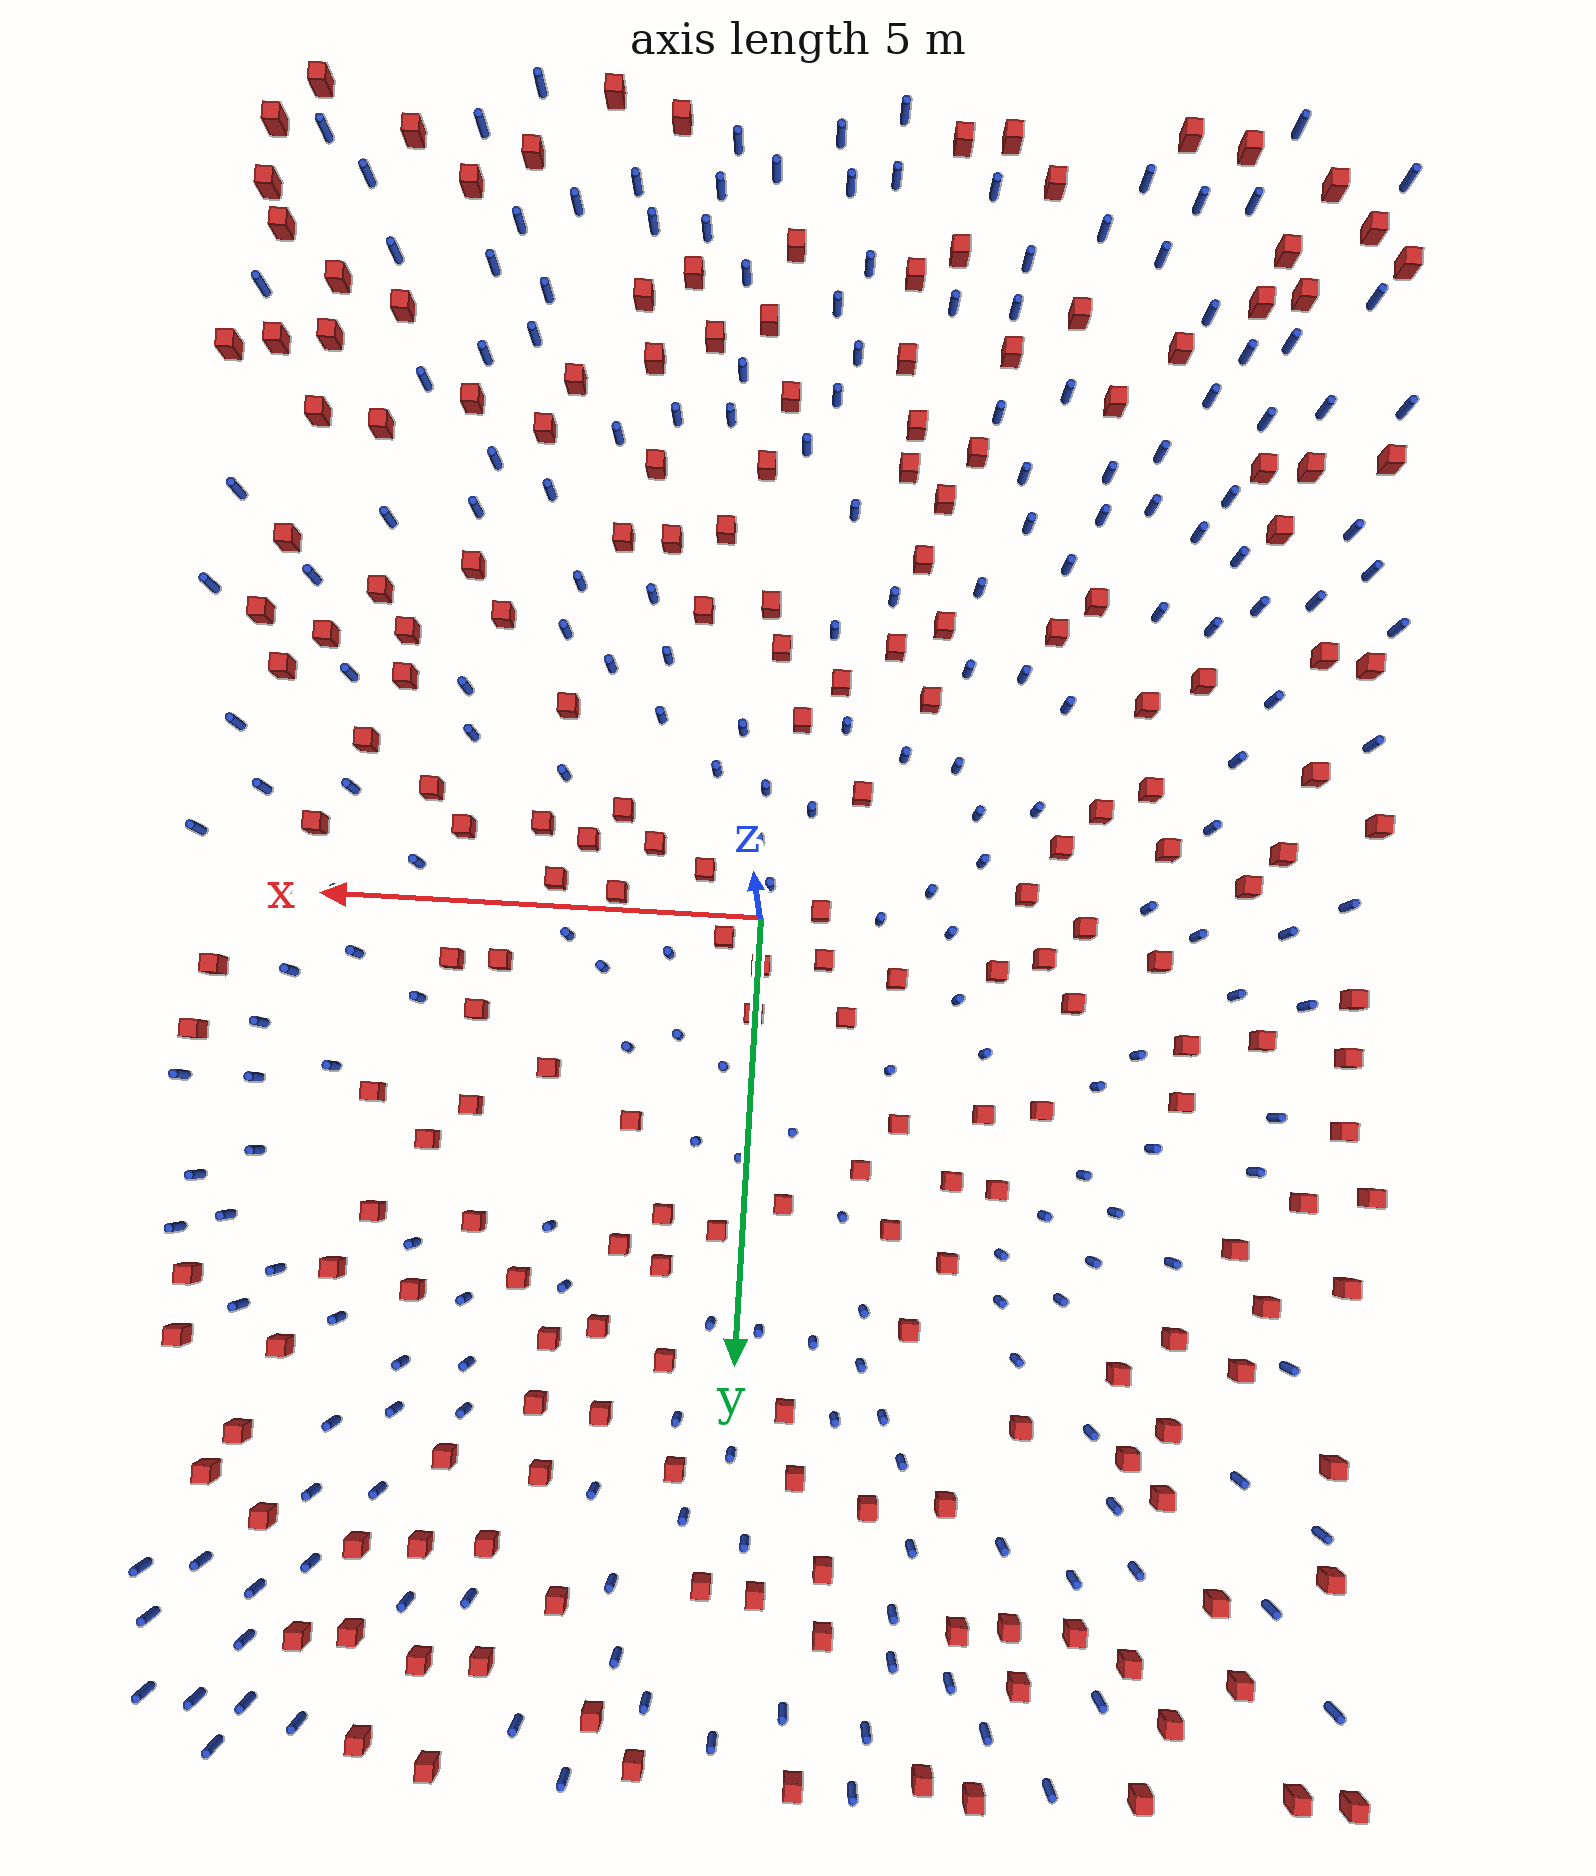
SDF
<sdf version="1.6">
  <model name="dense_99"><model name="pole_obstacle0">
  <static>true</static>
  <pose frame="">0.675583433063 -5.69856653266 2.88873142074e-08 -9.90536689661e-09 4.60219948993e-07 -1.20965994957e-07</pose>
  <link name="link">
  <pose frame="">0 0 0.3 0 -0 0</pose>
    <inertial>
      <mass>1</mass>
      <inertia>
        <ixx>0.145833</ixx>
        <ixy>0</ixy>
        <ixz>0</ixz>
        <iyy>0.145833</iyy>
        <iyz>0</iyz>
        <izz>0.125</izz>
      </inertia>
    </inertial>
    <collision name="collision">
      <geometry>
        <cylinder>
          <radius>0.05</radius>
          <length>.6</length>
        </cylinder>
      </geometry>
      <max_contacts>10</max_contacts>
      <surface>
        <contact>
          <ode/>
        </contact>
        <bounce/>
        <friction>
          <torsional>
            <ode/>
          </torsional>
          <ode/>
        </friction>
      </surface>
    </collision>
    <visual name="visual">
      <geometry>
        <cylinder>
          <radius>0.05</radius>
          <length>.6</length>
        </cylinder>
      </geometry>
      <material>
        <script>
          <name>Gazebo/Blue</name>
          <uri>file://media/materials/scripts/gazebo.material</uri>
        </script>
      </material>
    </visual>
    <self_collide>0</self_collide>
    <kinematic>0</kinematic>
  </link>
</model>
<model name="pole_obstacle1">
  <static>true</static>
  <pose frame="">-3.60275589972 -4.77980492807 2.88873142074e-08 -9.90536689859e-09 4.60219948989e-07 -1.20965994961e-07</pose>
  <link name="link">
  <pose frame="">0 0 0.3 0 -0 0</pose>
    <inertial>
      <mass>1</mass>
      <inertia>
        <ixx>0.145833</ixx>
        <ixy>0</ixy>
        <ixz>0</ixz>
        <iyy>0.145833</iyy>
        <iyz>0</iyz>
        <izz>0.125</izz>
      </inertia>
    </inertial>
    <collision name="collision">
      <geometry>
        <cylinder>
          <radius>0.05</radius>
          <length>.6</length>
        </cylinder>
      </geometry>
      <max_contacts>10</max_contacts>
      <surface>
        <contact>
          <ode/>
        </contact>
        <bounce/>
        <friction>
          <torsional>
            <ode/>
          </torsional>
          <ode/>
        </friction>
      </surface>
    </collision>
    <visual name="visual">
      <geometry>
        <cylinder>
          <radius>0.05</radius>
          <length>.6</length>
        </cylinder>
      </geometry>
      <material>
        <script>
          <name>Gazebo/Blue</name>
          <uri>file://media/materials/scripts/gazebo.material</uri>
        </script>
      </material>
    </visual>
    <self_collide>0</self_collide>
    <kinematic>0</kinematic>
  </link>
</model>
<model name="square_post_obstacle0">
  <static>true</static>
  <pose frame="">0.278284091233 3.50186409478 8.22691968438e-08 7.22125133819e-06 -7.54495500217e-07 2.29674213826e-05</pose>
  <link name="link">
    <pose frame="">0 0 0.25 0 -0 0</pose>
    <inertial>
      <mass>100</mass>
      <inertia>
        <ixx>0.166667</ixx>
        <ixy>0</ixy>
        <ixz>0</ixz>
        <iyy>0.166667</iyy>
        <iyz>0</iyz>
        <izz>0.166667</izz>
      </inertia>
    </inertial>
    <collision name="collision">
      <geometry>
        <box>
          <size>.2 .2 .5</size>
        </box>
      </geometry>
      <max_contacts>10</max_contacts>
      <surface>
        <contact>
          <ode/>
        </contact>
        <bounce/>
        <friction>
          <torsional>
            <ode/>
          </torsional>
          <ode/>
        </friction>
      </surface>
    </collision>
    <visual name="visual">
      <geometry>
        <box>
          <size>.2 .2 .5</size>
        </box>
      </geometry>
      <material>
        <script>
          <name>Gazebo/Red</name>
          <uri>file://media/materials/scripts/gazebo.material</uri>
        </script>
      </material>
    </visual>
    <self_collide>0</self_collide>
    <kinematic>0</kinematic>
  </link>
</model>
<model name="square_post_obstacle1">
  <static>true</static>
  <pose frame="">3.23395350639 8.3291602292 8.22691968438e-08 7.22125133819e-06 -7.54495500217e-07 2.29674213826e-05</pose>
  <link name="link">
    <pose frame="">0 0 0.25 0 -0 0</pose>
    <inertial>
      <mass>100</mass>
      <inertia>
        <ixx>0.166667</ixx>
        <ixy>0</ixy>
        <ixz>0</ixz>
        <iyy>0.166667</iyy>
        <iyz>0</iyz>
        <izz>0.166667</izz>
      </inertia>
    </inertial>
    <collision name="collision">
      <geometry>
        <box>
          <size>.2 .2 .5</size>
        </box>
      </geometry>
      <max_contacts>10</max_contacts>
      <surface>
        <contact>
          <ode/>
        </contact>
        <bounce/>
        <friction>
          <torsional>
            <ode/>
          </torsional>
          <ode/>
        </friction>
      </surface>
    </collision>
    <visual name="visual">
      <geometry>
        <box>
          <size>.2 .2 .5</size>
        </box>
      </geometry>
      <material>
        <script>
          <name>Gazebo/Red</name>
          <uri>file://media/materials/scripts/gazebo.material</uri>
        </script>
      </material>
    </visual>
    <self_collide>0</self_collide>
    <kinematic>0</kinematic>
  </link>
</model>
<model name="pole_obstacle2">
  <static>true</static>
  <pose frame="">2.2962242068 -1.4888534437 2.88873142074e-08 -9.90536689395e-09 4.60219949e-07 -1.20965994953e-07</pose>
  <link name="link">
  <pose frame="">0 0 0.3 0 -0 0</pose>
    <inertial>
      <mass>1</mass>
      <inertia>
        <ixx>0.145833</ixx>
        <ixy>0</ixy>
        <ixz>0</ixz>
        <iyy>0.145833</iyy>
        <iyz>0</iyz>
        <izz>0.125</izz>
      </inertia>
    </inertial>
    <collision name="collision">
      <geometry>
        <cylinder>
          <radius>0.05</radius>
          <length>.6</length>
        </cylinder>
      </geometry>
      <max_contacts>10</max_contacts>
      <surface>
        <contact>
          <ode/>
        </contact>
        <bounce/>
        <friction>
          <torsional>
            <ode/>
          </torsional>
          <ode/>
        </friction>
      </surface>
    </collision>
    <visual name="visual">
      <geometry>
        <cylinder>
          <radius>0.05</radius>
          <length>.6</length>
        </cylinder>
      </geometry>
      <material>
        <script>
          <name>Gazebo/Blue</name>
          <uri>file://media/materials/scripts/gazebo.material</uri>
        </script>
      </material>
    </visual>
    <self_collide>0</self_collide>
    <kinematic>0</kinematic>
  </link>
</model>
<model name="pole_obstacle3">
  <static>true</static>
  <pose frame="">-4.10674583916 3.05079004273 2.88873142074e-08 -9.90536690245e-09 4.6021994898e-07 -1.20965994966e-07</pose>
  <link name="link">
  <pose frame="">0 0 0.3 0 -0 0</pose>
    <inertial>
      <mass>1</mass>
      <inertia>
        <ixx>0.145833</ixx>
        <ixy>0</ixy>
        <ixz>0</ixz>
        <iyy>0.145833</iyy>
        <iyz>0</iyz>
        <izz>0.125</izz>
      </inertia>
    </inertial>
    <collision name="collision">
      <geometry>
        <cylinder>
          <radius>0.05</radius>
          <length>.6</length>
        </cylinder>
      </geometry>
      <max_contacts>10</max_contacts>
      <surface>
        <contact>
          <ode/>
        </contact>
        <bounce/>
        <friction>
          <torsional>
            <ode/>
          </torsional>
          <ode/>
        </friction>
      </surface>
    </collision>
    <visual name="visual">
      <geometry>
        <cylinder>
          <radius>0.05</radius>
          <length>.6</length>
        </cylinder>
      </geometry>
      <material>
        <script>
          <name>Gazebo/Blue</name>
          <uri>file://media/materials/scripts/gazebo.material</uri>
        </script>
      </material>
    </visual>
    <self_collide>0</self_collide>
    <kinematic>0</kinematic>
  </link>
</model>
<model name="pole_obstacle4">
  <static>true</static>
  <pose frame="">4.50467344386 9.05752582636 2.88873142074e-08 -9.9053668967e-09 4.60219948993e-07 -1.20965994957e-07</pose>
  <link name="link">
  <pose frame="">0 0 0.3 0 -0 0</pose>
    <inertial>
      <mass>1</mass>
      <inertia>
        <ixx>0.145833</ixx>
        <ixy>0</ixy>
        <ixz>0</ixz>
        <iyy>0.145833</iyy>
        <iyz>0</iyz>
        <izz>0.125</izz>
      </inertia>
    </inertial>
    <collision name="collision">
      <geometry>
        <cylinder>
          <radius>0.05</radius>
          <length>.6</length>
        </cylinder>
      </geometry>
      <max_contacts>10</max_contacts>
      <surface>
        <contact>
          <ode/>
        </contact>
        <bounce/>
        <friction>
          <torsional>
            <ode/>
          </torsional>
          <ode/>
        </friction>
      </surface>
    </collision>
    <visual name="visual">
      <geometry>
        <cylinder>
          <radius>0.05</radius>
          <length>.6</length>
        </cylinder>
      </geometry>
      <material>
        <script>
          <name>Gazebo/Blue</name>
          <uri>file://media/materials/scripts/gazebo.material</uri>
        </script>
      </material>
    </visual>
    <self_collide>0</self_collide>
    <kinematic>0</kinematic>
  </link>
</model>
<model name="pole_obstacle5">
  <static>true</static>
  <pose frame="">-0.207026416961 -5.39935714129 2.88873142074e-08 -9.90536689703e-09 4.60219948992e-07 -1.20965994959e-07</pose>
  <link name="link">
  <pose frame="">0 0 0.3 0 -0 0</pose>
    <inertial>
      <mass>1</mass>
      <inertia>
        <ixx>0.145833</ixx>
        <ixy>0</ixy>
        <ixz>0</ixz>
        <iyy>0.145833</iyy>
        <iyz>0</iyz>
        <izz>0.125</izz>
      </inertia>
    </inertial>
    <collision name="collision">
      <geometry>
        <cylinder>
          <radius>0.05</radius>
          <length>.6</length>
        </cylinder>
      </geometry>
      <max_contacts>10</max_contacts>
      <surface>
        <contact>
          <ode/>
        </contact>
        <bounce/>
        <friction>
          <torsional>
            <ode/>
          </torsional>
          <ode/>
        </friction>
      </surface>
    </collision>
    <visual name="visual">
      <geometry>
        <cylinder>
          <radius>0.05</radius>
          <length>.6</length>
        </cylinder>
      </geometry>
      <material>
        <script>
          <name>Gazebo/Blue</name>
          <uri>file://media/materials/scripts/gazebo.material</uri>
        </script>
      </material>
    </visual>
    <self_collide>0</self_collide>
    <kinematic>0</kinematic>
  </link>
</model>
<model name="pole_obstacle6">
  <static>true</static>
  <pose frame="">5.54569340922 -8.79581876974 2.88873142074e-08 -9.9053668967e-09 4.60219948993e-07 -1.20965994957e-07</pose>
  <link name="link">
  <pose frame="">0 0 0.3 0 -0 0</pose>
    <inertial>
      <mass>1</mass>
      <inertia>
        <ixx>0.145833</ixx>
        <ixy>0</ixy>
        <ixz>0</ixz>
        <iyy>0.145833</iyy>
        <iyz>0</iyz>
        <izz>0.125</izz>
      </inertia>
    </inertial>
    <collision name="collision">
      <geometry>
        <cylinder>
          <radius>0.05</radius>
          <length>.6</length>
        </cylinder>
      </geometry>
      <max_contacts>10</max_contacts>
      <surface>
        <contact>
          <ode/>
        </contact>
        <bounce/>
        <friction>
          <torsional>
            <ode/>
          </torsional>
          <ode/>
        </friction>
      </surface>
    </collision>
    <visual name="visual">
      <geometry>
        <cylinder>
          <radius>0.05</radius>
          <length>.6</length>
        </cylinder>
      </geometry>
      <material>
        <script>
          <name>Gazebo/Blue</name>
          <uri>file://media/materials/scripts/gazebo.material</uri>
        </script>
      </material>
    </visual>
    <self_collide>0</self_collide>
    <kinematic>0</kinematic>
  </link>
</model>
<model name="square_post_obstacle2">
  <static>true</static>
  <pose frame="">4.65110520689 -5.38284610721 8.22691968438e-08 7.2212513382e-06 -7.54495500217e-07 2.29674213826e-05</pose>
  <link name="link">
    <pose frame="">0 0 0.25 0 -0 0</pose>
    <inertial>
      <mass>100</mass>
      <inertia>
        <ixx>0.166667</ixx>
        <ixy>0</ixy>
        <ixz>0</ixz>
        <iyy>0.166667</iyy>
        <iyz>0</iyz>
        <izz>0.166667</izz>
      </inertia>
    </inertial>
    <collision name="collision">
      <geometry>
        <box>
          <size>.2 .2 .5</size>
        </box>
      </geometry>
      <max_contacts>10</max_contacts>
      <surface>
        <contact>
          <ode/>
        </contact>
        <bounce/>
        <friction>
          <torsional>
            <ode/>
          </torsional>
          <ode/>
        </friction>
      </surface>
    </collision>
    <visual name="visual">
      <geometry>
        <box>
          <size>.2 .2 .5</size>
        </box>
      </geometry>
      <material>
        <script>
          <name>Gazebo/Red</name>
          <uri>file://media/materials/scripts/gazebo.material</uri>
        </script>
      </material>
    </visual>
    <self_collide>0</self_collide>
    <kinematic>0</kinematic>
  </link>
</model>
<model name="square_post_obstacle3">
  <static>true</static>
  <pose frame="">0.649831899917 -4.38141495095 8.22691968438e-08 7.2212513382e-06 -7.54495500217e-07 2.29674213826e-05</pose>
  <link name="link">
    <pose frame="">0 0 0.25 0 -0 0</pose>
    <inertial>
      <mass>100</mass>
      <inertia>
        <ixx>0.166667</ixx>
        <ixy>0</ixy>
        <ixz>0</ixz>
        <iyy>0.166667</iyy>
        <iyz>0</iyz>
        <izz>0.166667</izz>
      </inertia>
    </inertial>
    <collision name="collision">
      <geometry>
        <box>
          <size>.2 .2 .5</size>
        </box>
      </geometry>
      <max_contacts>10</max_contacts>
      <surface>
        <contact>
          <ode/>
        </contact>
        <bounce/>
        <friction>
          <torsional>
            <ode/>
          </torsional>
          <ode/>
        </friction>
      </surface>
    </collision>
    <visual name="visual">
      <geometry>
        <box>
          <size>.2 .2 .5</size>
        </box>
      </geometry>
      <material>
        <script>
          <name>Gazebo/Red</name>
          <uri>file://media/materials/scripts/gazebo.material</uri>
        </script>
      </material>
    </visual>
    <self_collide>0</self_collide>
    <kinematic>0</kinematic>
  </link>
</model>
<model name="square_post_obstacle4">
  <static>true</static>
  <pose frame="">-6.85522388326 -5.62847621631 8.22691968438e-08 7.22125133819e-06 -7.54495500217e-07 2.29674213826e-05</pose>
  <link name="link">
    <pose frame="">0 0 0.25 0 -0 0</pose>
    <inertial>
      <mass>100</mass>
      <inertia>
        <ixx>0.166667</ixx>
        <ixy>0</ixy>
        <ixz>0</ixz>
        <iyy>0.166667</iyy>
        <iyz>0</iyz>
        <izz>0.166667</izz>
      </inertia>
    </inertial>
    <collision name="collision">
      <geometry>
        <box>
          <size>.2 .2 .5</size>
        </box>
      </geometry>
      <max_contacts>10</max_contacts>
      <surface>
        <contact>
          <ode/>
        </contact>
        <bounce/>
        <friction>
          <torsional>
            <ode/>
          </torsional>
          <ode/>
        </friction>
      </surface>
    </collision>
    <visual name="visual">
      <geometry>
        <box>
          <size>.2 .2 .5</size>
        </box>
      </geometry>
      <material>
        <script>
          <name>Gazebo/Red</name>
          <uri>file://media/materials/scripts/gazebo.material</uri>
        </script>
      </material>
    </visual>
    <self_collide>0</self_collide>
    <kinematic>0</kinematic>
  </link>
</model>
<model name="pole_obstacle7">
  <static>true</static>
  <pose frame="">-6.55722692997 -0.499189237258 2.88873142074e-08 -9.90536689333e-09 4.60219949001e-07 -1.20965994954e-07</pose>
  <link name="link">
  <pose frame="">0 0 0.3 0 -0 0</pose>
    <inertial>
      <mass>1</mass>
      <inertia>
        <ixx>0.145833</ixx>
        <ixy>0</ixy>
        <ixz>0</ixz>
        <iyy>0.145833</iyy>
        <iyz>0</iyz>
        <izz>0.125</izz>
      </inertia>
    </inertial>
    <collision name="collision">
      <geometry>
        <cylinder>
          <radius>0.05</radius>
          <length>.6</length>
        </cylinder>
      </geometry>
      <max_contacts>10</max_contacts>
      <surface>
        <contact>
          <ode/>
        </contact>
        <bounce/>
        <friction>
          <torsional>
            <ode/>
          </torsional>
          <ode/>
        </friction>
      </surface>
    </collision>
    <visual name="visual">
      <geometry>
        <cylinder>
          <radius>0.05</radius>
          <length>.6</length>
        </cylinder>
      </geometry>
      <material>
        <script>
          <name>Gazebo/Blue</name>
          <uri>file://media/materials/scripts/gazebo.material</uri>
        </script>
      </material>
    </visual>
    <self_collide>0</self_collide>
    <kinematic>0</kinematic>
  </link>
</model>
<model name="pole_obstacle8">
  <static>true</static>
  <pose frame="">1.08298436727 -7.86564104665 2.88873142074e-08 -9.90536689852e-09 4.60219948989e-07 -1.2096599496e-07</pose>
  <link name="link">
  <pose frame="">0 0 0.3 0 -0 0</pose>
    <inertial>
      <mass>1</mass>
      <inertia>
        <ixx>0.145833</ixx>
        <ixy>0</ixy>
        <ixz>0</ixz>
        <iyy>0.145833</iyy>
        <iyz>0</iyz>
        <izz>0.125</izz>
      </inertia>
    </inertial>
    <collision name="collision">
      <geometry>
        <cylinder>
          <radius>0.05</radius>
          <length>.6</length>
        </cylinder>
      </geometry>
      <max_contacts>10</max_contacts>
      <surface>
        <contact>
          <ode/>
        </contact>
        <bounce/>
        <friction>
          <torsional>
            <ode/>
          </torsional>
          <ode/>
        </friction>
      </surface>
    </collision>
    <visual name="visual">
      <geometry>
        <cylinder>
          <radius>0.05</radius>
          <length>.6</length>
        </cylinder>
      </geometry>
      <material>
        <script>
          <name>Gazebo/Blue</name>
          <uri>file://media/materials/scripts/gazebo.material</uri>
        </script>
      </material>
    </visual>
    <self_collide>0</self_collide>
    <kinematic>0</kinematic>
  </link>
</model>
<model name="square_post_obstacle5">
  <static>true</static>
  <pose frame="">1.77964697952 7.60460296288 8.22691968438e-08 7.2212513382e-06 -7.54495500217e-07 2.29674213826e-05</pose>
  <link name="link">
    <pose frame="">0 0 0.25 0 -0 0</pose>
    <inertial>
      <mass>100</mass>
      <inertia>
        <ixx>0.166667</ixx>
        <ixy>0</ixy>
        <ixz>0</ixz>
        <iyy>0.166667</iyy>
        <iyz>0</iyz>
        <izz>0.166667</izz>
      </inertia>
    </inertial>
    <collision name="collision">
      <geometry>
        <box>
          <size>.2 .2 .5</size>
        </box>
      </geometry>
      <max_contacts>10</max_contacts>
      <surface>
        <contact>
          <ode/>
        </contact>
        <bounce/>
        <friction>
          <torsional>
            <ode/>
          </torsional>
          <ode/>
        </friction>
      </surface>
    </collision>
    <visual name="visual">
      <geometry>
        <box>
          <size>.2 .2 .5</size>
        </box>
      </geometry>
      <material>
        <script>
          <name>Gazebo/Red</name>
          <uri>file://media/materials/scripts/gazebo.material</uri>
        </script>
      </material>
    </visual>
    <self_collide>0</self_collide>
    <kinematic>0</kinematic>
  </link>
</model>
<model name="square_post_obstacle6">
  <static>true</static>
  <pose frame="">-0.735743962534 0.444639540895 8.22691968438e-08 7.22125133819e-06 -7.54495500217e-07 2.29674213826e-05</pose>
  <link name="link">
    <pose frame="">0 0 0.25 0 -0 0</pose>
    <inertial>
      <mass>100</mass>
      <inertia>
        <ixx>0.166667</ixx>
        <ixy>0</ixy>
        <ixz>0</ixz>
        <iyy>0.166667</iyy>
        <iyz>0</iyz>
        <izz>0.166667</izz>
      </inertia>
    </inertial>
    <collision name="collision">
      <geometry>
        <box>
          <size>.2 .2 .5</size>
        </box>
      </geometry>
      <max_contacts>10</max_contacts>
      <surface>
        <contact>
          <ode/>
        </contact>
        <bounce/>
        <friction>
          <torsional>
            <ode/>
          </torsional>
          <ode/>
        </friction>
      </surface>
    </collision>
    <visual name="visual">
      <geometry>
        <box>
          <size>.2 .2 .5</size>
        </box>
      </geometry>
      <material>
        <script>
          <name>Gazebo/Red</name>
          <uri>file://media/materials/scripts/gazebo.material</uri>
        </script>
      </material>
    </visual>
    <self_collide>0</self_collide>
    <kinematic>0</kinematic>
  </link>
</model>
<model name="square_post_obstacle7">
  <static>true</static>
  <pose frame="">-3.18490612151 5.45710141778 8.22691968438e-08 7.2212513382e-06 -7.54495500217e-07 2.29674213826e-05</pose>
  <link name="link">
    <pose frame="">0 0 0.25 0 -0 0</pose>
    <inertial>
      <mass>100</mass>
      <inertia>
        <ixx>0.166667</ixx>
        <ixy>0</ixy>
        <ixz>0</ixz>
        <iyy>0.166667</iyy>
        <iyz>0</iyz>
        <izz>0.166667</izz>
      </inertia>
    </inertial>
    <collision name="collision">
      <geometry>
        <box>
          <size>.2 .2 .5</size>
        </box>
      </geometry>
      <max_contacts>10</max_contacts>
      <surface>
        <contact>
          <ode/>
        </contact>
        <bounce/>
        <friction>
          <torsional>
            <ode/>
          </torsional>
          <ode/>
        </friction>
      </surface>
    </collision>
    <visual name="visual">
      <geometry>
        <box>
          <size>.2 .2 .5</size>
        </box>
      </geometry>
      <material>
        <script>
          <name>Gazebo/Red</name>
          <uri>file://media/materials/scripts/gazebo.material</uri>
        </script>
      </material>
    </visual>
    <self_collide>0</self_collide>
    <kinematic>0</kinematic>
  </link>
</model>
<model name="pole_obstacle9">
  <static>true</static>
  <pose frame="">-1.1136684123 -9.39230906978 2.88873142074e-08 -9.90536690474e-09 4.60219948974e-07 -1.2096599497e-07</pose>
  <link name="link">
  <pose frame="">0 0 0.3 0 -0 0</pose>
    <inertial>
      <mass>1</mass>
      <inertia>
        <ixx>0.145833</ixx>
        <ixy>0</ixy>
        <ixz>0</ixz>
        <iyy>0.145833</iyy>
        <iyz>0</iyz>
        <izz>0.125</izz>
      </inertia>
    </inertial>
    <collision name="collision">
      <geometry>
        <cylinder>
          <radius>0.05</radius>
          <length>.6</length>
        </cylinder>
      </geometry>
      <max_contacts>10</max_contacts>
      <surface>
        <contact>
          <ode/>
        </contact>
        <bounce/>
        <friction>
          <torsional>
            <ode/>
          </torsional>
          <ode/>
        </friction>
      </surface>
    </collision>
    <visual name="visual">
      <geometry>
        <cylinder>
          <radius>0.05</radius>
          <length>.6</length>
        </cylinder>
      </geometry>
      <material>
        <script>
          <name>Gazebo/Blue</name>
          <uri>file://media/materials/scripts/gazebo.material</uri>
        </script>
      </material>
    </visual>
    <self_collide>0</self_collide>
    <kinematic>0</kinematic>
  </link>
</model>
<model name="pole_obstacle10">
  <static>true</static>
  <pose frame="">-2.10604508527 -1.82271436291 2.88873142074e-08 -9.90536689395e-09 4.60219949e-07 -1.20965994953e-07</pose>
  <link name="link">
  <pose frame="">0 0 0.3 0 -0 0</pose>
    <inertial>
      <mass>1</mass>
      <inertia>
        <ixx>0.145833</ixx>
        <ixy>0</ixy>
        <ixz>0</ixz>
        <iyy>0.145833</iyy>
        <iyz>0</iyz>
        <izz>0.125</izz>
      </inertia>
    </inertial>
    <collision name="collision">
      <geometry>
        <cylinder>
          <radius>0.05</radius>
          <length>.6</length>
        </cylinder>
      </geometry>
      <max_contacts>10</max_contacts>
      <surface>
        <contact>
          <ode/>
        </contact>
        <bounce/>
        <friction>
          <torsional>
            <ode/>
          </torsional>
          <ode/>
        </friction>
      </surface>
    </collision>
    <visual name="visual">
      <geometry>
        <cylinder>
          <radius>0.05</radius>
          <length>.6</length>
        </cylinder>
      </geometry>
      <material>
        <script>
          <name>Gazebo/Blue</name>
          <uri>file://media/materials/scripts/gazebo.material</uri>
        </script>
      </material>
    </visual>
    <self_collide>0</self_collide>
    <kinematic>0</kinematic>
  </link>
</model>
<model name="pole_obstacle11">
  <static>true</static>
  <pose frame="">6.20497927273 8.02178845406 2.88873142074e-08 -9.90536690354e-09 4.60219948977e-07 -1.20965994967e-07</pose>
  <link name="link">
  <pose frame="">0 0 0.3 0 -0 0</pose>
    <inertial>
      <mass>1</mass>
      <inertia>
        <ixx>0.145833</ixx>
        <ixy>0</ixy>
        <ixz>0</ixz>
        <iyy>0.145833</iyy>
        <iyz>0</iyz>
        <izz>0.125</izz>
      </inertia>
    </inertial>
    <collision name="collision">
      <geometry>
        <cylinder>
          <radius>0.05</radius>
          <length>.6</length>
        </cylinder>
      </geometry>
      <max_contacts>10</max_contacts>
      <surface>
        <contact>
          <ode/>
        </contact>
        <bounce/>
        <friction>
          <torsional>
            <ode/>
          </torsional>
          <ode/>
        </friction>
      </surface>
    </collision>
    <visual name="visual">
      <geometry>
        <cylinder>
          <radius>0.05</radius>
          <length>.6</length>
        </cylinder>
      </geometry>
      <material>
        <script>
          <name>Gazebo/Blue</name>
          <uri>file://media/materials/scripts/gazebo.material</uri>
        </script>
      </material>
    </visual>
    <self_collide>0</self_collide>
    <kinematic>0</kinematic>
  </link>
</model>
<model name="pole_obstacle12">
  <static>true</static>
  <pose frame="">-4.51238808588 6.91465954027 2.88873142074e-08 -9.90536690842e-09 4.60219948965e-07 -1.20965994976e-07</pose>
  <link name="link">
  <pose frame="">0 0 0.3 0 -0 0</pose>
    <inertial>
      <mass>1</mass>
      <inertia>
        <ixx>0.145833</ixx>
        <ixy>0</ixy>
        <ixz>0</ixz>
        <iyy>0.145833</iyy>
        <iyz>0</iyz>
        <izz>0.125</izz>
      </inertia>
    </inertial>
    <collision name="collision">
      <geometry>
        <cylinder>
          <radius>0.05</radius>
          <length>.6</length>
        </cylinder>
      </geometry>
      <max_contacts>10</max_contacts>
      <surface>
        <contact>
          <ode/>
        </contact>
        <bounce/>
        <friction>
          <torsional>
            <ode/>
          </torsional>
          <ode/>
        </friction>
      </surface>
    </collision>
    <visual name="visual">
      <geometry>
        <cylinder>
          <radius>0.05</radius>
          <length>.6</length>
        </cylinder>
      </geometry>
      <material>
        <script>
          <name>Gazebo/Blue</name>
          <uri>file://media/materials/scripts/gazebo.material</uri>
        </script>
      </material>
    </visual>
    <self_collide>0</self_collide>
    <kinematic>0</kinematic>
  </link>
</model>
<model name="square_post_obstacle8">
  <static>true</static>
  <pose frame="">-5.94740173558 -5.48273162042 8.22691968438e-08 7.22125133819e-06 -7.54495500217e-07 2.29674213826e-05</pose>
  <link name="link">
    <pose frame="">0 0 0.25 0 -0 0</pose>
    <inertial>
      <mass>100</mass>
      <inertia>
        <ixx>0.166667</ixx>
        <ixy>0</ixy>
        <ixz>0</ixz>
        <iyy>0.166667</iyy>
        <iyz>0</iyz>
        <izz>0.166667</izz>
      </inertia>
    </inertial>
    <collision name="collision">
      <geometry>
        <box>
          <size>.2 .2 .5</size>
        </box>
      </geometry>
      <max_contacts>10</max_contacts>
      <surface>
        <contact>
          <ode/>
        </contact>
        <bounce/>
        <friction>
          <torsional>
            <ode/>
          </torsional>
          <ode/>
        </friction>
      </surface>
    </collision>
    <visual name="visual">
      <geometry>
        <box>
          <size>.2 .2 .5</size>
        </box>
      </geometry>
      <material>
        <script>
          <name>Gazebo/Red</name>
          <uri>file://media/materials/scripts/gazebo.material</uri>
        </script>
      </material>
    </visual>
    <self_collide>0</self_collide>
    <kinematic>0</kinematic>
  </link>
</model>
<model name="square_post_obstacle9">
  <static>true</static>
  <pose frame="">4.55265677915 -1.7423102586 8.22691968438e-08 7.2212513382e-06 -7.54495500217e-07 2.29674213826e-05</pose>
  <link name="link">
    <pose frame="">0 0 0.25 0 -0 0</pose>
    <inertial>
      <mass>100</mass>
      <inertia>
        <ixx>0.166667</ixx>
        <ixy>0</ixy>
        <ixz>0</ixz>
        <iyy>0.166667</iyy>
        <iyz>0</iyz>
        <izz>0.166667</izz>
      </inertia>
    </inertial>
    <collision name="collision">
      <geometry>
        <box>
          <size>.2 .2 .5</size>
        </box>
      </geometry>
      <max_contacts>10</max_contacts>
      <surface>
        <contact>
          <ode/>
        </contact>
        <bounce/>
        <friction>
          <torsional>
            <ode/>
          </torsional>
          <ode/>
        </friction>
      </surface>
    </collision>
    <visual name="visual">
      <geometry>
        <box>
          <size>.2 .2 .5</size>
        </box>
      </geometry>
      <material>
        <script>
          <name>Gazebo/Red</name>
          <uri>file://media/materials/scripts/gazebo.material</uri>
        </script>
      </material>
    </visual>
    <self_collide>0</self_collide>
    <kinematic>0</kinematic>
  </link>
</model>
<model name="pole_obstacle13">
  <static>true</static>
  <pose frame="">4.39369261284 4.69720485507 2.88873142074e-08 -9.90536690842e-09 4.60219948965e-07 -1.20965994976e-07</pose>
  <link name="link">
  <pose frame="">0 0 0.3 0 -0 0</pose>
    <inertial>
      <mass>1</mass>
      <inertia>
        <ixx>0.145833</ixx>
        <ixy>0</ixy>
        <ixz>0</ixz>
        <iyy>0.145833</iyy>
        <iyz>0</iyz>
        <izz>0.125</izz>
      </inertia>
    </inertial>
    <collision name="collision">
      <geometry>
        <cylinder>
          <radius>0.05</radius>
          <length>.6</length>
        </cylinder>
      </geometry>
      <max_contacts>10</max_contacts>
      <surface>
        <contact>
          <ode/>
        </contact>
        <bounce/>
        <friction>
          <torsional>
            <ode/>
          </torsional>
          <ode/>
        </friction>
      </surface>
    </collision>
    <visual name="visual">
      <geometry>
        <cylinder>
          <radius>0.05</radius>
          <length>.6</length>
        </cylinder>
      </geometry>
      <material>
        <script>
          <name>Gazebo/Blue</name>
          <uri>file://media/materials/scripts/gazebo.material</uri>
        </script>
      </material>
    </visual>
    <self_collide>0</self_collide>
    <kinematic>0</kinematic>
  </link>
</model>
<model name="square_post_obstacle10">
  <static>true</static>
  <pose frame="">-3.69143356227 -6.1247353923 8.22691968438e-08 7.22125133819e-06 -7.54495500217e-07 2.29674213826e-05</pose>
  <link name="link">
    <pose frame="">0 0 0.25 0 -0 0</pose>
    <inertial>
      <mass>100</mass>
      <inertia>
        <ixx>0.166667</ixx>
        <ixy>0</ixy>
        <ixz>0</ixz>
        <iyy>0.166667</iyy>
        <iyz>0</iyz>
        <izz>0.166667</izz>
      </inertia>
    </inertial>
    <collision name="collision">
      <geometry>
        <box>
          <size>.2 .2 .5</size>
        </box>
      </geometry>
      <max_contacts>10</max_contacts>
      <surface>
        <contact>
          <ode/>
        </contact>
        <bounce/>
        <friction>
          <torsional>
            <ode/>
          </torsional>
          <ode/>
        </friction>
      </surface>
    </collision>
    <visual name="visual">
      <geometry>
        <box>
          <size>.2 .2 .5</size>
        </box>
      </geometry>
      <material>
        <script>
          <name>Gazebo/Red</name>
          <uri>file://media/materials/scripts/gazebo.material</uri>
        </script>
      </material>
    </visual>
    <self_collide>0</self_collide>
    <kinematic>0</kinematic>
  </link>
</model>
<model name="square_post_obstacle11">
  <static>true</static>
  <pose frame="">-4.77294782789 6.12462076641 8.22691968438e-08 7.22125133819e-06 -7.54495500217e-07 2.29674213826e-05</pose>
  <link name="link">
    <pose frame="">0 0 0.25 0 -0 0</pose>
    <inertial>
      <mass>100</mass>
      <inertia>
        <ixx>0.166667</ixx>
        <ixy>0</ixy>
        <ixz>0</ixz>
        <iyy>0.166667</iyy>
        <iyz>0</iyz>
        <izz>0.166667</izz>
      </inertia>
    </inertial>
    <collision name="collision">
      <geometry>
        <box>
          <size>.2 .2 .5</size>
        </box>
      </geometry>
      <max_contacts>10</max_contacts>
      <surface>
        <contact>
          <ode/>
        </contact>
        <bounce/>
        <friction>
          <torsional>
            <ode/>
          </torsional>
          <ode/>
        </friction>
      </surface>
    </collision>
    <visual name="visual">
      <geometry>
        <box>
          <size>.2 .2 .5</size>
        </box>
      </geometry>
      <material>
        <script>
          <name>Gazebo/Red</name>
          <uri>file://media/materials/scripts/gazebo.material</uri>
        </script>
      </material>
    </visual>
    <self_collide>0</self_collide>
    <kinematic>0</kinematic>
  </link>
</model>
<model name="pole_obstacle14">
  <static>true</static>
  <pose frame="">-5.16681830971 -6.7704141858 2.88873142074e-08 -9.90536690842e-09 4.60219948965e-07 -1.20965994976e-07</pose>
  <link name="link">
  <pose frame="">0 0 0.3 0 -0 0</pose>
    <inertial>
      <mass>1</mass>
      <inertia>
        <ixx>0.145833</ixx>
        <ixy>0</ixy>
        <ixz>0</ixz>
        <iyy>0.145833</iyy>
        <iyz>0</iyz>
        <izz>0.125</izz>
      </inertia>
    </inertial>
    <collision name="collision">
      <geometry>
        <cylinder>
          <radius>0.05</radius>
          <length>.6</length>
        </cylinder>
      </geometry>
      <max_contacts>10</max_contacts>
      <surface>
        <contact>
          <ode/>
        </contact>
        <bounce/>
        <friction>
          <torsional>
            <ode/>
          </torsional>
          <ode/>
        </friction>
      </surface>
    </collision>
    <visual name="visual">
      <geometry>
        <cylinder>
          <radius>0.05</radius>
          <length>.6</length>
        </cylinder>
      </geometry>
      <material>
        <script>
          <name>Gazebo/Blue</name>
          <uri>file://media/materials/scripts/gazebo.material</uri>
        </script>
      </material>
    </visual>
    <self_collide>0</self_collide>
    <kinematic>0</kinematic>
  </link>
</model>
<model name="pole_obstacle15">
  <static>true</static>
  <pose frame="">-4.23528248232 -5.55599287549 2.88873142074e-08 -9.90536690842e-09 4.60219948965e-07 -1.20965994976e-07</pose>
  <link name="link">
  <pose frame="">0 0 0.3 0 -0 0</pose>
    <inertial>
      <mass>1</mass>
      <inertia>
        <ixx>0.145833</ixx>
        <ixy>0</ixy>
        <ixz>0</ixz>
        <iyy>0.145833</iyy>
        <iyz>0</iyz>
        <izz>0.125</izz>
      </inertia>
    </inertial>
    <collision name="collision">
      <geometry>
        <cylinder>
          <radius>0.05</radius>
          <length>.6</length>
        </cylinder>
      </geometry>
      <max_contacts>10</max_contacts>
      <surface>
        <contact>
          <ode/>
        </contact>
        <bounce/>
        <friction>
          <torsional>
            <ode/>
          </torsional>
          <ode/>
        </friction>
      </surface>
    </collision>
    <visual name="visual">
      <geometry>
        <cylinder>
          <radius>0.05</radius>
          <length>.6</length>
        </cylinder>
      </geometry>
      <material>
        <script>
          <name>Gazebo/Blue</name>
          <uri>file://media/materials/scripts/gazebo.material</uri>
        </script>
      </material>
    </visual>
    <self_collide>0</self_collide>
    <kinematic>0</kinematic>
  </link>
</model>
<model name="square_post_obstacle12">
  <static>true</static>
  <pose frame="">0.582915900474 6.12497515747 8.22691968438e-08 7.2212513382e-06 -7.54495500217e-07 2.29674213826e-05</pose>
  <link name="link">
    <pose frame="">0 0 0.25 0 -0 0</pose>
    <inertial>
      <mass>100</mass>
      <inertia>
        <ixx>0.166667</ixx>
        <ixy>0</ixy>
        <ixz>0</ixz>
        <iyy>0.166667</iyy>
        <iyz>0</iyz>
        <izz>0.166667</izz>
      </inertia>
    </inertial>
    <collision name="collision">
      <geometry>
        <box>
          <size>.2 .2 .5</size>
        </box>
      </geometry>
      <max_contacts>10</max_contacts>
      <surface>
        <contact>
          <ode/>
        </contact>
        <bounce/>
        <friction>
          <torsional>
            <ode/>
          </torsional>
          <ode/>
        </friction>
      </surface>
    </collision>
    <visual name="visual">
      <geometry>
        <box>
          <size>.2 .2 .5</size>
        </box>
      </geometry>
      <material>
        <script>
          <name>Gazebo/Red</name>
          <uri>file://media/materials/scripts/gazebo.material</uri>
        </script>
      </material>
    </visual>
    <self_collide>0</self_collide>
    <kinematic>0</kinematic>
  </link>
</model>
<model name="pole_obstacle16">
  <static>true</static>
  <pose frame="">3.65834895737 5.14077592062 2.88873142074e-08 -9.90536689859e-09 4.60219948989e-07 -1.20965994961e-07</pose>
  <link name="link">
  <pose frame="">0 0 0.3 0 -0 0</pose>
    <inertial>
      <mass>1</mass>
      <inertia>
        <ixx>0.145833</ixx>
        <ixy>0</ixy>
        <ixz>0</ixz>
        <iyy>0.145833</iyy>
        <iyz>0</iyz>
        <izz>0.125</izz>
      </inertia>
    </inertial>
    <collision name="collision">
      <geometry>
        <cylinder>
          <radius>0.05</radius>
          <length>.6</length>
        </cylinder>
      </geometry>
      <max_contacts>10</max_contacts>
      <surface>
        <contact>
          <ode/>
        </contact>
        <bounce/>
        <friction>
          <torsional>
            <ode/>
          </torsional>
          <ode/>
        </friction>
      </surface>
    </collision>
    <visual name="visual">
      <geometry>
        <cylinder>
          <radius>0.05</radius>
          <length>.6</length>
        </cylinder>
      </geometry>
      <material>
        <script>
          <name>Gazebo/Blue</name>
          <uri>file://media/materials/scripts/gazebo.material</uri>
        </script>
      </material>
    </visual>
    <self_collide>0</self_collide>
    <kinematic>0</kinematic>
  </link>
</model>
<model name="pole_obstacle17">
  <static>true</static>
  <pose frame="">-3.46691316281 -8.12460057241 2.88873142074e-08 -9.90536692318e-09 4.6021994893e-07 -1.20965994988e-07</pose>
  <link name="link">
  <pose frame="">0 0 0.3 0 -0 0</pose>
    <inertial>
      <mass>1</mass>
      <inertia>
        <ixx>0.145833</ixx>
        <ixy>0</ixy>
        <ixz>0</ixz>
        <iyy>0.145833</iyy>
        <iyz>0</iyz>
        <izz>0.125</izz>
      </inertia>
    </inertial>
    <collision name="collision">
      <geometry>
        <cylinder>
          <radius>0.05</radius>
          <length>.6</length>
        </cylinder>
      </geometry>
      <max_contacts>10</max_contacts>
      <surface>
        <contact>
          <ode/>
        </contact>
        <bounce/>
        <friction>
          <torsional>
            <ode/>
          </torsional>
          <ode/>
        </friction>
      </surface>
    </collision>
    <visual name="visual">
      <geometry>
        <cylinder>
          <radius>0.05</radius>
          <length>.6</length>
        </cylinder>
      </geometry>
      <material>
        <script>
          <name>Gazebo/Blue</name>
          <uri>file://media/materials/scripts/gazebo.material</uri>
        </script>
      </material>
    </visual>
    <self_collide>0</self_collide>
    <kinematic>0</kinematic>
  </link>
</model>
<model name="square_post_obstacle13">
  <static>true</static>
  <pose frame="">0.0485558772936 -7.73937814161 8.22691968438e-08 7.2212513382e-06 -7.54495500217e-07 2.29674213826e-05</pose>
  <link name="link">
    <pose frame="">0 0 0.25 0 -0 0</pose>
    <inertial>
      <mass>100</mass>
      <inertia>
        <ixx>0.166667</ixx>
        <ixy>0</ixy>
        <ixz>0</ixz>
        <iyy>0.166667</iyy>
        <iyz>0</iyz>
        <izz>0.166667</izz>
      </inertia>
    </inertial>
    <collision name="collision">
      <geometry>
        <box>
          <size>.2 .2 .5</size>
        </box>
      </geometry>
      <max_contacts>10</max_contacts>
      <surface>
        <contact>
          <ode/>
        </contact>
        <bounce/>
        <friction>
          <torsional>
            <ode/>
          </torsional>
          <ode/>
        </friction>
      </surface>
    </collision>
    <visual name="visual">
      <geometry>
        <box>
          <size>.2 .2 .5</size>
        </box>
      </geometry>
      <material>
        <script>
          <name>Gazebo/Red</name>
          <uri>file://media/materials/scripts/gazebo.material</uri>
        </script>
      </material>
    </visual>
    <self_collide>0</self_collide>
    <kinematic>0</kinematic>
  </link>
</model>
<model name="pole_obstacle18">
  <static>true</static>
  <pose frame="">-1.53342866572 1.62815825312 2.88873142074e-08 -9.90536689672e-09 4.60219948993e-07 -1.20965994959e-07</pose>
  <link name="link">
  <pose frame="">0 0 0.3 0 -0 0</pose>
    <inertial>
      <mass>1</mass>
      <inertia>
        <ixx>0.145833</ixx>
        <ixy>0</ixy>
        <ixz>0</ixz>
        <iyy>0.145833</iyy>
        <iyz>0</iyz>
        <izz>0.125</izz>
      </inertia>
    </inertial>
    <collision name="collision">
      <geometry>
        <cylinder>
          <radius>0.05</radius>
          <length>.6</length>
        </cylinder>
      </geometry>
      <max_contacts>10</max_contacts>
      <surface>
        <contact>
          <ode/>
        </contact>
        <bounce/>
        <friction>
          <torsional>
            <ode/>
          </torsional>
          <ode/>
        </friction>
      </surface>
    </collision>
    <visual name="visual">
      <geometry>
        <cylinder>
          <radius>0.05</radius>
          <length>.6</length>
        </cylinder>
      </geometry>
      <material>
        <script>
          <name>Gazebo/Blue</name>
          <uri>file://media/materials/scripts/gazebo.material</uri>
        </script>
      </material>
    </visual>
    <self_collide>0</self_collide>
    <kinematic>0</kinematic>
  </link>
</model>
<model name="square_post_obstacle14">
  <static>true</static>
  <pose frame="">-1.09752809713 7.11037284379 8.22691968438e-08 7.2212513382e-06 -7.54495500217e-07 2.29674213826e-05</pose>
  <link name="link">
    <pose frame="">0 0 0.25 0 -0 0</pose>
    <inertial>
      <mass>100</mass>
      <inertia>
        <ixx>0.166667</ixx>
        <ixy>0</ixy>
        <ixz>0</ixz>
        <iyy>0.166667</iyy>
        <iyz>0</iyz>
        <izz>0.166667</izz>
      </inertia>
    </inertial>
    <collision name="collision">
      <geometry>
        <box>
          <size>.2 .2 .5</size>
        </box>
      </geometry>
      <max_contacts>10</max_contacts>
      <surface>
        <contact>
          <ode/>
        </contact>
        <bounce/>
        <friction>
          <torsional>
            <ode/>
          </torsional>
          <ode/>
        </friction>
      </surface>
    </collision>
    <visual name="visual">
      <geometry>
        <box>
          <size>.2 .2 .5</size>
        </box>
      </geometry>
      <material>
        <script>
          <name>Gazebo/Red</name>
          <uri>file://media/materials/scripts/gazebo.material</uri>
        </script>
      </material>
    </visual>
    <self_collide>0</self_collide>
    <kinematic>0</kinematic>
  </link>
</model>
<model name="pole_obstacle19">
  <static>true</static>
  <pose frame="">0.588792365481 -1.63276097775 2.88873142074e-08 -9.90536689855e-09 4.60219948989e-07 -1.20965994962e-07</pose>
  <link name="link">
  <pose frame="">0 0 0.3 0 -0 0</pose>
    <inertial>
      <mass>1</mass>
      <inertia>
        <ixx>0.145833</ixx>
        <ixy>0</ixy>
        <ixz>0</ixz>
        <iyy>0.145833</iyy>
        <iyz>0</iyz>
        <izz>0.125</izz>
      </inertia>
    </inertial>
    <collision name="collision">
      <geometry>
        <cylinder>
          <radius>0.05</radius>
          <length>.6</length>
        </cylinder>
      </geometry>
      <max_contacts>10</max_contacts>
      <surface>
        <contact>
          <ode/>
        </contact>
        <bounce/>
        <friction>
          <torsional>
            <ode/>
          </torsional>
          <ode/>
        </friction>
      </surface>
    </collision>
    <visual name="visual">
      <geometry>
        <cylinder>
          <radius>0.05</radius>
          <length>.6</length>
        </cylinder>
      </geometry>
      <material>
        <script>
          <name>Gazebo/Blue</name>
          <uri>file://media/materials/scripts/gazebo.material</uri>
        </script>
      </material>
    </visual>
    <self_collide>0</self_collide>
    <kinematic>0</kinematic>
  </link>
</model>
<model name="square_post_obstacle15">
  <static>true</static>
  <pose frame="">1.31850100591 8.81232633071 8.22691968438e-08 7.22125133819e-06 -7.54495500217e-07 2.29674213826e-05</pose>
  <link name="link">
    <pose frame="">0 0 0.25 0 -0 0</pose>
    <inertial>
      <mass>100</mass>
      <inertia>
        <ixx>0.166667</ixx>
        <ixy>0</ixy>
        <ixz>0</ixz>
        <iyy>0.166667</iyy>
        <iyz>0</iyz>
        <izz>0.166667</izz>
      </inertia>
    </inertial>
    <collision name="collision">
      <geometry>
        <box>
          <size>.2 .2 .5</size>
        </box>
      </geometry>
      <max_contacts>10</max_contacts>
      <surface>
        <contact>
          <ode/>
        </contact>
        <bounce/>
        <friction>
          <torsional>
            <ode/>
          </torsional>
          <ode/>
        </friction>
      </surface>
    </collision>
    <visual name="visual">
      <geometry>
        <box>
          <size>.2 .2 .5</size>
        </box>
      </geometry>
      <material>
        <script>
          <name>Gazebo/Red</name>
          <uri>file://media/materials/scripts/gazebo.material</uri>
        </script>
      </material>
    </visual>
    <self_collide>0</self_collide>
    <kinematic>0</kinematic>
  </link>
</model>
<model name="square_post_obstacle16">
  <static>true</static>
  <pose frame="">-1.63647369609 3.38660637398 8.22691968438e-08 7.2212513382e-06 -7.54495500217e-07 2.29674213826e-05</pose>
  <link name="link">
    <pose frame="">0 0 0.25 0 -0 0</pose>
    <inertial>
      <mass>100</mass>
      <inertia>
        <ixx>0.166667</ixx>
        <ixy>0</ixy>
        <ixz>0</ixz>
        <iyy>0.166667</iyy>
        <iyz>0</iyz>
        <izz>0.166667</izz>
      </inertia>
    </inertial>
    <collision name="collision">
      <geometry>
        <box>
          <size>.2 .2 .5</size>
        </box>
      </geometry>
      <max_contacts>10</max_contacts>
      <surface>
        <contact>
          <ode/>
        </contact>
        <bounce/>
        <friction>
          <torsional>
            <ode/>
          </torsional>
          <ode/>
        </friction>
      </surface>
    </collision>
    <visual name="visual">
      <geometry>
        <box>
          <size>.2 .2 .5</size>
        </box>
      </geometry>
      <material>
        <script>
          <name>Gazebo/Red</name>
          <uri>file://media/materials/scripts/gazebo.material</uri>
        </script>
      </material>
    </visual>
    <self_collide>0</self_collide>
    <kinematic>0</kinematic>
  </link>
</model>
<model name="square_post_obstacle17">
  <static>true</static>
  <pose frame="">0.216666085858 7.36213609585 8.22691968438e-08 7.2212513382e-06 -7.54495500217e-07 2.29674213826e-05</pose>
  <link name="link">
    <pose frame="">0 0 0.25 0 -0 0</pose>
    <inertial>
      <mass>100</mass>
      <inertia>
        <ixx>0.166667</ixx>
        <ixy>0</ixy>
        <ixz>0</ixz>
        <iyy>0.166667</iyy>
        <iyz>0</iyz>
        <izz>0.166667</izz>
      </inertia>
    </inertial>
    <collision name="collision">
      <geometry>
        <box>
          <size>.2 .2 .5</size>
        </box>
      </geometry>
      <max_contacts>10</max_contacts>
      <surface>
        <contact>
          <ode/>
        </contact>
        <bounce/>
        <friction>
          <torsional>
            <ode/>
          </torsional>
          <ode/>
        </friction>
      </surface>
    </collision>
    <visual name="visual">
      <geometry>
        <box>
          <size>.2 .2 .5</size>
        </box>
      </geometry>
      <material>
        <script>
          <name>Gazebo/Red</name>
          <uri>file://media/materials/scripts/gazebo.material</uri>
        </script>
      </material>
    </visual>
    <self_collide>0</self_collide>
    <kinematic>0</kinematic>
  </link>
</model>
<model name="pole_obstacle20">
  <static>true</static>
  <pose frame="">1.43550185561 -3.58304347874 2.88873142074e-08 -9.90536689791e-09 4.6021994899e-07 -1.20965994959e-07</pose>
  <link name="link">
  <pose frame="">0 0 0.3 0 -0 0</pose>
    <inertial>
      <mass>1</mass>
      <inertia>
        <ixx>0.145833</ixx>
        <ixy>0</ixy>
        <ixz>0</ixz>
        <iyy>0.145833</iyy>
        <iyz>0</iyz>
        <izz>0.125</izz>
      </inertia>
    </inertial>
    <collision name="collision">
      <geometry>
        <cylinder>
          <radius>0.05</radius>
          <length>.6</length>
        </cylinder>
      </geometry>
      <max_contacts>10</max_contacts>
      <surface>
        <contact>
          <ode/>
        </contact>
        <bounce/>
        <friction>
          <torsional>
            <ode/>
          </torsional>
          <ode/>
        </friction>
      </surface>
    </collision>
    <visual name="visual">
      <geometry>
        <cylinder>
          <radius>0.05</radius>
          <length>.6</length>
        </cylinder>
      </geometry>
      <material>
        <script>
          <name>Gazebo/Blue</name>
          <uri>file://media/materials/scripts/gazebo.material</uri>
        </script>
      </material>
    </visual>
    <self_collide>0</self_collide>
    <kinematic>0</kinematic>
  </link>
</model>
<model name="pole_obstacle21">
  <static>true</static>
  <pose frame="">5.4323473388 2.91390937879 2.88873142074e-08 -9.90536690245e-09 4.6021994898e-07 -1.20965994966e-07</pose>
  <link name="link">
  <pose frame="">0 0 0.3 0 -0 0</pose>
    <inertial>
      <mass>1</mass>
      <inertia>
        <ixx>0.145833</ixx>
        <ixy>0</ixy>
        <ixz>0</ixz>
        <iyy>0.145833</iyy>
        <iyz>0</iyz>
        <izz>0.125</izz>
      </inertia>
    </inertial>
    <collision name="collision">
      <geometry>
        <cylinder>
          <radius>0.05</radius>
          <length>.6</length>
        </cylinder>
      </geometry>
      <max_contacts>10</max_contacts>
      <surface>
        <contact>
          <ode/>
        </contact>
        <bounce/>
        <friction>
          <torsional>
            <ode/>
          </torsional>
          <ode/>
        </friction>
      </surface>
    </collision>
    <visual name="visual">
      <geometry>
        <cylinder>
          <radius>0.05</radius>
          <length>.6</length>
        </cylinder>
      </geometry>
      <material>
        <script>
          <name>Gazebo/Blue</name>
          <uri>file://media/materials/scripts/gazebo.material</uri>
        </script>
      </material>
    </visual>
    <self_collide>0</self_collide>
    <kinematic>0</kinematic>
  </link>
</model>
<model name="pole_obstacle22">
  <static>true</static>
  <pose frame="">-2.25530904149 -3.8688419531 2.88873142074e-08 -9.90536690232e-09 4.6021994898e-07 -1.20965994968e-07</pose>
  <link name="link">
  <pose frame="">0 0 0.3 0 -0 0</pose>
    <inertial>
      <mass>1</mass>
      <inertia>
        <ixx>0.145833</ixx>
        <ixy>0</ixy>
        <ixz>0</ixz>
        <iyy>0.145833</iyy>
        <iyz>0</iyz>
        <izz>0.125</izz>
      </inertia>
    </inertial>
    <collision name="collision">
      <geometry>
        <cylinder>
          <radius>0.05</radius>
          <length>.6</length>
        </cylinder>
      </geometry>
      <max_contacts>10</max_contacts>
      <surface>
        <contact>
          <ode/>
        </contact>
        <bounce/>
        <friction>
          <torsional>
            <ode/>
          </torsional>
          <ode/>
        </friction>
      </surface>
    </collision>
    <visual name="visual">
      <geometry>
        <cylinder>
          <radius>0.05</radius>
          <length>.6</length>
        </cylinder>
      </geometry>
      <material>
        <script>
          <name>Gazebo/Blue</name>
          <uri>file://media/materials/scripts/gazebo.material</uri>
        </script>
      </material>
    </visual>
    <self_collide>0</self_collide>
    <kinematic>0</kinematic>
  </link>
</model>
<model name="pole_obstacle23">
  <static>true</static>
  <pose frame="">-2.13196172156 0.0598625414615 2.88873142074e-08 -9.905366921e-09 4.60219948936e-07 -1.20965994985e-07</pose>
  <link name="link">
  <pose frame="">0 0 0.3 0 -0 0</pose>
    <inertial>
      <mass>1</mass>
      <inertia>
        <ixx>0.145833</ixx>
        <ixy>0</ixy>
        <ixz>0</ixz>
        <iyy>0.145833</iyy>
        <iyz>0</iyz>
        <izz>0.125</izz>
      </inertia>
    </inertial>
    <collision name="collision">
      <geometry>
        <cylinder>
          <radius>0.05</radius>
          <length>.6</length>
        </cylinder>
      </geometry>
      <max_contacts>10</max_contacts>
      <surface>
        <contact>
          <ode/>
        </contact>
        <bounce/>
        <friction>
          <torsional>
            <ode/>
          </torsional>
          <ode/>
        </friction>
      </surface>
    </collision>
    <visual name="visual">
      <geometry>
        <cylinder>
          <radius>0.05</radius>
          <length>.6</length>
        </cylinder>
      </geometry>
      <material>
        <script>
          <name>Gazebo/Blue</name>
          <uri>file://media/materials/scripts/gazebo.material</uri>
        </script>
      </material>
    </visual>
    <self_collide>0</self_collide>
    <kinematic>0</kinematic>
  </link>
</model>
<model name="square_post_obstacle18">
  <static>true</static>
  <pose frame="">-0.437730830458 3.17416483914 8.22691968438e-08 7.2212513382e-06 -7.54495500217e-07 2.29674213826e-05</pose>
  <link name="link">
    <pose frame="">0 0 0.25 0 -0 0</pose>
    <inertial>
      <mass>100</mass>
      <inertia>
        <ixx>0.166667</ixx>
        <ixy>0</ixy>
        <ixz>0</ixz>
        <iyy>0.166667</iyy>
        <iyz>0</iyz>
        <izz>0.166667</izz>
      </inertia>
    </inertial>
    <collision name="collision">
      <geometry>
        <box>
          <size>.2 .2 .5</size>
        </box>
      </geometry>
      <max_contacts>10</max_contacts>
      <surface>
        <contact>
          <ode/>
        </contact>
        <bounce/>
        <friction>
          <torsional>
            <ode/>
          </torsional>
          <ode/>
        </friction>
      </surface>
    </collision>
    <visual name="visual">
      <geometry>
        <box>
          <size>.2 .2 .5</size>
        </box>
      </geometry>
      <material>
        <script>
          <name>Gazebo/Red</name>
          <uri>file://media/materials/scripts/gazebo.material</uri>
        </script>
      </material>
    </visual>
    <self_collide>0</self_collide>
    <kinematic>0</kinematic>
  </link>
</model>
<model name="pole_obstacle24">
  <static>true</static>
  <pose frame="">5.50613115673 2.10906915194 2.88873142074e-08 -9.90536690245e-09 4.6021994898e-07 -1.20965994966e-07</pose>
  <link name="link">
  <pose frame="">0 0 0.3 0 -0 0</pose>
    <inertial>
      <mass>1</mass>
      <inertia>
        <ixx>0.145833</ixx>
        <ixy>0</ixy>
        <ixz>0</ixz>
        <iyy>0.145833</iyy>
        <iyz>0</iyz>
        <izz>0.125</izz>
      </inertia>
    </inertial>
    <collision name="collision">
      <geometry>
        <cylinder>
          <radius>0.05</radius>
          <length>.6</length>
        </cylinder>
      </geometry>
      <max_contacts>10</max_contacts>
      <surface>
        <contact>
          <ode/>
        </contact>
        <bounce/>
        <friction>
          <torsional>
            <ode/>
          </torsional>
          <ode/>
        </friction>
      </surface>
    </collision>
    <visual name="visual">
      <geometry>
        <cylinder>
          <radius>0.05</radius>
          <length>.6</length>
        </cylinder>
      </geometry>
      <material>
        <script>
          <name>Gazebo/Blue</name>
          <uri>file://media/materials/scripts/gazebo.material</uri>
        </script>
      </material>
    </visual>
    <self_collide>0</self_collide>
    <kinematic>0</kinematic>
  </link>
</model>
<model name="pole_obstacle25">
  <static>true</static>
  <pose frame="">5.66885229057 -1.13898330603 2.88873142074e-08 -9.90536689445e-09 4.60219948999e-07 -1.20965994956e-07</pose>
  <link name="link">
  <pose frame="">0 0 0.3 0 -0 0</pose>
    <inertial>
      <mass>1</mass>
      <inertia>
        <ixx>0.145833</ixx>
        <ixy>0</ixy>
        <ixz>0</ixz>
        <iyy>0.145833</iyy>
        <iyz>0</iyz>
        <izz>0.125</izz>
      </inertia>
    </inertial>
    <collision name="collision">
      <geometry>
        <cylinder>
          <radius>0.05</radius>
          <length>.6</length>
        </cylinder>
      </geometry>
      <max_contacts>10</max_contacts>
      <surface>
        <contact>
          <ode/>
        </contact>
        <bounce/>
        <friction>
          <torsional>
            <ode/>
          </torsional>
          <ode/>
        </friction>
      </surface>
    </collision>
    <visual name="visual">
      <geometry>
        <cylinder>
          <radius>0.05</radius>
          <length>.6</length>
        </cylinder>
      </geometry>
      <material>
        <script>
          <name>Gazebo/Blue</name>
          <uri>file://media/materials/scripts/gazebo.material</uri>
        </script>
      </material>
    </visual>
    <self_collide>0</self_collide>
    <kinematic>0</kinematic>
  </link>
</model>
<model name="pole_obstacle26">
  <static>true</static>
  <pose frame="">6.19241230814 8.82830239012 2.88873142074e-08 -9.9053668967e-09 4.60219948993e-07 -1.20965994957e-07</pose>
  <link name="link">
  <pose frame="">0 0 0.3 0 -0 0</pose>
    <inertial>
      <mass>1</mass>
      <inertia>
        <ixx>0.145833</ixx>
        <ixy>0</ixy>
        <ixz>0</ixz>
        <iyy>0.145833</iyy>
        <iyz>0</iyz>
        <izz>0.125</izz>
      </inertia>
    </inertial>
    <collision name="collision">
      <geometry>
        <cylinder>
          <radius>0.05</radius>
          <length>.6</length>
        </cylinder>
      </geometry>
      <max_contacts>10</max_contacts>
      <surface>
        <contact>
          <ode/>
        </contact>
        <bounce/>
        <friction>
          <torsional>
            <ode/>
          </torsional>
          <ode/>
        </friction>
      </surface>
    </collision>
    <visual name="visual">
      <geometry>
        <cylinder>
          <radius>0.05</radius>
          <length>.6</length>
        </cylinder>
      </geometry>
      <material>
        <script>
          <name>Gazebo/Blue</name>
          <uri>file://media/materials/scripts/gazebo.material</uri>
        </script>
      </material>
    </visual>
    <self_collide>0</self_collide>
    <kinematic>0</kinematic>
  </link>
</model>
<model name="pole_obstacle27">
  <static>true</static>
  <pose frame="">-3.32773797094 3.13521711102 2.88873142074e-08 -9.90536689597e-09 4.60219948995e-07 -1.20965994957e-07</pose>
  <link name="link">
  <pose frame="">0 0 0.3 0 -0 0</pose>
    <inertial>
      <mass>1</mass>
      <inertia>
        <ixx>0.145833</ixx>
        <ixy>0</ixy>
        <ixz>0</ixz>
        <iyy>0.145833</iyy>
        <iyz>0</iyz>
        <izz>0.125</izz>
      </inertia>
    </inertial>
    <collision name="collision">
      <geometry>
        <cylinder>
          <radius>0.05</radius>
          <length>.6</length>
        </cylinder>
      </geometry>
      <max_contacts>10</max_contacts>
      <surface>
        <contact>
          <ode/>
        </contact>
        <bounce/>
        <friction>
          <torsional>
            <ode/>
          </torsional>
          <ode/>
        </friction>
      </surface>
    </collision>
    <visual name="visual">
      <geometry>
        <cylinder>
          <radius>0.05</radius>
          <length>.6</length>
        </cylinder>
      </geometry>
      <material>
        <script>
          <name>Gazebo/Blue</name>
          <uri>file://media/materials/scripts/gazebo.material</uri>
        </script>
      </material>
    </visual>
    <self_collide>0</self_collide>
    <kinematic>0</kinematic>
  </link>
</model>
<model name="pole_obstacle28">
  <static>true</static>
  <pose frame="">-3.73848227243 2.66122329755 2.88873142074e-08 -9.90536690232e-09 4.6021994898e-07 -1.20965994968e-07</pose>
  <link name="link">
  <pose frame="">0 0 0.3 0 -0 0</pose>
    <inertial>
      <mass>1</mass>
      <inertia>
        <ixx>0.145833</ixx>
        <ixy>0</ixy>
        <ixz>0</ixz>
        <iyy>0.145833</iyy>
        <iyz>0</iyz>
        <izz>0.125</izz>
      </inertia>
    </inertial>
    <collision name="collision">
      <geometry>
        <cylinder>
          <radius>0.05</radius>
          <length>.6</length>
        </cylinder>
      </geometry>
      <max_contacts>10</max_contacts>
      <surface>
        <contact>
          <ode/>
        </contact>
        <bounce/>
        <friction>
          <torsional>
            <ode/>
          </torsional>
          <ode/>
        </friction>
      </surface>
    </collision>
    <visual name="visual">
      <geometry>
        <cylinder>
          <radius>0.05</radius>
          <length>.6</length>
        </cylinder>
      </geometry>
      <material>
        <script>
          <name>Gazebo/Blue</name>
          <uri>file://media/materials/scripts/gazebo.material</uri>
        </script>
      </material>
    </visual>
    <self_collide>0</self_collide>
    <kinematic>0</kinematic>
  </link>
</model>
<model name="square_post_obstacle19">
  <static>true</static>
  <pose frame="">3.08959006721 2.27627172951 8.22691968438e-08 7.2212513382e-06 -7.54495500217e-07 2.29674213826e-05</pose>
  <link name="link">
    <pose frame="">0 0 0.25 0 -0 0</pose>
    <inertial>
      <mass>100</mass>
      <inertia>
        <ixx>0.166667</ixx>
        <ixy>0</ixy>
        <ixz>0</ixz>
        <iyy>0.166667</iyy>
        <iyz>0</iyz>
        <izz>0.166667</izz>
      </inertia>
    </inertial>
    <collision name="collision">
      <geometry>
        <box>
          <size>.2 .2 .5</size>
        </box>
      </geometry>
      <max_contacts>10</max_contacts>
      <surface>
        <contact>
          <ode/>
        </contact>
        <bounce/>
        <friction>
          <torsional>
            <ode/>
          </torsional>
          <ode/>
        </friction>
      </surface>
    </collision>
    <visual name="visual">
      <geometry>
        <box>
          <size>.2 .2 .5</size>
        </box>
      </geometry>
      <material>
        <script>
          <name>Gazebo/Red</name>
          <uri>file://media/materials/scripts/gazebo.material</uri>
        </script>
      </material>
    </visual>
    <self_collide>0</self_collide>
    <kinematic>0</kinematic>
  </link>
</model>
<model name="square_post_obstacle20">
  <static>true</static>
  <pose frame="">5.00220887481 5.03579053856 8.22691968438e-08 7.2212513382e-06 -7.54495500217e-07 2.29674213826e-05</pose>
  <link name="link">
    <pose frame="">0 0 0.25 0 -0 0</pose>
    <inertial>
      <mass>100</mass>
      <inertia>
        <ixx>0.166667</ixx>
        <ixy>0</ixy>
        <ixz>0</ixz>
        <iyy>0.166667</iyy>
        <iyz>0</iyz>
        <izz>0.166667</izz>
      </inertia>
    </inertial>
    <collision name="collision">
      <geometry>
        <box>
          <size>.2 .2 .5</size>
        </box>
      </geometry>
      <max_contacts>10</max_contacts>
      <surface>
        <contact>
          <ode/>
        </contact>
        <bounce/>
        <friction>
          <torsional>
            <ode/>
          </torsional>
          <ode/>
        </friction>
      </surface>
    </collision>
    <visual name="visual">
      <geometry>
        <box>
          <size>.2 .2 .5</size>
        </box>
      </geometry>
      <material>
        <script>
          <name>Gazebo/Red</name>
          <uri>file://media/materials/scripts/gazebo.material</uri>
        </script>
      </material>
    </visual>
    <self_collide>0</self_collide>
    <kinematic>0</kinematic>
  </link>
</model>
<model name="pole_obstacle29">
  <static>true</static>
  <pose frame="">5.48616518932 4.61730662018 2.88873142074e-08 -9.90536690842e-09 4.60219948965e-07 -1.20965994976e-07</pose>
  <link name="link">
  <pose frame="">0 0 0.3 0 -0 0</pose>
    <inertial>
      <mass>1</mass>
      <inertia>
        <ixx>0.145833</ixx>
        <ixy>0</ixy>
        <ixz>0</ixz>
        <iyy>0.145833</iyy>
        <iyz>0</iyz>
        <izz>0.125</izz>
      </inertia>
    </inertial>
    <collision name="collision">
      <geometry>
        <cylinder>
          <radius>0.05</radius>
          <length>.6</length>
        </cylinder>
      </geometry>
      <max_contacts>10</max_contacts>
      <surface>
        <contact>
          <ode/>
        </contact>
        <bounce/>
        <friction>
          <torsional>
            <ode/>
          </torsional>
          <ode/>
        </friction>
      </surface>
    </collision>
    <visual name="visual">
      <geometry>
        <cylinder>
          <radius>0.05</radius>
          <length>.6</length>
        </cylinder>
      </geometry>
      <material>
        <script>
          <name>Gazebo/Blue</name>
          <uri>file://media/materials/scripts/gazebo.material</uri>
        </script>
      </material>
    </visual>
    <self_collide>0</self_collide>
    <kinematic>0</kinematic>
  </link>
</model>
<model name="square_post_obstacle21">
  <static>true</static>
  <pose frame="">0.0153029696927 1.08734576522 8.22691968438e-08 7.2212513382e-06 -7.54495500217e-07 2.29674213826e-05</pose>
  <link name="link">
    <pose frame="">0 0 0.25 0 -0 0</pose>
    <inertial>
      <mass>100</mass>
      <inertia>
        <ixx>0.166667</ixx>
        <ixy>0</ixy>
        <ixz>0</ixz>
        <iyy>0.166667</iyy>
        <iyz>0</iyz>
        <izz>0.166667</izz>
      </inertia>
    </inertial>
    <collision name="collision">
      <geometry>
        <box>
          <size>.2 .2 .5</size>
        </box>
      </geometry>
      <max_contacts>10</max_contacts>
      <surface>
        <contact>
          <ode/>
        </contact>
        <bounce/>
        <friction>
          <torsional>
            <ode/>
          </torsional>
          <ode/>
        </friction>
      </surface>
    </collision>
    <visual name="visual">
      <geometry>
        <box>
          <size>.2 .2 .5</size>
        </box>
      </geometry>
      <material>
        <script>
          <name>Gazebo/Red</name>
          <uri>file://media/materials/scripts/gazebo.material</uri>
        </script>
      </material>
    </visual>
    <self_collide>0</self_collide>
    <kinematic>0</kinematic>
  </link>
</model>
<model name="pole_obstacle30">
  <static>true</static>
  <pose frame="">0.598111840297 -7.36568905211 2.88873142074e-08 -9.90536689661e-09 4.60219948993e-07 -1.20965994957e-07</pose>
  <link name="link">
  <pose frame="">0 0 0.3 0 -0 0</pose>
    <inertial>
      <mass>1</mass>
      <inertia>
        <ixx>0.145833</ixx>
        <ixy>0</ixy>
        <ixz>0</ixz>
        <iyy>0.145833</iyy>
        <iyz>0</iyz>
        <izz>0.125</izz>
      </inertia>
    </inertial>
    <collision name="collision">
      <geometry>
        <cylinder>
          <radius>0.05</radius>
          <length>.6</length>
        </cylinder>
      </geometry>
      <max_contacts>10</max_contacts>
      <surface>
        <contact>
          <ode/>
        </contact>
        <bounce/>
        <friction>
          <torsional>
            <ode/>
          </torsional>
          <ode/>
        </friction>
      </surface>
    </collision>
    <visual name="visual">
      <geometry>
        <cylinder>
          <radius>0.05</radius>
          <length>.6</length>
        </cylinder>
      </geometry>
      <material>
        <script>
          <name>Gazebo/Blue</name>
          <uri>file://media/materials/scripts/gazebo.material</uri>
        </script>
      </material>
    </visual>
    <self_collide>0</self_collide>
    <kinematic>0</kinematic>
  </link>
</model>
<model name="square_post_obstacle22">
  <static>true</static>
  <pose frame="">1.75562362098 -7.05909560668 8.22691968438e-08 7.2212513382e-06 -7.54495500217e-07 2.29674213826e-05</pose>
  <link name="link">
    <pose frame="">0 0 0.25 0 -0 0</pose>
    <inertial>
      <mass>100</mass>
      <inertia>
        <ixx>0.166667</ixx>
        <ixy>0</ixy>
        <ixz>0</ixz>
        <iyy>0.166667</iyy>
        <iyz>0</iyz>
        <izz>0.166667</izz>
      </inertia>
    </inertial>
    <collision name="collision">
      <geometry>
        <box>
          <size>.2 .2 .5</size>
        </box>
      </geometry>
      <max_contacts>10</max_contacts>
      <surface>
        <contact>
          <ode/>
        </contact>
        <bounce/>
        <friction>
          <torsional>
            <ode/>
          </torsional>
          <ode/>
        </friction>
      </surface>
    </collision>
    <visual name="visual">
      <geometry>
        <box>
          <size>.2 .2 .5</size>
        </box>
      </geometry>
      <material>
        <script>
          <name>Gazebo/Red</name>
          <uri>file://media/materials/scripts/gazebo.material</uri>
        </script>
      </material>
    </visual>
    <self_collide>0</self_collide>
    <kinematic>0</kinematic>
  </link>
</model>
<model name="square_post_obstacle23">
  <static>true</static>
  <pose frame="">-4.5173909477 -1.01557871143 8.22691968438e-08 7.2212513382e-06 -7.54495500217e-07 2.29674213826e-05</pose>
  <link name="link">
    <pose frame="">0 0 0.25 0 -0 0</pose>
    <inertial>
      <mass>100</mass>
      <inertia>
        <ixx>0.166667</ixx>
        <ixy>0</ixy>
        <ixz>0</ixz>
        <iyy>0.166667</iyy>
        <iyz>0</iyz>
        <izz>0.166667</izz>
      </inertia>
    </inertial>
    <collision name="collision">
      <geometry>
        <box>
          <size>.2 .2 .5</size>
        </box>
      </geometry>
      <max_contacts>10</max_contacts>
      <surface>
        <contact>
          <ode/>
        </contact>
        <bounce/>
        <friction>
          <torsional>
            <ode/>
          </torsional>
          <ode/>
        </friction>
      </surface>
    </collision>
    <visual name="visual">
      <geometry>
        <box>
          <size>.2 .2 .5</size>
        </box>
      </geometry>
      <material>
        <script>
          <name>Gazebo/Red</name>
          <uri>file://media/materials/scripts/gazebo.material</uri>
        </script>
      </material>
    </visual>
    <self_collide>0</self_collide>
    <kinematic>0</kinematic>
  </link>
</model>
<model name="pole_obstacle31">
  <static>true</static>
  <pose frame="">3.10322032923 -9.47544317201 2.88873142074e-08 -9.90536692318e-09 4.6021994893e-07 -1.20965994988e-07</pose>
  <link name="link">
  <pose frame="">0 0 0.3 0 -0 0</pose>
    <inertial>
      <mass>1</mass>
      <inertia>
        <ixx>0.145833</ixx>
        <ixy>0</ixy>
        <ixz>0</ixz>
        <iyy>0.145833</iyy>
        <iyz>0</iyz>
        <izz>0.125</izz>
      </inertia>
    </inertial>
    <collision name="collision">
      <geometry>
        <cylinder>
          <radius>0.05</radius>
          <length>.6</length>
        </cylinder>
      </geometry>
      <max_contacts>10</max_contacts>
      <surface>
        <contact>
          <ode/>
        </contact>
        <bounce/>
        <friction>
          <torsional>
            <ode/>
          </torsional>
          <ode/>
        </friction>
      </surface>
    </collision>
    <visual name="visual">
      <geometry>
        <cylinder>
          <radius>0.05</radius>
          <length>.6</length>
        </cylinder>
      </geometry>
      <material>
        <script>
          <name>Gazebo/Blue</name>
          <uri>file://media/materials/scripts/gazebo.material</uri>
        </script>
      </material>
    </visual>
    <self_collide>0</self_collide>
    <kinematic>0</kinematic>
  </link>
</model>
<model name="square_post_obstacle24">
  <static>true</static>
  <pose frame="">-6.70715335339 -3.23481883566 8.22691968438e-08 7.2212513382e-06 -7.54495500217e-07 2.29674213826e-05</pose>
  <link name="link">
    <pose frame="">0 0 0.25 0 -0 0</pose>
    <inertial>
      <mass>100</mass>
      <inertia>
        <ixx>0.166667</ixx>
        <ixy>0</ixy>
        <ixz>0</ixz>
        <iyy>0.166667</iyy>
        <iyz>0</iyz>
        <izz>0.166667</izz>
      </inertia>
    </inertial>
    <collision name="collision">
      <geometry>
        <box>
          <size>.2 .2 .5</size>
        </box>
      </geometry>
      <max_contacts>10</max_contacts>
      <surface>
        <contact>
          <ode/>
        </contact>
        <bounce/>
        <friction>
          <torsional>
            <ode/>
          </torsional>
          <ode/>
        </friction>
      </surface>
    </collision>
    <visual name="visual">
      <geometry>
        <box>
          <size>.2 .2 .5</size>
        </box>
      </geometry>
      <material>
        <script>
          <name>Gazebo/Red</name>
          <uri>file://media/materials/scripts/gazebo.material</uri>
        </script>
      </material>
    </visual>
    <self_collide>0</self_collide>
    <kinematic>0</kinematic>
  </link>
</model>
<model name="square_post_obstacle25">
  <static>true</static>
  <pose frame="">-6.09771948363 -8.8133086997 8.22691968438e-08 7.22125133819e-06 -7.54495500217e-07 2.29674213826e-05</pose>
  <link name="link">
    <pose frame="">0 0 0.25 0 -0 0</pose>
    <inertial>
      <mass>100</mass>
      <inertia>
        <ixx>0.166667</ixx>
        <ixy>0</ixy>
        <ixz>0</ixz>
        <iyy>0.166667</iyy>
        <iyz>0</iyz>
        <izz>0.166667</izz>
      </inertia>
    </inertial>
    <collision name="collision">
      <geometry>
        <box>
          <size>.2 .2 .5</size>
        </box>
      </geometry>
      <max_contacts>10</max_contacts>
      <surface>
        <contact>
          <ode/>
        </contact>
        <bounce/>
        <friction>
          <torsional>
            <ode/>
          </torsional>
          <ode/>
        </friction>
      </surface>
    </collision>
    <visual name="visual">
      <geometry>
        <box>
          <size>.2 .2 .5</size>
        </box>
      </geometry>
      <material>
        <script>
          <name>Gazebo/Red</name>
          <uri>file://media/materials/scripts/gazebo.material</uri>
        </script>
      </material>
    </visual>
    <self_collide>0</self_collide>
    <kinematic>0</kinematic>
  </link>
</model>
<model name="square_post_obstacle26">
  <static>true</static>
  <pose frame="">1.34254028254 3.71520903693 8.22691968438e-08 7.2212513382e-06 -7.54495500217e-07 2.29674213826e-05</pose>
  <link name="link">
    <pose frame="">0 0 0.25 0 -0 0</pose>
    <inertial>
      <mass>100</mass>
      <inertia>
        <ixx>0.166667</ixx>
        <ixy>0</ixy>
        <ixz>0</ixz>
        <iyy>0.166667</iyy>
        <iyz>0</iyz>
        <izz>0.166667</izz>
      </inertia>
    </inertial>
    <collision name="collision">
      <geometry>
        <box>
          <size>.2 .2 .5</size>
        </box>
      </geometry>
      <max_contacts>10</max_contacts>
      <surface>
        <contact>
          <ode/>
        </contact>
        <bounce/>
        <friction>
          <torsional>
            <ode/>
          </torsional>
          <ode/>
        </friction>
      </surface>
    </collision>
    <visual name="visual">
      <geometry>
        <box>
          <size>.2 .2 .5</size>
        </box>
      </geometry>
      <material>
        <script>
          <name>Gazebo/Red</name>
          <uri>file://media/materials/scripts/gazebo.material</uri>
        </script>
      </material>
    </visual>
    <self_collide>0</self_collide>
    <kinematic>0</kinematic>
  </link>
</model>
<model name="pole_obstacle32">
  <static>true</static>
  <pose frame="">-1.09983898495 3.27370985096 2.88873142074e-08 -9.90536689791e-09 4.6021994899e-07 -1.20965994959e-07</pose>
  <link name="link">
  <pose frame="">0 0 0.3 0 -0 0</pose>
    <inertial>
      <mass>1</mass>
      <inertia>
        <ixx>0.145833</ixx>
        <ixy>0</ixy>
        <ixz>0</ixz>
        <iyy>0.145833</iyy>
        <iyz>0</iyz>
        <izz>0.125</izz>
      </inertia>
    </inertial>
    <collision name="collision">
      <geometry>
        <cylinder>
          <radius>0.05</radius>
          <length>.6</length>
        </cylinder>
      </geometry>
      <max_contacts>10</max_contacts>
      <surface>
        <contact>
          <ode/>
        </contact>
        <bounce/>
        <friction>
          <torsional>
            <ode/>
          </torsional>
          <ode/>
        </friction>
      </surface>
    </collision>
    <visual name="visual">
      <geometry>
        <cylinder>
          <radius>0.05</radius>
          <length>.6</length>
        </cylinder>
      </geometry>
      <material>
        <script>
          <name>Gazebo/Blue</name>
          <uri>file://media/materials/scripts/gazebo.material</uri>
        </script>
      </material>
    </visual>
    <self_collide>0</self_collide>
    <kinematic>0</kinematic>
  </link>
</model>
<model name="square_post_obstacle27">
  <static>true</static>
  <pose frame="">-1.76567258791 -2.56179433615 8.22691968438e-08 7.2212513382e-06 -7.54495500217e-07 2.29674213826e-05</pose>
  <link name="link">
    <pose frame="">0 0 0.25 0 -0 0</pose>
    <inertial>
      <mass>100</mass>
      <inertia>
        <ixx>0.166667</ixx>
        <ixy>0</ixy>
        <ixz>0</ixz>
        <iyy>0.166667</iyy>
        <iyz>0</iyz>
        <izz>0.166667</izz>
      </inertia>
    </inertial>
    <collision name="collision">
      <geometry>
        <box>
          <size>.2 .2 .5</size>
        </box>
      </geometry>
      <max_contacts>10</max_contacts>
      <surface>
        <contact>
          <ode/>
        </contact>
        <bounce/>
        <friction>
          <torsional>
            <ode/>
          </torsional>
          <ode/>
        </friction>
      </surface>
    </collision>
    <visual name="visual">
      <geometry>
        <box>
          <size>.2 .2 .5</size>
        </box>
      </geometry>
      <material>
        <script>
          <name>Gazebo/Red</name>
          <uri>file://media/materials/scripts/gazebo.material</uri>
        </script>
      </material>
    </visual>
    <self_collide>0</self_collide>
    <kinematic>0</kinematic>
  </link>
</model>
<model name="square_post_obstacle28">
  <static>true</static>
  <pose frame="">3.63431837287 -5.7334413976 8.22691968438e-08 7.2212513382e-06 -7.54495500217e-07 2.29674213826e-05</pose>
  <link name="link">
    <pose frame="">0 0 0.25 0 -0 0</pose>
    <inertial>
      <mass>100</mass>
      <inertia>
        <ixx>0.166667</ixx>
        <ixy>0</ixy>
        <ixz>0</ixz>
        <iyy>0.166667</iyy>
        <iyz>0</iyz>
        <izz>0.166667</izz>
      </inertia>
    </inertial>
    <collision name="collision">
      <geometry>
        <box>
          <size>.2 .2 .5</size>
        </box>
      </geometry>
      <max_contacts>10</max_contacts>
      <surface>
        <contact>
          <ode/>
        </contact>
        <bounce/>
        <friction>
          <torsional>
            <ode/>
          </torsional>
          <ode/>
        </friction>
      </surface>
    </collision>
    <visual name="visual">
      <geometry>
        <box>
          <size>.2 .2 .5</size>
        </box>
      </geometry>
      <material>
        <script>
          <name>Gazebo/Red</name>
          <uri>file://media/materials/scripts/gazebo.material</uri>
        </script>
      </material>
    </visual>
    <self_collide>0</self_collide>
    <kinematic>0</kinematic>
  </link>
</model>
<model name="pole_obstacle33">
  <static>true</static>
  <pose frame="">-3.09936529219 4.72296170084 2.88873142074e-08 -9.90536689859e-09 4.60219948989e-07 -1.20965994961e-07</pose>
  <link name="link">
  <pose frame="">0 0 0.3 0 -0 0</pose>
    <inertial>
      <mass>1</mass>
      <inertia>
        <ixx>0.145833</ixx>
        <ixy>0</ixy>
        <ixz>0</ixz>
        <iyy>0.145833</iyy>
        <iyz>0</iyz>
        <izz>0.125</izz>
      </inertia>
    </inertial>
    <collision name="collision">
      <geometry>
        <cylinder>
          <radius>0.05</radius>
          <length>.6</length>
        </cylinder>
      </geometry>
      <max_contacts>10</max_contacts>
      <surface>
        <contact>
          <ode/>
        </contact>
        <bounce/>
        <friction>
          <torsional>
            <ode/>
          </torsional>
          <ode/>
        </friction>
      </surface>
    </collision>
    <visual name="visual">
      <geometry>
        <cylinder>
          <radius>0.05</radius>
          <length>.6</length>
        </cylinder>
      </geometry>
      <material>
        <script>
          <name>Gazebo/Blue</name>
          <uri>file://media/materials/scripts/gazebo.material</uri>
        </script>
      </material>
    </visual>
    <self_collide>0</self_collide>
    <kinematic>0</kinematic>
  </link>
</model>
<model name="pole_obstacle34">
  <static>true</static>
  <pose frame="">-6.60826253729 -7.50212114259 2.88873142074e-08 -9.90536690842e-09 4.60219948965e-07 -1.20965994976e-07</pose>
  <link name="link">
  <pose frame="">0 0 0.3 0 -0 0</pose>
    <inertial>
      <mass>1</mass>
      <inertia>
        <ixx>0.145833</ixx>
        <ixy>0</ixy>
        <ixz>0</ixz>
        <iyy>0.145833</iyy>
        <iyz>0</iyz>
        <izz>0.125</izz>
      </inertia>
    </inertial>
    <collision name="collision">
      <geometry>
        <cylinder>
          <radius>0.05</radius>
          <length>.6</length>
        </cylinder>
      </geometry>
      <max_contacts>10</max_contacts>
      <surface>
        <contact>
          <ode/>
        </contact>
        <bounce/>
        <friction>
          <torsional>
            <ode/>
          </torsional>
          <ode/>
        </friction>
      </surface>
    </collision>
    <visual name="visual">
      <geometry>
        <cylinder>
          <radius>0.05</radius>
          <length>.6</length>
        </cylinder>
      </geometry>
      <material>
        <script>
          <name>Gazebo/Blue</name>
          <uri>file://media/materials/scripts/gazebo.material</uri>
        </script>
      </material>
    </visual>
    <self_collide>0</self_collide>
    <kinematic>0</kinematic>
  </link>
</model>
<model name="square_post_obstacle29">
  <static>true</static>
  <pose frame="">5.39937280579 5.98884649143 8.22691968438e-08 7.2212513382e-06 -7.54495500217e-07 2.29674213826e-05</pose>
  <link name="link">
    <pose frame="">0 0 0.25 0 -0 0</pose>
    <inertial>
      <mass>100</mass>
      <inertia>
        <ixx>0.166667</ixx>
        <ixy>0</ixy>
        <ixz>0</ixz>
        <iyy>0.166667</iyy>
        <iyz>0</iyz>
        <izz>0.166667</izz>
      </inertia>
    </inertial>
    <collision name="collision">
      <geometry>
        <box>
          <size>.2 .2 .5</size>
        </box>
      </geometry>
      <max_contacts>10</max_contacts>
      <surface>
        <contact>
          <ode/>
        </contact>
        <bounce/>
        <friction>
          <torsional>
            <ode/>
          </torsional>
          <ode/>
        </friction>
      </surface>
    </collision>
    <visual name="visual">
      <geometry>
        <box>
          <size>.2 .2 .5</size>
        </box>
      </geometry>
      <material>
        <script>
          <name>Gazebo/Red</name>
          <uri>file://media/materials/scripts/gazebo.material</uri>
        </script>
      </material>
    </visual>
    <self_collide>0</self_collide>
    <kinematic>0</kinematic>
  </link>
</model>
<model name="pole_obstacle35">
  <static>true</static>
  <pose frame="">-1.39172180063 4.8766050014 2.88873142074e-08 -9.90536689852e-09 4.60219948989e-07 -1.2096599496e-07</pose>
  <link name="link">
  <pose frame="">0 0 0.3 0 -0 0</pose>
    <inertial>
      <mass>1</mass>
      <inertia>
        <ixx>0.145833</ixx>
        <ixy>0</ixy>
        <ixz>0</ixz>
        <iyy>0.145833</iyy>
        <iyz>0</iyz>
        <izz>0.125</izz>
      </inertia>
    </inertial>
    <collision name="collision">
      <geometry>
        <cylinder>
          <radius>0.05</radius>
          <length>.6</length>
        </cylinder>
      </geometry>
      <max_contacts>10</max_contacts>
      <surface>
        <contact>
          <ode/>
        </contact>
        <bounce/>
        <friction>
          <torsional>
            <ode/>
          </torsional>
          <ode/>
        </friction>
      </surface>
    </collision>
    <visual name="visual">
      <geometry>
        <cylinder>
          <radius>0.05</radius>
          <length>.6</length>
        </cylinder>
      </geometry>
      <material>
        <script>
          <name>Gazebo/Blue</name>
          <uri>file://media/materials/scripts/gazebo.material</uri>
        </script>
      </material>
    </visual>
    <self_collide>0</self_collide>
    <kinematic>0</kinematic>
  </link>
</model>
<model name="square_post_obstacle30">
  <static>true</static>
  <pose frame="">-5.45220283044 3.37960978161 8.22691968438e-08 7.2212513382e-06 -7.54495500217e-07 2.29674213826e-05</pose>
  <link name="link">
    <pose frame="">0 0 0.25 0 -0 0</pose>
    <inertial>
      <mass>100</mass>
      <inertia>
        <ixx>0.166667</ixx>
        <ixy>0</ixy>
        <ixz>0</ixz>
        <iyy>0.166667</iyy>
        <iyz>0</iyz>
        <izz>0.166667</izz>
      </inertia>
    </inertial>
    <collision name="collision">
      <geometry>
        <box>
          <size>.2 .2 .5</size>
        </box>
      </geometry>
      <max_contacts>10</max_contacts>
      <surface>
        <contact>
          <ode/>
        </contact>
        <bounce/>
        <friction>
          <torsional>
            <ode/>
          </torsional>
          <ode/>
        </friction>
      </surface>
    </collision>
    <visual name="visual">
      <geometry>
        <box>
          <size>.2 .2 .5</size>
        </box>
      </geometry>
      <material>
        <script>
          <name>Gazebo/Red</name>
          <uri>file://media/materials/scripts/gazebo.material</uri>
        </script>
      </material>
    </visual>
    <self_collide>0</self_collide>
    <kinematic>0</kinematic>
  </link>
</model>
<model name="pole_obstacle36">
  <static>true</static>
  <pose frame="">0.570484334391 -6.22719425879 2.88873142074e-08 -9.90536689661e-09 4.60219948993e-07 -1.20965994957e-07</pose>
  <link name="link">
  <pose frame="">0 0 0.3 0 -0 0</pose>
    <inertial>
      <mass>1</mass>
      <inertia>
        <ixx>0.145833</ixx>
        <ixy>0</ixy>
        <ixz>0</ixz>
        <iyy>0.145833</iyy>
        <iyz>0</iyz>
        <izz>0.125</izz>
      </inertia>
    </inertial>
    <collision name="collision">
      <geometry>
        <cylinder>
          <radius>0.05</radius>
          <length>.6</length>
        </cylinder>
      </geometry>
      <max_contacts>10</max_contacts>
      <surface>
        <contact>
          <ode/>
        </contact>
        <bounce/>
        <friction>
          <torsional>
            <ode/>
          </torsional>
          <ode/>
        </friction>
      </surface>
    </collision>
    <visual name="visual">
      <geometry>
        <cylinder>
          <radius>0.05</radius>
          <length>.6</length>
        </cylinder>
      </geometry>
      <material>
        <script>
          <name>Gazebo/Blue</name>
          <uri>file://media/materials/scripts/gazebo.material</uri>
        </script>
      </material>
    </visual>
    <self_collide>0</self_collide>
    <kinematic>0</kinematic>
  </link>
</model>
<model name="pole_obstacle37">
  <static>true</static>
  <pose frame="">-2.44811253121 -0.762430633008 2.88873142074e-08 -9.90536689285e-09 4.60219949002e-07 -1.20965994953e-07</pose>
  <link name="link">
  <pose frame="">0 0 0.3 0 -0 0</pose>
    <inertial>
      <mass>1</mass>
      <inertia>
        <ixx>0.145833</ixx>
        <ixy>0</ixy>
        <ixz>0</ixz>
        <iyy>0.145833</iyy>
        <iyz>0</iyz>
        <izz>0.125</izz>
      </inertia>
    </inertial>
    <collision name="collision">
      <geometry>
        <cylinder>
          <radius>0.05</radius>
          <length>.6</length>
        </cylinder>
      </geometry>
      <max_contacts>10</max_contacts>
      <surface>
        <contact>
          <ode/>
        </contact>
        <bounce/>
        <friction>
          <torsional>
            <ode/>
          </torsional>
          <ode/>
        </friction>
      </surface>
    </collision>
    <visual name="visual">
      <geometry>
        <cylinder>
          <radius>0.05</radius>
          <length>.6</length>
        </cylinder>
      </geometry>
      <material>
        <script>
          <name>Gazebo/Blue</name>
          <uri>file://media/materials/scripts/gazebo.material</uri>
        </script>
      </material>
    </visual>
    <self_collide>0</self_collide>
    <kinematic>0</kinematic>
  </link>
</model>
<model name="pole_obstacle38">
  <static>true</static>
  <pose frame="">2.38835338203 -3.12073264131 2.88873142074e-08 -9.90536690232e-09 4.6021994898e-07 -1.20965994968e-07</pose>
  <link name="link">
  <pose frame="">0 0 0.3 0 -0 0</pose>
    <inertial>
      <mass>1</mass>
      <inertia>
        <ixx>0.145833</ixx>
        <ixy>0</ixy>
        <ixz>0</ixz>
        <iyy>0.145833</iyy>
        <iyz>0</iyz>
        <izz>0.125</izz>
      </inertia>
    </inertial>
    <collision name="collision">
      <geometry>
        <cylinder>
          <radius>0.05</radius>
          <length>.6</length>
        </cylinder>
      </geometry>
      <max_contacts>10</max_contacts>
      <surface>
        <contact>
          <ode/>
        </contact>
        <bounce/>
        <friction>
          <torsional>
            <ode/>
          </torsional>
          <ode/>
        </friction>
      </surface>
    </collision>
    <visual name="visual">
      <geometry>
        <cylinder>
          <radius>0.05</radius>
          <length>.6</length>
        </cylinder>
      </geometry>
      <material>
        <script>
          <name>Gazebo/Blue</name>
          <uri>file://media/materials/scripts/gazebo.material</uri>
        </script>
      </material>
    </visual>
    <self_collide>0</self_collide>
    <kinematic>0</kinematic>
  </link>
</model>
<model name="pole_obstacle39">
  <static>true</static>
  <pose frame="">-3.84629963478 1.67471542373 2.88873142074e-08 -9.90536691123e-09 4.60219948959e-07 -1.20965994982e-07</pose>
  <link name="link">
  <pose frame="">0 0 0.3 0 -0 0</pose>
    <inertial>
      <mass>1</mass>
      <inertia>
        <ixx>0.145833</ixx>
        <ixy>0</ixy>
        <ixz>0</ixz>
        <iyy>0.145833</iyy>
        <iyz>0</iyz>
        <izz>0.125</izz>
      </inertia>
    </inertial>
    <collision name="collision">
      <geometry>
        <cylinder>
          <radius>0.05</radius>
          <length>.6</length>
        </cylinder>
      </geometry>
      <max_contacts>10</max_contacts>
      <surface>
        <contact>
          <ode/>
        </contact>
        <bounce/>
        <friction>
          <torsional>
            <ode/>
          </torsional>
          <ode/>
        </friction>
      </surface>
    </collision>
    <visual name="visual">
      <geometry>
        <cylinder>
          <radius>0.05</radius>
          <length>.6</length>
        </cylinder>
      </geometry>
      <material>
        <script>
          <name>Gazebo/Blue</name>
          <uri>file://media/materials/scripts/gazebo.material</uri>
        </script>
      </material>
    </visual>
    <self_collide>0</self_collide>
    <kinematic>0</kinematic>
  </link>
</model>
<model name="pole_obstacle40">
  <static>true</static>
  <pose frame="">-4.77382062797 -6.23509874252 2.88873142074e-08 -9.90536690842e-09 4.60219948965e-07 -1.20965994976e-07</pose>
  <link name="link">
  <pose frame="">0 0 0.3 0 -0 0</pose>
    <inertial>
      <mass>1</mass>
      <inertia>
        <ixx>0.145833</ixx>
        <ixy>0</ixy>
        <ixz>0</ixz>
        <iyy>0.145833</iyy>
        <iyz>0</iyz>
        <izz>0.125</izz>
      </inertia>
    </inertial>
    <collision name="collision">
      <geometry>
        <cylinder>
          <radius>0.05</radius>
          <length>.6</length>
        </cylinder>
      </geometry>
      <max_contacts>10</max_contacts>
      <surface>
        <contact>
          <ode/>
        </contact>
        <bounce/>
        <friction>
          <torsional>
            <ode/>
          </torsional>
          <ode/>
        </friction>
      </surface>
    </collision>
    <visual name="visual">
      <geometry>
        <cylinder>
          <radius>0.05</radius>
          <length>.6</length>
        </cylinder>
      </geometry>
      <material>
        <script>
          <name>Gazebo/Blue</name>
          <uri>file://media/materials/scripts/gazebo.material</uri>
        </script>
      </material>
    </visual>
    <self_collide>0</self_collide>
    <kinematic>0</kinematic>
  </link>
</model>
<model name="pole_obstacle41">
  <static>true</static>
  <pose frame="">3.62100782637 3.83456961408 2.88873142074e-08 -9.90536690232e-09 4.6021994898e-07 -1.20965994968e-07</pose>
  <link name="link">
  <pose frame="">0 0 0.3 0 -0 0</pose>
    <inertial>
      <mass>1</mass>
      <inertia>
        <ixx>0.145833</ixx>
        <ixy>0</ixy>
        <ixz>0</ixz>
        <iyy>0.145833</iyy>
        <iyz>0</iyz>
        <izz>0.125</izz>
      </inertia>
    </inertial>
    <collision name="collision">
      <geometry>
        <cylinder>
          <radius>0.05</radius>
          <length>.6</length>
        </cylinder>
      </geometry>
      <max_contacts>10</max_contacts>
      <surface>
        <contact>
          <ode/>
        </contact>
        <bounce/>
        <friction>
          <torsional>
            <ode/>
          </torsional>
          <ode/>
        </friction>
      </surface>
    </collision>
    <visual name="visual">
      <geometry>
        <cylinder>
          <radius>0.05</radius>
          <length>.6</length>
        </cylinder>
      </geometry>
      <material>
        <script>
          <name>Gazebo/Blue</name>
          <uri>file://media/materials/scripts/gazebo.material</uri>
        </script>
      </material>
    </visual>
    <self_collide>0</self_collide>
    <kinematic>0</kinematic>
  </link>
</model>
<model name="pole_obstacle42">
  <static>true</static>
  <pose frame="">-4.14624531875 -7.8563380959 2.88873142074e-08 -9.90536690842e-09 4.60219948965e-07 -1.20965994976e-07</pose>
  <link name="link">
  <pose frame="">0 0 0.3 0 -0 0</pose>
    <inertial>
      <mass>1</mass>
      <inertia>
        <ixx>0.145833</ixx>
        <ixy>0</ixy>
        <ixz>0</ixz>
        <iyy>0.145833</iyy>
        <iyz>0</iyz>
        <izz>0.125</izz>
      </inertia>
    </inertial>
    <collision name="collision">
      <geometry>
        <cylinder>
          <radius>0.05</radius>
          <length>.6</length>
        </cylinder>
      </geometry>
      <max_contacts>10</max_contacts>
      <surface>
        <contact>
          <ode/>
        </contact>
        <bounce/>
        <friction>
          <torsional>
            <ode/>
          </torsional>
          <ode/>
        </friction>
      </surface>
    </collision>
    <visual name="visual">
      <geometry>
        <cylinder>
          <radius>0.05</radius>
          <length>.6</length>
        </cylinder>
      </geometry>
      <material>
        <script>
          <name>Gazebo/Blue</name>
          <uri>file://media/materials/scripts/gazebo.material</uri>
        </script>
      </material>
    </visual>
    <self_collide>0</self_collide>
    <kinematic>0</kinematic>
  </link>
</model>
<model name="square_post_obstacle31">
  <static>true</static>
  <pose frame="">5.96031657942 -7.65763944291 8.22691968438e-08 7.22125133819e-06 -7.54495500217e-07 2.29674213826e-05</pose>
  <link name="link">
    <pose frame="">0 0 0.25 0 -0 0</pose>
    <inertial>
      <mass>100</mass>
      <inertia>
        <ixx>0.166667</ixx>
        <ixy>0</ixy>
        <ixz>0</ixz>
        <iyy>0.166667</iyy>
        <iyz>0</iyz>
        <izz>0.166667</izz>
      </inertia>
    </inertial>
    <collision name="collision">
      <geometry>
        <box>
          <size>.2 .2 .5</size>
        </box>
      </geometry>
      <max_contacts>10</max_contacts>
      <surface>
        <contact>
          <ode/>
        </contact>
        <bounce/>
        <friction>
          <torsional>
            <ode/>
          </torsional>
          <ode/>
        </friction>
      </surface>
    </collision>
    <visual name="visual">
      <geometry>
        <box>
          <size>.2 .2 .5</size>
        </box>
      </geometry>
      <material>
        <script>
          <name>Gazebo/Red</name>
          <uri>file://media/materials/scripts/gazebo.material</uri>
        </script>
      </material>
    </visual>
    <self_collide>0</self_collide>
    <kinematic>0</kinematic>
  </link>
</model>
<model name="square_post_obstacle32">
  <static>true</static>
  <pose frame="">1.43313051988 5.56577451306 8.22691968438e-08 7.2212513382e-06 -7.54495500217e-07 2.29674213826e-05</pose>
  <link name="link">
    <pose frame="">0 0 0.25 0 -0 0</pose>
    <inertial>
      <mass>100</mass>
      <inertia>
        <ixx>0.166667</ixx>
        <ixy>0</ixy>
        <ixz>0</ixz>
        <iyy>0.166667</iyy>
        <iyz>0</iyz>
        <izz>0.166667</izz>
      </inertia>
    </inertial>
    <collision name="collision">
      <geometry>
        <box>
          <size>.2 .2 .5</size>
        </box>
      </geometry>
      <max_contacts>10</max_contacts>
      <surface>
        <contact>
          <ode/>
        </contact>
        <bounce/>
        <friction>
          <torsional>
            <ode/>
          </torsional>
          <ode/>
        </friction>
      </surface>
    </collision>
    <visual name="visual">
      <geometry>
        <box>
          <size>.2 .2 .5</size>
        </box>
      </geometry>
      <material>
        <script>
          <name>Gazebo/Red</name>
          <uri>file://media/materials/scripts/gazebo.material</uri>
        </script>
      </material>
    </visual>
    <self_collide>0</self_collide>
    <kinematic>0</kinematic>
  </link>
</model>
<model name="square_post_obstacle33">
  <static>true</static>
  <pose frame="">0.0892033888805 -3.54546931048 8.22691968438e-08 7.22125133819e-06 -7.54495500217e-07 2.29674213826e-05</pose>
  <link name="link">
    <pose frame="">0 0 0.25 0 -0 0</pose>
    <inertial>
      <mass>100</mass>
      <inertia>
        <ixx>0.166667</ixx>
        <ixy>0</ixy>
        <ixz>0</ixz>
        <iyy>0.166667</iyy>
        <iyz>0</iyz>
        <izz>0.166667</izz>
      </inertia>
    </inertial>
    <collision name="collision">
      <geometry>
        <box>
          <size>.2 .2 .5</size>
        </box>
      </geometry>
      <max_contacts>10</max_contacts>
      <surface>
        <contact>
          <ode/>
        </contact>
        <bounce/>
        <friction>
          <torsional>
            <ode/>
          </torsional>
          <ode/>
        </friction>
      </surface>
    </collision>
    <visual name="visual">
      <geometry>
        <box>
          <size>.2 .2 .5</size>
        </box>
      </geometry>
      <material>
        <script>
          <name>Gazebo/Red</name>
          <uri>file://media/materials/scripts/gazebo.material</uri>
        </script>
      </material>
    </visual>
    <self_collide>0</self_collide>
    <kinematic>0</kinematic>
  </link>
</model>
<model name="square_post_obstacle34">
  <static>true</static>
  <pose frame="">-6.13358861595 -1.96599567202 8.22691968438e-08 7.2212513382e-06 -7.54495500217e-07 2.29674213826e-05</pose>
  <link name="link">
    <pose frame="">0 0 0.25 0 -0 0</pose>
    <inertial>
      <mass>100</mass>
      <inertia>
        <ixx>0.166667</ixx>
        <ixy>0</ixy>
        <ixz>0</ixz>
        <iyy>0.166667</iyy>
        <iyz>0</iyz>
        <izz>0.166667</izz>
      </inertia>
    </inertial>
    <collision name="collision">
      <geometry>
        <box>
          <size>.2 .2 .5</size>
        </box>
      </geometry>
      <max_contacts>10</max_contacts>
      <surface>
        <contact>
          <ode/>
        </contact>
        <bounce/>
        <friction>
          <torsional>
            <ode/>
          </torsional>
          <ode/>
        </friction>
      </surface>
    </collision>
    <visual name="visual">
      <geometry>
        <box>
          <size>.2 .2 .5</size>
        </box>
      </geometry>
      <material>
        <script>
          <name>Gazebo/Red</name>
          <uri>file://media/materials/scripts/gazebo.material</uri>
        </script>
      </material>
    </visual>
    <self_collide>0</self_collide>
    <kinematic>0</kinematic>
  </link>
</model>
<model name="pole_obstacle43">
  <static>true</static>
  <pose frame="">-3.83528672196 7.04657121452 2.88873142074e-08 -9.90536692062e-09 4.60219948937e-07 -1.20965994985e-07</pose>
  <link name="link">
  <pose frame="">0 0 0.3 0 -0 0</pose>
    <inertial>
      <mass>1</mass>
      <inertia>
        <ixx>0.145833</ixx>
        <ixy>0</ixy>
        <ixz>0</ixz>
        <iyy>0.145833</iyy>
        <iyz>0</iyz>
        <izz>0.125</izz>
      </inertia>
    </inertial>
    <collision name="collision">
      <geometry>
        <cylinder>
          <radius>0.05</radius>
          <length>.6</length>
        </cylinder>
      </geometry>
      <max_contacts>10</max_contacts>
      <surface>
        <contact>
          <ode/>
        </contact>
        <bounce/>
        <friction>
          <torsional>
            <ode/>
          </torsional>
          <ode/>
        </friction>
      </surface>
    </collision>
    <visual name="visual">
      <geometry>
        <cylinder>
          <radius>0.05</radius>
          <length>.6</length>
        </cylinder>
      </geometry>
      <material>
        <script>
          <name>Gazebo/Blue</name>
          <uri>file://media/materials/scripts/gazebo.material</uri>
        </script>
      </material>
    </visual>
    <self_collide>0</self_collide>
    <kinematic>0</kinematic>
  </link>
</model>
<model name="pole_obstacle44">
  <static>true</static>
  <pose frame="">-0.538254082828 -8.49658072212 2.88873142074e-08 -9.90536691171e-09 4.60219948957e-07 -1.20965994981e-07</pose>
  <link name="link">
  <pose frame="">0 0 0.3 0 -0 0</pose>
    <inertial>
      <mass>1</mass>
      <inertia>
        <ixx>0.145833</ixx>
        <ixy>0</ixy>
        <ixz>0</ixz>
        <iyy>0.145833</iyy>
        <iyz>0</iyz>
        <izz>0.125</izz>
      </inertia>
    </inertial>
    <collision name="collision">
      <geometry>
        <cylinder>
          <radius>0.05</radius>
          <length>.6</length>
        </cylinder>
      </geometry>
      <max_contacts>10</max_contacts>
      <surface>
        <contact>
          <ode/>
        </contact>
        <bounce/>
        <friction>
          <torsional>
            <ode/>
          </torsional>
          <ode/>
        </friction>
      </surface>
    </collision>
    <visual name="visual">
      <geometry>
        <cylinder>
          <radius>0.05</radius>
          <length>.6</length>
        </cylinder>
      </geometry>
      <material>
        <script>
          <name>Gazebo/Blue</name>
          <uri>file://media/materials/scripts/gazebo.material</uri>
        </script>
      </material>
    </visual>
    <self_collide>0</self_collide>
    <kinematic>0</kinematic>
  </link>
</model>
<model name="pole_obstacle45">
  <static>true</static>
  <pose frame="">-0.49435911622 2.37617971023 2.88873142074e-08 -9.90536689335e-09 4.60219949001e-07 -1.20965994953e-07</pose>
  <link name="link">
  <pose frame="">0 0 0.3 0 -0 0</pose>
    <inertial>
      <mass>1</mass>
      <inertia>
        <ixx>0.145833</ixx>
        <ixy>0</ixy>
        <ixz>0</ixz>
        <iyy>0.145833</iyy>
        <iyz>0</iyz>
        <izz>0.125</izz>
      </inertia>
    </inertial>
    <collision name="collision">
      <geometry>
        <cylinder>
          <radius>0.05</radius>
          <length>.6</length>
        </cylinder>
      </geometry>
      <max_contacts>10</max_contacts>
      <surface>
        <contact>
          <ode/>
        </contact>
        <bounce/>
        <friction>
          <torsional>
            <ode/>
          </torsional>
          <ode/>
        </friction>
      </surface>
    </collision>
    <visual name="visual">
      <geometry>
        <cylinder>
          <radius>0.05</radius>
          <length>.6</length>
        </cylinder>
      </geometry>
      <material>
        <script>
          <name>Gazebo/Blue</name>
          <uri>file://media/materials/scripts/gazebo.material</uri>
        </script>
      </material>
    </visual>
    <self_collide>0</self_collide>
    <kinematic>0</kinematic>
  </link>
</model>
<model name="square_post_obstacle35">
  <static>true</static>
  <pose frame="">-1.28788467197 -6.48226876722 8.22691968438e-08 7.2212513382e-06 -7.54495500217e-07 2.29674213826e-05</pose>
  <link name="link">
    <pose frame="">0 0 0.25 0 -0 0</pose>
    <inertial>
      <mass>100</mass>
      <inertia>
        <ixx>0.166667</ixx>
        <ixy>0</ixy>
        <ixz>0</ixz>
        <iyy>0.166667</iyy>
        <iyz>0</iyz>
        <izz>0.166667</izz>
      </inertia>
    </inertial>
    <collision name="collision">
      <geometry>
        <box>
          <size>.2 .2 .5</size>
        </box>
      </geometry>
      <max_contacts>10</max_contacts>
      <surface>
        <contact>
          <ode/>
        </contact>
        <bounce/>
        <friction>
          <torsional>
            <ode/>
          </torsional>
          <ode/>
        </friction>
      </surface>
    </collision>
    <visual name="visual">
      <geometry>
        <box>
          <size>.2 .2 .5</size>
        </box>
      </geometry>
      <material>
        <script>
          <name>Gazebo/Red</name>
          <uri>file://media/materials/scripts/gazebo.material</uri>
        </script>
      </material>
    </visual>
    <self_collide>0</self_collide>
    <kinematic>0</kinematic>
  </link>
</model>
<model name="pole_obstacle46">
  <static>true</static>
  <pose frame="">-4.88841886065 -0.0654090124755 2.88873142074e-08 -9.90536689153e-09 4.60219949006e-07 -1.20965994951e-07</pose>
  <link name="link">
  <pose frame="">0 0 0.3 0 -0 0</pose>
    <inertial>
      <mass>1</mass>
      <inertia>
        <ixx>0.145833</ixx>
        <ixy>0</ixy>
        <ixz>0</ixz>
        <iyy>0.145833</iyy>
        <iyz>0</iyz>
        <izz>0.125</izz>
      </inertia>
    </inertial>
    <collision name="collision">
      <geometry>
        <cylinder>
          <radius>0.05</radius>
          <length>.6</length>
        </cylinder>
      </geometry>
      <max_contacts>10</max_contacts>
      <surface>
        <contact>
          <ode/>
        </contact>
        <bounce/>
        <friction>
          <torsional>
            <ode/>
          </torsional>
          <ode/>
        </friction>
      </surface>
    </collision>
    <visual name="visual">
      <geometry>
        <cylinder>
          <radius>0.05</radius>
          <length>.6</length>
        </cylinder>
      </geometry>
      <material>
        <script>
          <name>Gazebo/Blue</name>
          <uri>file://media/materials/scripts/gazebo.material</uri>
        </script>
      </material>
    </visual>
    <self_collide>0</self_collide>
    <kinematic>0</kinematic>
  </link>
</model>
<model name="pole_obstacle47">
  <static>true</static>
  <pose frame="">-6.76178770798 -2.34009925157 2.88873142074e-08 -9.90536690245e-09 4.6021994898e-07 -1.20965994966e-07</pose>
  <link name="link">
  <pose frame="">0 0 0.3 0 -0 0</pose>
    <inertial>
      <mass>1</mass>
      <inertia>
        <ixx>0.145833</ixx>
        <ixy>0</ixy>
        <ixz>0</ixz>
        <iyy>0.145833</iyy>
        <iyz>0</iyz>
        <izz>0.125</izz>
      </inertia>
    </inertial>
    <collision name="collision">
      <geometry>
        <cylinder>
          <radius>0.05</radius>
          <length>.6</length>
        </cylinder>
      </geometry>
      <max_contacts>10</max_contacts>
      <surface>
        <contact>
          <ode/>
        </contact>
        <bounce/>
        <friction>
          <torsional>
            <ode/>
          </torsional>
          <ode/>
        </friction>
      </surface>
    </collision>
    <visual name="visual">
      <geometry>
        <cylinder>
          <radius>0.05</radius>
          <length>.6</length>
        </cylinder>
      </geometry>
      <material>
        <script>
          <name>Gazebo/Blue</name>
          <uri>file://media/materials/scripts/gazebo.material</uri>
        </script>
      </material>
    </visual>
    <self_collide>0</self_collide>
    <kinematic>0</kinematic>
  </link>
</model>
<model name="square_post_obstacle36">
  <static>true</static>
  <pose frame="">4.52311479573 -3.47080743803 8.22691968438e-08 7.2212513382e-06 -7.54495500217e-07 2.29674213826e-05</pose>
  <link name="link">
    <pose frame="">0 0 0.25 0 -0 0</pose>
    <inertial>
      <mass>100</mass>
      <inertia>
        <ixx>0.166667</ixx>
        <ixy>0</ixy>
        <ixz>0</ixz>
        <iyy>0.166667</iyy>
        <iyz>0</iyz>
        <izz>0.166667</izz>
      </inertia>
    </inertial>
    <collision name="collision">
      <geometry>
        <box>
          <size>.2 .2 .5</size>
        </box>
      </geometry>
      <max_contacts>10</max_contacts>
      <surface>
        <contact>
          <ode/>
        </contact>
        <bounce/>
        <friction>
          <torsional>
            <ode/>
          </torsional>
          <ode/>
        </friction>
      </surface>
    </collision>
    <visual name="visual">
      <geometry>
        <box>
          <size>.2 .2 .5</size>
        </box>
      </geometry>
      <material>
        <script>
          <name>Gazebo/Red</name>
          <uri>file://media/materials/scripts/gazebo.material</uri>
        </script>
      </material>
    </visual>
    <self_collide>0</self_collide>
    <kinematic>0</kinematic>
  </link>
</model>
<model name="square_post_obstacle37">
  <static>true</static>
  <pose frame="">-6.64771263384 6.89882902871 8.22691968438e-08 7.2212513382e-06 -7.54495500217e-07 2.29674213826e-05</pose>
  <link name="link">
    <pose frame="">0 0 0.25 0 -0 0</pose>
    <inertial>
      <mass>100</mass>
      <inertia>
        <ixx>0.166667</ixx>
        <ixy>0</ixy>
        <ixz>0</ixz>
        <iyy>0.166667</iyy>
        <iyz>0</iyz>
        <izz>0.166667</izz>
      </inertia>
    </inertial>
    <collision name="collision">
      <geometry>
        <box>
          <size>.2 .2 .5</size>
        </box>
      </geometry>
      <max_contacts>10</max_contacts>
      <surface>
        <contact>
          <ode/>
        </contact>
        <bounce/>
        <friction>
          <torsional>
            <ode/>
          </torsional>
          <ode/>
        </friction>
      </surface>
    </collision>
    <visual name="visual">
      <geometry>
        <box>
          <size>.2 .2 .5</size>
        </box>
      </geometry>
      <material>
        <script>
          <name>Gazebo/Red</name>
          <uri>file://media/materials/scripts/gazebo.material</uri>
        </script>
      </material>
    </visual>
    <self_collide>0</self_collide>
    <kinematic>0</kinematic>
  </link>
</model>
<model name="pole_obstacle48">
  <static>true</static>
  <pose frame="">-5.62628607458 -2.7789011832 2.88873142074e-08 -9.90536690245e-09 4.6021994898e-07 -1.20965994966e-07</pose>
  <link name="link">
  <pose frame="">0 0 0.3 0 -0 0</pose>
    <inertial>
      <mass>1</mass>
      <inertia>
        <ixx>0.145833</ixx>
        <ixy>0</ixy>
        <ixz>0</ixz>
        <iyy>0.145833</iyy>
        <iyz>0</iyz>
        <izz>0.125</izz>
      </inertia>
    </inertial>
    <collision name="collision">
      <geometry>
        <cylinder>
          <radius>0.05</radius>
          <length>.6</length>
        </cylinder>
      </geometry>
      <max_contacts>10</max_contacts>
      <surface>
        <contact>
          <ode/>
        </contact>
        <bounce/>
        <friction>
          <torsional>
            <ode/>
          </torsional>
          <ode/>
        </friction>
      </surface>
    </collision>
    <visual name="visual">
      <geometry>
        <cylinder>
          <radius>0.05</radius>
          <length>.6</length>
        </cylinder>
      </geometry>
      <material>
        <script>
          <name>Gazebo/Blue</name>
          <uri>file://media/materials/scripts/gazebo.material</uri>
        </script>
      </material>
    </visual>
    <self_collide>0</self_collide>
    <kinematic>0</kinematic>
  </link>
</model>
<model name="square_post_obstacle38">
  <static>true</static>
  <pose frame="">-2.67124182964 0.458269744932 8.22691968438e-08 7.2212513382e-06 -7.54495500217e-07 2.29674213826e-05</pose>
  <link name="link">
    <pose frame="">0 0 0.25 0 -0 0</pose>
    <inertial>
      <mass>100</mass>
      <inertia>
        <ixx>0.166667</ixx>
        <ixy>0</ixy>
        <ixz>0</ixz>
        <iyy>0.166667</iyy>
        <iyz>0</iyz>
        <izz>0.166667</izz>
      </inertia>
    </inertial>
    <collision name="collision">
      <geometry>
        <box>
          <size>.2 .2 .5</size>
        </box>
      </geometry>
      <max_contacts>10</max_contacts>
      <surface>
        <contact>
          <ode/>
        </contact>
        <bounce/>
        <friction>
          <torsional>
            <ode/>
          </torsional>
          <ode/>
        </friction>
      </surface>
    </collision>
    <visual name="visual">
      <geometry>
        <box>
          <size>.2 .2 .5</size>
        </box>
      </geometry>
      <material>
        <script>
          <name>Gazebo/Red</name>
          <uri>file://media/materials/scripts/gazebo.material</uri>
        </script>
      </material>
    </visual>
    <self_collide>0</self_collide>
    <kinematic>0</kinematic>
  </link>
</model>
<model name="square_post_obstacle39">
  <static>true</static>
  <pose frame="">5.30831428107 -6.38712691304 8.22691968438e-08 7.2212513382e-06 -7.54495500217e-07 2.29674213826e-05</pose>
  <link name="link">
    <pose frame="">0 0 0.25 0 -0 0</pose>
    <inertial>
      <mass>100</mass>
      <inertia>
        <ixx>0.166667</ixx>
        <ixy>0</ixy>
        <ixz>0</ixz>
        <iyy>0.166667</iyy>
        <iyz>0</iyz>
        <izz>0.166667</izz>
      </inertia>
    </inertial>
    <collision name="collision">
      <geometry>
        <box>
          <size>.2 .2 .5</size>
        </box>
      </geometry>
      <max_contacts>10</max_contacts>
      <surface>
        <contact>
          <ode/>
        </contact>
        <bounce/>
        <friction>
          <torsional>
            <ode/>
          </torsional>
          <ode/>
        </friction>
      </surface>
    </collision>
    <visual name="visual">
      <geometry>
        <box>
          <size>.2 .2 .5</size>
        </box>
      </geometry>
      <material>
        <script>
          <name>Gazebo/Red</name>
          <uri>file://media/materials/scripts/gazebo.material</uri>
        </script>
      </material>
    </visual>
    <self_collide>0</self_collide>
    <kinematic>0</kinematic>
  </link>
</model>
<model name="pole_obstacle49">
  <static>true</static>
  <pose frame="">-0.643846311855 -3.2878571671 2.88873142074e-08 -9.90536689636e-09 4.60219948994e-07 -1.20965994958e-07</pose>
  <link name="link">
  <pose frame="">0 0 0.3 0 -0 0</pose>
    <inertial>
      <mass>1</mass>
      <inertia>
        <ixx>0.145833</ixx>
        <ixy>0</ixy>
        <ixz>0</ixz>
        <iyy>0.145833</iyy>
        <iyz>0</iyz>
        <izz>0.125</izz>
      </inertia>
    </inertial>
    <collision name="collision">
      <geometry>
        <cylinder>
          <radius>0.05</radius>
          <length>.6</length>
        </cylinder>
      </geometry>
      <max_contacts>10</max_contacts>
      <surface>
        <contact>
          <ode/>
        </contact>
        <bounce/>
        <friction>
          <torsional>
            <ode/>
          </torsional>
          <ode/>
        </friction>
      </surface>
    </collision>
    <visual name="visual">
      <geometry>
        <cylinder>
          <radius>0.05</radius>
          <length>.6</length>
        </cylinder>
      </geometry>
      <material>
        <script>
          <name>Gazebo/Blue</name>
          <uri>file://media/materials/scripts/gazebo.material</uri>
        </script>
      </material>
    </visual>
    <self_collide>0</self_collide>
    <kinematic>0</kinematic>
  </link>
</model>
<model name="pole_obstacle50">
  <static>true</static>
  <pose frame="">-1.51328782539 -1.90866504086 2.88873142074e-08 -9.90536689672e-09 4.60219948993e-07 -1.20965994959e-07</pose>
  <link name="link">
  <pose frame="">0 0 0.3 0 -0 0</pose>
    <inertial>
      <mass>1</mass>
      <inertia>
        <ixx>0.145833</ixx>
        <ixy>0</ixy>
        <ixz>0</ixz>
        <iyy>0.145833</iyy>
        <iyz>0</iyz>
        <izz>0.125</izz>
      </inertia>
    </inertial>
    <collision name="collision">
      <geometry>
        <cylinder>
          <radius>0.05</radius>
          <length>.6</length>
        </cylinder>
      </geometry>
      <max_contacts>10</max_contacts>
      <surface>
        <contact>
          <ode/>
        </contact>
        <bounce/>
        <friction>
          <torsional>
            <ode/>
          </torsional>
          <ode/>
        </friction>
      </surface>
    </collision>
    <visual name="visual">
      <geometry>
        <cylinder>
          <radius>0.05</radius>
          <length>.6</length>
        </cylinder>
      </geometry>
      <material>
        <script>
          <name>Gazebo/Blue</name>
          <uri>file://media/materials/scripts/gazebo.material</uri>
        </script>
      </material>
    </visual>
    <self_collide>0</self_collide>
    <kinematic>0</kinematic>
  </link>
</model>
<model name="pole_obstacle51">
  <static>true</static>
  <pose frame="">2.73317292945 7.62359308794 2.88873142074e-08 -9.90536689859e-09 4.60219948989e-07 -1.20965994961e-07</pose>
  <link name="link">
  <pose frame="">0 0 0.3 0 -0 0</pose>
    <inertial>
      <mass>1</mass>
      <inertia>
        <ixx>0.145833</ixx>
        <ixy>0</ixy>
        <ixz>0</ixz>
        <iyy>0.145833</iyy>
        <iyz>0</iyz>
        <izz>0.125</izz>
      </inertia>
    </inertial>
    <collision name="collision">
      <geometry>
        <cylinder>
          <radius>0.05</radius>
          <length>.6</length>
        </cylinder>
      </geometry>
      <max_contacts>10</max_contacts>
      <surface>
        <contact>
          <ode/>
        </contact>
        <bounce/>
        <friction>
          <torsional>
            <ode/>
          </torsional>
          <ode/>
        </friction>
      </surface>
    </collision>
    <visual name="visual">
      <geometry>
        <cylinder>
          <radius>0.05</radius>
          <length>.6</length>
        </cylinder>
      </geometry>
      <material>
        <script>
          <name>Gazebo/Blue</name>
          <uri>file://media/materials/scripts/gazebo.material</uri>
        </script>
      </material>
    </visual>
    <self_collide>0</self_collide>
    <kinematic>0</kinematic>
  </link>
</model>
<model name="pole_obstacle52">
  <static>true</static>
  <pose frame="">3.74567068483 -8.95441529412 2.88873142074e-08 -9.90536692318e-09 4.6021994893e-07 -1.20965994988e-07</pose>
  <link name="link">
  <pose frame="">0 0 0.3 0 -0 0</pose>
    <inertial>
      <mass>1</mass>
      <inertia>
        <ixx>0.145833</ixx>
        <ixy>0</ixy>
        <ixz>0</ixz>
        <iyy>0.145833</iyy>
        <iyz>0</iyz>
        <izz>0.125</izz>
      </inertia>
    </inertial>
    <collision name="collision">
      <geometry>
        <cylinder>
          <radius>0.05</radius>
          <length>.6</length>
        </cylinder>
      </geometry>
      <max_contacts>10</max_contacts>
      <surface>
        <contact>
          <ode/>
        </contact>
        <bounce/>
        <friction>
          <torsional>
            <ode/>
          </torsional>
          <ode/>
        </friction>
      </surface>
    </collision>
    <visual name="visual">
      <geometry>
        <cylinder>
          <radius>0.05</radius>
          <length>.6</length>
        </cylinder>
      </geometry>
      <material>
        <script>
          <name>Gazebo/Blue</name>
          <uri>file://media/materials/scripts/gazebo.material</uri>
        </script>
      </material>
    </visual>
    <self_collide>0</self_collide>
    <kinematic>0</kinematic>
  </link>
</model>
<model name="pole_obstacle53">
  <static>true</static>
  <pose frame="">-2.58020359155 1.38475533536 2.88873142074e-08 -9.90536689395e-09 4.60219949e-07 -1.20965994953e-07</pose>
  <link name="link">
  <pose frame="">0 0 0.3 0 -0 0</pose>
    <inertial>
      <mass>1</mass>
      <inertia>
        <ixx>0.145833</ixx>
        <ixy>0</ixy>
        <ixz>0</ixz>
        <iyy>0.145833</iyy>
        <iyz>0</iyz>
        <izz>0.125</izz>
      </inertia>
    </inertial>
    <collision name="collision">
      <geometry>
        <cylinder>
          <radius>0.05</radius>
          <length>.6</length>
        </cylinder>
      </geometry>
      <max_contacts>10</max_contacts>
      <surface>
        <contact>
          <ode/>
        </contact>
        <bounce/>
        <friction>
          <torsional>
            <ode/>
          </torsional>
          <ode/>
        </friction>
      </surface>
    </collision>
    <visual name="visual">
      <geometry>
        <cylinder>
          <radius>0.05</radius>
          <length>.6</length>
        </cylinder>
      </geometry>
      <material>
        <script>
          <name>Gazebo/Blue</name>
          <uri>file://media/materials/scripts/gazebo.material</uri>
        </script>
      </material>
    </visual>
    <self_collide>0</self_collide>
    <kinematic>0</kinematic>
  </link>
</model>
<model name="square_post_obstacle40">
  <static>true</static>
  <pose frame="">3.7764458147 -1.24048378066 8.22691968438e-08 7.2212513382e-06 -7.54495500217e-07 2.29674213826e-05</pose>
  <link name="link">
    <pose frame="">0 0 0.25 0 -0 0</pose>
    <inertial>
      <mass>100</mass>
      <inertia>
        <ixx>0.166667</ixx>
        <ixy>0</ixy>
        <ixz>0</ixz>
        <iyy>0.166667</iyy>
        <iyz>0</iyz>
        <izz>0.166667</izz>
      </inertia>
    </inertial>
    <collision name="collision">
      <geometry>
        <box>
          <size>.2 .2 .5</size>
        </box>
      </geometry>
      <max_contacts>10</max_contacts>
      <surface>
        <contact>
          <ode/>
        </contact>
        <bounce/>
        <friction>
          <torsional>
            <ode/>
          </torsional>
          <ode/>
        </friction>
      </surface>
    </collision>
    <visual name="visual">
      <geometry>
        <box>
          <size>.2 .2 .5</size>
        </box>
      </geometry>
      <material>
        <script>
          <name>Gazebo/Red</name>
          <uri>file://media/materials/scripts/gazebo.material</uri>
        </script>
      </material>
    </visual>
    <self_collide>0</self_collide>
    <kinematic>0</kinematic>
  </link>
</model>
<model name="pole_obstacle54">
  <static>true</static>
  <pose frame="">-3.04042714223 6.7399696011 2.88873142074e-08 -9.90536689859e-09 4.60219948989e-07 -1.20965994961e-07</pose>
  <link name="link">
  <pose frame="">0 0 0.3 0 -0 0</pose>
    <inertial>
      <mass>1</mass>
      <inertia>
        <ixx>0.145833</ixx>
        <ixy>0</ixy>
        <ixz>0</ixz>
        <iyy>0.145833</iyy>
        <iyz>0</iyz>
        <izz>0.125</izz>
      </inertia>
    </inertial>
    <collision name="collision">
      <geometry>
        <cylinder>
          <radius>0.05</radius>
          <length>.6</length>
        </cylinder>
      </geometry>
      <max_contacts>10</max_contacts>
      <surface>
        <contact>
          <ode/>
        </contact>
        <bounce/>
        <friction>
          <torsional>
            <ode/>
          </torsional>
          <ode/>
        </friction>
      </surface>
    </collision>
    <visual name="visual">
      <geometry>
        <cylinder>
          <radius>0.05</radius>
          <length>.6</length>
        </cylinder>
      </geometry>
      <material>
        <script>
          <name>Gazebo/Blue</name>
          <uri>file://media/materials/scripts/gazebo.material</uri>
        </script>
      </material>
    </visual>
    <self_collide>0</self_collide>
    <kinematic>0</kinematic>
  </link>
</model>
<model name="square_post_obstacle41">
  <static>true</static>
  <pose frame="">-3.16131381034 7.61083727606 8.22691968438e-08 7.2212513382e-06 -7.54495500217e-07 2.29674213826e-05</pose>
  <link name="link">
    <pose frame="">0 0 0.25 0 -0 0</pose>
    <inertial>
      <mass>100</mass>
      <inertia>
        <ixx>0.166667</ixx>
        <ixy>0</ixy>
        <ixz>0</ixz>
        <iyy>0.166667</iyy>
        <iyz>0</iyz>
        <izz>0.166667</izz>
      </inertia>
    </inertial>
    <collision name="collision">
      <geometry>
        <box>
          <size>.2 .2 .5</size>
        </box>
      </geometry>
      <max_contacts>10</max_contacts>
      <surface>
        <contact>
          <ode/>
        </contact>
        <bounce/>
        <friction>
          <torsional>
            <ode/>
          </torsional>
          <ode/>
        </friction>
      </surface>
    </collision>
    <visual name="visual">
      <geometry>
        <box>
          <size>.2 .2 .5</size>
        </box>
      </geometry>
      <material>
        <script>
          <name>Gazebo/Red</name>
          <uri>file://media/materials/scripts/gazebo.material</uri>
        </script>
      </material>
    </visual>
    <self_collide>0</self_collide>
    <kinematic>0</kinematic>
  </link>
</model>
<model name="pole_obstacle55">
  <static>true</static>
  <pose frame="">1.29039633156 -5.6681540835 2.88873142074e-08 -9.90536689852e-09 4.60219948989e-07 -1.2096599496e-07</pose>
  <link name="link">
  <pose frame="">0 0 0.3 0 -0 0</pose>
    <inertial>
      <mass>1</mass>
      <inertia>
        <ixx>0.145833</ixx>
        <ixy>0</ixy>
        <ixz>0</ixz>
        <iyy>0.145833</iyy>
        <iyz>0</iyz>
        <izz>0.125</izz>
      </inertia>
    </inertial>
    <collision name="collision">
      <geometry>
        <cylinder>
          <radius>0.05</radius>
          <length>.6</length>
        </cylinder>
      </geometry>
      <max_contacts>10</max_contacts>
      <surface>
        <contact>
          <ode/>
        </contact>
        <bounce/>
        <friction>
          <torsional>
            <ode/>
          </torsional>
          <ode/>
        </friction>
      </surface>
    </collision>
    <visual name="visual">
      <geometry>
        <cylinder>
          <radius>0.05</radius>
          <length>.6</length>
        </cylinder>
      </geometry>
      <material>
        <script>
          <name>Gazebo/Blue</name>
          <uri>file://media/materials/scripts/gazebo.material</uri>
        </script>
      </material>
    </visual>
    <self_collide>0</self_collide>
    <kinematic>0</kinematic>
  </link>
</model>
<model name="square_post_obstacle42">
  <static>true</static>
  <pose frame="">-3.58479568858 -3.79104422464 8.22691968438e-08 7.2212513382e-06 -7.54495500217e-07 2.29674213826e-05</pose>
  <link name="link">
    <pose frame="">0 0 0.25 0 -0 0</pose>
    <inertial>
      <mass>100</mass>
      <inertia>
        <ixx>0.166667</ixx>
        <ixy>0</ixy>
        <ixz>0</ixz>
        <iyy>0.166667</iyy>
        <iyz>0</iyz>
        <izz>0.166667</izz>
      </inertia>
    </inertial>
    <collision name="collision">
      <geometry>
        <box>
          <size>.2 .2 .5</size>
        </box>
      </geometry>
      <max_contacts>10</max_contacts>
      <surface>
        <contact>
          <ode/>
        </contact>
        <bounce/>
        <friction>
          <torsional>
            <ode/>
          </torsional>
          <ode/>
        </friction>
      </surface>
    </collision>
    <visual name="visual">
      <geometry>
        <box>
          <size>.2 .2 .5</size>
        </box>
      </geometry>
      <material>
        <script>
          <name>Gazebo/Red</name>
          <uri>file://media/materials/scripts/gazebo.material</uri>
        </script>
      </material>
    </visual>
    <self_collide>0</self_collide>
    <kinematic>0</kinematic>
  </link>
</model>
<model name="square_post_obstacle43">
  <static>true</static>
  <pose frame="">-6.93882678375 2.72785230676 8.22691968438e-08 7.2212513382e-06 -7.54495500217e-07 2.29674213826e-05</pose>
  <link name="link">
    <pose frame="">0 0 0.25 0 -0 0</pose>
    <inertial>
      <mass>100</mass>
      <inertia>
        <ixx>0.166667</ixx>
        <ixy>0</ixy>
        <ixz>0</ixz>
        <iyy>0.166667</iyy>
        <iyz>0</iyz>
        <izz>0.166667</izz>
      </inertia>
    </inertial>
    <collision name="collision">
      <geometry>
        <box>
          <size>.2 .2 .5</size>
        </box>
      </geometry>
      <max_contacts>10</max_contacts>
      <surface>
        <contact>
          <ode/>
        </contact>
        <bounce/>
        <friction>
          <torsional>
            <ode/>
          </torsional>
          <ode/>
        </friction>
      </surface>
    </collision>
    <visual name="visual">
      <geometry>
        <box>
          <size>.2 .2 .5</size>
        </box>
      </geometry>
      <material>
        <script>
          <name>Gazebo/Red</name>
          <uri>file://media/materials/scripts/gazebo.material</uri>
        </script>
      </material>
    </visual>
    <self_collide>0</self_collide>
    <kinematic>0</kinematic>
  </link>
</model>
<model name="pole_obstacle56">
  <static>true</static>
  <pose frame="">3.32120589684 -5.03993987062 2.88873142074e-08 -9.90536689859e-09 4.60219948989e-07 -1.20965994961e-07</pose>
  <link name="link">
  <pose frame="">0 0 0.3 0 -0 0</pose>
    <inertial>
      <mass>1</mass>
      <inertia>
        <ixx>0.145833</ixx>
        <ixy>0</ixy>
        <ixz>0</ixz>
        <iyy>0.145833</iyy>
        <iyz>0</iyz>
        <izz>0.125</izz>
      </inertia>
    </inertial>
    <collision name="collision">
      <geometry>
        <cylinder>
          <radius>0.05</radius>
          <length>.6</length>
        </cylinder>
      </geometry>
      <max_contacts>10</max_contacts>
      <surface>
        <contact>
          <ode/>
        </contact>
        <bounce/>
        <friction>
          <torsional>
            <ode/>
          </torsional>
          <ode/>
        </friction>
      </surface>
    </collision>
    <visual name="visual">
      <geometry>
        <cylinder>
          <radius>0.05</radius>
          <length>.6</length>
        </cylinder>
      </geometry>
      <material>
        <script>
          <name>Gazebo/Blue</name>
          <uri>file://media/materials/scripts/gazebo.material</uri>
        </script>
      </material>
    </visual>
    <self_collide>0</self_collide>
    <kinematic>0</kinematic>
  </link>
</model>
<model name="pole_obstacle57">
  <static>true</static>
  <pose frame="">0.998947193764 0.46308558737 2.88873142074e-08 -9.9053668958e-09 4.60219948995e-07 -1.20965994956e-07</pose>
  <link name="link">
  <pose frame="">0 0 0.3 0 -0 0</pose>
    <inertial>
      <mass>1</mass>
      <inertia>
        <ixx>0.145833</ixx>
        <ixy>0</ixy>
        <ixz>0</ixz>
        <iyy>0.145833</iyy>
        <iyz>0</iyz>
        <izz>0.125</izz>
      </inertia>
    </inertial>
    <collision name="collision">
      <geometry>
        <cylinder>
          <radius>0.05</radius>
          <length>.6</length>
        </cylinder>
      </geometry>
      <max_contacts>10</max_contacts>
      <surface>
        <contact>
          <ode/>
        </contact>
        <bounce/>
        <friction>
          <torsional>
            <ode/>
          </torsional>
          <ode/>
        </friction>
      </surface>
    </collision>
    <visual name="visual">
      <geometry>
        <cylinder>
          <radius>0.05</radius>
          <length>.6</length>
        </cylinder>
      </geometry>
      <material>
        <script>
          <name>Gazebo/Blue</name>
          <uri>file://media/materials/scripts/gazebo.material</uri>
        </script>
      </material>
    </visual>
    <self_collide>0</self_collide>
    <kinematic>0</kinematic>
  </link>
</model>
<model name="pole_obstacle58">
  <static>true</static>
  <pose frame="">-6.05052273852 -3.93578563439 2.88873142074e-08 -9.90536690245e-09 4.6021994898e-07 -1.20965994966e-07</pose>
  <link name="link">
  <pose frame="">0 0 0.3 0 -0 0</pose>
    <inertial>
      <mass>1</mass>
      <inertia>
        <ixx>0.145833</ixx>
        <ixy>0</ixy>
        <ixz>0</ixz>
        <iyy>0.145833</iyy>
        <iyz>0</iyz>
        <izz>0.125</izz>
      </inertia>
    </inertial>
    <collision name="collision">
      <geometry>
        <cylinder>
          <radius>0.05</radius>
          <length>.6</length>
        </cylinder>
      </geometry>
      <max_contacts>10</max_contacts>
      <surface>
        <contact>
          <ode/>
        </contact>
        <bounce/>
        <friction>
          <torsional>
            <ode/>
          </torsional>
          <ode/>
        </friction>
      </surface>
    </collision>
    <visual name="visual">
      <geometry>
        <cylinder>
          <radius>0.05</radius>
          <length>.6</length>
        </cylinder>
      </geometry>
      <material>
        <script>
          <name>Gazebo/Blue</name>
          <uri>file://media/materials/scripts/gazebo.material</uri>
        </script>
      </material>
    </visual>
    <self_collide>0</self_collide>
    <kinematic>0</kinematic>
  </link>
</model>
<model name="square_post_obstacle44">
  <static>true</static>
  <pose frame="">2.55658359005 8.30193880275 8.22691968438e-08 7.22125133819e-06 -7.54495500217e-07 2.29674213826e-05</pose>
  <link name="link">
    <pose frame="">0 0 0.25 0 -0 0</pose>
    <inertial>
      <mass>100</mass>
      <inertia>
        <ixx>0.166667</ixx>
        <ixy>0</ixy>
        <ixz>0</ixz>
        <iyy>0.166667</iyy>
        <iyz>0</iyz>
        <izz>0.166667</izz>
      </inertia>
    </inertial>
    <collision name="collision">
      <geometry>
        <box>
          <size>.2 .2 .5</size>
        </box>
      </geometry>
      <max_contacts>10</max_contacts>
      <surface>
        <contact>
          <ode/>
        </contact>
        <bounce/>
        <friction>
          <torsional>
            <ode/>
          </torsional>
          <ode/>
        </friction>
      </surface>
    </collision>
    <visual name="visual">
      <geometry>
        <box>
          <size>.2 .2 .5</size>
        </box>
      </geometry>
      <material>
        <script>
          <name>Gazebo/Red</name>
          <uri>file://media/materials/scripts/gazebo.material</uri>
        </script>
      </material>
    </visual>
    <self_collide>0</self_collide>
    <kinematic>0</kinematic>
  </link>
</model>
<model name="pole_obstacle59">
  <static>true</static>
  <pose frame="">-1.90369599812 8.03941260655 2.88873142074e-08 -9.90536689535e-09 4.60219948996e-07 -1.20965994956e-07</pose>
  <link name="link">
  <pose frame="">0 0 0.3 0 -0 0</pose>
    <inertial>
      <mass>1</mass>
      <inertia>
        <ixx>0.145833</ixx>
        <ixy>0</ixy>
        <ixz>0</ixz>
        <iyy>0.145833</iyy>
        <iyz>0</iyz>
        <izz>0.125</izz>
      </inertia>
    </inertial>
    <collision name="collision">
      <geometry>
        <cylinder>
          <radius>0.05</radius>
          <length>.6</length>
        </cylinder>
      </geometry>
      <max_contacts>10</max_contacts>
      <surface>
        <contact>
          <ode/>
        </contact>
        <bounce/>
        <friction>
          <torsional>
            <ode/>
          </torsional>
          <ode/>
        </friction>
      </surface>
    </collision>
    <visual name="visual">
      <geometry>
        <cylinder>
          <radius>0.05</radius>
          <length>.6</length>
        </cylinder>
      </geometry>
      <material>
        <script>
          <name>Gazebo/Blue</name>
          <uri>file://media/materials/scripts/gazebo.material</uri>
        </script>
      </material>
    </visual>
    <self_collide>0</self_collide>
    <kinematic>0</kinematic>
  </link>
</model>
<model name="square_post_obstacle45">
  <static>true</static>
  <pose frame="">4.17633040854 -3.01495379571 8.22691968438e-08 7.2212513382e-06 -7.54495500217e-07 2.29674213826e-05</pose>
  <link name="link">
    <pose frame="">0 0 0.25 0 -0 0</pose>
    <inertial>
      <mass>100</mass>
      <inertia>
        <ixx>0.166667</ixx>
        <ixy>0</ixy>
        <ixz>0</ixz>
        <iyy>0.166667</iyy>
        <iyz>0</iyz>
        <izz>0.166667</izz>
      </inertia>
    </inertial>
    <collision name="collision">
      <geometry>
        <box>
          <size>.2 .2 .5</size>
        </box>
      </geometry>
      <max_contacts>10</max_contacts>
      <surface>
        <contact>
          <ode/>
        </contact>
        <bounce/>
        <friction>
          <torsional>
            <ode/>
          </torsional>
          <ode/>
        </friction>
      </surface>
    </collision>
    <visual name="visual">
      <geometry>
        <box>
          <size>.2 .2 .5</size>
        </box>
      </geometry>
      <material>
        <script>
          <name>Gazebo/Red</name>
          <uri>file://media/materials/scripts/gazebo.material</uri>
        </script>
      </material>
    </visual>
    <self_collide>0</self_collide>
    <kinematic>0</kinematic>
  </link>
</model>
<model name="pole_obstacle60">
  <static>true</static>
  <pose frame="">-1.38868517463 4.28813172628 2.88873142074e-08 -9.90536689852e-09 4.60219948989e-07 -1.2096599496e-07</pose>
  <link name="link">
  <pose frame="">0 0 0.3 0 -0 0</pose>
    <inertial>
      <mass>1</mass>
      <inertia>
        <ixx>0.145833</ixx>
        <ixy>0</ixy>
        <ixz>0</ixz>
        <iyy>0.145833</iyy>
        <iyz>0</iyz>
        <izz>0.125</izz>
      </inertia>
    </inertial>
    <collision name="collision">
      <geometry>
        <cylinder>
          <radius>0.05</radius>
          <length>.6</length>
        </cylinder>
      </geometry>
      <max_contacts>10</max_contacts>
      <surface>
        <contact>
          <ode/>
        </contact>
        <bounce/>
        <friction>
          <torsional>
            <ode/>
          </torsional>
          <ode/>
        </friction>
      </surface>
    </collision>
    <visual name="visual">
      <geometry>
        <cylinder>
          <radius>0.05</radius>
          <length>.6</length>
        </cylinder>
      </geometry>
      <material>
        <script>
          <name>Gazebo/Blue</name>
          <uri>file://media/materials/scripts/gazebo.material</uri>
        </script>
      </material>
    </visual>
    <self_collide>0</self_collide>
    <kinematic>0</kinematic>
  </link>
</model>
<model name="square_post_obstacle46">
  <static>true</static>
  <pose frame="">-4.49032326442 7.92162597842 8.22691968438e-08 7.22125133819e-06 -7.54495500217e-07 2.29674213826e-05</pose>
  <link name="link">
    <pose frame="">0 0 0.25 0 -0 0</pose>
    <inertial>
      <mass>100</mass>
      <inertia>
        <ixx>0.166667</ixx>
        <ixy>0</ixy>
        <ixz>0</ixz>
        <iyy>0.166667</iyy>
        <iyz>0</iyz>
        <izz>0.166667</izz>
      </inertia>
    </inertial>
    <collision name="collision">
      <geometry>
        <box>
          <size>.2 .2 .5</size>
        </box>
      </geometry>
      <max_contacts>10</max_contacts>
      <surface>
        <contact>
          <ode/>
        </contact>
        <bounce/>
        <friction>
          <torsional>
            <ode/>
          </torsional>
          <ode/>
        </friction>
      </surface>
    </collision>
    <visual name="visual">
      <geometry>
        <box>
          <size>.2 .2 .5</size>
        </box>
      </geometry>
      <material>
        <script>
          <name>Gazebo/Red</name>
          <uri>file://media/materials/scripts/gazebo.material</uri>
        </script>
      </material>
    </visual>
    <self_collide>0</self_collide>
    <kinematic>0</kinematic>
  </link>
</model>
<model name="pole_obstacle61">
  <static>true</static>
  <pose frame="">-4.29644254252 -3.70386586468 2.88873142074e-08 -9.90536690245e-09 4.6021994898e-07 -1.20965994966e-07</pose>
  <link name="link">
  <pose frame="">0 0 0.3 0 -0 0</pose>
    <inertial>
      <mass>1</mass>
      <inertia>
        <ixx>0.145833</ixx>
        <ixy>0</ixy>
        <ixz>0</ixz>
        <iyy>0.145833</iyy>
        <iyz>0</iyz>
        <izz>0.125</izz>
      </inertia>
    </inertial>
    <collision name="collision">
      <geometry>
        <cylinder>
          <radius>0.05</radius>
          <length>.6</length>
        </cylinder>
      </geometry>
      <max_contacts>10</max_contacts>
      <surface>
        <contact>
          <ode/>
        </contact>
        <bounce/>
        <friction>
          <torsional>
            <ode/>
          </torsional>
          <ode/>
        </friction>
      </surface>
    </collision>
    <visual name="visual">
      <geometry>
        <cylinder>
          <radius>0.05</radius>
          <length>.6</length>
        </cylinder>
      </geometry>
      <material>
        <script>
          <name>Gazebo/Blue</name>
          <uri>file://media/materials/scripts/gazebo.material</uri>
        </script>
      </material>
    </visual>
    <self_collide>0</self_collide>
    <kinematic>0</kinematic>
  </link>
</model>
<model name="square_post_obstacle47">
  <static>true</static>
  <pose frame="">2.58552369329 7.04268319471 8.22691968438e-08 7.2212513382e-06 -7.54495500217e-07 2.29674213826e-05</pose>
  <link name="link">
    <pose frame="">0 0 0.25 0 -0 0</pose>
    <inertial>
      <mass>100</mass>
      <inertia>
        <ixx>0.166667</ixx>
        <ixy>0</ixy>
        <ixz>0</ixz>
        <iyy>0.166667</iyy>
        <iyz>0</iyz>
        <izz>0.166667</izz>
      </inertia>
    </inertial>
    <collision name="collision">
      <geometry>
        <box>
          <size>.2 .2 .5</size>
        </box>
      </geometry>
      <max_contacts>10</max_contacts>
      <surface>
        <contact>
          <ode/>
        </contact>
        <bounce/>
        <friction>
          <torsional>
            <ode/>
          </torsional>
          <ode/>
        </friction>
      </surface>
    </collision>
    <visual name="visual">
      <geometry>
        <box>
          <size>.2 .2 .5</size>
        </box>
      </geometry>
      <material>
        <script>
          <name>Gazebo/Red</name>
          <uri>file://media/materials/scripts/gazebo.material</uri>
        </script>
      </material>
    </visual>
    <self_collide>0</self_collide>
    <kinematic>0</kinematic>
  </link>
</model>
<model name="pole_obstacle62">
  <static>true</static>
  <pose frame="">-3.65709495357 -5.27973603258 2.88873142074e-08 -9.90536692062e-09 4.60219948937e-07 -1.20965994985e-07</pose>
  <link name="link">
  <pose frame="">0 0 0.3 0 -0 0</pose>
    <inertial>
      <mass>1</mass>
      <inertia>
        <ixx>0.145833</ixx>
        <ixy>0</ixy>
        <ixz>0</ixz>
        <iyy>0.145833</iyy>
        <iyz>0</iyz>
        <izz>0.125</izz>
      </inertia>
    </inertial>
    <collision name="collision">
      <geometry>
        <cylinder>
          <radius>0.05</radius>
          <length>.6</length>
        </cylinder>
      </geometry>
      <max_contacts>10</max_contacts>
      <surface>
        <contact>
          <ode/>
        </contact>
        <bounce/>
        <friction>
          <torsional>
            <ode/>
          </torsional>
          <ode/>
        </friction>
      </surface>
    </collision>
    <visual name="visual">
      <geometry>
        <cylinder>
          <radius>0.05</radius>
          <length>.6</length>
        </cylinder>
      </geometry>
      <material>
        <script>
          <name>Gazebo/Blue</name>
          <uri>file://media/materials/scripts/gazebo.material</uri>
        </script>
      </material>
    </visual>
    <self_collide>0</self_collide>
    <kinematic>0</kinematic>
  </link>
</model>
<model name="square_post_obstacle48">
  <static>true</static>
  <pose frame="">2.96531372284 3.55485392847 8.22691968438e-08 7.2212513382e-06 -7.54495500217e-07 2.29674213826e-05</pose>
  <link name="link">
    <pose frame="">0 0 0.25 0 -0 0</pose>
    <inertial>
      <mass>100</mass>
      <inertia>
        <ixx>0.166667</ixx>
        <ixy>0</ixy>
        <ixz>0</ixz>
        <iyy>0.166667</iyy>
        <iyz>0</iyz>
        <izz>0.166667</izz>
      </inertia>
    </inertial>
    <collision name="collision">
      <geometry>
        <box>
          <size>.2 .2 .5</size>
        </box>
      </geometry>
      <max_contacts>10</max_contacts>
      <surface>
        <contact>
          <ode/>
        </contact>
        <bounce/>
        <friction>
          <torsional>
            <ode/>
          </torsional>
          <ode/>
        </friction>
      </surface>
    </collision>
    <visual name="visual">
      <geometry>
        <box>
          <size>.2 .2 .5</size>
        </box>
      </geometry>
      <material>
        <script>
          <name>Gazebo/Red</name>
          <uri>file://media/materials/scripts/gazebo.material</uri>
        </script>
      </material>
    </visual>
    <self_collide>0</self_collide>
    <kinematic>0</kinematic>
  </link>
</model>
<model name="square_post_obstacle49">
  <static>true</static>
  <pose frame="">-5.62283646338 -4.7405497997 8.22691968438e-08 7.22125133819e-06 -7.54495500217e-07 2.29674213826e-05</pose>
  <link name="link">
    <pose frame="">0 0 0.25 0 -0 0</pose>
    <inertial>
      <mass>100</mass>
      <inertia>
        <ixx>0.166667</ixx>
        <ixy>0</ixy>
        <ixz>0</ixz>
        <iyy>0.166667</iyy>
        <iyz>0</iyz>
        <izz>0.166667</izz>
      </inertia>
    </inertial>
    <collision name="collision">
      <geometry>
        <box>
          <size>.2 .2 .5</size>
        </box>
      </geometry>
      <max_contacts>10</max_contacts>
      <surface>
        <contact>
          <ode/>
        </contact>
        <bounce/>
        <friction>
          <torsional>
            <ode/>
          </torsional>
          <ode/>
        </friction>
      </surface>
    </collision>
    <visual name="visual">
      <geometry>
        <box>
          <size>.2 .2 .5</size>
        </box>
      </geometry>
      <material>
        <script>
          <name>Gazebo/Red</name>
          <uri>file://media/materials/scripts/gazebo.material</uri>
        </script>
      </material>
    </visual>
    <self_collide>0</self_collide>
    <kinematic>0</kinematic>
  </link>
</model>
<model name="pole_obstacle63">
  <static>true</static>
  <pose frame="">-5.66128667086 -9.48588784049 2.88873142074e-08 -9.9053668967e-09 4.60219948993e-07 -1.20965994957e-07</pose>
  <link name="link">
  <pose frame="">0 0 0.3 0 -0 0</pose>
    <inertial>
      <mass>1</mass>
      <inertia>
        <ixx>0.145833</ixx>
        <ixy>0</ixy>
        <ixz>0</ixz>
        <iyy>0.145833</iyy>
        <iyz>0</iyz>
        <izz>0.125</izz>
      </inertia>
    </inertial>
    <collision name="collision">
      <geometry>
        <cylinder>
          <radius>0.05</radius>
          <length>.6</length>
        </cylinder>
      </geometry>
      <max_contacts>10</max_contacts>
      <surface>
        <contact>
          <ode/>
        </contact>
        <bounce/>
        <friction>
          <torsional>
            <ode/>
          </torsional>
          <ode/>
        </friction>
      </surface>
    </collision>
    <visual name="visual">
      <geometry>
        <cylinder>
          <radius>0.05</radius>
          <length>.6</length>
        </cylinder>
      </geometry>
      <material>
        <script>
          <name>Gazebo/Blue</name>
          <uri>file://media/materials/scripts/gazebo.material</uri>
        </script>
      </material>
    </visual>
    <self_collide>0</self_collide>
    <kinematic>0</kinematic>
  </link>
</model>
<model name="pole_obstacle64">
  <static>true</static>
  <pose frame="">0.0255443950892 -1.44876111784 2.88873142074e-08 -9.9053669004e-09 4.60219948984e-07 -1.20965994962e-07</pose>
  <link name="link">
  <pose frame="">0 0 0.3 0 -0 0</pose>
    <inertial>
      <mass>1</mass>
      <inertia>
        <ixx>0.145833</ixx>
        <ixy>0</ixy>
        <ixz>0</ixz>
        <iyy>0.145833</iyy>
        <iyz>0</iyz>
        <izz>0.125</izz>
      </inertia>
    </inertial>
    <collision name="collision">
      <geometry>
        <cylinder>
          <radius>0.05</radius>
          <length>.6</length>
        </cylinder>
      </geometry>
      <max_contacts>10</max_contacts>
      <surface>
        <contact>
          <ode/>
        </contact>
        <bounce/>
        <friction>
          <torsional>
            <ode/>
          </torsional>
          <ode/>
        </friction>
      </surface>
    </collision>
    <visual name="visual">
      <geometry>
        <cylinder>
          <radius>0.05</radius>
          <length>.6</length>
        </cylinder>
      </geometry>
      <material>
        <script>
          <name>Gazebo/Blue</name>
          <uri>file://media/materials/scripts/gazebo.material</uri>
        </script>
      </material>
    </visual>
    <self_collide>0</self_collide>
    <kinematic>0</kinematic>
  </link>
</model>
<model name="pole_obstacle65">
  <static>true</static>
  <pose frame="">-0.804808147078 -7.55309677952 2.88873142074e-08 -9.90536689661e-09 4.60219948993e-07 -1.20965994957e-07</pose>
  <link name="link">
  <pose frame="">0 0 0.3 0 -0 0</pose>
    <inertial>
      <mass>1</mass>
      <inertia>
        <ixx>0.145833</ixx>
        <ixy>0</ixy>
        <ixz>0</ixz>
        <iyy>0.145833</iyy>
        <iyz>0</iyz>
        <izz>0.125</izz>
      </inertia>
    </inertial>
    <collision name="collision">
      <geometry>
        <cylinder>
          <radius>0.05</radius>
          <length>.6</length>
        </cylinder>
      </geometry>
      <max_contacts>10</max_contacts>
      <surface>
        <contact>
          <ode/>
        </contact>
        <bounce/>
        <friction>
          <torsional>
            <ode/>
          </torsional>
          <ode/>
        </friction>
      </surface>
    </collision>
    <visual name="visual">
      <geometry>
        <cylinder>
          <radius>0.05</radius>
          <length>.6</length>
        </cylinder>
      </geometry>
      <material>
        <script>
          <name>Gazebo/Blue</name>
          <uri>file://media/materials/scripts/gazebo.material</uri>
        </script>
      </material>
    </visual>
    <self_collide>0</self_collide>
    <kinematic>0</kinematic>
  </link>
</model>
<model name="pole_obstacle66">
  <static>true</static>
  <pose frame="">0.285047229699 4.5164428657 2.88873142074e-08 -9.90536689592e-09 4.60219948995e-07 -1.20965994956e-07</pose>
  <link name="link">
  <pose frame="">0 0 0.3 0 -0 0</pose>
    <inertial>
      <mass>1</mass>
      <inertia>
        <ixx>0.145833</ixx>
        <ixy>0</ixy>
        <ixz>0</ixz>
        <iyy>0.145833</iyy>
        <iyz>0</iyz>
        <izz>0.125</izz>
      </inertia>
    </inertial>
    <collision name="collision">
      <geometry>
        <cylinder>
          <radius>0.05</radius>
          <length>.6</length>
        </cylinder>
      </geometry>
      <max_contacts>10</max_contacts>
      <surface>
        <contact>
          <ode/>
        </contact>
        <bounce/>
        <friction>
          <torsional>
            <ode/>
          </torsional>
          <ode/>
        </friction>
      </surface>
    </collision>
    <visual name="visual">
      <geometry>
        <cylinder>
          <radius>0.05</radius>
          <length>.6</length>
        </cylinder>
      </geometry>
      <material>
        <script>
          <name>Gazebo/Blue</name>
          <uri>file://media/materials/scripts/gazebo.material</uri>
        </script>
      </material>
    </visual>
    <self_collide>0</self_collide>
    <kinematic>0</kinematic>
  </link>
</model>
<model name="square_post_obstacle50">
  <static>true</static>
  <pose frame="">-4.83255219903 -2.95318874231 8.22691968438e-08 7.2212513382e-06 -7.54495500217e-07 2.29674213826e-05</pose>
  <link name="link">
    <pose frame="">0 0 0.25 0 -0 0</pose>
    <inertial>
      <mass>100</mass>
      <inertia>
        <ixx>0.166667</ixx>
        <ixy>0</ixy>
        <ixz>0</ixz>
        <iyy>0.166667</iyy>
        <iyz>0</iyz>
        <izz>0.166667</izz>
      </inertia>
    </inertial>
    <collision name="collision">
      <geometry>
        <box>
          <size>.2 .2 .5</size>
        </box>
      </geometry>
      <max_contacts>10</max_contacts>
      <surface>
        <contact>
          <ode/>
        </contact>
        <bounce/>
        <friction>
          <torsional>
            <ode/>
          </torsional>
          <ode/>
        </friction>
      </surface>
    </collision>
    <visual name="visual">
      <geometry>
        <box>
          <size>.2 .2 .5</size>
        </box>
      </geometry>
      <material>
        <script>
          <name>Gazebo/Red</name>
          <uri>file://media/materials/scripts/gazebo.material</uri>
        </script>
      </material>
    </visual>
    <self_collide>0</self_collide>
    <kinematic>0</kinematic>
  </link>
</model>
<model name="pole_obstacle67">
  <static>true</static>
  <pose frame="">1.09056201065 8.16014506725 2.88873142074e-08 -9.90536690474e-09 4.60219948974e-07 -1.2096599497e-07</pose>
  <link name="link">
  <pose frame="">0 0 0.3 0 -0 0</pose>
    <inertial>
      <mass>1</mass>
      <inertia>
        <ixx>0.145833</ixx>
        <ixy>0</ixy>
        <ixz>0</ixz>
        <iyy>0.145833</iyy>
        <iyz>0</iyz>
        <izz>0.125</izz>
      </inertia>
    </inertial>
    <collision name="collision">
      <geometry>
        <cylinder>
          <radius>0.05</radius>
          <length>.6</length>
        </cylinder>
      </geometry>
      <max_contacts>10</max_contacts>
      <surface>
        <contact>
          <ode/>
        </contact>
        <bounce/>
        <friction>
          <torsional>
            <ode/>
          </torsional>
          <ode/>
        </friction>
      </surface>
    </collision>
    <visual name="visual">
      <geometry>
        <cylinder>
          <radius>0.05</radius>
          <length>.6</length>
        </cylinder>
      </geometry>
      <material>
        <script>
          <name>Gazebo/Blue</name>
          <uri>file://media/materials/scripts/gazebo.material</uri>
        </script>
      </material>
    </visual>
    <self_collide>0</self_collide>
    <kinematic>0</kinematic>
  </link>
</model>
<model name="pole_obstacle68">
  <static>true</static>
  <pose frame="">4.49448221479 0.657118531085 2.88873142074e-08 -9.90536689837e-09 4.60219948989e-07 -1.2096599496e-07</pose>
  <link name="link">
  <pose frame="">0 0 0.3 0 -0 0</pose>
    <inertial>
      <mass>1</mass>
      <inertia>
        <ixx>0.145833</ixx>
        <ixy>0</ixy>
        <ixz>0</ixz>
        <iyy>0.145833</iyy>
        <iyz>0</iyz>
        <izz>0.125</izz>
      </inertia>
    </inertial>
    <collision name="collision">
      <geometry>
        <cylinder>
          <radius>0.05</radius>
          <length>.6</length>
        </cylinder>
      </geometry>
      <max_contacts>10</max_contacts>
      <surface>
        <contact>
          <ode/>
        </contact>
        <bounce/>
        <friction>
          <torsional>
            <ode/>
          </torsional>
          <ode/>
        </friction>
      </surface>
    </collision>
    <visual name="visual">
      <geometry>
        <cylinder>
          <radius>0.05</radius>
          <length>.6</length>
        </cylinder>
      </geometry>
      <material>
        <script>
          <name>Gazebo/Blue</name>
          <uri>file://media/materials/scripts/gazebo.material</uri>
        </script>
      </material>
    </visual>
    <self_collide>0</self_collide>
    <kinematic>0</kinematic>
  </link>
</model>
<model name="square_post_obstacle51">
  <static>true</static>
  <pose frame="">-2.59960331723 2.05706593204 8.22691968438e-08 7.2212513382e-06 -7.54495500217e-07 2.29674213826e-05</pose>
  <link name="link">
    <pose frame="">0 0 0.25 0 -0 0</pose>
    <inertial>
      <mass>100</mass>
      <inertia>
        <ixx>0.166667</ixx>
        <ixy>0</ixy>
        <ixz>0</ixz>
        <iyy>0.166667</iyy>
        <iyz>0</iyz>
        <izz>0.166667</izz>
      </inertia>
    </inertial>
    <collision name="collision">
      <geometry>
        <box>
          <size>.2 .2 .5</size>
        </box>
      </geometry>
      <max_contacts>10</max_contacts>
      <surface>
        <contact>
          <ode/>
        </contact>
        <bounce/>
        <friction>
          <torsional>
            <ode/>
          </torsional>
          <ode/>
        </friction>
      </surface>
    </collision>
    <visual name="visual">
      <geometry>
        <box>
          <size>.2 .2 .5</size>
        </box>
      </geometry>
      <material>
        <script>
          <name>Gazebo/Red</name>
          <uri>file://media/materials/scripts/gazebo.material</uri>
        </script>
      </material>
    </visual>
    <self_collide>0</self_collide>
    <kinematic>0</kinematic>
  </link>
</model>
<model name="square_post_obstacle52">
  <static>true</static>
  <pose frame="">-1.80784929938 -4.87397592157 8.22691968438e-08 7.2212513382e-06 -7.54495500217e-07 2.29674213826e-05</pose>
  <link name="link">
    <pose frame="">0 0 0.25 0 -0 0</pose>
    <inertial>
      <mass>100</mass>
      <inertia>
        <ixx>0.166667</ixx>
        <ixy>0</ixy>
        <ixz>0</ixz>
        <iyy>0.166667</iyy>
        <iyz>0</iyz>
        <izz>0.166667</izz>
      </inertia>
    </inertial>
    <collision name="collision">
      <geometry>
        <box>
          <size>.2 .2 .5</size>
        </box>
      </geometry>
      <max_contacts>10</max_contacts>
      <surface>
        <contact>
          <ode/>
        </contact>
        <bounce/>
        <friction>
          <torsional>
            <ode/>
          </torsional>
          <ode/>
        </friction>
      </surface>
    </collision>
    <visual name="visual">
      <geometry>
        <box>
          <size>.2 .2 .5</size>
        </box>
      </geometry>
      <material>
        <script>
          <name>Gazebo/Red</name>
          <uri>file://media/materials/scripts/gazebo.material</uri>
        </script>
      </material>
    </visual>
    <self_collide>0</self_collide>
    <kinematic>0</kinematic>
  </link>
</model>
<model name="square_post_obstacle53">
  <static>true</static>
  <pose frame="">1.44937504304 -9.17970778277 8.22691968438e-08 7.22125133819e-06 -7.54495500217e-07 2.29674213826e-05</pose>
  <link name="link">
    <pose frame="">0 0 0.25 0 -0 0</pose>
    <inertial>
      <mass>100</mass>
      <inertia>
        <ixx>0.166667</ixx>
        <ixy>0</ixy>
        <ixz>0</ixz>
        <iyy>0.166667</iyy>
        <iyz>0</iyz>
        <izz>0.166667</izz>
      </inertia>
    </inertial>
    <collision name="collision">
      <geometry>
        <box>
          <size>.2 .2 .5</size>
        </box>
      </geometry>
      <max_contacts>10</max_contacts>
      <surface>
        <contact>
          <ode/>
        </contact>
        <bounce/>
        <friction>
          <torsional>
            <ode/>
          </torsional>
          <ode/>
        </friction>
      </surface>
    </collision>
    <visual name="visual">
      <geometry>
        <box>
          <size>.2 .2 .5</size>
        </box>
      </geometry>
      <material>
        <script>
          <name>Gazebo/Red</name>
          <uri>file://media/materials/scripts/gazebo.material</uri>
        </script>
      </material>
    </visual>
    <self_collide>0</self_collide>
    <kinematic>0</kinematic>
  </link>
</model>
<model name="square_post_obstacle54">
  <static>true</static>
  <pose frame="">-0.90291956021 9.43107449804 8.22691968438e-08 7.22125133819e-06 -7.54495500217e-07 2.29674213826e-05</pose>
  <link name="link">
    <pose frame="">0 0 0.25 0 -0 0</pose>
    <inertial>
      <mass>100</mass>
      <inertia>
        <ixx>0.166667</ixx>
        <ixy>0</ixy>
        <ixz>0</ixz>
        <iyy>0.166667</iyy>
        <iyz>0</iyz>
        <izz>0.166667</izz>
      </inertia>
    </inertial>
    <collision name="collision">
      <geometry>
        <box>
          <size>.2 .2 .5</size>
        </box>
      </geometry>
      <max_contacts>10</max_contacts>
      <surface>
        <contact>
          <ode/>
        </contact>
        <bounce/>
        <friction>
          <torsional>
            <ode/>
          </torsional>
          <ode/>
        </friction>
      </surface>
    </collision>
    <visual name="visual">
      <geometry>
        <box>
          <size>.2 .2 .5</size>
        </box>
      </geometry>
      <material>
        <script>
          <name>Gazebo/Red</name>
          <uri>file://media/materials/scripts/gazebo.material</uri>
        </script>
      </material>
    </visual>
    <self_collide>0</self_collide>
    <kinematic>0</kinematic>
  </link>
</model>
<model name="square_post_obstacle55">
  <static>true</static>
  <pose frame="">-5.70569505835 8.08036171326 8.22691968438e-08 7.22125133819e-06 -7.54495500217e-07 2.29674213826e-05</pose>
  <link name="link">
    <pose frame="">0 0 0.25 0 -0 0</pose>
    <inertial>
      <mass>100</mass>
      <inertia>
        <ixx>0.166667</ixx>
        <ixy>0</ixy>
        <ixz>0</ixz>
        <iyy>0.166667</iyy>
        <iyz>0</iyz>
        <izz>0.166667</izz>
      </inertia>
    </inertial>
    <collision name="collision">
      <geometry>
        <box>
          <size>.2 .2 .5</size>
        </box>
      </geometry>
      <max_contacts>10</max_contacts>
      <surface>
        <contact>
          <ode/>
        </contact>
        <bounce/>
        <friction>
          <torsional>
            <ode/>
          </torsional>
          <ode/>
        </friction>
      </surface>
    </collision>
    <visual name="visual">
      <geometry>
        <box>
          <size>.2 .2 .5</size>
        </box>
      </geometry>
      <material>
        <script>
          <name>Gazebo/Red</name>
          <uri>file://media/materials/scripts/gazebo.material</uri>
        </script>
      </material>
    </visual>
    <self_collide>0</self_collide>
    <kinematic>0</kinematic>
  </link>
</model>
<model name="square_post_obstacle56">
  <static>true</static>
  <pose frame="">1.62164734669 -0.188410075844 8.22691968438e-08 7.2212513382e-06 -7.54495500217e-07 2.29674213826e-05</pose>
  <link name="link">
    <pose frame="">0 0 0.25 0 -0 0</pose>
    <inertial>
      <mass>100</mass>
      <inertia>
        <ixx>0.166667</ixx>
        <ixy>0</ixy>
        <ixz>0</ixz>
        <iyy>0.166667</iyy>
        <iyz>0</iyz>
        <izz>0.166667</izz>
      </inertia>
    </inertial>
    <collision name="collision">
      <geometry>
        <box>
          <size>.2 .2 .5</size>
        </box>
      </geometry>
      <max_contacts>10</max_contacts>
      <surface>
        <contact>
          <ode/>
        </contact>
        <bounce/>
        <friction>
          <torsional>
            <ode/>
          </torsional>
          <ode/>
        </friction>
      </surface>
    </collision>
    <visual name="visual">
      <geometry>
        <box>
          <size>.2 .2 .5</size>
        </box>
      </geometry>
      <material>
        <script>
          <name>Gazebo/Red</name>
          <uri>file://media/materials/scripts/gazebo.material</uri>
        </script>
      </material>
    </visual>
    <self_collide>0</self_collide>
    <kinematic>0</kinematic>
  </link>
</model>
<model name="square_post_obstacle57">
  <static>true</static>
  <pose frame="">-6.62308805226 1.19896967594 8.22691968438e-08 7.2212513382e-06 -7.54495500217e-07 2.29674213826e-05</pose>
  <link name="link">
    <pose frame="">0 0 0.25 0 -0 0</pose>
    <inertial>
      <mass>100</mass>
      <inertia>
        <ixx>0.166667</ixx>
        <ixy>0</ixy>
        <ixz>0</ixz>
        <iyy>0.166667</iyy>
        <iyz>0</iyz>
        <izz>0.166667</izz>
      </inertia>
    </inertial>
    <collision name="collision">
      <geometry>
        <box>
          <size>.2 .2 .5</size>
        </box>
      </geometry>
      <max_contacts>10</max_contacts>
      <surface>
        <contact>
          <ode/>
        </contact>
        <bounce/>
        <friction>
          <torsional>
            <ode/>
          </torsional>
          <ode/>
        </friction>
      </surface>
    </collision>
    <visual name="visual">
      <geometry>
        <box>
          <size>.2 .2 .5</size>
        </box>
      </geometry>
      <material>
        <script>
          <name>Gazebo/Red</name>
          <uri>file://media/materials/scripts/gazebo.material</uri>
        </script>
      </material>
    </visual>
    <self_collide>0</self_collide>
    <kinematic>0</kinematic>
  </link>
</model>
<model name="square_post_obstacle58">
  <static>true</static>
  <pose frame="">5.05059603485 6.88656976854 8.22691968438e-08 7.2212513382e-06 -7.54495500217e-07 2.29674213826e-05</pose>
  <link name="link">
    <pose frame="">0 0 0.25 0 -0 0</pose>
    <inertial>
      <mass>100</mass>
      <inertia>
        <ixx>0.166667</ixx>
        <ixy>0</ixy>
        <ixz>0</ixz>
        <iyy>0.166667</iyy>
        <iyz>0</iyz>
        <izz>0.166667</izz>
      </inertia>
    </inertial>
    <collision name="collision">
      <geometry>
        <box>
          <size>.2 .2 .5</size>
        </box>
      </geometry>
      <max_contacts>10</max_contacts>
      <surface>
        <contact>
          <ode/>
        </contact>
        <bounce/>
        <friction>
          <torsional>
            <ode/>
          </torsional>
          <ode/>
        </friction>
      </surface>
    </collision>
    <visual name="visual">
      <geometry>
        <box>
          <size>.2 .2 .5</size>
        </box>
      </geometry>
      <material>
        <script>
          <name>Gazebo/Red</name>
          <uri>file://media/materials/scripts/gazebo.material</uri>
        </script>
      </material>
    </visual>
    <self_collide>0</self_collide>
    <kinematic>0</kinematic>
  </link>
</model>
<model name="pole_obstacle69">
  <static>true</static>
  <pose frame="">5.49588521843 1.49594933596 2.88873142074e-08 -9.90536689445e-09 4.60219948999e-07 -1.20965994956e-07</pose>
  <link name="link">
  <pose frame="">0 0 0.3 0 -0 0</pose>
    <inertial>
      <mass>1</mass>
      <inertia>
        <ixx>0.145833</ixx>
        <ixy>0</ixy>
        <ixz>0</ixz>
        <iyy>0.145833</iyy>
        <iyz>0</iyz>
        <izz>0.125</izz>
      </inertia>
    </inertial>
    <collision name="collision">
      <geometry>
        <cylinder>
          <radius>0.05</radius>
          <length>.6</length>
        </cylinder>
      </geometry>
      <max_contacts>10</max_contacts>
      <surface>
        <contact>
          <ode/>
        </contact>
        <bounce/>
        <friction>
          <torsional>
            <ode/>
          </torsional>
          <ode/>
        </friction>
      </surface>
    </collision>
    <visual name="visual">
      <geometry>
        <cylinder>
          <radius>0.05</radius>
          <length>.6</length>
        </cylinder>
      </geometry>
      <material>
        <script>
          <name>Gazebo/Blue</name>
          <uri>file://media/materials/scripts/gazebo.material</uri>
        </script>
      </material>
    </visual>
    <self_collide>0</self_collide>
    <kinematic>0</kinematic>
  </link>
</model>
<model name="pole_obstacle70">
  <static>true</static>
  <pose frame="">-5.17053075357 -4.38938246099 2.88873142074e-08 -9.90536690842e-09 4.60219948965e-07 -1.20965994976e-07</pose>
  <link name="link">
  <pose frame="">0 0 0.3 0 -0 0</pose>
    <inertial>
      <mass>1</mass>
      <inertia>
        <ixx>0.145833</ixx>
        <ixy>0</ixy>
        <ixz>0</ixz>
        <iyy>0.145833</iyy>
        <iyz>0</iyz>
        <izz>0.125</izz>
      </inertia>
    </inertial>
    <collision name="collision">
      <geometry>
        <cylinder>
          <radius>0.05</radius>
          <length>.6</length>
        </cylinder>
      </geometry>
      <max_contacts>10</max_contacts>
      <surface>
        <contact>
          <ode/>
        </contact>
        <bounce/>
        <friction>
          <torsional>
            <ode/>
          </torsional>
          <ode/>
        </friction>
      </surface>
    </collision>
    <visual name="visual">
      <geometry>
        <cylinder>
          <radius>0.05</radius>
          <length>.6</length>
        </cylinder>
      </geometry>
      <material>
        <script>
          <name>Gazebo/Blue</name>
          <uri>file://media/materials/scripts/gazebo.material</uri>
        </script>
      </material>
    </visual>
    <self_collide>0</self_collide>
    <kinematic>0</kinematic>
  </link>
</model>
<model name="square_post_obstacle59">
  <static>true</static>
  <pose frame="">-6.62776394424 5.68750478584 8.22691968438e-08 7.2212513382e-06 -7.54495500217e-07 2.29674213826e-05</pose>
  <link name="link">
    <pose frame="">0 0 0.25 0 -0 0</pose>
    <inertial>
      <mass>100</mass>
      <inertia>
        <ixx>0.166667</ixx>
        <ixy>0</ixy>
        <ixz>0</ixz>
        <iyy>0.166667</iyy>
        <iyz>0</iyz>
        <izz>0.166667</izz>
      </inertia>
    </inertial>
    <collision name="collision">
      <geometry>
        <box>
          <size>.2 .2 .5</size>
        </box>
      </geometry>
      <max_contacts>10</max_contacts>
      <surface>
        <contact>
          <ode/>
        </contact>
        <bounce/>
        <friction>
          <torsional>
            <ode/>
          </torsional>
          <ode/>
        </friction>
      </surface>
    </collision>
    <visual name="visual">
      <geometry>
        <box>
          <size>.2 .2 .5</size>
        </box>
      </geometry>
      <material>
        <script>
          <name>Gazebo/Red</name>
          <uri>file://media/materials/scripts/gazebo.material</uri>
        </script>
      </material>
    </visual>
    <self_collide>0</self_collide>
    <kinematic>0</kinematic>
  </link>
</model>
<model name="square_post_obstacle60">
  <static>true</static>
  <pose frame="">-1.54926674919 6.42020498081 8.22691968438e-08 7.2212513382e-06 -7.54495500217e-07 2.29674213826e-05</pose>
  <link name="link">
    <pose frame="">0 0 0.25 0 -0 0</pose>
    <inertial>
      <mass>100</mass>
      <inertia>
        <ixx>0.166667</ixx>
        <ixy>0</ixy>
        <ixz>0</ixz>
        <iyy>0.166667</iyy>
        <iyz>0</iyz>
        <izz>0.166667</izz>
      </inertia>
    </inertial>
    <collision name="collision">
      <geometry>
        <box>
          <size>.2 .2 .5</size>
        </box>
      </geometry>
      <max_contacts>10</max_contacts>
      <surface>
        <contact>
          <ode/>
        </contact>
        <bounce/>
        <friction>
          <torsional>
            <ode/>
          </torsional>
          <ode/>
        </friction>
      </surface>
    </collision>
    <visual name="visual">
      <geometry>
        <box>
          <size>.2 .2 .5</size>
        </box>
      </geometry>
      <material>
        <script>
          <name>Gazebo/Red</name>
          <uri>file://media/materials/scripts/gazebo.material</uri>
        </script>
      </material>
    </visual>
    <self_collide>0</self_collide>
    <kinematic>0</kinematic>
  </link>
</model>
<model name="square_post_obstacle61">
  <static>true</static>
  <pose frame="">-2.86738119682 9.43937926465 8.22691968438e-08 7.22125133819e-06 -7.54495500217e-07 2.29674213826e-05</pose>
  <link name="link">
    <pose frame="">0 0 0.25 0 -0 0</pose>
    <inertial>
      <mass>100</mass>
      <inertia>
        <ixx>0.166667</ixx>
        <ixy>0</ixy>
        <ixz>0</ixz>
        <iyy>0.166667</iyy>
        <iyz>0</iyz>
        <izz>0.166667</izz>
      </inertia>
    </inertial>
    <collision name="collision">
      <geometry>
        <box>
          <size>.2 .2 .5</size>
        </box>
      </geometry>
      <max_contacts>10</max_contacts>
      <surface>
        <contact>
          <ode/>
        </contact>
        <bounce/>
        <friction>
          <torsional>
            <ode/>
          </torsional>
          <ode/>
        </friction>
      </surface>
    </collision>
    <visual name="visual">
      <geometry>
        <box>
          <size>.2 .2 .5</size>
        </box>
      </geometry>
      <material>
        <script>
          <name>Gazebo/Red</name>
          <uri>file://media/materials/scripts/gazebo.material</uri>
        </script>
      </material>
    </visual>
    <self_collide>0</self_collide>
    <kinematic>0</kinematic>
  </link>
</model>
<model name="pole_obstacle71">
  <static>true</static>
  <pose frame="">-1.79159454964 -7.15082651073 2.88873142074e-08 -9.90536689852e-09 4.60219948989e-07 -1.2096599496e-07</pose>
  <link name="link">
  <pose frame="">0 0 0.3 0 -0 0</pose>
    <inertial>
      <mass>1</mass>
      <inertia>
        <ixx>0.145833</ixx>
        <ixy>0</ixy>
        <ixz>0</ixz>
        <iyy>0.145833</iyy>
        <iyz>0</iyz>
        <izz>0.125</izz>
      </inertia>
    </inertial>
    <collision name="collision">
      <geometry>
        <cylinder>
          <radius>0.05</radius>
          <length>.6</length>
        </cylinder>
      </geometry>
      <max_contacts>10</max_contacts>
      <surface>
        <contact>
          <ode/>
        </contact>
        <bounce/>
        <friction>
          <torsional>
            <ode/>
          </torsional>
          <ode/>
        </friction>
      </surface>
    </collision>
    <visual name="visual">
      <geometry>
        <cylinder>
          <radius>0.05</radius>
          <length>.6</length>
        </cylinder>
      </geometry>
      <material>
        <script>
          <name>Gazebo/Blue</name>
          <uri>file://media/materials/scripts/gazebo.material</uri>
        </script>
      </material>
    </visual>
    <self_collide>0</self_collide>
    <kinematic>0</kinematic>
  </link>
</model>
<model name="pole_obstacle72">
  <static>true</static>
  <pose frame="">4.65940416583 1.93553378094 2.88873142074e-08 -9.90536689445e-09 4.60219948999e-07 -1.20965994956e-07</pose>
  <link name="link">
  <pose frame="">0 0 0.3 0 -0 0</pose>
    <inertial>
      <mass>1</mass>
      <inertia>
        <ixx>0.145833</ixx>
        <ixy>0</ixy>
        <ixz>0</ixz>
        <iyy>0.145833</iyy>
        <iyz>0</iyz>
        <izz>0.125</izz>
      </inertia>
    </inertial>
    <collision name="collision">
      <geometry>
        <cylinder>
          <radius>0.05</radius>
          <length>.6</length>
        </cylinder>
      </geometry>
      <max_contacts>10</max_contacts>
      <surface>
        <contact>
          <ode/>
        </contact>
        <bounce/>
        <friction>
          <torsional>
            <ode/>
          </torsional>
          <ode/>
        </friction>
      </surface>
    </collision>
    <visual name="visual">
      <geometry>
        <cylinder>
          <radius>0.05</radius>
          <length>.6</length>
        </cylinder>
      </geometry>
      <material>
        <script>
          <name>Gazebo/Blue</name>
          <uri>file://media/materials/scripts/gazebo.material</uri>
        </script>
      </material>
    </visual>
    <self_collide>0</self_collide>
    <kinematic>0</kinematic>
  </link>
</model>
<model name="square_post_obstacle62">
  <static>true</static>
  <pose frame="">5.05585036338 -0.770505505517 8.22691968438e-08 7.2212513382e-06 -7.54495500217e-07 2.29674213826e-05</pose>
  <link name="link">
    <pose frame="">0 0 0.25 0 -0 0</pose>
    <inertial>
      <mass>100</mass>
      <inertia>
        <ixx>0.166667</ixx>
        <ixy>0</ixy>
        <ixz>0</ixz>
        <iyy>0.166667</iyy>
        <iyz>0</iyz>
        <izz>0.166667</izz>
      </inertia>
    </inertial>
    <collision name="collision">
      <geometry>
        <box>
          <size>.2 .2 .5</size>
        </box>
      </geometry>
      <max_contacts>10</max_contacts>
      <surface>
        <contact>
          <ode/>
        </contact>
        <bounce/>
        <friction>
          <torsional>
            <ode/>
          </torsional>
          <ode/>
        </friction>
      </surface>
    </collision>
    <visual name="visual">
      <geometry>
        <box>
          <size>.2 .2 .5</size>
        </box>
      </geometry>
      <material>
        <script>
          <name>Gazebo/Red</name>
          <uri>file://media/materials/scripts/gazebo.material</uri>
        </script>
      </material>
    </visual>
    <self_collide>0</self_collide>
    <kinematic>0</kinematic>
  </link>
</model>
<model name="square_post_obstacle63">
  <static>true</static>
  <pose frame="">-5.65913044894 1.05992409231 8.22691968438e-08 7.2212513382e-06 -7.54495500217e-07 2.29674213826e-05</pose>
  <link name="link">
    <pose frame="">0 0 0.25 0 -0 0</pose>
    <inertial>
      <mass>100</mass>
      <inertia>
        <ixx>0.166667</ixx>
        <ixy>0</ixy>
        <ixz>0</ixz>
        <iyy>0.166667</iyy>
        <iyz>0</iyz>
        <izz>0.166667</izz>
      </inertia>
    </inertial>
    <collision name="collision">
      <geometry>
        <box>
          <size>.2 .2 .5</size>
        </box>
      </geometry>
      <max_contacts>10</max_contacts>
      <surface>
        <contact>
          <ode/>
        </contact>
        <bounce/>
        <friction>
          <torsional>
            <ode/>
          </torsional>
          <ode/>
        </friction>
      </surface>
    </collision>
    <visual name="visual">
      <geometry>
        <box>
          <size>.2 .2 .5</size>
        </box>
      </geometry>
      <material>
        <script>
          <name>Gazebo/Red</name>
          <uri>file://media/materials/scripts/gazebo.material</uri>
        </script>
      </material>
    </visual>
    <self_collide>0</self_collide>
    <kinematic>0</kinematic>
  </link>
</model>
<model name="pole_obstacle73">
  <static>true</static>
  <pose frame="">0.591445813026 5.57519665587 2.88873142074e-08 -9.90536689661e-09 4.60219948993e-07 -1.20965994957e-07</pose>
  <link name="link">
  <pose frame="">0 0 0.3 0 -0 0</pose>
    <inertial>
      <mass>1</mass>
      <inertia>
        <ixx>0.145833</ixx>
        <ixy>0</ixy>
        <ixz>0</ixz>
        <iyy>0.145833</iyy>
        <iyz>0</iyz>
        <izz>0.125</izz>
      </inertia>
    </inertial>
    <collision name="collision">
      <geometry>
        <cylinder>
          <radius>0.05</radius>
          <length>.6</length>
        </cylinder>
      </geometry>
      <max_contacts>10</max_contacts>
      <surface>
        <contact>
          <ode/>
        </contact>
        <bounce/>
        <friction>
          <torsional>
            <ode/>
          </torsional>
          <ode/>
        </friction>
      </surface>
    </collision>
    <visual name="visual">
      <geometry>
        <cylinder>
          <radius>0.05</radius>
          <length>.6</length>
        </cylinder>
      </geometry>
      <material>
        <script>
          <name>Gazebo/Blue</name>
          <uri>file://media/materials/scripts/gazebo.material</uri>
        </script>
      </material>
    </visual>
    <self_collide>0</self_collide>
    <kinematic>0</kinematic>
  </link>
</model>
<model name="pole_obstacle74">
  <static>true</static>
  <pose frame="">1.70008067975 -7.91047712542 2.88873142074e-08 -9.90536689852e-09 4.60219948989e-07 -1.2096599496e-07</pose>
  <link name="link">
  <pose frame="">0 0 0.3 0 -0 0</pose>
    <inertial>
      <mass>1</mass>
      <inertia>
        <ixx>0.145833</ixx>
        <ixy>0</ixy>
        <ixz>0</ixz>
        <iyy>0.145833</iyy>
        <iyz>0</iyz>
        <izz>0.125</izz>
      </inertia>
    </inertial>
    <collision name="collision">
      <geometry>
        <cylinder>
          <radius>0.05</radius>
          <length>.6</length>
        </cylinder>
      </geometry>
      <max_contacts>10</max_contacts>
      <surface>
        <contact>
          <ode/>
        </contact>
        <bounce/>
        <friction>
          <torsional>
            <ode/>
          </torsional>
          <ode/>
        </friction>
      </surface>
    </collision>
    <visual name="visual">
      <geometry>
        <cylinder>
          <radius>0.05</radius>
          <length>.6</length>
        </cylinder>
      </geometry>
      <material>
        <script>
          <name>Gazebo/Blue</name>
          <uri>file://media/materials/scripts/gazebo.material</uri>
        </script>
      </material>
    </visual>
    <self_collide>0</self_collide>
    <kinematic>0</kinematic>
  </link>
</model>
<model name="square_post_obstacle64">
  <static>true</static>
  <pose frame="">-0.58256946391 5.42270488438 8.22691968438e-08 7.2212513382e-06 -7.54495500217e-07 2.29674213826e-05</pose>
  <link name="link">
    <pose frame="">0 0 0.25 0 -0 0</pose>
    <inertial>
      <mass>100</mass>
      <inertia>
        <ixx>0.166667</ixx>
        <ixy>0</ixy>
        <ixz>0</ixz>
        <iyy>0.166667</iyy>
        <iyz>0</iyz>
        <izz>0.166667</izz>
      </inertia>
    </inertial>
    <collision name="collision">
      <geometry>
        <box>
          <size>.2 .2 .5</size>
        </box>
      </geometry>
      <max_contacts>10</max_contacts>
      <surface>
        <contact>
          <ode/>
        </contact>
        <bounce/>
        <friction>
          <torsional>
            <ode/>
          </torsional>
          <ode/>
        </friction>
      </surface>
    </collision>
    <visual name="visual">
      <geometry>
        <box>
          <size>.2 .2 .5</size>
        </box>
      </geometry>
      <material>
        <script>
          <name>Gazebo/Red</name>
          <uri>file://media/materials/scripts/gazebo.material</uri>
        </script>
      </material>
    </visual>
    <self_collide>0</self_collide>
    <kinematic>0</kinematic>
  </link>
</model>
<model name="pole_obstacle75">
  <static>true</static>
  <pose frame="">-6.52229988892 6.41279829206 2.88873142074e-08 -9.90536690842e-09 4.60219948965e-07 -1.20965994976e-07</pose>
  <link name="link">
  <pose frame="">0 0 0.3 0 -0 0</pose>
    <inertial>
      <mass>1</mass>
      <inertia>
        <ixx>0.145833</ixx>
        <ixy>0</ixy>
        <ixz>0</ixz>
        <iyy>0.145833</iyy>
        <iyz>0</iyz>
        <izz>0.125</izz>
      </inertia>
    </inertial>
    <collision name="collision">
      <geometry>
        <cylinder>
          <radius>0.05</radius>
          <length>.6</length>
        </cylinder>
      </geometry>
      <max_contacts>10</max_contacts>
      <surface>
        <contact>
          <ode/>
        </contact>
        <bounce/>
        <friction>
          <torsional>
            <ode/>
          </torsional>
          <ode/>
        </friction>
      </surface>
    </collision>
    <visual name="visual">
      <geometry>
        <cylinder>
          <radius>0.05</radius>
          <length>.6</length>
        </cylinder>
      </geometry>
      <material>
        <script>
          <name>Gazebo/Blue</name>
          <uri>file://media/materials/scripts/gazebo.material</uri>
        </script>
      </material>
    </visual>
    <self_collide>0</self_collide>
    <kinematic>0</kinematic>
  </link>
</model>
<model name="pole_obstacle76">
  <static>true</static>
  <pose frame="">-2.247932141 0.802965704009 2.88873142074e-08 -9.90536689285e-09 4.60219949002e-07 -1.20965994953e-07</pose>
  <link name="link">
  <pose frame="">0 0 0.3 0 -0 0</pose>
    <inertial>
      <mass>1</mass>
      <inertia>
        <ixx>0.145833</ixx>
        <ixy>0</ixy>
        <ixz>0</ixz>
        <iyy>0.145833</iyy>
        <iyz>0</iyz>
        <izz>0.125</izz>
      </inertia>
    </inertial>
    <collision name="collision">
      <geometry>
        <cylinder>
          <radius>0.05</radius>
          <length>.6</length>
        </cylinder>
      </geometry>
      <max_contacts>10</max_contacts>
      <surface>
        <contact>
          <ode/>
        </contact>
        <bounce/>
        <friction>
          <torsional>
            <ode/>
          </torsional>
          <ode/>
        </friction>
      </surface>
    </collision>
    <visual name="visual">
      <geometry>
        <cylinder>
          <radius>0.05</radius>
          <length>.6</length>
        </cylinder>
      </geometry>
      <material>
        <script>
          <name>Gazebo/Blue</name>
          <uri>file://media/materials/scripts/gazebo.material</uri>
        </script>
      </material>
    </visual>
    <self_collide>0</self_collide>
    <kinematic>0</kinematic>
  </link>
</model>
<model name="square_post_obstacle65">
  <static>true</static>
  <pose frame="">-3.29305096793 8.23116070725 8.22691968438e-08 7.2212513382e-06 -7.54495500217e-07 2.29674213826e-05</pose>
  <link name="link">
    <pose frame="">0 0 0.25 0 -0 0</pose>
    <inertial>
      <mass>100</mass>
      <inertia>
        <ixx>0.166667</ixx>
        <ixy>0</ixy>
        <ixz>0</ixz>
        <iyy>0.166667</iyy>
        <iyz>0</iyz>
        <izz>0.166667</izz>
      </inertia>
    </inertial>
    <collision name="collision">
      <geometry>
        <box>
          <size>.2 .2 .5</size>
        </box>
      </geometry>
      <max_contacts>10</max_contacts>
      <surface>
        <contact>
          <ode/>
        </contact>
        <bounce/>
        <friction>
          <torsional>
            <ode/>
          </torsional>
          <ode/>
        </friction>
      </surface>
    </collision>
    <visual name="visual">
      <geometry>
        <box>
          <size>.2 .2 .5</size>
        </box>
      </geometry>
      <material>
        <script>
          <name>Gazebo/Red</name>
          <uri>file://media/materials/scripts/gazebo.material</uri>
        </script>
      </material>
    </visual>
    <self_collide>0</self_collide>
    <kinematic>0</kinematic>
  </link>
</model>
<model name="pole_obstacle77">
  <static>true</static>
  <pose frame="">-0.46323432677 -7.06206386517 2.88873142074e-08 -9.90536689758e-09 4.60219948991e-07 -1.20965994957e-07</pose>
  <link name="link">
  <pose frame="">0 0 0.3 0 -0 0</pose>
    <inertial>
      <mass>1</mass>
      <inertia>
        <ixx>0.145833</ixx>
        <ixy>0</ixy>
        <ixz>0</ixz>
        <iyy>0.145833</iyy>
        <iyz>0</iyz>
        <izz>0.125</izz>
      </inertia>
    </inertial>
    <collision name="collision">
      <geometry>
        <cylinder>
          <radius>0.05</radius>
          <length>.6</length>
        </cylinder>
      </geometry>
      <max_contacts>10</max_contacts>
      <surface>
        <contact>
          <ode/>
        </contact>
        <bounce/>
        <friction>
          <torsional>
            <ode/>
          </torsional>
          <ode/>
        </friction>
      </surface>
    </collision>
    <visual name="visual">
      <geometry>
        <cylinder>
          <radius>0.05</radius>
          <length>.6</length>
        </cylinder>
      </geometry>
      <material>
        <script>
          <name>Gazebo/Blue</name>
          <uri>file://media/materials/scripts/gazebo.material</uri>
        </script>
      </material>
    </visual>
    <self_collide>0</self_collide>
    <kinematic>0</kinematic>
  </link>
</model>
<model name="square_post_obstacle66">
  <static>true</static>
  <pose frame="">-4.82388583449 4.39651531097 8.22691968438e-08 7.2212513382e-06 -7.54495500217e-07 2.29674213826e-05</pose>
  <link name="link">
    <pose frame="">0 0 0.25 0 -0 0</pose>
    <inertial>
      <mass>100</mass>
      <inertia>
        <ixx>0.166667</ixx>
        <ixy>0</ixy>
        <ixz>0</ixz>
        <iyy>0.166667</iyy>
        <iyz>0</iyz>
        <izz>0.166667</izz>
      </inertia>
    </inertial>
    <collision name="collision">
      <geometry>
        <box>
          <size>.2 .2 .5</size>
        </box>
      </geometry>
      <max_contacts>10</max_contacts>
      <surface>
        <contact>
          <ode/>
        </contact>
        <bounce/>
        <friction>
          <torsional>
            <ode/>
          </torsional>
          <ode/>
        </friction>
      </surface>
    </collision>
    <visual name="visual">
      <geometry>
        <box>
          <size>.2 .2 .5</size>
        </box>
      </geometry>
      <material>
        <script>
          <name>Gazebo/Red</name>
          <uri>file://media/materials/scripts/gazebo.material</uri>
        </script>
      </material>
    </visual>
    <self_collide>0</self_collide>
    <kinematic>0</kinematic>
  </link>
</model>
<model name="pole_obstacle78">
  <static>true</static>
  <pose frame="">-6.12994960305 0.644760309245 2.88873142074e-08 -9.90536689837e-09 4.60219948989e-07 -1.2096599496e-07</pose>
  <link name="link">
  <pose frame="">0 0 0.3 0 -0 0</pose>
    <inertial>
      <mass>1</mass>
      <inertia>
        <ixx>0.145833</ixx>
        <ixy>0</ixy>
        <ixz>0</ixz>
        <iyy>0.145833</iyy>
        <iyz>0</iyz>
        <izz>0.125</izz>
      </inertia>
    </inertial>
    <collision name="collision">
      <geometry>
        <cylinder>
          <radius>0.05</radius>
          <length>.6</length>
        </cylinder>
      </geometry>
      <max_contacts>10</max_contacts>
      <surface>
        <contact>
          <ode/>
        </contact>
        <bounce/>
        <friction>
          <torsional>
            <ode/>
          </torsional>
          <ode/>
        </friction>
      </surface>
    </collision>
    <visual name="visual">
      <geometry>
        <cylinder>
          <radius>0.05</radius>
          <length>.6</length>
        </cylinder>
      </geometry>
      <material>
        <script>
          <name>Gazebo/Blue</name>
          <uri>file://media/materials/scripts/gazebo.material</uri>
        </script>
      </material>
    </visual>
    <self_collide>0</self_collide>
    <kinematic>0</kinematic>
  </link>
</model>
<model name="pole_obstacle79">
  <static>true</static>
  <pose frame="">-0.750812654246 8.64976022712 2.88873142074e-08 -9.90536690779e-09 4.60219948967e-07 -1.20965994975e-07</pose>
  <link name="link">
  <pose frame="">0 0 0.3 0 -0 0</pose>
    <inertial>
      <mass>1</mass>
      <inertia>
        <ixx>0.145833</ixx>
        <ixy>0</ixy>
        <ixz>0</ixz>
        <iyy>0.145833</iyy>
        <iyz>0</iyz>
        <izz>0.125</izz>
      </inertia>
    </inertial>
    <collision name="collision">
      <geometry>
        <cylinder>
          <radius>0.05</radius>
          <length>.6</length>
        </cylinder>
      </geometry>
      <max_contacts>10</max_contacts>
      <surface>
        <contact>
          <ode/>
        </contact>
        <bounce/>
        <friction>
          <torsional>
            <ode/>
          </torsional>
          <ode/>
        </friction>
      </surface>
    </collision>
    <visual name="visual">
      <geometry>
        <cylinder>
          <radius>0.05</radius>
          <length>.6</length>
        </cylinder>
      </geometry>
      <material>
        <script>
          <name>Gazebo/Blue</name>
          <uri>file://media/materials/scripts/gazebo.material</uri>
        </script>
      </material>
    </visual>
    <self_collide>0</self_collide>
    <kinematic>0</kinematic>
  </link>
</model>
<model name="square_post_obstacle67">
  <static>true</static>
  <pose frame="">6.45340472667 -6.20857471261 8.22691968438e-08 7.2212513382e-06 -7.54495500217e-07 2.29674213826e-05</pose>
  <link name="link">
    <pose frame="">0 0 0.25 0 -0 0</pose>
    <inertial>
      <mass>100</mass>
      <inertia>
        <ixx>0.166667</ixx>
        <ixy>0</ixy>
        <ixz>0</ixz>
        <iyy>0.166667</iyy>
        <iyz>0</iyz>
        <izz>0.166667</izz>
      </inertia>
    </inertial>
    <collision name="collision">
      <geometry>
        <box>
          <size>.2 .2 .5</size>
        </box>
      </geometry>
      <max_contacts>10</max_contacts>
      <surface>
        <contact>
          <ode/>
        </contact>
        <bounce/>
        <friction>
          <torsional>
            <ode/>
          </torsional>
          <ode/>
        </friction>
      </surface>
    </collision>
    <visual name="visual">
      <geometry>
        <box>
          <size>.2 .2 .5</size>
        </box>
      </geometry>
      <material>
        <script>
          <name>Gazebo/Red</name>
          <uri>file://media/materials/scripts/gazebo.material</uri>
        </script>
      </material>
    </visual>
    <self_collide>0</self_collide>
    <kinematic>0</kinematic>
  </link>
</model>
<model name="square_post_obstacle68">
  <static>true</static>
  <pose frame="">3.54445836867 2.68189977755 8.22691968438e-08 7.2212513382e-06 -7.54495500217e-07 2.29674213826e-05</pose>
  <link name="link">
    <pose frame="">0 0 0.25 0 -0 0</pose>
    <inertial>
      <mass>100</mass>
      <inertia>
        <ixx>0.166667</ixx>
        <ixy>0</ixy>
        <ixz>0</ixz>
        <iyy>0.166667</iyy>
        <iyz>0</iyz>
        <izz>0.166667</izz>
      </inertia>
    </inertial>
    <collision name="collision">
      <geometry>
        <box>
          <size>.2 .2 .5</size>
        </box>
      </geometry>
      <max_contacts>10</max_contacts>
      <surface>
        <contact>
          <ode/>
        </contact>
        <bounce/>
        <friction>
          <torsional>
            <ode/>
          </torsional>
          <ode/>
        </friction>
      </surface>
    </collision>
    <visual name="visual">
      <geometry>
        <box>
          <size>.2 .2 .5</size>
        </box>
      </geometry>
      <material>
        <script>
          <name>Gazebo/Red</name>
          <uri>file://media/materials/scripts/gazebo.material</uri>
        </script>
      </material>
    </visual>
    <self_collide>0</self_collide>
    <kinematic>0</kinematic>
  </link>
</model>
<model name="pole_obstacle80">
  <static>true</static>
  <pose frame="">-5.2430106532 -2.07086255487 2.88873142074e-08 -9.90536690245e-09 4.6021994898e-07 -1.20965994966e-07</pose>
  <link name="link">
  <pose frame="">0 0 0.3 0 -0 0</pose>
    <inertial>
      <mass>1</mass>
      <inertia>
        <ixx>0.145833</ixx>
        <ixy>0</ixy>
        <ixz>0</ixz>
        <iyy>0.145833</iyy>
        <iyz>0</iyz>
        <izz>0.125</izz>
      </inertia>
    </inertial>
    <collision name="collision">
      <geometry>
        <cylinder>
          <radius>0.05</radius>
          <length>.6</length>
        </cylinder>
      </geometry>
      <max_contacts>10</max_contacts>
      <surface>
        <contact>
          <ode/>
        </contact>
        <bounce/>
        <friction>
          <torsional>
            <ode/>
          </torsional>
          <ode/>
        </friction>
      </surface>
    </collision>
    <visual name="visual">
      <geometry>
        <cylinder>
          <radius>0.05</radius>
          <length>.6</length>
        </cylinder>
      </geometry>
      <material>
        <script>
          <name>Gazebo/Blue</name>
          <uri>file://media/materials/scripts/gazebo.material</uri>
        </script>
      </material>
    </visual>
    <self_collide>0</self_collide>
    <kinematic>0</kinematic>
  </link>
</model>
<model name="square_post_obstacle69">
  <static>true</static>
  <pose frame="">-5.3090469905 -7.38036986138 8.22691968438e-08 7.22125133819e-06 -7.54495500217e-07 2.29674213826e-05</pose>
  <link name="link">
    <pose frame="">0 0 0.25 0 -0 0</pose>
    <inertial>
      <mass>100</mass>
      <inertia>
        <ixx>0.166667</ixx>
        <ixy>0</ixy>
        <ixz>0</ixz>
        <iyy>0.166667</iyy>
        <iyz>0</iyz>
        <izz>0.166667</izz>
      </inertia>
    </inertial>
    <collision name="collision">
      <geometry>
        <box>
          <size>.2 .2 .5</size>
        </box>
      </geometry>
      <max_contacts>10</max_contacts>
      <surface>
        <contact>
          <ode/>
        </contact>
        <bounce/>
        <friction>
          <torsional>
            <ode/>
          </torsional>
          <ode/>
        </friction>
      </surface>
    </collision>
    <visual name="visual">
      <geometry>
        <box>
          <size>.2 .2 .5</size>
        </box>
      </geometry>
      <material>
        <script>
          <name>Gazebo/Red</name>
          <uri>file://media/materials/scripts/gazebo.material</uri>
        </script>
      </material>
    </visual>
    <self_collide>0</self_collide>
    <kinematic>0</kinematic>
  </link>
</model>
<model name="pole_obstacle81">
  <static>true</static>
  <pose frame="">0.0798895469012 2.68906135531 2.88873142074e-08 -9.90536689907e-09 4.60219948988e-07 -1.20965994961e-07</pose>
  <link name="link">
  <pose frame="">0 0 0.3 0 -0 0</pose>
    <inertial>
      <mass>1</mass>
      <inertia>
        <ixx>0.145833</ixx>
        <ixy>0</ixy>
        <ixz>0</ixz>
        <iyy>0.145833</iyy>
        <iyz>0</iyz>
        <izz>0.125</izz>
      </inertia>
    </inertial>
    <collision name="collision">
      <geometry>
        <cylinder>
          <radius>0.05</radius>
          <length>.6</length>
        </cylinder>
      </geometry>
      <max_contacts>10</max_contacts>
      <surface>
        <contact>
          <ode/>
        </contact>
        <bounce/>
        <friction>
          <torsional>
            <ode/>
          </torsional>
          <ode/>
        </friction>
      </surface>
    </collision>
    <visual name="visual">
      <geometry>
        <cylinder>
          <radius>0.05</radius>
          <length>.6</length>
        </cylinder>
      </geometry>
      <material>
        <script>
          <name>Gazebo/Blue</name>
          <uri>file://media/materials/scripts/gazebo.material</uri>
        </script>
      </material>
    </visual>
    <self_collide>0</self_collide>
    <kinematic>0</kinematic>
  </link>
</model>
<model name="square_post_obstacle70">
  <static>true</static>
  <pose frame="">-1.34234610897 -3.1392164839 8.22691968438e-08 7.2212513382e-06 -7.54495500217e-07 2.29674213826e-05</pose>
  <link name="link">
    <pose frame="">0 0 0.25 0 -0 0</pose>
    <inertial>
      <mass>100</mass>
      <inertia>
        <ixx>0.166667</ixx>
        <ixy>0</ixy>
        <ixz>0</ixz>
        <iyy>0.166667</iyy>
        <iyz>0</iyz>
        <izz>0.166667</izz>
      </inertia>
    </inertial>
    <collision name="collision">
      <geometry>
        <box>
          <size>.2 .2 .5</size>
        </box>
      </geometry>
      <max_contacts>10</max_contacts>
      <surface>
        <contact>
          <ode/>
        </contact>
        <bounce/>
        <friction>
          <torsional>
            <ode/>
          </torsional>
          <ode/>
        </friction>
      </surface>
    </collision>
    <visual name="visual">
      <geometry>
        <box>
          <size>.2 .2 .5</size>
        </box>
      </geometry>
      <material>
        <script>
          <name>Gazebo/Red</name>
          <uri>file://media/materials/scripts/gazebo.material</uri>
        </script>
      </material>
    </visual>
    <self_collide>0</self_collide>
    <kinematic>0</kinematic>
  </link>
</model>
<model name="pole_obstacle82">
  <static>true</static>
  <pose frame="">-2.49903152507 -7.13973045183 2.88873142074e-08 -9.90536689859e-09 4.60219948989e-07 -1.20965994961e-07</pose>
  <link name="link">
  <pose frame="">0 0 0.3 0 -0 0</pose>
    <inertial>
      <mass>1</mass>
      <inertia>
        <ixx>0.145833</ixx>
        <ixy>0</ixy>
        <ixz>0</ixz>
        <iyy>0.145833</iyy>
        <iyz>0</iyz>
        <izz>0.125</izz>
      </inertia>
    </inertial>
    <collision name="collision">
      <geometry>
        <cylinder>
          <radius>0.05</radius>
          <length>.6</length>
        </cylinder>
      </geometry>
      <max_contacts>10</max_contacts>
      <surface>
        <contact>
          <ode/>
        </contact>
        <bounce/>
        <friction>
          <torsional>
            <ode/>
          </torsional>
          <ode/>
        </friction>
      </surface>
    </collision>
    <visual name="visual">
      <geometry>
        <cylinder>
          <radius>0.05</radius>
          <length>.6</length>
        </cylinder>
      </geometry>
      <material>
        <script>
          <name>Gazebo/Blue</name>
          <uri>file://media/materials/scripts/gazebo.material</uri>
        </script>
      </material>
    </visual>
    <self_collide>0</self_collide>
    <kinematic>0</kinematic>
  </link>
</model>
<model name="square_post_obstacle71">
  <static>true</static>
  <pose frame="">-6.18642034534 2.82569942338 8.22691968438e-08 7.2212513382e-06 -7.54495500217e-07 2.29674213826e-05</pose>
  <link name="link">
    <pose frame="">0 0 0.25 0 -0 0</pose>
    <inertial>
      <mass>100</mass>
      <inertia>
        <ixx>0.166667</ixx>
        <ixy>0</ixy>
        <ixz>0</ixz>
        <iyy>0.166667</iyy>
        <iyz>0</iyz>
        <izz>0.166667</izz>
      </inertia>
    </inertial>
    <collision name="collision">
      <geometry>
        <box>
          <size>.2 .2 .5</size>
        </box>
      </geometry>
      <max_contacts>10</max_contacts>
      <surface>
        <contact>
          <ode/>
        </contact>
        <bounce/>
        <friction>
          <torsional>
            <ode/>
          </torsional>
          <ode/>
        </friction>
      </surface>
    </collision>
    <visual name="visual">
      <geometry>
        <box>
          <size>.2 .2 .5</size>
        </box>
      </geometry>
      <material>
        <script>
          <name>Gazebo/Red</name>
          <uri>file://media/materials/scripts/gazebo.material</uri>
        </script>
      </material>
    </visual>
    <self_collide>0</self_collide>
    <kinematic>0</kinematic>
  </link>
</model>
<model name="square_post_obstacle72">
  <static>true</static>
  <pose frame="">-6.18268394666 -3.3233390862 8.22691968438e-08 7.2212513382e-06 -7.54495500217e-07 2.29674213826e-05</pose>
  <link name="link">
    <pose frame="">0 0 0.25 0 -0 0</pose>
    <inertial>
      <mass>100</mass>
      <inertia>
        <ixx>0.166667</ixx>
        <ixy>0</ixy>
        <ixz>0</ixz>
        <iyy>0.166667</iyy>
        <iyz>0</iyz>
        <izz>0.166667</izz>
      </inertia>
    </inertial>
    <collision name="collision">
      <geometry>
        <box>
          <size>.2 .2 .5</size>
        </box>
      </geometry>
      <max_contacts>10</max_contacts>
      <surface>
        <contact>
          <ode/>
        </contact>
        <bounce/>
        <friction>
          <torsional>
            <ode/>
          </torsional>
          <ode/>
        </friction>
      </surface>
    </collision>
    <visual name="visual">
      <geometry>
        <box>
          <size>.2 .2 .5</size>
        </box>
      </geometry>
      <material>
        <script>
          <name>Gazebo/Red</name>
          <uri>file://media/materials/scripts/gazebo.material</uri>
        </script>
      </material>
    </visual>
    <self_collide>0</self_collide>
    <kinematic>0</kinematic>
  </link>
</model>
<model name="pole_obstacle83">
  <static>true</static>
  <pose frame="">3.49573494244 -4.46277911587 2.88873142074e-08 -9.90536689859e-09 4.60219948989e-07 -1.20965994961e-07</pose>
  <link name="link">
  <pose frame="">0 0 0.3 0 -0 0</pose>
    <inertial>
      <mass>1</mass>
      <inertia>
        <ixx>0.145833</ixx>
        <ixy>0</ixy>
        <ixz>0</ixz>
        <iyy>0.145833</iyy>
        <iyz>0</iyz>
        <izz>0.125</izz>
      </inertia>
    </inertial>
    <collision name="collision">
      <geometry>
        <cylinder>
          <radius>0.05</radius>
          <length>.6</length>
        </cylinder>
      </geometry>
      <max_contacts>10</max_contacts>
      <surface>
        <contact>
          <ode/>
        </contact>
        <bounce/>
        <friction>
          <torsional>
            <ode/>
          </torsional>
          <ode/>
        </friction>
      </surface>
    </collision>
    <visual name="visual">
      <geometry>
        <cylinder>
          <radius>0.05</radius>
          <length>.6</length>
        </cylinder>
      </geometry>
      <material>
        <script>
          <name>Gazebo/Blue</name>
          <uri>file://media/materials/scripts/gazebo.material</uri>
        </script>
      </material>
    </visual>
    <self_collide>0</self_collide>
    <kinematic>0</kinematic>
  </link>
</model>
<model name="pole_obstacle84">
  <static>true</static>
  <pose frame="">1.25003998977 -2.2059578337 2.88873142074e-08 -9.90536689791e-09 4.6021994899e-07 -1.20965994959e-07</pose>
  <link name="link">
  <pose frame="">0 0 0.3 0 -0 0</pose>
    <inertial>
      <mass>1</mass>
      <inertia>
        <ixx>0.145833</ixx>
        <ixy>0</ixy>
        <ixz>0</ixz>
        <iyy>0.145833</iyy>
        <iyz>0</iyz>
        <izz>0.125</izz>
      </inertia>
    </inertial>
    <collision name="collision">
      <geometry>
        <cylinder>
          <radius>0.05</radius>
          <length>.6</length>
        </cylinder>
      </geometry>
      <max_contacts>10</max_contacts>
      <surface>
        <contact>
          <ode/>
        </contact>
        <bounce/>
        <friction>
          <torsional>
            <ode/>
          </torsional>
          <ode/>
        </friction>
      </surface>
    </collision>
    <visual name="visual">
      <geometry>
        <cylinder>
          <radius>0.05</radius>
          <length>.6</length>
        </cylinder>
      </geometry>
      <material>
        <script>
          <name>Gazebo/Blue</name>
          <uri>file://media/materials/scripts/gazebo.material</uri>
        </script>
      </material>
    </visual>
    <self_collide>0</self_collide>
    <kinematic>0</kinematic>
  </link>
</model>
<model name="pole_obstacle85">
  <static>true</static>
  <pose frame="">5.37336520467 -0.0040371756682 2.88873142074e-08 -9.90536689125e-09 4.60219949006e-07 -1.20965994951e-07</pose>
  <link name="link">
  <pose frame="">0 0 0.3 0 -0 0</pose>
    <inertial>
      <mass>1</mass>
      <inertia>
        <ixx>0.145833</ixx>
        <ixy>0</ixy>
        <ixz>0</ixz>
        <iyy>0.145833</iyy>
        <iyz>0</iyz>
        <izz>0.125</izz>
      </inertia>
    </inertial>
    <collision name="collision">
      <geometry>
        <cylinder>
          <radius>0.05</radius>
          <length>.6</length>
        </cylinder>
      </geometry>
      <max_contacts>10</max_contacts>
      <surface>
        <contact>
          <ode/>
        </contact>
        <bounce/>
        <friction>
          <torsional>
            <ode/>
          </torsional>
          <ode/>
        </friction>
      </surface>
    </collision>
    <visual name="visual">
      <geometry>
        <cylinder>
          <radius>0.05</radius>
          <length>.6</length>
        </cylinder>
      </geometry>
      <material>
        <script>
          <name>Gazebo/Blue</name>
          <uri>file://media/materials/scripts/gazebo.material</uri>
        </script>
      </material>
    </visual>
    <self_collide>0</self_collide>
    <kinematic>0</kinematic>
  </link>
</model>
<model name="square_post_obstacle73">
  <static>true</static>
  <pose frame="">4.49235609507 4.14879047352 8.22691968438e-08 7.2212513382e-06 -7.54495500217e-07 2.29674213826e-05</pose>
  <link name="link">
    <pose frame="">0 0 0.25 0 -0 0</pose>
    <inertial>
      <mass>100</mass>
      <inertia>
        <ixx>0.166667</ixx>
        <ixy>0</ixy>
        <ixz>0</ixz>
        <iyy>0.166667</iyy>
        <iyz>0</iyz>
        <izz>0.166667</izz>
      </inertia>
    </inertial>
    <collision name="collision">
      <geometry>
        <box>
          <size>.2 .2 .5</size>
        </box>
      </geometry>
      <max_contacts>10</max_contacts>
      <surface>
        <contact>
          <ode/>
        </contact>
        <bounce/>
        <friction>
          <torsional>
            <ode/>
          </torsional>
          <ode/>
        </friction>
      </surface>
    </collision>
    <visual name="visual">
      <geometry>
        <box>
          <size>.2 .2 .5</size>
        </box>
      </geometry>
      <material>
        <script>
          <name>Gazebo/Red</name>
          <uri>file://media/materials/scripts/gazebo.material</uri>
        </script>
      </material>
    </visual>
    <self_collide>0</self_collide>
    <kinematic>0</kinematic>
  </link>
</model>
<model name="pole_obstacle86">
  <static>true</static>
  <pose frame="">-0.249711931008 4.56645546046 2.88873142074e-08 -9.90536689703e-09 4.60219948992e-07 -1.20965994959e-07</pose>
  <link name="link">
  <pose frame="">0 0 0.3 0 -0 0</pose>
    <inertial>
      <mass>1</mass>
      <inertia>
        <ixx>0.145833</ixx>
        <ixy>0</ixy>
        <ixz>0</ixz>
        <iyy>0.145833</iyy>
        <iyz>0</iyz>
        <izz>0.125</izz>
      </inertia>
    </inertial>
    <collision name="collision">
      <geometry>
        <cylinder>
          <radius>0.05</radius>
          <length>.6</length>
        </cylinder>
      </geometry>
      <max_contacts>10</max_contacts>
      <surface>
        <contact>
          <ode/>
        </contact>
        <bounce/>
        <friction>
          <torsional>
            <ode/>
          </torsional>
          <ode/>
        </friction>
      </surface>
    </collision>
    <visual name="visual">
      <geometry>
        <cylinder>
          <radius>0.05</radius>
          <length>.6</length>
        </cylinder>
      </geometry>
      <material>
        <script>
          <name>Gazebo/Blue</name>
          <uri>file://media/materials/scripts/gazebo.material</uri>
        </script>
      </material>
    </visual>
    <self_collide>0</self_collide>
    <kinematic>0</kinematic>
  </link>
</model>
<model name="square_post_obstacle74">
  <static>true</static>
  <pose frame="">3.5902777816 4.34128332955 8.22691968438e-08 7.2212513382e-06 -7.54495500217e-07 2.29674213826e-05</pose>
  <link name="link">
    <pose frame="">0 0 0.25 0 -0 0</pose>
    <inertial>
      <mass>100</mass>
      <inertia>
        <ixx>0.166667</ixx>
        <ixy>0</ixy>
        <ixz>0</ixz>
        <iyy>0.166667</iyy>
        <iyz>0</iyz>
        <izz>0.166667</izz>
      </inertia>
    </inertial>
    <collision name="collision">
      <geometry>
        <box>
          <size>.2 .2 .5</size>
        </box>
      </geometry>
      <max_contacts>10</max_contacts>
      <surface>
        <contact>
          <ode/>
        </contact>
        <bounce/>
        <friction>
          <torsional>
            <ode/>
          </torsional>
          <ode/>
        </friction>
      </surface>
    </collision>
    <visual name="visual">
      <geometry>
        <box>
          <size>.2 .2 .5</size>
        </box>
      </geometry>
      <material>
        <script>
          <name>Gazebo/Red</name>
          <uri>file://media/materials/scripts/gazebo.material</uri>
        </script>
      </material>
    </visual>
    <self_collide>0</self_collide>
    <kinematic>0</kinematic>
  </link>
</model>
<model name="pole_obstacle87">
  <static>true</static>
  <pose frame="">1.19698920645 7.37486757432 2.88873142074e-08 -9.90536689852e-09 4.60219948989e-07 -1.2096599496e-07</pose>
  <link name="link">
  <pose frame="">0 0 0.3 0 -0 0</pose>
    <inertial>
      <mass>1</mass>
      <inertia>
        <ixx>0.145833</ixx>
        <ixy>0</ixy>
        <ixz>0</ixz>
        <iyy>0.145833</iyy>
        <iyz>0</iyz>
        <izz>0.125</izz>
      </inertia>
    </inertial>
    <collision name="collision">
      <geometry>
        <cylinder>
          <radius>0.05</radius>
          <length>.6</length>
        </cylinder>
      </geometry>
      <max_contacts>10</max_contacts>
      <surface>
        <contact>
          <ode/>
        </contact>
        <bounce/>
        <friction>
          <torsional>
            <ode/>
          </torsional>
          <ode/>
        </friction>
      </surface>
    </collision>
    <visual name="visual">
      <geometry>
        <cylinder>
          <radius>0.05</radius>
          <length>.6</length>
        </cylinder>
      </geometry>
      <material>
        <script>
          <name>Gazebo/Blue</name>
          <uri>file://media/materials/scripts/gazebo.material</uri>
        </script>
      </material>
    </visual>
    <self_collide>0</self_collide>
    <kinematic>0</kinematic>
  </link>
</model>
<model name="pole_obstacle88">
  <static>true</static>
  <pose frame="">-6.99789093581 -6.23372935223 2.88873142074e-08 -9.90536690842e-09 4.60219948965e-07 -1.20965994976e-07</pose>
  <link name="link">
  <pose frame="">0 0 0.3 0 -0 0</pose>
    <inertial>
      <mass>1</mass>
      <inertia>
        <ixx>0.145833</ixx>
        <ixy>0</ixy>
        <ixz>0</ixz>
        <iyy>0.145833</iyy>
        <iyz>0</iyz>
        <izz>0.125</izz>
      </inertia>
    </inertial>
    <collision name="collision">
      <geometry>
        <cylinder>
          <radius>0.05</radius>
          <length>.6</length>
        </cylinder>
      </geometry>
      <max_contacts>10</max_contacts>
      <surface>
        <contact>
          <ode/>
        </contact>
        <bounce/>
        <friction>
          <torsional>
            <ode/>
          </torsional>
          <ode/>
        </friction>
      </surface>
    </collision>
    <visual name="visual">
      <geometry>
        <cylinder>
          <radius>0.05</radius>
          <length>.6</length>
        </cylinder>
      </geometry>
      <material>
        <script>
          <name>Gazebo/Blue</name>
          <uri>file://media/materials/scripts/gazebo.material</uri>
        </script>
      </material>
    </visual>
    <self_collide>0</self_collide>
    <kinematic>0</kinematic>
  </link>
</model>
<model name="square_post_obstacle75">
  <static>true</static>
  <pose frame="">-6.60966170065 2.01193946252 8.22691968438e-08 7.2212513382e-06 -7.54495500217e-07 2.29674213826e-05</pose>
  <link name="link">
    <pose frame="">0 0 0.25 0 -0 0</pose>
    <inertial>
      <mass>100</mass>
      <inertia>
        <ixx>0.166667</ixx>
        <ixy>0</ixy>
        <ixz>0</ixz>
        <iyy>0.166667</iyy>
        <iyz>0</iyz>
        <izz>0.166667</izz>
      </inertia>
    </inertial>
    <collision name="collision">
      <geometry>
        <box>
          <size>.2 .2 .5</size>
        </box>
      </geometry>
      <max_contacts>10</max_contacts>
      <surface>
        <contact>
          <ode/>
        </contact>
        <bounce/>
        <friction>
          <torsional>
            <ode/>
          </torsional>
          <ode/>
        </friction>
      </surface>
    </collision>
    <visual name="visual">
      <geometry>
        <box>
          <size>.2 .2 .5</size>
        </box>
      </geometry>
      <material>
        <script>
          <name>Gazebo/Red</name>
          <uri>file://media/materials/scripts/gazebo.material</uri>
        </script>
      </material>
    </visual>
    <self_collide>0</self_collide>
    <kinematic>0</kinematic>
  </link>
</model>
<model name="square_post_obstacle76">
  <static>true</static>
  <pose frame="">6.08599478966 4.30738144883 8.22691968438e-08 7.2212513382e-06 -7.54495500217e-07 2.29674213826e-05</pose>
  <link name="link">
    <pose frame="">0 0 0.25 0 -0 0</pose>
    <inertial>
      <mass>100</mass>
      <inertia>
        <ixx>0.166667</ixx>
        <ixy>0</ixy>
        <ixz>0</ixz>
        <iyy>0.166667</iyy>
        <iyz>0</iyz>
        <izz>0.166667</izz>
      </inertia>
    </inertial>
    <collision name="collision">
      <geometry>
        <box>
          <size>.2 .2 .5</size>
        </box>
      </geometry>
      <max_contacts>10</max_contacts>
      <surface>
        <contact>
          <ode/>
        </contact>
        <bounce/>
        <friction>
          <torsional>
            <ode/>
          </torsional>
          <ode/>
        </friction>
      </surface>
    </collision>
    <visual name="visual">
      <geometry>
        <box>
          <size>.2 .2 .5</size>
        </box>
      </geometry>
      <material>
        <script>
          <name>Gazebo/Red</name>
          <uri>file://media/materials/scripts/gazebo.material</uri>
        </script>
      </material>
    </visual>
    <self_collide>0</self_collide>
    <kinematic>0</kinematic>
  </link>
</model>
<model name="square_post_obstacle77">
  <static>true</static>
  <pose frame="">5.61824060183 -4.00313550128 8.22691968438e-08 7.2212513382e-06 -7.54495500217e-07 2.29674213826e-05</pose>
  <link name="link">
    <pose frame="">0 0 0.25 0 -0 0</pose>
    <inertial>
      <mass>100</mass>
      <inertia>
        <ixx>0.166667</ixx>
        <ixy>0</ixy>
        <ixz>0</ixz>
        <iyy>0.166667</iyy>
        <iyz>0</iyz>
        <izz>0.166667</izz>
      </inertia>
    </inertial>
    <collision name="collision">
      <geometry>
        <box>
          <size>.2 .2 .5</size>
        </box>
      </geometry>
      <max_contacts>10</max_contacts>
      <surface>
        <contact>
          <ode/>
        </contact>
        <bounce/>
        <friction>
          <torsional>
            <ode/>
          </torsional>
          <ode/>
        </friction>
      </surface>
    </collision>
    <visual name="visual">
      <geometry>
        <box>
          <size>.2 .2 .5</size>
        </box>
      </geometry>
      <material>
        <script>
          <name>Gazebo/Red</name>
          <uri>file://media/materials/scripts/gazebo.material</uri>
        </script>
      </material>
    </visual>
    <self_collide>0</self_collide>
    <kinematic>0</kinematic>
  </link>
</model>
<model name="square_post_obstacle78">
  <static>true</static>
  <pose frame="">3.41412352791 0.66582962304 8.22691968438e-08 7.2212513382e-06 -7.54495500217e-07 2.29674213826e-05</pose>
  <link name="link">
    <pose frame="">0 0 0.25 0 -0 0</pose>
    <inertial>
      <mass>100</mass>
      <inertia>
        <ixx>0.166667</ixx>
        <ixy>0</ixy>
        <ixz>0</ixz>
        <iyy>0.166667</iyy>
        <iyz>0</iyz>
        <izz>0.166667</izz>
      </inertia>
    </inertial>
    <collision name="collision">
      <geometry>
        <box>
          <size>.2 .2 .5</size>
        </box>
      </geometry>
      <max_contacts>10</max_contacts>
      <surface>
        <contact>
          <ode/>
        </contact>
        <bounce/>
        <friction>
          <torsional>
            <ode/>
          </torsional>
          <ode/>
        </friction>
      </surface>
    </collision>
    <visual name="visual">
      <geometry>
        <box>
          <size>.2 .2 .5</size>
        </box>
      </geometry>
      <material>
        <script>
          <name>Gazebo/Red</name>
          <uri>file://media/materials/scripts/gazebo.material</uri>
        </script>
      </material>
    </visual>
    <self_collide>0</self_collide>
    <kinematic>0</kinematic>
  </link>
</model>
<model name="pole_obstacle89">
  <static>true</static>
  <pose frame="">-2.7746374464 -4.63968538601 2.88873142074e-08 -9.90536689859e-09 4.60219948989e-07 -1.20965994961e-07</pose>
  <link name="link">
  <pose frame="">0 0 0.3 0 -0 0</pose>
    <inertial>
      <mass>1</mass>
      <inertia>
        <ixx>0.145833</ixx>
        <ixy>0</ixy>
        <ixz>0</ixz>
        <iyy>0.145833</iyy>
        <iyz>0</iyz>
        <izz>0.125</izz>
      </inertia>
    </inertial>
    <collision name="collision">
      <geometry>
        <cylinder>
          <radius>0.05</radius>
          <length>.6</length>
        </cylinder>
      </geometry>
      <max_contacts>10</max_contacts>
      <surface>
        <contact>
          <ode/>
        </contact>
        <bounce/>
        <friction>
          <torsional>
            <ode/>
          </torsional>
          <ode/>
        </friction>
      </surface>
    </collision>
    <visual name="visual">
      <geometry>
        <cylinder>
          <radius>0.05</radius>
          <length>.6</length>
        </cylinder>
      </geometry>
      <material>
        <script>
          <name>Gazebo/Blue</name>
          <uri>file://media/materials/scripts/gazebo.material</uri>
        </script>
      </material>
    </visual>
    <self_collide>0</self_collide>
    <kinematic>0</kinematic>
  </link>
</model>
<model name="square_post_obstacle79">
  <static>true</static>
  <pose frame="">-4.29409535922 -1.68524043854 8.22691968438e-08 7.2212513382e-06 -7.54495500217e-07 2.29674213826e-05</pose>
  <link name="link">
    <pose frame="">0 0 0.25 0 -0 0</pose>
    <inertial>
      <mass>100</mass>
      <inertia>
        <ixx>0.166667</ixx>
        <ixy>0</ixy>
        <ixz>0</ixz>
        <iyy>0.166667</iyy>
        <iyz>0</iyz>
        <izz>0.166667</izz>
      </inertia>
    </inertial>
    <collision name="collision">
      <geometry>
        <box>
          <size>.2 .2 .5</size>
        </box>
      </geometry>
      <max_contacts>10</max_contacts>
      <surface>
        <contact>
          <ode/>
        </contact>
        <bounce/>
        <friction>
          <torsional>
            <ode/>
          </torsional>
          <ode/>
        </friction>
      </surface>
    </collision>
    <visual name="visual">
      <geometry>
        <box>
          <size>.2 .2 .5</size>
        </box>
      </geometry>
      <material>
        <script>
          <name>Gazebo/Red</name>
          <uri>file://media/materials/scripts/gazebo.material</uri>
        </script>
      </material>
    </visual>
    <self_collide>0</self_collide>
    <kinematic>0</kinematic>
  </link>
</model>
<model name="square_post_obstacle80">
  <static>true</static>
  <pose frame="">2.43571187893 4.14643610504 8.22691968438e-08 7.2212513382e-06 -7.54495500217e-07 2.29674213826e-05</pose>
  <link name="link">
    <pose frame="">0 0 0.25 0 -0 0</pose>
    <inertial>
      <mass>100</mass>
      <inertia>
        <ixx>0.166667</ixx>
        <ixy>0</ixy>
        <ixz>0</ixz>
        <iyy>0.166667</iyy>
        <iyz>0</iyz>
        <izz>0.166667</izz>
      </inertia>
    </inertial>
    <collision name="collision">
      <geometry>
        <box>
          <size>.2 .2 .5</size>
        </box>
      </geometry>
      <max_contacts>10</max_contacts>
      <surface>
        <contact>
          <ode/>
        </contact>
        <bounce/>
        <friction>
          <torsional>
            <ode/>
          </torsional>
          <ode/>
        </friction>
      </surface>
    </collision>
    <visual name="visual">
      <geometry>
        <box>
          <size>.2 .2 .5</size>
        </box>
      </geometry>
      <material>
        <script>
          <name>Gazebo/Red</name>
          <uri>file://media/materials/scripts/gazebo.material</uri>
        </script>
      </material>
    </visual>
    <self_collide>0</self_collide>
    <kinematic>0</kinematic>
  </link>
</model>
<model name="square_post_obstacle81">
  <static>true</static>
  <pose frame="">-2.88410339345 -8.65131509459 8.22691968438e-08 7.22125133819e-06 -7.54495500217e-07 2.29674213826e-05</pose>
  <link name="link">
    <pose frame="">0 0 0.25 0 -0 0</pose>
    <inertial>
      <mass>100</mass>
      <inertia>
        <ixx>0.166667</ixx>
        <ixy>0</ixy>
        <ixz>0</ixz>
        <iyy>0.166667</iyy>
        <iyz>0</iyz>
        <izz>0.166667</izz>
      </inertia>
    </inertial>
    <collision name="collision">
      <geometry>
        <box>
          <size>.2 .2 .5</size>
        </box>
      </geometry>
      <max_contacts>10</max_contacts>
      <surface>
        <contact>
          <ode/>
        </contact>
        <bounce/>
        <friction>
          <torsional>
            <ode/>
          </torsional>
          <ode/>
        </friction>
      </surface>
    </collision>
    <visual name="visual">
      <geometry>
        <box>
          <size>.2 .2 .5</size>
        </box>
      </geometry>
      <material>
        <script>
          <name>Gazebo/Red</name>
          <uri>file://media/materials/scripts/gazebo.material</uri>
        </script>
      </material>
    </visual>
    <self_collide>0</self_collide>
    <kinematic>0</kinematic>
  </link>
</model>
<model name="pole_obstacle90">
  <static>true</static>
  <pose frame="">-4.7634091951 3.56525711923 2.88873142074e-08 -9.90536690245e-09 4.6021994898e-07 -1.20965994966e-07</pose>
  <link name="link">
  <pose frame="">0 0 0.3 0 -0 0</pose>
    <inertial>
      <mass>1</mass>
      <inertia>
        <ixx>0.145833</ixx>
        <ixy>0</ixy>
        <ixz>0</ixz>
        <iyy>0.145833</iyy>
        <iyz>0</iyz>
        <izz>0.125</izz>
      </inertia>
    </inertial>
    <collision name="collision">
      <geometry>
        <cylinder>
          <radius>0.05</radius>
          <length>.6</length>
        </cylinder>
      </geometry>
      <max_contacts>10</max_contacts>
      <surface>
        <contact>
          <ode/>
        </contact>
        <bounce/>
        <friction>
          <torsional>
            <ode/>
          </torsional>
          <ode/>
        </friction>
      </surface>
    </collision>
    <visual name="visual">
      <geometry>
        <cylinder>
          <radius>0.05</radius>
          <length>.6</length>
        </cylinder>
      </geometry>
      <material>
        <script>
          <name>Gazebo/Blue</name>
          <uri>file://media/materials/scripts/gazebo.material</uri>
        </script>
      </material>
    </visual>
    <self_collide>0</self_collide>
    <kinematic>0</kinematic>
  </link>
</model>
<model name="square_post_obstacle82">
  <static>true</static>
  <pose frame="">-0.376258562271 7.42713256255 8.22691968438e-08 7.22125133819e-06 -7.54495500217e-07 2.29674213826e-05</pose>
  <link name="link">
    <pose frame="">0 0 0.25 0 -0 0</pose>
    <inertial>
      <mass>100</mass>
      <inertia>
        <ixx>0.166667</ixx>
        <ixy>0</ixy>
        <ixz>0</ixz>
        <iyy>0.166667</iyy>
        <iyz>0</iyz>
        <izz>0.166667</izz>
      </inertia>
    </inertial>
    <collision name="collision">
      <geometry>
        <box>
          <size>.2 .2 .5</size>
        </box>
      </geometry>
      <max_contacts>10</max_contacts>
      <surface>
        <contact>
          <ode/>
        </contact>
        <bounce/>
        <friction>
          <torsional>
            <ode/>
          </torsional>
          <ode/>
        </friction>
      </surface>
    </collision>
    <visual name="visual">
      <geometry>
        <box>
          <size>.2 .2 .5</size>
        </box>
      </geometry>
      <material>
        <script>
          <name>Gazebo/Red</name>
          <uri>file://media/materials/scripts/gazebo.material</uri>
        </script>
      </material>
    </visual>
    <self_collide>0</self_collide>
    <kinematic>0</kinematic>
  </link>
</model>
<model name="square_post_obstacle83">
  <static>true</static>
  <pose frame="">6.13631079253 -8.89376324997 8.22691968438e-08 7.2212513382e-06 -7.54495500217e-07 2.29674213826e-05</pose>
  <link name="link">
    <pose frame="">0 0 0.25 0 -0 0</pose>
    <inertial>
      <mass>100</mass>
      <inertia>
        <ixx>0.166667</ixx>
        <ixy>0</ixy>
        <ixz>0</ixz>
        <iyy>0.166667</iyy>
        <iyz>0</iyz>
        <izz>0.166667</izz>
      </inertia>
    </inertial>
    <collision name="collision">
      <geometry>
        <box>
          <size>.2 .2 .5</size>
        </box>
      </geometry>
      <max_contacts>10</max_contacts>
      <surface>
        <contact>
          <ode/>
        </contact>
        <bounce/>
        <friction>
          <torsional>
            <ode/>
          </torsional>
          <ode/>
        </friction>
      </surface>
    </collision>
    <visual name="visual">
      <geometry>
        <box>
          <size>.2 .2 .5</size>
        </box>
      </geometry>
      <material>
        <script>
          <name>Gazebo/Red</name>
          <uri>file://media/materials/scripts/gazebo.material</uri>
        </script>
      </material>
    </visual>
    <self_collide>0</self_collide>
    <kinematic>0</kinematic>
  </link>
</model>
<model name="square_post_obstacle84">
  <static>true</static>
  <pose frame="">-0.736263570764 6.14557349936 8.22691968438e-08 7.2212513382e-06 -7.54495500217e-07 2.29674213826e-05</pose>
  <link name="link">
    <pose frame="">0 0 0.25 0 -0 0</pose>
    <inertial>
      <mass>100</mass>
      <inertia>
        <ixx>0.166667</ixx>
        <ixy>0</ixy>
        <ixz>0</ixz>
        <iyy>0.166667</iyy>
        <iyz>0</iyz>
        <izz>0.166667</izz>
      </inertia>
    </inertial>
    <collision name="collision">
      <geometry>
        <box>
          <size>.2 .2 .5</size>
        </box>
      </geometry>
      <max_contacts>10</max_contacts>
      <surface>
        <contact>
          <ode/>
        </contact>
        <bounce/>
        <friction>
          <torsional>
            <ode/>
          </torsional>
          <ode/>
        </friction>
      </surface>
    </collision>
    <visual name="visual">
      <geometry>
        <box>
          <size>.2 .2 .5</size>
        </box>
      </geometry>
      <material>
        <script>
          <name>Gazebo/Red</name>
          <uri>file://media/materials/scripts/gazebo.material</uri>
        </script>
      </material>
    </visual>
    <self_collide>0</self_collide>
    <kinematic>0</kinematic>
  </link>
</model>
<model name="pole_obstacle91">
  <static>true</static>
  <pose frame="">0.743814091779 8.62327931904 2.88873142074e-08 -9.90536690779e-09 4.60219948967e-07 -1.20965994975e-07</pose>
  <link name="link">
  <pose frame="">0 0 0.3 0 -0 0</pose>
    <inertial>
      <mass>1</mass>
      <inertia>
        <ixx>0.145833</ixx>
        <ixy>0</ixy>
        <ixz>0</ixz>
        <iyy>0.145833</iyy>
        <iyz>0</iyz>
        <izz>0.125</izz>
      </inertia>
    </inertial>
    <collision name="collision">
      <geometry>
        <cylinder>
          <radius>0.05</radius>
          <length>.6</length>
        </cylinder>
      </geometry>
      <max_contacts>10</max_contacts>
      <surface>
        <contact>
          <ode/>
        </contact>
        <bounce/>
        <friction>
          <torsional>
            <ode/>
          </torsional>
          <ode/>
        </friction>
      </surface>
    </collision>
    <visual name="visual">
      <geometry>
        <cylinder>
          <radius>0.05</radius>
          <length>.6</length>
        </cylinder>
      </geometry>
      <material>
        <script>
          <name>Gazebo/Blue</name>
          <uri>file://media/materials/scripts/gazebo.material</uri>
        </script>
      </material>
    </visual>
    <self_collide>0</self_collide>
    <kinematic>0</kinematic>
  </link>
</model>
<model name="square_post_obstacle85">
  <static>true</static>
  <pose frame="">0.88314386118 3.35639436 8.22691968438e-08 7.2212513382e-06 -7.54495500217e-07 2.29674213826e-05</pose>
  <link name="link">
    <pose frame="">0 0 0.25 0 -0 0</pose>
    <inertial>
      <mass>100</mass>
      <inertia>
        <ixx>0.166667</ixx>
        <ixy>0</ixy>
        <ixz>0</ixz>
        <iyy>0.166667</iyy>
        <iyz>0</iyz>
        <izz>0.166667</izz>
      </inertia>
    </inertial>
    <collision name="collision">
      <geometry>
        <box>
          <size>.2 .2 .5</size>
        </box>
      </geometry>
      <max_contacts>10</max_contacts>
      <surface>
        <contact>
          <ode/>
        </contact>
        <bounce/>
        <friction>
          <torsional>
            <ode/>
          </torsional>
          <ode/>
        </friction>
      </surface>
    </collision>
    <visual name="visual">
      <geometry>
        <box>
          <size>.2 .2 .5</size>
        </box>
      </geometry>
      <material>
        <script>
          <name>Gazebo/Red</name>
          <uri>file://media/materials/scripts/gazebo.material</uri>
        </script>
      </material>
    </visual>
    <self_collide>0</self_collide>
    <kinematic>0</kinematic>
  </link>
</model>
<model name="pole_obstacle92">
  <static>true</static>
  <pose frame="">-0.518571818177 -5.99356535918 2.88873142074e-08 -9.90536689526e-09 4.60219948997e-07 -1.20965994955e-07</pose>
  <link name="link">
  <pose frame="">0 0 0.3 0 -0 0</pose>
    <inertial>
      <mass>1</mass>
      <inertia>
        <ixx>0.145833</ixx>
        <ixy>0</ixy>
        <ixz>0</ixz>
        <iyy>0.145833</iyy>
        <iyz>0</iyz>
        <izz>0.125</izz>
      </inertia>
    </inertial>
    <collision name="collision">
      <geometry>
        <cylinder>
          <radius>0.05</radius>
          <length>.6</length>
        </cylinder>
      </geometry>
      <max_contacts>10</max_contacts>
      <surface>
        <contact>
          <ode/>
        </contact>
        <bounce/>
        <friction>
          <torsional>
            <ode/>
          </torsional>
          <ode/>
        </friction>
      </surface>
    </collision>
    <visual name="visual">
      <geometry>
        <cylinder>
          <radius>0.05</radius>
          <length>.6</length>
        </cylinder>
      </geometry>
      <material>
        <script>
          <name>Gazebo/Blue</name>
          <uri>file://media/materials/scripts/gazebo.material</uri>
        </script>
      </material>
    </visual>
    <self_collide>0</self_collide>
    <kinematic>0</kinematic>
  </link>
</model>
<model name="pole_obstacle93">
  <static>true</static>
  <pose frame="">1.94373811365 -5.40981131351 2.88873142074e-08 -9.90536689852e-09 4.60219948989e-07 -1.2096599496e-07</pose>
  <link name="link">
  <pose frame="">0 0 0.3 0 -0 0</pose>
    <inertial>
      <mass>1</mass>
      <inertia>
        <ixx>0.145833</ixx>
        <ixy>0</ixy>
        <ixz>0</ixz>
        <iyy>0.145833</iyy>
        <iyz>0</iyz>
        <izz>0.125</izz>
      </inertia>
    </inertial>
    <collision name="collision">
      <geometry>
        <cylinder>
          <radius>0.05</radius>
          <length>.6</length>
        </cylinder>
      </geometry>
      <max_contacts>10</max_contacts>
      <surface>
        <contact>
          <ode/>
        </contact>
        <bounce/>
        <friction>
          <torsional>
            <ode/>
          </torsional>
          <ode/>
        </friction>
      </surface>
    </collision>
    <visual name="visual">
      <geometry>
        <cylinder>
          <radius>0.05</radius>
          <length>.6</length>
        </cylinder>
      </geometry>
      <material>
        <script>
          <name>Gazebo/Blue</name>
          <uri>file://media/materials/scripts/gazebo.material</uri>
        </script>
      </material>
    </visual>
    <self_collide>0</self_collide>
    <kinematic>0</kinematic>
  </link>
</model>
<model name="square_post_obstacle86">
  <static>true</static>
  <pose frame="">0.836704589914 9.30270837398 8.22691968438e-08 7.22125133819e-06 -7.54495500217e-07 2.29674213826e-05</pose>
  <link name="link">
    <pose frame="">0 0 0.25 0 -0 0</pose>
    <inertial>
      <mass>100</mass>
      <inertia>
        <ixx>0.166667</ixx>
        <ixy>0</ixy>
        <ixz>0</ixz>
        <iyy>0.166667</iyy>
        <iyz>0</iyz>
        <izz>0.166667</izz>
      </inertia>
    </inertial>
    <collision name="collision">
      <geometry>
        <box>
          <size>.2 .2 .5</size>
        </box>
      </geometry>
      <max_contacts>10</max_contacts>
      <surface>
        <contact>
          <ode/>
        </contact>
        <bounce/>
        <friction>
          <torsional>
            <ode/>
          </torsional>
          <ode/>
        </friction>
      </surface>
    </collision>
    <visual name="visual">
      <geometry>
        <box>
          <size>.2 .2 .5</size>
        </box>
      </geometry>
      <material>
        <script>
          <name>Gazebo/Red</name>
          <uri>file://media/materials/scripts/gazebo.material</uri>
        </script>
      </material>
    </visual>
    <self_collide>0</self_collide>
    <kinematic>0</kinematic>
  </link>
</model>
<model name="pole_obstacle94">
  <static>true</static>
  <pose frame="">5.39579944158 9.35738883795 2.88873142074e-08 -9.9053668967e-09 4.60219948993e-07 -1.20965994957e-07</pose>
  <link name="link">
  <pose frame="">0 0 0.3 0 -0 0</pose>
    <inertial>
      <mass>1</mass>
      <inertia>
        <ixx>0.145833</ixx>
        <ixy>0</ixy>
        <ixz>0</ixz>
        <iyy>0.145833</iyy>
        <iyz>0</iyz>
        <izz>0.125</izz>
      </inertia>
    </inertial>
    <collision name="collision">
      <geometry>
        <cylinder>
          <radius>0.05</radius>
          <length>.6</length>
        </cylinder>
      </geometry>
      <max_contacts>10</max_contacts>
      <surface>
        <contact>
          <ode/>
        </contact>
        <bounce/>
        <friction>
          <torsional>
            <ode/>
          </torsional>
          <ode/>
        </friction>
      </surface>
    </collision>
    <visual name="visual">
      <geometry>
        <cylinder>
          <radius>0.05</radius>
          <length>.6</length>
        </cylinder>
      </geometry>
      <material>
        <script>
          <name>Gazebo/Blue</name>
          <uri>file://media/materials/scripts/gazebo.material</uri>
        </script>
      </material>
    </visual>
    <self_collide>0</self_collide>
    <kinematic>0</kinematic>
  </link>
</model>
<model name="square_post_obstacle87">
  <static>true</static>
  <pose frame="">-2.59598756087 7.68108137748 8.22691968438e-08 7.2212513382e-06 -7.54495500217e-07 2.29674213826e-05</pose>
  <link name="link">
    <pose frame="">0 0 0.25 0 -0 0</pose>
    <inertial>
      <mass>100</mass>
      <inertia>
        <ixx>0.166667</ixx>
        <ixy>0</ixy>
        <ixz>0</ixz>
        <iyy>0.166667</iyy>
        <iyz>0</iyz>
        <izz>0.166667</izz>
      </inertia>
    </inertial>
    <collision name="collision">
      <geometry>
        <box>
          <size>.2 .2 .5</size>
        </box>
      </geometry>
      <max_contacts>10</max_contacts>
      <surface>
        <contact>
          <ode/>
        </contact>
        <bounce/>
        <friction>
          <torsional>
            <ode/>
          </torsional>
          <ode/>
        </friction>
      </surface>
    </collision>
    <visual name="visual">
      <geometry>
        <box>
          <size>.2 .2 .5</size>
        </box>
      </geometry>
      <material>
        <script>
          <name>Gazebo/Red</name>
          <uri>file://media/materials/scripts/gazebo.material</uri>
        </script>
      </material>
    </visual>
    <self_collide>0</self_collide>
    <kinematic>0</kinematic>
  </link>
</model>
<model name="pole_obstacle95">
  <static>true</static>
  <pose frame="">-4.27576008164 1.30549020211 2.88873142074e-08 -9.90536689445e-09 4.60219948999e-07 -1.20965994956e-07</pose>
  <link name="link">
  <pose frame="">0 0 0.3 0 -0 0</pose>
    <inertial>
      <mass>1</mass>
      <inertia>
        <ixx>0.145833</ixx>
        <ixy>0</ixy>
        <ixz>0</ixz>
        <iyy>0.145833</iyy>
        <iyz>0</iyz>
        <izz>0.125</izz>
      </inertia>
    </inertial>
    <collision name="collision">
      <geometry>
        <cylinder>
          <radius>0.05</radius>
          <length>.6</length>
        </cylinder>
      </geometry>
      <max_contacts>10</max_contacts>
      <surface>
        <contact>
          <ode/>
        </contact>
        <bounce/>
        <friction>
          <torsional>
            <ode/>
          </torsional>
          <ode/>
        </friction>
      </surface>
    </collision>
    <visual name="visual">
      <geometry>
        <cylinder>
          <radius>0.05</radius>
          <length>.6</length>
        </cylinder>
      </geometry>
      <material>
        <script>
          <name>Gazebo/Blue</name>
          <uri>file://media/materials/scripts/gazebo.material</uri>
        </script>
      </material>
    </visual>
    <self_collide>0</self_collide>
    <kinematic>0</kinematic>
  </link>
</model>
<model name="square_post_obstacle88">
  <static>true</static>
  <pose frame="">-6.66203473205 0.542781461975 8.22691968438e-08 7.22125133819e-06 -7.54495500217e-07 2.29674213826e-05</pose>
  <link name="link">
    <pose frame="">0 0 0.25 0 -0 0</pose>
    <inertial>
      <mass>100</mass>
      <inertia>
        <ixx>0.166667</ixx>
        <ixy>0</ixy>
        <ixz>0</ixz>
        <iyy>0.166667</iyy>
        <iyz>0</iyz>
        <izz>0.166667</izz>
      </inertia>
    </inertial>
    <collision name="collision">
      <geometry>
        <box>
          <size>.2 .2 .5</size>
        </box>
      </geometry>
      <max_contacts>10</max_contacts>
      <surface>
        <contact>
          <ode/>
        </contact>
        <bounce/>
        <friction>
          <torsional>
            <ode/>
          </torsional>
          <ode/>
        </friction>
      </surface>
    </collision>
    <visual name="visual">
      <geometry>
        <box>
          <size>.2 .2 .5</size>
        </box>
      </geometry>
      <material>
        <script>
          <name>Gazebo/Red</name>
          <uri>file://media/materials/scripts/gazebo.material</uri>
        </script>
      </material>
    </visual>
    <self_collide>0</self_collide>
    <kinematic>0</kinematic>
  </link>
</model>
<model name="pole_obstacle96">
  <static>true</static>
  <pose frame="">6.13092266194 -6.91959988411 2.88873142074e-08 -9.90536690842e-09 4.60219948965e-07 -1.20965994976e-07</pose>
  <link name="link">
  <pose frame="">0 0 0.3 0 -0 0</pose>
    <inertial>
      <mass>1</mass>
      <inertia>
        <ixx>0.145833</ixx>
        <ixy>0</ixy>
        <ixz>0</ixz>
        <iyy>0.145833</iyy>
        <iyz>0</iyz>
        <izz>0.125</izz>
      </inertia>
    </inertial>
    <collision name="collision">
      <geometry>
        <cylinder>
          <radius>0.05</radius>
          <length>.6</length>
        </cylinder>
      </geometry>
      <max_contacts>10</max_contacts>
      <surface>
        <contact>
          <ode/>
        </contact>
        <bounce/>
        <friction>
          <torsional>
            <ode/>
          </torsional>
          <ode/>
        </friction>
      </surface>
    </collision>
    <visual name="visual">
      <geometry>
        <cylinder>
          <radius>0.05</radius>
          <length>.6</length>
        </cylinder>
      </geometry>
      <material>
        <script>
          <name>Gazebo/Blue</name>
          <uri>file://media/materials/scripts/gazebo.material</uri>
        </script>
      </material>
    </visual>
    <self_collide>0</self_collide>
    <kinematic>0</kinematic>
  </link>
</model>
<model name="pole_obstacle97">
  <static>true</static>
  <pose frame="">4.18607396167 -5.91270285634 2.88873142074e-08 -9.90536690842e-09 4.60219948965e-07 -1.20965994976e-07</pose>
  <link name="link">
  <pose frame="">0 0 0.3 0 -0 0</pose>
    <inertial>
      <mass>1</mass>
      <inertia>
        <ixx>0.145833</ixx>
        <ixy>0</ixy>
        <ixz>0</ixz>
        <iyy>0.145833</iyy>
        <iyz>0</iyz>
        <izz>0.125</izz>
      </inertia>
    </inertial>
    <collision name="collision">
      <geometry>
        <cylinder>
          <radius>0.05</radius>
          <length>.6</length>
        </cylinder>
      </geometry>
      <max_contacts>10</max_contacts>
      <surface>
        <contact>
          <ode/>
        </contact>
        <bounce/>
        <friction>
          <torsional>
            <ode/>
          </torsional>
          <ode/>
        </friction>
      </surface>
    </collision>
    <visual name="visual">
      <geometry>
        <cylinder>
          <radius>0.05</radius>
          <length>.6</length>
        </cylinder>
      </geometry>
      <material>
        <script>
          <name>Gazebo/Blue</name>
          <uri>file://media/materials/scripts/gazebo.material</uri>
        </script>
      </material>
    </visual>
    <self_collide>0</self_collide>
    <kinematic>0</kinematic>
  </link>
</model>
<model name="square_post_obstacle89">
  <static>true</static>
  <pose frame="">1.8095217288 -4.22510068687 8.22691968438e-08 7.2212513382e-06 -7.54495500217e-07 2.29674213826e-05</pose>
  <link name="link">
    <pose frame="">0 0 0.25 0 -0 0</pose>
    <inertial>
      <mass>100</mass>
      <inertia>
        <ixx>0.166667</ixx>
        <ixy>0</ixy>
        <ixz>0</ixz>
        <iyy>0.166667</iyy>
        <iyz>0</iyz>
        <izz>0.166667</izz>
      </inertia>
    </inertial>
    <collision name="collision">
      <geometry>
        <box>
          <size>.2 .2 .5</size>
        </box>
      </geometry>
      <max_contacts>10</max_contacts>
      <surface>
        <contact>
          <ode/>
        </contact>
        <bounce/>
        <friction>
          <torsional>
            <ode/>
          </torsional>
          <ode/>
        </friction>
      </surface>
    </collision>
    <visual name="visual">
      <geometry>
        <box>
          <size>.2 .2 .5</size>
        </box>
      </geometry>
      <material>
        <script>
          <name>Gazebo/Red</name>
          <uri>file://media/materials/scripts/gazebo.material</uri>
        </script>
      </material>
    </visual>
    <self_collide>0</self_collide>
    <kinematic>0</kinematic>
  </link>
</model>
<model name="pole_obstacle98">
  <static>true</static>
  <pose frame="">-2.17694260471 -2.92749446526 2.88873142074e-08 -9.90536690232e-09 4.6021994898e-07 -1.20965994968e-07</pose>
  <link name="link">
  <pose frame="">0 0 0.3 0 -0 0</pose>
    <inertial>
      <mass>1</mass>
      <inertia>
        <ixx>0.145833</ixx>
        <ixy>0</ixy>
        <ixz>0</ixz>
        <iyy>0.145833</iyy>
        <iyz>0</iyz>
        <izz>0.125</izz>
      </inertia>
    </inertial>
    <collision name="collision">
      <geometry>
        <cylinder>
          <radius>0.05</radius>
          <length>.6</length>
        </cylinder>
      </geometry>
      <max_contacts>10</max_contacts>
      <surface>
        <contact>
          <ode/>
        </contact>
        <bounce/>
        <friction>
          <torsional>
            <ode/>
          </torsional>
          <ode/>
        </friction>
      </surface>
    </collision>
    <visual name="visual">
      <geometry>
        <cylinder>
          <radius>0.05</radius>
          <length>.6</length>
        </cylinder>
      </geometry>
      <material>
        <script>
          <name>Gazebo/Blue</name>
          <uri>file://media/materials/scripts/gazebo.material</uri>
        </script>
      </material>
    </visual>
    <self_collide>0</self_collide>
    <kinematic>0</kinematic>
  </link>
</model>
<model name="pole_obstacle99">
  <static>true</static>
  <pose frame="">3.2318844253 -7.83187951567 2.88873142074e-08 -9.90536689859e-09 4.60219948989e-07 -1.20965994961e-07</pose>
  <link name="link">
  <pose frame="">0 0 0.3 0 -0 0</pose>
    <inertial>
      <mass>1</mass>
      <inertia>
        <ixx>0.145833</ixx>
        <ixy>0</ixy>
        <ixz>0</ixz>
        <iyy>0.145833</iyy>
        <iyz>0</iyz>
        <izz>0.125</izz>
      </inertia>
    </inertial>
    <collision name="collision">
      <geometry>
        <cylinder>
          <radius>0.05</radius>
          <length>.6</length>
        </cylinder>
      </geometry>
      <max_contacts>10</max_contacts>
      <surface>
        <contact>
          <ode/>
        </contact>
        <bounce/>
        <friction>
          <torsional>
            <ode/>
          </torsional>
          <ode/>
        </friction>
      </surface>
    </collision>
    <visual name="visual">
      <geometry>
        <cylinder>
          <radius>0.05</radius>
          <length>.6</length>
        </cylinder>
      </geometry>
      <material>
        <script>
          <name>Gazebo/Blue</name>
          <uri>file://media/materials/scripts/gazebo.material</uri>
        </script>
      </material>
    </visual>
    <self_collide>0</self_collide>
    <kinematic>0</kinematic>
  </link>
</model>
<model name="square_post_obstacle90">
  <static>true</static>
  <pose frame="">3.10743166794 -3.25855165849 8.22691968438e-08 7.2212513382e-06 -7.54495500217e-07 2.29674213826e-05</pose>
  <link name="link">
    <pose frame="">0 0 0.25 0 -0 0</pose>
    <inertial>
      <mass>100</mass>
      <inertia>
        <ixx>0.166667</ixx>
        <ixy>0</ixy>
        <ixz>0</ixz>
        <iyy>0.166667</iyy>
        <iyz>0</iyz>
        <izz>0.166667</izz>
      </inertia>
    </inertial>
    <collision name="collision">
      <geometry>
        <box>
          <size>.2 .2 .5</size>
        </box>
      </geometry>
      <max_contacts>10</max_contacts>
      <surface>
        <contact>
          <ode/>
        </contact>
        <bounce/>
        <friction>
          <torsional>
            <ode/>
          </torsional>
          <ode/>
        </friction>
      </surface>
    </collision>
    <visual name="visual">
      <geometry>
        <box>
          <size>.2 .2 .5</size>
        </box>
      </geometry>
      <material>
        <script>
          <name>Gazebo/Red</name>
          <uri>file://media/materials/scripts/gazebo.material</uri>
        </script>
      </material>
    </visual>
    <self_collide>0</self_collide>
    <kinematic>0</kinematic>
  </link>
</model>
<model name="square_post_obstacle91">
  <static>true</static>
  <pose frame="">-2.30003290267 9.28111467215 8.22691968438e-08 7.22125133819e-06 -7.54495500217e-07 2.29674213826e-05</pose>
  <link name="link">
    <pose frame="">0 0 0.25 0 -0 0</pose>
    <inertial>
      <mass>100</mass>
      <inertia>
        <ixx>0.166667</ixx>
        <ixy>0</ixy>
        <ixz>0</ixz>
        <iyy>0.166667</iyy>
        <iyz>0</iyz>
        <izz>0.166667</izz>
      </inertia>
    </inertial>
    <collision name="collision">
      <geometry>
        <box>
          <size>.2 .2 .5</size>
        </box>
      </geometry>
      <max_contacts>10</max_contacts>
      <surface>
        <contact>
          <ode/>
        </contact>
        <bounce/>
        <friction>
          <torsional>
            <ode/>
          </torsional>
          <ode/>
        </friction>
      </surface>
    </collision>
    <visual name="visual">
      <geometry>
        <box>
          <size>.2 .2 .5</size>
        </box>
      </geometry>
      <material>
        <script>
          <name>Gazebo/Red</name>
          <uri>file://media/materials/scripts/gazebo.material</uri>
        </script>
      </material>
    </visual>
    <self_collide>0</self_collide>
    <kinematic>0</kinematic>
  </link>
</model>
<model name="pole_obstacle100">
  <static>true</static>
  <pose frame="">1.91688635931 -8.36522365853 2.88873142074e-08 -9.90536690474e-09 4.60219948974e-07 -1.2096599497e-07</pose>
  <link name="link">
  <pose frame="">0 0 0.3 0 -0 0</pose>
    <inertial>
      <mass>1</mass>
      <inertia>
        <ixx>0.145833</ixx>
        <ixy>0</ixy>
        <ixz>0</ixz>
        <iyy>0.145833</iyy>
        <iyz>0</iyz>
        <izz>0.125</izz>
      </inertia>
    </inertial>
    <collision name="collision">
      <geometry>
        <cylinder>
          <radius>0.05</radius>
          <length>.6</length>
        </cylinder>
      </geometry>
      <max_contacts>10</max_contacts>
      <surface>
        <contact>
          <ode/>
        </contact>
        <bounce/>
        <friction>
          <torsional>
            <ode/>
          </torsional>
          <ode/>
        </friction>
      </surface>
    </collision>
    <visual name="visual">
      <geometry>
        <cylinder>
          <radius>0.05</radius>
          <length>.6</length>
        </cylinder>
      </geometry>
      <material>
        <script>
          <name>Gazebo/Blue</name>
          <uri>file://media/materials/scripts/gazebo.material</uri>
        </script>
      </material>
    </visual>
    <self_collide>0</self_collide>
    <kinematic>0</kinematic>
  </link>
</model>
<model name="square_post_obstacle92">
  <static>true</static>
  <pose frame="">1.25656775713 -4.23679575135 8.22691968438e-08 7.2212513382e-06 -7.54495500217e-07 2.29674213826e-05</pose>
  <link name="link">
    <pose frame="">0 0 0.25 0 -0 0</pose>
    <inertial>
      <mass>100</mass>
      <inertia>
        <ixx>0.166667</ixx>
        <ixy>0</ixy>
        <ixz>0</ixz>
        <iyy>0.166667</iyy>
        <iyz>0</iyz>
        <izz>0.166667</izz>
      </inertia>
    </inertial>
    <collision name="collision">
      <geometry>
        <box>
          <size>.2 .2 .5</size>
        </box>
      </geometry>
      <max_contacts>10</max_contacts>
      <surface>
        <contact>
          <ode/>
        </contact>
        <bounce/>
        <friction>
          <torsional>
            <ode/>
          </torsional>
          <ode/>
        </friction>
      </surface>
    </collision>
    <visual name="visual">
      <geometry>
        <box>
          <size>.2 .2 .5</size>
        </box>
      </geometry>
      <material>
        <script>
          <name>Gazebo/Red</name>
          <uri>file://media/materials/scripts/gazebo.material</uri>
        </script>
      </material>
    </visual>
    <self_collide>0</self_collide>
    <kinematic>0</kinematic>
  </link>
</model>
<model name="pole_obstacle101">
  <static>true</static>
  <pose frame="">4.36683583871 5.83712993097 2.88873142074e-08 -9.90536690842e-09 4.60219948965e-07 -1.20965994976e-07</pose>
  <link name="link">
  <pose frame="">0 0 0.3 0 -0 0</pose>
    <inertial>
      <mass>1</mass>
      <inertia>
        <ixx>0.145833</ixx>
        <ixy>0</ixy>
        <ixz>0</ixz>
        <iyy>0.145833</iyy>
        <iyz>0</iyz>
        <izz>0.125</izz>
      </inertia>
    </inertial>
    <collision name="collision">
      <geometry>
        <cylinder>
          <radius>0.05</radius>
          <length>.6</length>
        </cylinder>
      </geometry>
      <max_contacts>10</max_contacts>
      <surface>
        <contact>
          <ode/>
        </contact>
        <bounce/>
        <friction>
          <torsional>
            <ode/>
          </torsional>
          <ode/>
        </friction>
      </surface>
    </collision>
    <visual name="visual">
      <geometry>
        <cylinder>
          <radius>0.05</radius>
          <length>.6</length>
        </cylinder>
      </geometry>
      <material>
        <script>
          <name>Gazebo/Blue</name>
          <uri>file://media/materials/scripts/gazebo.material</uri>
        </script>
      </material>
    </visual>
    <self_collide>0</self_collide>
    <kinematic>0</kinematic>
  </link>
</model>
<model name="square_post_obstacle93">
  <static>true</static>
  <pose frame="">2.25660715789 1.81995888021 8.22691968438e-08 7.2212513382e-06 -7.54495500217e-07 2.29674213826e-05</pose>
  <link name="link">
    <pose frame="">0 0 0.25 0 -0 0</pose>
    <inertial>
      <mass>100</mass>
      <inertia>
        <ixx>0.166667</ixx>
        <ixy>0</ixy>
        <ixz>0</ixz>
        <iyy>0.166667</iyy>
        <iyz>0</iyz>
        <izz>0.166667</izz>
      </inertia>
    </inertial>
    <collision name="collision">
      <geometry>
        <box>
          <size>.2 .2 .5</size>
        </box>
      </geometry>
      <max_contacts>10</max_contacts>
      <surface>
        <contact>
          <ode/>
        </contact>
        <bounce/>
        <friction>
          <torsional>
            <ode/>
          </torsional>
          <ode/>
        </friction>
      </surface>
    </collision>
    <visual name="visual">
      <geometry>
        <box>
          <size>.2 .2 .5</size>
        </box>
      </geometry>
      <material>
        <script>
          <name>Gazebo/Red</name>
          <uri>file://media/materials/scripts/gazebo.material</uri>
        </script>
      </material>
    </visual>
    <self_collide>0</self_collide>
    <kinematic>0</kinematic>
  </link>
</model>
<model name="square_post_obstacle94">
  <static>true</static>
  <pose frame="">2.30671741514 -2.26106769189 8.22691968438e-08 7.2212513382e-06 -7.54495500217e-07 2.29674213826e-05</pose>
  <link name="link">
    <pose frame="">0 0 0.25 0 -0 0</pose>
    <inertial>
      <mass>100</mass>
      <inertia>
        <ixx>0.166667</ixx>
        <ixy>0</ixy>
        <ixz>0</ixz>
        <iyy>0.166667</iyy>
        <iyz>0</iyz>
        <izz>0.166667</izz>
      </inertia>
    </inertial>
    <collision name="collision">
      <geometry>
        <box>
          <size>.2 .2 .5</size>
        </box>
      </geometry>
      <max_contacts>10</max_contacts>
      <surface>
        <contact>
          <ode/>
        </contact>
        <bounce/>
        <friction>
          <torsional>
            <ode/>
          </torsional>
          <ode/>
        </friction>
      </surface>
    </collision>
    <visual name="visual">
      <geometry>
        <box>
          <size>.2 .2 .5</size>
        </box>
      </geometry>
      <material>
        <script>
          <name>Gazebo/Red</name>
          <uri>file://media/materials/scripts/gazebo.material</uri>
        </script>
      </material>
    </visual>
    <self_collide>0</self_collide>
    <kinematic>0</kinematic>
  </link>
</model>
<model name="square_post_obstacle95">
  <static>true</static>
  <pose frame="">2.04910215046 6.24467513878 8.22691968438e-08 7.22125133819e-06 -7.54495500217e-07 2.29674213826e-05</pose>
  <link name="link">
    <pose frame="">0 0 0.25 0 -0 0</pose>
    <inertial>
      <mass>100</mass>
      <inertia>
        <ixx>0.166667</ixx>
        <ixy>0</ixy>
        <ixz>0</ixz>
        <iyy>0.166667</iyy>
        <iyz>0</iyz>
        <izz>0.166667</izz>
      </inertia>
    </inertial>
    <collision name="collision">
      <geometry>
        <box>
          <size>.2 .2 .5</size>
        </box>
      </geometry>
      <max_contacts>10</max_contacts>
      <surface>
        <contact>
          <ode/>
        </contact>
        <bounce/>
        <friction>
          <torsional>
            <ode/>
          </torsional>
          <ode/>
        </friction>
      </surface>
    </collision>
    <visual name="visual">
      <geometry>
        <box>
          <size>.2 .2 .5</size>
        </box>
      </geometry>
      <material>
        <script>
          <name>Gazebo/Red</name>
          <uri>file://media/materials/scripts/gazebo.material</uri>
        </script>
      </material>
    </visual>
    <self_collide>0</self_collide>
    <kinematic>0</kinematic>
  </link>
</model>
<model name="square_post_obstacle96">
  <static>true</static>
  <pose frame="">-2.36612711153 -9.16956747678 8.22691968438e-08 7.22125133819e-06 -7.54495500217e-07 2.29674213826e-05</pose>
  <link name="link">
    <pose frame="">0 0 0.25 0 -0 0</pose>
    <inertial>
      <mass>100</mass>
      <inertia>
        <ixx>0.166667</ixx>
        <ixy>0</ixy>
        <ixz>0</ixz>
        <iyy>0.166667</iyy>
        <iyz>0</iyz>
        <izz>0.166667</izz>
      </inertia>
    </inertial>
    <collision name="collision">
      <geometry>
        <box>
          <size>.2 .2 .5</size>
        </box>
      </geometry>
      <max_contacts>10</max_contacts>
      <surface>
        <contact>
          <ode/>
        </contact>
        <bounce/>
        <friction>
          <torsional>
            <ode/>
          </torsional>
          <ode/>
        </friction>
      </surface>
    </collision>
    <visual name="visual">
      <geometry>
        <box>
          <size>.2 .2 .5</size>
        </box>
      </geometry>
      <material>
        <script>
          <name>Gazebo/Red</name>
          <uri>file://media/materials/scripts/gazebo.material</uri>
        </script>
      </material>
    </visual>
    <self_collide>0</self_collide>
    <kinematic>0</kinematic>
  </link>
</model>
<model name="square_post_obstacle97">
  <static>true</static>
  <pose frame="">1.58537521487 -6.31892666735 8.22691968438e-08 7.2212513382e-06 -7.54495500217e-07 2.29674213826e-05</pose>
  <link name="link">
    <pose frame="">0 0 0.25 0 -0 0</pose>
    <inertial>
      <mass>100</mass>
      <inertia>
        <ixx>0.166667</ixx>
        <ixy>0</ixy>
        <ixz>0</ixz>
        <iyy>0.166667</iyy>
        <iyz>0</iyz>
        <izz>0.166667</izz>
      </inertia>
    </inertial>
    <collision name="collision">
      <geometry>
        <box>
          <size>.2 .2 .5</size>
        </box>
      </geometry>
      <max_contacts>10</max_contacts>
      <surface>
        <contact>
          <ode/>
        </contact>
        <bounce/>
        <friction>
          <torsional>
            <ode/>
          </torsional>
          <ode/>
        </friction>
      </surface>
    </collision>
    <visual name="visual">
      <geometry>
        <box>
          <size>.2 .2 .5</size>
        </box>
      </geometry>
      <material>
        <script>
          <name>Gazebo/Red</name>
          <uri>file://media/materials/scripts/gazebo.material</uri>
        </script>
      </material>
    </visual>
    <self_collide>0</self_collide>
    <kinematic>0</kinematic>
  </link>
</model>
<model name="pole_obstacle102">
  <static>true</static>
  <pose frame="">-1.66503251988 8.80168594534 2.88873142074e-08 -9.90536690474e-09 4.60219948974e-07 -1.2096599497e-07</pose>
  <link name="link">
  <pose frame="">0 0 0.3 0 -0 0</pose>
    <inertial>
      <mass>1</mass>
      <inertia>
        <ixx>0.145833</ixx>
        <ixy>0</ixy>
        <ixz>0</ixz>
        <iyy>0.145833</iyy>
        <iyz>0</iyz>
        <izz>0.125</izz>
      </inertia>
    </inertial>
    <collision name="collision">
      <geometry>
        <cylinder>
          <radius>0.05</radius>
          <length>.6</length>
        </cylinder>
      </geometry>
      <max_contacts>10</max_contacts>
      <surface>
        <contact>
          <ode/>
        </contact>
        <bounce/>
        <friction>
          <torsional>
            <ode/>
          </torsional>
          <ode/>
        </friction>
      </surface>
    </collision>
    <visual name="visual">
      <geometry>
        <cylinder>
          <radius>0.05</radius>
          <length>.6</length>
        </cylinder>
      </geometry>
      <material>
        <script>
          <name>Gazebo/Blue</name>
          <uri>file://media/materials/scripts/gazebo.material</uri>
        </script>
      </material>
    </visual>
    <self_collide>0</self_collide>
    <kinematic>0</kinematic>
  </link>
</model>
<model name="pole_obstacle103">
  <static>true</static>
  <pose frame="">-3.67997931078 9.29445428029 2.88873142074e-08 -9.90536692318e-09 4.6021994893e-07 -1.20965994988e-07</pose>
  <link name="link">
  <pose frame="">0 0 0.3 0 -0 0</pose>
    <inertial>
      <mass>1</mass>
      <inertia>
        <ixx>0.145833</ixx>
        <ixy>0</ixy>
        <ixz>0</ixz>
        <iyy>0.145833</iyy>
        <iyz>0</iyz>
        <izz>0.125</izz>
      </inertia>
    </inertial>
    <collision name="collision">
      <geometry>
        <cylinder>
          <radius>0.05</radius>
          <length>.6</length>
        </cylinder>
      </geometry>
      <max_contacts>10</max_contacts>
      <surface>
        <contact>
          <ode/>
        </contact>
        <bounce/>
        <friction>
          <torsional>
            <ode/>
          </torsional>
          <ode/>
        </friction>
      </surface>
    </collision>
    <visual name="visual">
      <geometry>
        <cylinder>
          <radius>0.05</radius>
          <length>.6</length>
        </cylinder>
      </geometry>
      <material>
        <script>
          <name>Gazebo/Blue</name>
          <uri>file://media/materials/scripts/gazebo.material</uri>
        </script>
      </material>
    </visual>
    <self_collide>0</self_collide>
    <kinematic>0</kinematic>
  </link>
</model>
<model name="square_post_obstacle98">
  <static>true</static>
  <pose frame="">0.00708455474069 -5.9624647893 8.22691968438e-08 7.22125133819e-06 -7.54495500217e-07 2.29674213826e-05</pose>
  <link name="link">
    <pose frame="">0 0 0.25 0 -0 0</pose>
    <inertial>
      <mass>100</mass>
      <inertia>
        <ixx>0.166667</ixx>
        <ixy>0</ixy>
        <ixz>0</ixz>
        <iyy>0.166667</iyy>
        <iyz>0</iyz>
        <izz>0.166667</izz>
      </inertia>
    </inertial>
    <collision name="collision">
      <geometry>
        <box>
          <size>.2 .2 .5</size>
        </box>
      </geometry>
      <max_contacts>10</max_contacts>
      <surface>
        <contact>
          <ode/>
        </contact>
        <bounce/>
        <friction>
          <torsional>
            <ode/>
          </torsional>
          <ode/>
        </friction>
      </surface>
    </collision>
    <visual name="visual">
      <geometry>
        <box>
          <size>.2 .2 .5</size>
        </box>
      </geometry>
      <material>
        <script>
          <name>Gazebo/Red</name>
          <uri>file://media/materials/scripts/gazebo.material</uri>
        </script>
      </material>
    </visual>
    <self_collide>0</self_collide>
    <kinematic>0</kinematic>
  </link>
</model>
<model name="square_post_obstacle99">
  <static>true</static>
  <pose frame="">5.85339930895 -3.14866693555 8.22691968438e-08 7.2212513382e-06 -7.54495500217e-07 2.29674213826e-05</pose>
  <link name="link">
    <pose frame="">0 0 0.25 0 -0 0</pose>
    <inertial>
      <mass>100</mass>
      <inertia>
        <ixx>0.166667</ixx>
        <ixy>0</ixy>
        <ixz>0</ixz>
        <iyy>0.166667</iyy>
        <iyz>0</iyz>
        <izz>0.166667</izz>
      </inertia>
    </inertial>
    <collision name="collision">
      <geometry>
        <box>
          <size>.2 .2 .5</size>
        </box>
      </geometry>
      <max_contacts>10</max_contacts>
      <surface>
        <contact>
          <ode/>
        </contact>
        <bounce/>
        <friction>
          <torsional>
            <ode/>
          </torsional>
          <ode/>
        </friction>
      </surface>
    </collision>
    <visual name="visual">
      <geometry>
        <box>
          <size>.2 .2 .5</size>
        </box>
      </geometry>
      <material>
        <script>
          <name>Gazebo/Red</name>
          <uri>file://media/materials/scripts/gazebo.material</uri>
        </script>
      </material>
    </visual>
    <self_collide>0</self_collide>
    <kinematic>0</kinematic>
  </link>
</model>
<model name="pole_obstacle104">
  <static>true</static>
  <pose frame="">0.322739762193 -8.60876832993 2.88873142074e-08 -9.90536691079e-09 4.6021994896e-07 -1.2096599498e-07</pose>
  <link name="link">
  <pose frame="">0 0 0.3 0 -0 0</pose>
    <inertial>
      <mass>1</mass>
      <inertia>
        <ixx>0.145833</ixx>
        <ixy>0</ixy>
        <ixz>0</ixz>
        <iyy>0.145833</iyy>
        <iyz>0</iyz>
        <izz>0.125</izz>
      </inertia>
    </inertial>
    <collision name="collision">
      <geometry>
        <cylinder>
          <radius>0.05</radius>
          <length>.6</length>
        </cylinder>
      </geometry>
      <max_contacts>10</max_contacts>
      <surface>
        <contact>
          <ode/>
        </contact>
        <bounce/>
        <friction>
          <torsional>
            <ode/>
          </torsional>
          <ode/>
        </friction>
      </surface>
    </collision>
    <visual name="visual">
      <geometry>
        <cylinder>
          <radius>0.05</radius>
          <length>.6</length>
        </cylinder>
      </geometry>
      <material>
        <script>
          <name>Gazebo/Blue</name>
          <uri>file://media/materials/scripts/gazebo.material</uri>
        </script>
      </material>
    </visual>
    <self_collide>0</self_collide>
    <kinematic>0</kinematic>
  </link>
</model>
<model name="pole_obstacle105">
  <static>true</static>
  <pose frame="">4.63231336402 -7.39639013359 2.88873142074e-08 -9.90536690842e-09 4.60219948965e-07 -1.20965994976e-07</pose>
  <link name="link">
  <pose frame="">0 0 0.3 0 -0 0</pose>
    <inertial>
      <mass>1</mass>
      <inertia>
        <ixx>0.145833</ixx>
        <ixy>0</ixy>
        <ixz>0</ixz>
        <iyy>0.145833</iyy>
        <iyz>0</iyz>
        <izz>0.125</izz>
      </inertia>
    </inertial>
    <collision name="collision">
      <geometry>
        <cylinder>
          <radius>0.05</radius>
          <length>.6</length>
        </cylinder>
      </geometry>
      <max_contacts>10</max_contacts>
      <surface>
        <contact>
          <ode/>
        </contact>
        <bounce/>
        <friction>
          <torsional>
            <ode/>
          </torsional>
          <ode/>
        </friction>
      </surface>
    </collision>
    <visual name="visual">
      <geometry>
        <cylinder>
          <radius>0.05</radius>
          <length>.6</length>
        </cylinder>
      </geometry>
      <material>
        <script>
          <name>Gazebo/Blue</name>
          <uri>file://media/materials/scripts/gazebo.material</uri>
        </script>
      </material>
    </visual>
    <self_collide>0</self_collide>
    <kinematic>0</kinematic>
  </link>
</model>
<model name="square_post_obstacle100">
  <static>true</static>
  <pose frame="">-1.26960463572 2.74692913427 8.22691968438e-08 7.2212513382e-06 -7.54495500217e-07 2.29674213826e-05</pose>
  <link name="link">
    <pose frame="">0 0 0.25 0 -0 0</pose>
    <inertial>
      <mass>100</mass>
      <inertia>
        <ixx>0.166667</ixx>
        <ixy>0</ixy>
        <ixz>0</ixz>
        <iyy>0.166667</iyy>
        <iyz>0</iyz>
        <izz>0.166667</izz>
      </inertia>
    </inertial>
    <collision name="collision">
      <geometry>
        <box>
          <size>.2 .2 .5</size>
        </box>
      </geometry>
      <max_contacts>10</max_contacts>
      <surface>
        <contact>
          <ode/>
        </contact>
        <bounce/>
        <friction>
          <torsional>
            <ode/>
          </torsional>
          <ode/>
        </friction>
      </surface>
    </collision>
    <visual name="visual">
      <geometry>
        <box>
          <size>.2 .2 .5</size>
        </box>
      </geometry>
      <material>
        <script>
          <name>Gazebo/Red</name>
          <uri>file://media/materials/scripts/gazebo.material</uri>
        </script>
      </material>
    </visual>
    <self_collide>0</self_collide>
    <kinematic>0</kinematic>
  </link>
</model>
<model name="pole_obstacle106">
  <static>true</static>
  <pose frame="">2.86139321037 -7.03172533682 2.88873142074e-08 -9.90536689859e-09 4.60219948989e-07 -1.20965994961e-07</pose>
  <link name="link">
  <pose frame="">0 0 0.3 0 -0 0</pose>
    <inertial>
      <mass>1</mass>
      <inertia>
        <ixx>0.145833</ixx>
        <ixy>0</ixy>
        <ixz>0</ixz>
        <iyy>0.145833</iyy>
        <iyz>0</iyz>
        <izz>0.125</izz>
      </inertia>
    </inertial>
    <collision name="collision">
      <geometry>
        <cylinder>
          <radius>0.05</radius>
          <length>.6</length>
        </cylinder>
      </geometry>
      <max_contacts>10</max_contacts>
      <surface>
        <contact>
          <ode/>
        </contact>
        <bounce/>
        <friction>
          <torsional>
            <ode/>
          </torsional>
          <ode/>
        </friction>
      </surface>
    </collision>
    <visual name="visual">
      <geometry>
        <cylinder>
          <radius>0.05</radius>
          <length>.6</length>
        </cylinder>
      </geometry>
      <material>
        <script>
          <name>Gazebo/Blue</name>
          <uri>file://media/materials/scripts/gazebo.material</uri>
        </script>
      </material>
    </visual>
    <self_collide>0</self_collide>
    <kinematic>0</kinematic>
  </link>
</model>
<model name="square_post_obstacle101">
  <static>true</static>
  <pose frame="">-0.0577121408246 -3.0572782452 8.22691968438e-08 7.2212513382e-06 -7.54495500217e-07 2.29674213826e-05</pose>
  <link name="link">
    <pose frame="">0 0 0.25 0 -0 0</pose>
    <inertial>
      <mass>100</mass>
      <inertia>
        <ixx>0.166667</ixx>
        <ixy>0</ixy>
        <ixz>0</ixz>
        <iyy>0.166667</iyy>
        <iyz>0</iyz>
        <izz>0.166667</izz>
      </inertia>
    </inertial>
    <collision name="collision">
      <geometry>
        <box>
          <size>.2 .2 .5</size>
        </box>
      </geometry>
      <max_contacts>10</max_contacts>
      <surface>
        <contact>
          <ode/>
        </contact>
        <bounce/>
        <friction>
          <torsional>
            <ode/>
          </torsional>
          <ode/>
        </friction>
      </surface>
    </collision>
    <visual name="visual">
      <geometry>
        <box>
          <size>.2 .2 .5</size>
        </box>
      </geometry>
      <material>
        <script>
          <name>Gazebo/Red</name>
          <uri>file://media/materials/scripts/gazebo.material</uri>
        </script>
      </material>
    </visual>
    <self_collide>0</self_collide>
    <kinematic>0</kinematic>
  </link>
</model>
<model name="square_post_obstacle102">
  <static>true</static>
  <pose frame="">-1.87789972417 -3.42178781559 8.22691968438e-08 7.2212513382e-06 -7.54495500217e-07 2.29674213826e-05</pose>
  <link name="link">
    <pose frame="">0 0 0.25 0 -0 0</pose>
    <inertial>
      <mass>100</mass>
      <inertia>
        <ixx>0.166667</ixx>
        <ixy>0</ixy>
        <ixz>0</ixz>
        <iyy>0.166667</iyy>
        <iyz>0</iyz>
        <izz>0.166667</izz>
      </inertia>
    </inertial>
    <collision name="collision">
      <geometry>
        <box>
          <size>.2 .2 .5</size>
        </box>
      </geometry>
      <max_contacts>10</max_contacts>
      <surface>
        <contact>
          <ode/>
        </contact>
        <bounce/>
        <friction>
          <torsional>
            <ode/>
          </torsional>
          <ode/>
        </friction>
      </surface>
    </collision>
    <visual name="visual">
      <geometry>
        <box>
          <size>.2 .2 .5</size>
        </box>
      </geometry>
      <material>
        <script>
          <name>Gazebo/Red</name>
          <uri>file://media/materials/scripts/gazebo.material</uri>
        </script>
      </material>
    </visual>
    <self_collide>0</self_collide>
    <kinematic>0</kinematic>
  </link>
</model>
<model name="pole_obstacle107">
  <static>true</static>
  <pose frame="">2.67331923107 -4.71079884765 2.88873142074e-08 -9.90536689859e-09 4.60219948989e-07 -1.20965994961e-07</pose>
  <link name="link">
  <pose frame="">0 0 0.3 0 -0 0</pose>
    <inertial>
      <mass>1</mass>
      <inertia>
        <ixx>0.145833</ixx>
        <ixy>0</ixy>
        <ixz>0</ixz>
        <iyy>0.145833</iyy>
        <iyz>0</iyz>
        <izz>0.125</izz>
      </inertia>
    </inertial>
    <collision name="collision">
      <geometry>
        <cylinder>
          <radius>0.05</radius>
          <length>.6</length>
        </cylinder>
      </geometry>
      <max_contacts>10</max_contacts>
      <surface>
        <contact>
          <ode/>
        </contact>
        <bounce/>
        <friction>
          <torsional>
            <ode/>
          </torsional>
          <ode/>
        </friction>
      </surface>
    </collision>
    <visual name="visual">
      <geometry>
        <cylinder>
          <radius>0.05</radius>
          <length>.6</length>
        </cylinder>
      </geometry>
      <material>
        <script>
          <name>Gazebo/Blue</name>
          <uri>file://media/materials/scripts/gazebo.material</uri>
        </script>
      </material>
    </visual>
    <self_collide>0</self_collide>
    <kinematic>0</kinematic>
  </link>
</model>
<model name="pole_obstacle108">
  <static>true</static>
  <pose frame="">-6.72905532368 8.29632247939 2.88873142074e-08 -9.9053668967e-09 4.60219948993e-07 -1.20965994957e-07</pose>
  <link name="link">
  <pose frame="">0 0 0.3 0 -0 0</pose>
    <inertial>
      <mass>1</mass>
      <inertia>
        <ixx>0.145833</ixx>
        <ixy>0</ixy>
        <ixz>0</ixz>
        <iyy>0.145833</iyy>
        <iyz>0</iyz>
        <izz>0.125</izz>
      </inertia>
    </inertial>
    <collision name="collision">
      <geometry>
        <cylinder>
          <radius>0.05</radius>
          <length>.6</length>
        </cylinder>
      </geometry>
      <max_contacts>10</max_contacts>
      <surface>
        <contact>
          <ode/>
        </contact>
        <bounce/>
        <friction>
          <torsional>
            <ode/>
          </torsional>
          <ode/>
        </friction>
      </surface>
    </collision>
    <visual name="visual">
      <geometry>
        <cylinder>
          <radius>0.05</radius>
          <length>.6</length>
        </cylinder>
      </geometry>
      <material>
        <script>
          <name>Gazebo/Blue</name>
          <uri>file://media/materials/scripts/gazebo.material</uri>
        </script>
      </material>
    </visual>
    <self_collide>0</self_collide>
    <kinematic>0</kinematic>
  </link>
</model>
<model name="pole_obstacle109">
  <static>true</static>
  <pose frame="">3.69252319032 5.64819771861 2.88873142074e-08 -9.90536689859e-09 4.60219948989e-07 -1.20965994961e-07</pose>
  <link name="link">
  <pose frame="">0 0 0.3 0 -0 0</pose>
    <inertial>
      <mass>1</mass>
      <inertia>
        <ixx>0.145833</ixx>
        <ixy>0</ixy>
        <ixz>0</ixz>
        <iyy>0.145833</iyy>
        <iyz>0</iyz>
        <izz>0.125</izz>
      </inertia>
    </inertial>
    <collision name="collision">
      <geometry>
        <cylinder>
          <radius>0.05</radius>
          <length>.6</length>
        </cylinder>
      </geometry>
      <max_contacts>10</max_contacts>
      <surface>
        <contact>
          <ode/>
        </contact>
        <bounce/>
        <friction>
          <torsional>
            <ode/>
          </torsional>
          <ode/>
        </friction>
      </surface>
    </collision>
    <visual name="visual">
      <geometry>
        <cylinder>
          <radius>0.05</radius>
          <length>.6</length>
        </cylinder>
      </geometry>
      <material>
        <script>
          <name>Gazebo/Blue</name>
          <uri>file://media/materials/scripts/gazebo.material</uri>
        </script>
      </material>
    </visual>
    <self_collide>0</self_collide>
    <kinematic>0</kinematic>
  </link>
</model>
<model name="pole_obstacle110">
  <static>true</static>
  <pose frame="">-5.41165586207 -6.00140465897 2.88873142074e-08 -9.90536690842e-09 4.60219948965e-07 -1.20965994976e-07</pose>
  <link name="link">
  <pose frame="">0 0 0.3 0 -0 0</pose>
    <inertial>
      <mass>1</mass>
      <inertia>
        <ixx>0.145833</ixx>
        <ixy>0</ixy>
        <ixz>0</ixz>
        <iyy>0.145833</iyy>
        <iyz>0</iyz>
        <izz>0.125</izz>
      </inertia>
    </inertial>
    <collision name="collision">
      <geometry>
        <cylinder>
          <radius>0.05</radius>
          <length>.6</length>
        </cylinder>
      </geometry>
      <max_contacts>10</max_contacts>
      <surface>
        <contact>
          <ode/>
        </contact>
        <bounce/>
        <friction>
          <torsional>
            <ode/>
          </torsional>
          <ode/>
        </friction>
      </surface>
    </collision>
    <visual name="visual">
      <geometry>
        <cylinder>
          <radius>0.05</radius>
          <length>.6</length>
        </cylinder>
      </geometry>
      <material>
        <script>
          <name>Gazebo/Blue</name>
          <uri>file://media/materials/scripts/gazebo.material</uri>
        </script>
      </material>
    </visual>
    <self_collide>0</self_collide>
    <kinematic>0</kinematic>
  </link>
</model>
<model name="square_post_obstacle103">
  <static>true</static>
  <pose frame="">-1.13439898009 7.81877358647 8.22691968438e-08 7.2212513382e-06 -7.54495500217e-07 2.29674213826e-05</pose>
  <link name="link">
    <pose frame="">0 0 0.25 0 -0 0</pose>
    <inertial>
      <mass>100</mass>
      <inertia>
        <ixx>0.166667</ixx>
        <ixy>0</ixy>
        <ixz>0</ixz>
        <iyy>0.166667</iyy>
        <iyz>0</iyz>
        <izz>0.166667</izz>
      </inertia>
    </inertial>
    <collision name="collision">
      <geometry>
        <box>
          <size>.2 .2 .5</size>
        </box>
      </geometry>
      <max_contacts>10</max_contacts>
      <surface>
        <contact>
          <ode/>
        </contact>
        <bounce/>
        <friction>
          <torsional>
            <ode/>
          </torsional>
          <ode/>
        </friction>
      </surface>
    </collision>
    <visual name="visual">
      <geometry>
        <box>
          <size>.2 .2 .5</size>
        </box>
      </geometry>
      <material>
        <script>
          <name>Gazebo/Red</name>
          <uri>file://media/materials/scripts/gazebo.material</uri>
        </script>
      </material>
    </visual>
    <self_collide>0</self_collide>
    <kinematic>0</kinematic>
  </link>
</model>
<model name="square_post_obstacle104">
  <static>true</static>
  <pose frame="">2.15419588795 5.49115238194 8.22691968438e-08 7.2212513382e-06 -7.54495500217e-07 2.29674213826e-05</pose>
  <link name="link">
    <pose frame="">0 0 0.25 0 -0 0</pose>
    <inertial>
      <mass>100</mass>
      <inertia>
        <ixx>0.166667</ixx>
        <ixy>0</ixy>
        <ixz>0</ixz>
        <iyy>0.166667</iyy>
        <iyz>0</iyz>
        <izz>0.166667</izz>
      </inertia>
    </inertial>
    <collision name="collision">
      <geometry>
        <box>
          <size>.2 .2 .5</size>
        </box>
      </geometry>
      <max_contacts>10</max_contacts>
      <surface>
        <contact>
          <ode/>
        </contact>
        <bounce/>
        <friction>
          <torsional>
            <ode/>
          </torsional>
          <ode/>
        </friction>
      </surface>
    </collision>
    <visual name="visual">
      <geometry>
        <box>
          <size>.2 .2 .5</size>
        </box>
      </geometry>
      <material>
        <script>
          <name>Gazebo/Red</name>
          <uri>file://media/materials/scripts/gazebo.material</uri>
        </script>
      </material>
    </visual>
    <self_collide>0</self_collide>
    <kinematic>0</kinematic>
  </link>
</model>
<model name="square_post_obstacle105">
  <static>true</static>
  <pose frame="">-1.89715746914 4.46829815455 8.22691968438e-08 7.2212513382e-06 -7.54495500217e-07 2.29674213826e-05</pose>
  <link name="link">
    <pose frame="">0 0 0.25 0 -0 0</pose>
    <inertial>
      <mass>100</mass>
      <inertia>
        <ixx>0.166667</ixx>
        <ixy>0</ixy>
        <ixz>0</ixz>
        <iyy>0.166667</iyy>
        <iyz>0</iyz>
        <izz>0.166667</izz>
      </inertia>
    </inertial>
    <collision name="collision">
      <geometry>
        <box>
          <size>.2 .2 .5</size>
        </box>
      </geometry>
      <max_contacts>10</max_contacts>
      <surface>
        <contact>
          <ode/>
        </contact>
        <bounce/>
        <friction>
          <torsional>
            <ode/>
          </torsional>
          <ode/>
        </friction>
      </surface>
    </collision>
    <visual name="visual">
      <geometry>
        <box>
          <size>.2 .2 .5</size>
        </box>
      </geometry>
      <material>
        <script>
          <name>Gazebo/Red</name>
          <uri>file://media/materials/scripts/gazebo.material</uri>
        </script>
      </material>
    </visual>
    <self_collide>0</self_collide>
    <kinematic>0</kinematic>
  </link>
</model>
<model name="pole_obstacle111">
  <static>true</static>
  <pose frame="">-3.02344167949 -1.3782699057 2.88873142074e-08 -9.90536691123e-09 4.60219948959e-07 -1.20965994982e-07</pose>
  <link name="link">
  <pose frame="">0 0 0.3 0 -0 0</pose>
    <inertial>
      <mass>1</mass>
      <inertia>
        <ixx>0.145833</ixx>
        <ixy>0</ixy>
        <ixz>0</ixz>
        <iyy>0.145833</iyy>
        <iyz>0</iyz>
        <izz>0.125</izz>
      </inertia>
    </inertial>
    <collision name="collision">
      <geometry>
        <cylinder>
          <radius>0.05</radius>
          <length>.6</length>
        </cylinder>
      </geometry>
      <max_contacts>10</max_contacts>
      <surface>
        <contact>
          <ode/>
        </contact>
        <bounce/>
        <friction>
          <torsional>
            <ode/>
          </torsional>
          <ode/>
        </friction>
      </surface>
    </collision>
    <visual name="visual">
      <geometry>
        <cylinder>
          <radius>0.05</radius>
          <length>.6</length>
        </cylinder>
      </geometry>
      <material>
        <script>
          <name>Gazebo/Blue</name>
          <uri>file://media/materials/scripts/gazebo.material</uri>
        </script>
      </material>
    </visual>
    <self_collide>0</self_collide>
    <kinematic>0</kinematic>
  </link>
</model>
<model name="square_post_obstacle106">
  <static>true</static>
  <pose frame="">4.00553795156 7.13766085346 8.22691968438e-08 7.2212513382e-06 -7.54495500217e-07 2.29674213826e-05</pose>
  <link name="link">
    <pose frame="">0 0 0.25 0 -0 0</pose>
    <inertial>
      <mass>100</mass>
      <inertia>
        <ixx>0.166667</ixx>
        <ixy>0</ixy>
        <ixz>0</ixz>
        <iyy>0.166667</iyy>
        <iyz>0</iyz>
        <izz>0.166667</izz>
      </inertia>
    </inertial>
    <collision name="collision">
      <geometry>
        <box>
          <size>.2 .2 .5</size>
        </box>
      </geometry>
      <max_contacts>10</max_contacts>
      <surface>
        <contact>
          <ode/>
        </contact>
        <bounce/>
        <friction>
          <torsional>
            <ode/>
          </torsional>
          <ode/>
        </friction>
      </surface>
    </collision>
    <visual name="visual">
      <geometry>
        <box>
          <size>.2 .2 .5</size>
        </box>
      </geometry>
      <material>
        <script>
          <name>Gazebo/Red</name>
          <uri>file://media/materials/scripts/gazebo.material</uri>
        </script>
      </material>
    </visual>
    <self_collide>0</self_collide>
    <kinematic>0</kinematic>
  </link>
</model>
<model name="square_post_obstacle107">
  <static>true</static>
  <pose frame="">-6.56491261087 -8.32583265598 8.22691968438e-08 7.22125133819e-06 -7.54495500217e-07 2.29674213826e-05</pose>
  <link name="link">
    <pose frame="">0 0 0.25 0 -0 0</pose>
    <inertial>
      <mass>100</mass>
      <inertia>
        <ixx>0.166667</ixx>
        <ixy>0</ixy>
        <ixz>0</ixz>
        <iyy>0.166667</iyy>
        <iyz>0</iyz>
        <izz>0.166667</izz>
      </inertia>
    </inertial>
    <collision name="collision">
      <geometry>
        <box>
          <size>.2 .2 .5</size>
        </box>
      </geometry>
      <max_contacts>10</max_contacts>
      <surface>
        <contact>
          <ode/>
        </contact>
        <bounce/>
        <friction>
          <torsional>
            <ode/>
          </torsional>
          <ode/>
        </friction>
      </surface>
    </collision>
    <visual name="visual">
      <geometry>
        <box>
          <size>.2 .2 .5</size>
        </box>
      </geometry>
      <material>
        <script>
          <name>Gazebo/Red</name>
          <uri>file://media/materials/scripts/gazebo.material</uri>
        </script>
      </material>
    </visual>
    <self_collide>0</self_collide>
    <kinematic>0</kinematic>
  </link>
</model>
<model name="square_post_obstacle108">
  <static>true</static>
  <pose frame="">-6.37411273884 9.25422953795 8.22691968438e-08 7.22125133819e-06 -7.54495500217e-07 2.29674213826e-05</pose>
  <link name="link">
    <pose frame="">0 0 0.25 0 -0 0</pose>
    <inertial>
      <mass>100</mass>
      <inertia>
        <ixx>0.166667</ixx>
        <ixy>0</ixy>
        <ixz>0</ixz>
        <iyy>0.166667</iyy>
        <iyz>0</iyz>
        <izz>0.166667</izz>
      </inertia>
    </inertial>
    <collision name="collision">
      <geometry>
        <box>
          <size>.2 .2 .5</size>
        </box>
      </geometry>
      <max_contacts>10</max_contacts>
      <surface>
        <contact>
          <ode/>
        </contact>
        <bounce/>
        <friction>
          <torsional>
            <ode/>
          </torsional>
          <ode/>
        </friction>
      </surface>
    </collision>
    <visual name="visual">
      <geometry>
        <box>
          <size>.2 .2 .5</size>
        </box>
      </geometry>
      <material>
        <script>
          <name>Gazebo/Red</name>
          <uri>file://media/materials/scripts/gazebo.material</uri>
        </script>
      </material>
    </visual>
    <self_collide>0</self_collide>
    <kinematic>0</kinematic>
  </link>
</model>
<model name="pole_obstacle112">
  <static>true</static>
  <pose frame="">3.8768844102 -0.394253109796 2.88873142074e-08 -9.90536689307e-09 4.60219949002e-07 -1.20965994954e-07</pose>
  <link name="link">
  <pose frame="">0 0 0.3 0 -0 0</pose>
    <inertial>
      <mass>1</mass>
      <inertia>
        <ixx>0.145833</ixx>
        <ixy>0</ixy>
        <ixz>0</ixz>
        <iyy>0.145833</iyy>
        <iyz>0</iyz>
        <izz>0.125</izz>
      </inertia>
    </inertial>
    <collision name="collision">
      <geometry>
        <cylinder>
          <radius>0.05</radius>
          <length>.6</length>
        </cylinder>
      </geometry>
      <max_contacts>10</max_contacts>
      <surface>
        <contact>
          <ode/>
        </contact>
        <bounce/>
        <friction>
          <torsional>
            <ode/>
          </torsional>
          <ode/>
        </friction>
      </surface>
    </collision>
    <visual name="visual">
      <geometry>
        <cylinder>
          <radius>0.05</radius>
          <length>.6</length>
        </cylinder>
      </geometry>
      <material>
        <script>
          <name>Gazebo/Blue</name>
          <uri>file://media/materials/scripts/gazebo.material</uri>
        </script>
      </material>
    </visual>
    <self_collide>0</self_collide>
    <kinematic>0</kinematic>
  </link>
</model>
<model name="square_post_obstacle109">
  <static>true</static>
  <pose frame="">1.20031488765 -7.35293597036 8.22691968438e-08 7.2212513382e-06 -7.54495500217e-07 2.29674213826e-05</pose>
  <link name="link">
    <pose frame="">0 0 0.25 0 -0 0</pose>
    <inertial>
      <mass>100</mass>
      <inertia>
        <ixx>0.166667</ixx>
        <ixy>0</ixy>
        <ixz>0</ixz>
        <iyy>0.166667</iyy>
        <iyz>0</iyz>
        <izz>0.166667</izz>
      </inertia>
    </inertial>
    <collision name="collision">
      <geometry>
        <box>
          <size>.2 .2 .5</size>
        </box>
      </geometry>
      <max_contacts>10</max_contacts>
      <surface>
        <contact>
          <ode/>
        </contact>
        <bounce/>
        <friction>
          <torsional>
            <ode/>
          </torsional>
          <ode/>
        </friction>
      </surface>
    </collision>
    <visual name="visual">
      <geometry>
        <box>
          <size>.2 .2 .5</size>
        </box>
      </geometry>
      <material>
        <script>
          <name>Gazebo/Red</name>
          <uri>file://media/materials/scripts/gazebo.material</uri>
        </script>
      </material>
    </visual>
    <self_collide>0</self_collide>
    <kinematic>0</kinematic>
  </link>
</model>
<model name="square_post_obstacle110">
  <static>true</static>
  <pose frame="">0.304887065405 -6.84507569531 8.22691968438e-08 7.2212513382e-06 -7.54495500217e-07 2.29674213826e-05</pose>
  <link name="link">
    <pose frame="">0 0 0.25 0 -0 0</pose>
    <inertial>
      <mass>100</mass>
      <inertia>
        <ixx>0.166667</ixx>
        <ixy>0</ixy>
        <ixz>0</ixz>
        <iyy>0.166667</iyy>
        <iyz>0</iyz>
        <izz>0.166667</izz>
      </inertia>
    </inertial>
    <collision name="collision">
      <geometry>
        <box>
          <size>.2 .2 .5</size>
        </box>
      </geometry>
      <max_contacts>10</max_contacts>
      <surface>
        <contact>
          <ode/>
        </contact>
        <bounce/>
        <friction>
          <torsional>
            <ode/>
          </torsional>
          <ode/>
        </friction>
      </surface>
    </collision>
    <visual name="visual">
      <geometry>
        <box>
          <size>.2 .2 .5</size>
        </box>
      </geometry>
      <material>
        <script>
          <name>Gazebo/Red</name>
          <uri>file://media/materials/scripts/gazebo.material</uri>
        </script>
      </material>
    </visual>
    <self_collide>0</self_collide>
    <kinematic>0</kinematic>
  </link>
</model>
<model name="pole_obstacle113">
  <static>true</static>
  <pose frame="">-1.88442633235 -0.391684975055 2.88873142074e-08 -9.90536689733e-09 4.60219948992e-07 -1.20965994959e-07</pose>
  <link name="link">
  <pose frame="">0 0 0.3 0 -0 0</pose>
    <inertial>
      <mass>1</mass>
      <inertia>
        <ixx>0.145833</ixx>
        <ixy>0</ixy>
        <ixz>0</ixz>
        <iyy>0.145833</iyy>
        <iyz>0</iyz>
        <izz>0.125</izz>
      </inertia>
    </inertial>
    <collision name="collision">
      <geometry>
        <cylinder>
          <radius>0.05</radius>
          <length>.6</length>
        </cylinder>
      </geometry>
      <max_contacts>10</max_contacts>
      <surface>
        <contact>
          <ode/>
        </contact>
        <bounce/>
        <friction>
          <torsional>
            <ode/>
          </torsional>
          <ode/>
        </friction>
      </surface>
    </collision>
    <visual name="visual">
      <geometry>
        <cylinder>
          <radius>0.05</radius>
          <length>.6</length>
        </cylinder>
      </geometry>
      <material>
        <script>
          <name>Gazebo/Blue</name>
          <uri>file://media/materials/scripts/gazebo.material</uri>
        </script>
      </material>
    </visual>
    <self_collide>0</self_collide>
    <kinematic>0</kinematic>
  </link>
</model>
<model name="pole_obstacle114">
  <static>true</static>
  <pose frame="">-5.3416488193 0.571486314073 2.88873142074e-08 -9.90536689837e-09 4.60219948989e-07 -1.2096599496e-07</pose>
  <link name="link">
  <pose frame="">0 0 0.3 0 -0 0</pose>
    <inertial>
      <mass>1</mass>
      <inertia>
        <ixx>0.145833</ixx>
        <ixy>0</ixy>
        <ixz>0</ixz>
        <iyy>0.145833</iyy>
        <iyz>0</iyz>
        <izz>0.125</izz>
      </inertia>
    </inertial>
    <collision name="collision">
      <geometry>
        <cylinder>
          <radius>0.05</radius>
          <length>.6</length>
        </cylinder>
      </geometry>
      <max_contacts>10</max_contacts>
      <surface>
        <contact>
          <ode/>
        </contact>
        <bounce/>
        <friction>
          <torsional>
            <ode/>
          </torsional>
          <ode/>
        </friction>
      </surface>
    </collision>
    <visual name="visual">
      <geometry>
        <cylinder>
          <radius>0.05</radius>
          <length>.6</length>
        </cylinder>
      </geometry>
      <material>
        <script>
          <name>Gazebo/Blue</name>
          <uri>file://media/materials/scripts/gazebo.material</uri>
        </script>
      </material>
    </visual>
    <self_collide>0</self_collide>
    <kinematic>0</kinematic>
  </link>
</model>
<model name="square_post_obstacle111">
  <static>true</static>
  <pose frame="">-5.58417348052 -7.99954667227 8.22691968438e-08 7.2212513382e-06 -7.54495500217e-07 2.29674213826e-05</pose>
  <link name="link">
    <pose frame="">0 0 0.25 0 -0 0</pose>
    <inertial>
      <mass>100</mass>
      <inertia>
        <ixx>0.166667</ixx>
        <ixy>0</ixy>
        <ixz>0</ixz>
        <iyy>0.166667</iyy>
        <iyz>0</iyz>
        <izz>0.166667</izz>
      </inertia>
    </inertial>
    <collision name="collision">
      <geometry>
        <box>
          <size>.2 .2 .5</size>
        </box>
      </geometry>
      <max_contacts>10</max_contacts>
      <surface>
        <contact>
          <ode/>
        </contact>
        <bounce/>
        <friction>
          <torsional>
            <ode/>
          </torsional>
          <ode/>
        </friction>
      </surface>
    </collision>
    <visual name="visual">
      <geometry>
        <box>
          <size>.2 .2 .5</size>
        </box>
      </geometry>
      <material>
        <script>
          <name>Gazebo/Red</name>
          <uri>file://media/materials/scripts/gazebo.material</uri>
        </script>
      </material>
    </visual>
    <self_collide>0</self_collide>
    <kinematic>0</kinematic>
  </link>
</model>
<model name="pole_obstacle115">
  <static>true</static>
  <pose frame="">-2.88422750433 4.09584179187 2.88873142074e-08 -9.90536689859e-09 4.60219948989e-07 -1.20965994961e-07</pose>
  <link name="link">
  <pose frame="">0 0 0.3 0 -0 0</pose>
    <inertial>
      <mass>1</mass>
      <inertia>
        <ixx>0.145833</ixx>
        <ixy>0</ixy>
        <ixz>0</ixz>
        <iyy>0.145833</iyy>
        <iyz>0</iyz>
        <izz>0.125</izz>
      </inertia>
    </inertial>
    <collision name="collision">
      <geometry>
        <cylinder>
          <radius>0.05</radius>
          <length>.6</length>
        </cylinder>
      </geometry>
      <max_contacts>10</max_contacts>
      <surface>
        <contact>
          <ode/>
        </contact>
        <bounce/>
        <friction>
          <torsional>
            <ode/>
          </torsional>
          <ode/>
        </friction>
      </surface>
    </collision>
    <visual name="visual">
      <geometry>
        <cylinder>
          <radius>0.05</radius>
          <length>.6</length>
        </cylinder>
      </geometry>
      <material>
        <script>
          <name>Gazebo/Blue</name>
          <uri>file://media/materials/scripts/gazebo.material</uri>
        </script>
      </material>
    </visual>
    <self_collide>0</self_collide>
    <kinematic>0</kinematic>
  </link>
</model>
<model name="square_post_obstacle112">
  <static>true</static>
  <pose frame="">-3.1901020987 0.289295298862 8.22691968438e-08 7.2212513382e-06 -7.54495500217e-07 2.29674213826e-05</pose>
  <link name="link">
    <pose frame="">0 0 0.25 0 -0 0</pose>
    <inertial>
      <mass>100</mass>
      <inertia>
        <ixx>0.166667</ixx>
        <ixy>0</ixy>
        <ixz>0</ixz>
        <iyy>0.166667</iyy>
        <iyz>0</iyz>
        <izz>0.166667</izz>
      </inertia>
    </inertial>
    <collision name="collision">
      <geometry>
        <box>
          <size>.2 .2 .5</size>
        </box>
      </geometry>
      <max_contacts>10</max_contacts>
      <surface>
        <contact>
          <ode/>
        </contact>
        <bounce/>
        <friction>
          <torsional>
            <ode/>
          </torsional>
          <ode/>
        </friction>
      </surface>
    </collision>
    <visual name="visual">
      <geometry>
        <box>
          <size>.2 .2 .5</size>
        </box>
      </geometry>
      <material>
        <script>
          <name>Gazebo/Red</name>
          <uri>file://media/materials/scripts/gazebo.material</uri>
        </script>
      </material>
    </visual>
    <self_collide>0</self_collide>
    <kinematic>0</kinematic>
  </link>
</model>
<model name="square_post_obstacle113">
  <static>true</static>
  <pose frame="">-3.74620074573 -1.40357612612 8.22691968438e-08 7.22125133819e-06 -7.54495500217e-07 2.29674213826e-05</pose>
  <link name="link">
    <pose frame="">0 0 0.25 0 -0 0</pose>
    <inertial>
      <mass>100</mass>
      <inertia>
        <ixx>0.166667</ixx>
        <ixy>0</ixy>
        <ixz>0</ixz>
        <iyy>0.166667</iyy>
        <iyz>0</iyz>
        <izz>0.166667</izz>
      </inertia>
    </inertial>
    <collision name="collision">
      <geometry>
        <box>
          <size>.2 .2 .5</size>
        </box>
      </geometry>
      <max_contacts>10</max_contacts>
      <surface>
        <contact>
          <ode/>
        </contact>
        <bounce/>
        <friction>
          <torsional>
            <ode/>
          </torsional>
          <ode/>
        </friction>
      </surface>
    </collision>
    <visual name="visual">
      <geometry>
        <box>
          <size>.2 .2 .5</size>
        </box>
      </geometry>
      <material>
        <script>
          <name>Gazebo/Red</name>
          <uri>file://media/materials/scripts/gazebo.material</uri>
        </script>
      </material>
    </visual>
    <self_collide>0</self_collide>
    <kinematic>0</kinematic>
  </link>
</model>
<model name="square_post_obstacle114">
  <static>true</static>
  <pose frame="">-2.39948569725 6.32961107113 8.22691968438e-08 7.2212513382e-06 -7.54495500217e-07 2.29674213826e-05</pose>
  <link name="link">
    <pose frame="">0 0 0.25 0 -0 0</pose>
    <inertial>
      <mass>100</mass>
      <inertia>
        <ixx>0.166667</ixx>
        <ixy>0</ixy>
        <ixz>0</ixz>
        <iyy>0.166667</iyy>
        <iyz>0</iyz>
        <izz>0.166667</izz>
      </inertia>
    </inertial>
    <collision name="collision">
      <geometry>
        <box>
          <size>.2 .2 .5</size>
        </box>
      </geometry>
      <max_contacts>10</max_contacts>
      <surface>
        <contact>
          <ode/>
        </contact>
        <bounce/>
        <friction>
          <torsional>
            <ode/>
          </torsional>
          <ode/>
        </friction>
      </surface>
    </collision>
    <visual name="visual">
      <geometry>
        <box>
          <size>.2 .2 .5</size>
        </box>
      </geometry>
      <material>
        <script>
          <name>Gazebo/Red</name>
          <uri>file://media/materials/scripts/gazebo.material</uri>
        </script>
      </material>
    </visual>
    <self_collide>0</self_collide>
    <kinematic>0</kinematic>
  </link>
</model>
<model name="square_post_obstacle115">
  <static>true</static>
  <pose frame="">-1.82879084314 -7.78745326476 8.22691968438e-08 7.2212513382e-06 -7.54495500217e-07 2.29674213826e-05</pose>
  <link name="link">
    <pose frame="">0 0 0.25 0 -0 0</pose>
    <inertial>
      <mass>100</mass>
      <inertia>
        <ixx>0.166667</ixx>
        <ixy>0</ixy>
        <ixz>0</ixz>
        <iyy>0.166667</iyy>
        <iyz>0</iyz>
        <izz>0.166667</izz>
      </inertia>
    </inertial>
    <collision name="collision">
      <geometry>
        <box>
          <size>.2 .2 .5</size>
        </box>
      </geometry>
      <max_contacts>10</max_contacts>
      <surface>
        <contact>
          <ode/>
        </contact>
        <bounce/>
        <friction>
          <torsional>
            <ode/>
          </torsional>
          <ode/>
        </friction>
      </surface>
    </collision>
    <visual name="visual">
      <geometry>
        <box>
          <size>.2 .2 .5</size>
        </box>
      </geometry>
      <material>
        <script>
          <name>Gazebo/Red</name>
          <uri>file://media/materials/scripts/gazebo.material</uri>
        </script>
      </material>
    </visual>
    <self_collide>0</self_collide>
    <kinematic>0</kinematic>
  </link>
</model>
<model name="pole_obstacle116">
  <static>true</static>
  <pose frame="">5.10788813895 4.206130297 2.88873142074e-08 -9.90536690842e-09 4.60219948965e-07 -1.20965994976e-07</pose>
  <link name="link">
  <pose frame="">0 0 0.3 0 -0 0</pose>
    <inertial>
      <mass>1</mass>
      <inertia>
        <ixx>0.145833</ixx>
        <ixy>0</ixy>
        <ixz>0</ixz>
        <iyy>0.145833</iyy>
        <iyz>0</iyz>
        <izz>0.125</izz>
      </inertia>
    </inertial>
    <collision name="collision">
      <geometry>
        <cylinder>
          <radius>0.05</radius>
          <length>.6</length>
        </cylinder>
      </geometry>
      <max_contacts>10</max_contacts>
      <surface>
        <contact>
          <ode/>
        </contact>
        <bounce/>
        <friction>
          <torsional>
            <ode/>
          </torsional>
          <ode/>
        </friction>
      </surface>
    </collision>
    <visual name="visual">
      <geometry>
        <cylinder>
          <radius>0.05</radius>
          <length>.6</length>
        </cylinder>
      </geometry>
      <material>
        <script>
          <name>Gazebo/Blue</name>
          <uri>file://media/materials/scripts/gazebo.material</uri>
        </script>
      </material>
    </visual>
    <self_collide>0</self_collide>
    <kinematic>0</kinematic>
  </link>
</model>
<model name="pole_obstacle117">
  <static>true</static>
  <pose frame="">-0.50451601943 -1.23493781978 2.88873142074e-08 -9.90536689621e-09 4.60219948994e-07 -1.20965994957e-07</pose>
  <link name="link">
  <pose frame="">0 0 0.3 0 -0 0</pose>
    <inertial>
      <mass>1</mass>
      <inertia>
        <ixx>0.145833</ixx>
        <ixy>0</ixy>
        <ixz>0</ixz>
        <iyy>0.145833</iyy>
        <iyz>0</iyz>
        <izz>0.125</izz>
      </inertia>
    </inertial>
    <collision name="collision">
      <geometry>
        <cylinder>
          <radius>0.05</radius>
          <length>.6</length>
        </cylinder>
      </geometry>
      <max_contacts>10</max_contacts>
      <surface>
        <contact>
          <ode/>
        </contact>
        <bounce/>
        <friction>
          <torsional>
            <ode/>
          </torsional>
          <ode/>
        </friction>
      </surface>
    </collision>
    <visual name="visual">
      <geometry>
        <cylinder>
          <radius>0.05</radius>
          <length>.6</length>
        </cylinder>
      </geometry>
      <material>
        <script>
          <name>Gazebo/Blue</name>
          <uri>file://media/materials/scripts/gazebo.material</uri>
        </script>
      </material>
    </visual>
    <self_collide>0</self_collide>
    <kinematic>0</kinematic>
  </link>
</model>
<model name="square_post_obstacle116">
  <static>true</static>
  <pose frame="">0.393422788689 0.249220828188 8.22691968438e-08 7.22125133819e-06 -7.54495500217e-07 2.29674213826e-05</pose>
  <link name="link">
    <pose frame="">0 0 0.25 0 -0 0</pose>
    <inertial>
      <mass>100</mass>
      <inertia>
        <ixx>0.166667</ixx>
        <ixy>0</ixy>
        <ixz>0</ixz>
        <iyy>0.166667</iyy>
        <iyz>0</iyz>
        <izz>0.166667</izz>
      </inertia>
    </inertial>
    <collision name="collision">
      <geometry>
        <box>
          <size>.2 .2 .5</size>
        </box>
      </geometry>
      <max_contacts>10</max_contacts>
      <surface>
        <contact>
          <ode/>
        </contact>
        <bounce/>
        <friction>
          <torsional>
            <ode/>
          </torsional>
          <ode/>
        </friction>
      </surface>
    </collision>
    <visual name="visual">
      <geometry>
        <box>
          <size>.2 .2 .5</size>
        </box>
      </geometry>
      <material>
        <script>
          <name>Gazebo/Red</name>
          <uri>file://media/materials/scripts/gazebo.material</uri>
        </script>
      </material>
    </visual>
    <self_collide>0</self_collide>
    <kinematic>0</kinematic>
  </link>
</model>
<model name="square_post_obstacle117">
  <static>true</static>
  <pose frame="">2.24052092638 -9.44400307617 8.22691968438e-08 7.22125133819e-06 -7.54495500217e-07 2.29674213826e-05</pose>
  <link name="link">
    <pose frame="">0 0 0.25 0 -0 0</pose>
    <inertial>
      <mass>100</mass>
      <inertia>
        <ixx>0.166667</ixx>
        <ixy>0</ixy>
        <ixz>0</ixz>
        <iyy>0.166667</iyy>
        <iyz>0</iyz>
        <izz>0.166667</izz>
      </inertia>
    </inertial>
    <collision name="collision">
      <geometry>
        <box>
          <size>.2 .2 .5</size>
        </box>
      </geometry>
      <max_contacts>10</max_contacts>
      <surface>
        <contact>
          <ode/>
        </contact>
        <bounce/>
        <friction>
          <torsional>
            <ode/>
          </torsional>
          <ode/>
        </friction>
      </surface>
    </collision>
    <visual name="visual">
      <geometry>
        <box>
          <size>.2 .2 .5</size>
        </box>
      </geometry>
      <material>
        <script>
          <name>Gazebo/Red</name>
          <uri>file://media/materials/scripts/gazebo.material</uri>
        </script>
      </material>
    </visual>
    <self_collide>0</self_collide>
    <kinematic>0</kinematic>
  </link>
</model>
<model name="square_post_obstacle118">
  <static>true</static>
  <pose frame="">4.16838081712 -2.49480791466 8.22691968438e-08 7.2212513382e-06 -7.54495500217e-07 2.29674213826e-05</pose>
  <link name="link">
    <pose frame="">0 0 0.25 0 -0 0</pose>
    <inertial>
      <mass>100</mass>
      <inertia>
        <ixx>0.166667</ixx>
        <ixy>0</ixy>
        <ixz>0</ixz>
        <iyy>0.166667</iyy>
        <iyz>0</iyz>
        <izz>0.166667</izz>
      </inertia>
    </inertial>
    <collision name="collision">
      <geometry>
        <box>
          <size>.2 .2 .5</size>
        </box>
      </geometry>
      <max_contacts>10</max_contacts>
      <surface>
        <contact>
          <ode/>
        </contact>
        <bounce/>
        <friction>
          <torsional>
            <ode/>
          </torsional>
          <ode/>
        </friction>
      </surface>
    </collision>
    <visual name="visual">
      <geometry>
        <box>
          <size>.2 .2 .5</size>
        </box>
      </geometry>
      <material>
        <script>
          <name>Gazebo/Red</name>
          <uri>file://media/materials/scripts/gazebo.material</uri>
        </script>
      </material>
    </visual>
    <self_collide>0</self_collide>
    <kinematic>0</kinematic>
  </link>
</model>
<model name="pole_obstacle118">
  <static>true</static>
  <pose frame="">3.36569318858 -1.88205317828 2.88873142074e-08 -9.90536689395e-09 4.60219949e-07 -1.20965994953e-07</pose>
  <link name="link">
  <pose frame="">0 0 0.3 0 -0 0</pose>
    <inertial>
      <mass>1</mass>
      <inertia>
        <ixx>0.145833</ixx>
        <ixy>0</ixy>
        <ixz>0</ixz>
        <iyy>0.145833</iyy>
        <iyz>0</iyz>
        <izz>0.125</izz>
      </inertia>
    </inertial>
    <collision name="collision">
      <geometry>
        <cylinder>
          <radius>0.05</radius>
          <length>.6</length>
        </cylinder>
      </geometry>
      <max_contacts>10</max_contacts>
      <surface>
        <contact>
          <ode/>
        </contact>
        <bounce/>
        <friction>
          <torsional>
            <ode/>
          </torsional>
          <ode/>
        </friction>
      </surface>
    </collision>
    <visual name="visual">
      <geometry>
        <cylinder>
          <radius>0.05</radius>
          <length>.6</length>
        </cylinder>
      </geometry>
      <material>
        <script>
          <name>Gazebo/Blue</name>
          <uri>file://media/materials/scripts/gazebo.material</uri>
        </script>
      </material>
    </visual>
    <self_collide>0</self_collide>
    <kinematic>0</kinematic>
  </link>
</model>
<model name="square_post_obstacle119">
  <static>true</static>
  <pose frame="">5.71247968943 6.43821835599 8.22691968438e-08 7.2212513382e-06 -7.54495500217e-07 2.29674213826e-05</pose>
  <link name="link">
    <pose frame="">0 0 0.25 0 -0 0</pose>
    <inertial>
      <mass>100</mass>
      <inertia>
        <ixx>0.166667</ixx>
        <ixy>0</ixy>
        <ixz>0</ixz>
        <iyy>0.166667</iyy>
        <iyz>0</iyz>
        <izz>0.166667</izz>
      </inertia>
    </inertial>
    <collision name="collision">
      <geometry>
        <box>
          <size>.2 .2 .5</size>
        </box>
      </geometry>
      <max_contacts>10</max_contacts>
      <surface>
        <contact>
          <ode/>
        </contact>
        <bounce/>
        <friction>
          <torsional>
            <ode/>
          </torsional>
          <ode/>
        </friction>
      </surface>
    </collision>
    <visual name="visual">
      <geometry>
        <box>
          <size>.2 .2 .5</size>
        </box>
      </geometry>
      <material>
        <script>
          <name>Gazebo/Red</name>
          <uri>file://media/materials/scripts/gazebo.material</uri>
        </script>
      </material>
    </visual>
    <self_collide>0</self_collide>
    <kinematic>0</kinematic>
  </link>
</model>
<model name="square_post_obstacle120">
  <static>true</static>
  <pose frame="">1.30207769927 2.34741639377 8.22691968438e-08 7.2212513382e-06 -7.54495500217e-07 2.29674213826e-05</pose>
  <link name="link">
    <pose frame="">0 0 0.25 0 -0 0</pose>
    <inertial>
      <mass>100</mass>
      <inertia>
        <ixx>0.166667</ixx>
        <ixy>0</ixy>
        <ixz>0</ixz>
        <iyy>0.166667</iyy>
        <iyz>0</iyz>
        <izz>0.166667</izz>
      </inertia>
    </inertial>
    <collision name="collision">
      <geometry>
        <box>
          <size>.2 .2 .5</size>
        </box>
      </geometry>
      <max_contacts>10</max_contacts>
      <surface>
        <contact>
          <ode/>
        </contact>
        <bounce/>
        <friction>
          <torsional>
            <ode/>
          </torsional>
          <ode/>
        </friction>
      </surface>
    </collision>
    <visual name="visual">
      <geometry>
        <box>
          <size>.2 .2 .5</size>
        </box>
      </geometry>
      <material>
        <script>
          <name>Gazebo/Red</name>
          <uri>file://media/materials/scripts/gazebo.material</uri>
        </script>
      </material>
    </visual>
    <self_collide>0</self_collide>
    <kinematic>0</kinematic>
  </link>
</model>
<model name="pole_obstacle119">
  <static>true</static>
  <pose frame="">4.67677052068 -1.19657764846 2.88873142074e-08 -9.90536689445e-09 4.60219948999e-07 -1.20965994956e-07</pose>
  <link name="link">
  <pose frame="">0 0 0.3 0 -0 0</pose>
    <inertial>
      <mass>1</mass>
      <inertia>
        <ixx>0.145833</ixx>
        <ixy>0</ixy>
        <ixz>0</ixz>
        <iyy>0.145833</iyy>
        <iyz>0</iyz>
        <izz>0.125</izz>
      </inertia>
    </inertial>
    <collision name="collision">
      <geometry>
        <cylinder>
          <radius>0.05</radius>
          <length>.6</length>
        </cylinder>
      </geometry>
      <max_contacts>10</max_contacts>
      <surface>
        <contact>
          <ode/>
        </contact>
        <bounce/>
        <friction>
          <torsional>
            <ode/>
          </torsional>
          <ode/>
        </friction>
      </surface>
    </collision>
    <visual name="visual">
      <geometry>
        <cylinder>
          <radius>0.05</radius>
          <length>.6</length>
        </cylinder>
      </geometry>
      <material>
        <script>
          <name>Gazebo/Blue</name>
          <uri>file://media/materials/scripts/gazebo.material</uri>
        </script>
      </material>
    </visual>
    <self_collide>0</self_collide>
    <kinematic>0</kinematic>
  </link>
</model>
<model name="pole_obstacle120">
  <static>true</static>
  <pose frame="">-3.93052158698 -8.74405047283 2.88873142074e-08 -9.90536692318e-09 4.6021994893e-07 -1.20965994988e-07</pose>
  <link name="link">
  <pose frame="">0 0 0.3 0 -0 0</pose>
    <inertial>
      <mass>1</mass>
      <inertia>
        <ixx>0.145833</ixx>
        <ixy>0</ixy>
        <ixz>0</ixz>
        <iyy>0.145833</iyy>
        <iyz>0</iyz>
        <izz>0.125</izz>
      </inertia>
    </inertial>
    <collision name="collision">
      <geometry>
        <cylinder>
          <radius>0.05</radius>
          <length>.6</length>
        </cylinder>
      </geometry>
      <max_contacts>10</max_contacts>
      <surface>
        <contact>
          <ode/>
        </contact>
        <bounce/>
        <friction>
          <torsional>
            <ode/>
          </torsional>
          <ode/>
        </friction>
      </surface>
    </collision>
    <visual name="visual">
      <geometry>
        <cylinder>
          <radius>0.05</radius>
          <length>.6</length>
        </cylinder>
      </geometry>
      <material>
        <script>
          <name>Gazebo/Blue</name>
          <uri>file://media/materials/scripts/gazebo.material</uri>
        </script>
      </material>
    </visual>
    <self_collide>0</self_collide>
    <kinematic>0</kinematic>
  </link>
</model>
<model name="pole_obstacle121">
  <static>true</static>
  <pose frame="">-1.13638935438 5.47817488217 2.88873142074e-08 -9.90536689852e-09 4.60219948989e-07 -1.2096599496e-07</pose>
  <link name="link">
  <pose frame="">0 0 0.3 0 -0 0</pose>
    <inertial>
      <mass>1</mass>
      <inertia>
        <ixx>0.145833</ixx>
        <ixy>0</ixy>
        <ixz>0</ixz>
        <iyy>0.145833</iyy>
        <iyz>0</iyz>
        <izz>0.125</izz>
      </inertia>
    </inertial>
    <collision name="collision">
      <geometry>
        <cylinder>
          <radius>0.05</radius>
          <length>.6</length>
        </cylinder>
      </geometry>
      <max_contacts>10</max_contacts>
      <surface>
        <contact>
          <ode/>
        </contact>
        <bounce/>
        <friction>
          <torsional>
            <ode/>
          </torsional>
          <ode/>
        </friction>
      </surface>
    </collision>
    <visual name="visual">
      <geometry>
        <cylinder>
          <radius>0.05</radius>
          <length>.6</length>
        </cylinder>
      </geometry>
      <material>
        <script>
          <name>Gazebo/Blue</name>
          <uri>file://media/materials/scripts/gazebo.material</uri>
        </script>
      </material>
    </visual>
    <self_collide>0</self_collide>
    <kinematic>0</kinematic>
  </link>
</model>
<model name="square_post_obstacle121">
  <static>true</static>
  <pose frame="">-1.33292672215 -7.47956581532 8.22691968438e-08 7.2212513382e-06 -7.54495500217e-07 2.29674213826e-05</pose>
  <link name="link">
    <pose frame="">0 0 0.25 0 -0 0</pose>
    <inertial>
      <mass>100</mass>
      <inertia>
        <ixx>0.166667</ixx>
        <ixy>0</ixy>
        <ixz>0</ixz>
        <iyy>0.166667</iyy>
        <iyz>0</iyz>
        <izz>0.166667</izz>
      </inertia>
    </inertial>
    <collision name="collision">
      <geometry>
        <box>
          <size>.2 .2 .5</size>
        </box>
      </geometry>
      <max_contacts>10</max_contacts>
      <surface>
        <contact>
          <ode/>
        </contact>
        <bounce/>
        <friction>
          <torsional>
            <ode/>
          </torsional>
          <ode/>
        </friction>
      </surface>
    </collision>
    <visual name="visual">
      <geometry>
        <box>
          <size>.2 .2 .5</size>
        </box>
      </geometry>
      <material>
        <script>
          <name>Gazebo/Red</name>
          <uri>file://media/materials/scripts/gazebo.material</uri>
        </script>
      </material>
    </visual>
    <self_collide>0</self_collide>
    <kinematic>0</kinematic>
  </link>
</model>
<model name="pole_obstacle122">
  <static>true</static>
  <pose frame="">-4.55003173448 -8.51977405637 2.88873142074e-08 -9.9053668967e-09 4.60219948993e-07 -1.20965994957e-07</pose>
  <link name="link">
  <pose frame="">0 0 0.3 0 -0 0</pose>
    <inertial>
      <mass>1</mass>
      <inertia>
        <ixx>0.145833</ixx>
        <ixy>0</ixy>
        <ixz>0</ixz>
        <iyy>0.145833</iyy>
        <iyz>0</iyz>
        <izz>0.125</izz>
      </inertia>
    </inertial>
    <collision name="collision">
      <geometry>
        <cylinder>
          <radius>0.05</radius>
          <length>.6</length>
        </cylinder>
      </geometry>
      <max_contacts>10</max_contacts>
      <surface>
        <contact>
          <ode/>
        </contact>
        <bounce/>
        <friction>
          <torsional>
            <ode/>
          </torsional>
          <ode/>
        </friction>
      </surface>
    </collision>
    <visual name="visual">
      <geometry>
        <cylinder>
          <radius>0.05</radius>
          <length>.6</length>
        </cylinder>
      </geometry>
      <material>
        <script>
          <name>Gazebo/Blue</name>
          <uri>file://media/materials/scripts/gazebo.material</uri>
        </script>
      </material>
    </visual>
    <self_collide>0</self_collide>
    <kinematic>0</kinematic>
  </link>
</model>
<model name="pole_obstacle123">
  <static>true</static>
  <pose frame="">-3.54899356851 4.04159951886 2.88873142074e-08 -9.90536689848e-09 4.60219948989e-07 -1.20965994961e-07</pose>
  <link name="link">
  <pose frame="">0 0 0.3 0 -0 0</pose>
    <inertial>
      <mass>1</mass>
      <inertia>
        <ixx>0.145833</ixx>
        <ixy>0</ixy>
        <ixz>0</ixz>
        <iyy>0.145833</iyy>
        <iyz>0</iyz>
        <izz>0.125</izz>
      </inertia>
    </inertial>
    <collision name="collision">
      <geometry>
        <cylinder>
          <radius>0.05</radius>
          <length>.6</length>
        </cylinder>
      </geometry>
      <max_contacts>10</max_contacts>
      <surface>
        <contact>
          <ode/>
        </contact>
        <bounce/>
        <friction>
          <torsional>
            <ode/>
          </torsional>
          <ode/>
        </friction>
      </surface>
    </collision>
    <visual name="visual">
      <geometry>
        <cylinder>
          <radius>0.05</radius>
          <length>.6</length>
        </cylinder>
      </geometry>
      <material>
        <script>
          <name>Gazebo/Blue</name>
          <uri>file://media/materials/scripts/gazebo.material</uri>
        </script>
      </material>
    </visual>
    <self_collide>0</self_collide>
    <kinematic>0</kinematic>
  </link>
</model>
<model name="pole_obstacle124">
  <static>true</static>
  <pose frame="">-6.93954913773 -8.92759738936 2.88873142074e-08 -9.9053668967e-09 4.60219948993e-07 -1.20965994957e-07</pose>
  <link name="link">
  <pose frame="">0 0 0.3 0 -0 0</pose>
    <inertial>
      <mass>1</mass>
      <inertia>
        <ixx>0.145833</ixx>
        <ixy>0</ixy>
        <ixz>0</ixz>
        <iyy>0.145833</iyy>
        <iyz>0</iyz>
        <izz>0.125</izz>
      </inertia>
    </inertial>
    <collision name="collision">
      <geometry>
        <cylinder>
          <radius>0.05</radius>
          <length>.6</length>
        </cylinder>
      </geometry>
      <max_contacts>10</max_contacts>
      <surface>
        <contact>
          <ode/>
        </contact>
        <bounce/>
        <friction>
          <torsional>
            <ode/>
          </torsional>
          <ode/>
        </friction>
      </surface>
    </collision>
    <visual name="visual">
      <geometry>
        <cylinder>
          <radius>0.05</radius>
          <length>.6</length>
        </cylinder>
      </geometry>
      <material>
        <script>
          <name>Gazebo/Blue</name>
          <uri>file://media/materials/scripts/gazebo.material</uri>
        </script>
      </material>
    </visual>
    <self_collide>0</self_collide>
    <kinematic>0</kinematic>
  </link>
</model>
<model name="pole_obstacle125">
  <static>true</static>
  <pose frame="">5.67909218123 7.3978979548 2.88873142074e-08 -9.90536690842e-09 4.60219948965e-07 -1.20965994976e-07</pose>
  <link name="link">
  <pose frame="">0 0 0.3 0 -0 0</pose>
    <inertial>
      <mass>1</mass>
      <inertia>
        <ixx>0.145833</ixx>
        <ixy>0</ixy>
        <ixz>0</ixz>
        <iyy>0.145833</iyy>
        <iyz>0</iyz>
        <izz>0.125</izz>
      </inertia>
    </inertial>
    <collision name="collision">
      <geometry>
        <cylinder>
          <radius>0.05</radius>
          <length>.6</length>
        </cylinder>
      </geometry>
      <max_contacts>10</max_contacts>
      <surface>
        <contact>
          <ode/>
        </contact>
        <bounce/>
        <friction>
          <torsional>
            <ode/>
          </torsional>
          <ode/>
        </friction>
      </surface>
    </collision>
    <visual name="visual">
      <geometry>
        <cylinder>
          <radius>0.05</radius>
          <length>.6</length>
        </cylinder>
      </geometry>
      <material>
        <script>
          <name>Gazebo/Blue</name>
          <uri>file://media/materials/scripts/gazebo.material</uri>
        </script>
      </material>
    </visual>
    <self_collide>0</self_collide>
    <kinematic>0</kinematic>
  </link>
</model>
<model name="pole_obstacle126">
  <static>true</static>
  <pose frame="">1.39003565961 1.53932213401 2.88873142074e-08 -9.90536689672e-09 4.60219948993e-07 -1.20965994959e-07</pose>
  <link name="link">
  <pose frame="">0 0 0.3 0 -0 0</pose>
    <inertial>
      <mass>1</mass>
      <inertia>
        <ixx>0.145833</ixx>
        <ixy>0</ixy>
        <ixz>0</ixz>
        <iyy>0.145833</iyy>
        <iyz>0</iyz>
        <izz>0.125</izz>
      </inertia>
    </inertial>
    <collision name="collision">
      <geometry>
        <cylinder>
          <radius>0.05</radius>
          <length>.6</length>
        </cylinder>
      </geometry>
      <max_contacts>10</max_contacts>
      <surface>
        <contact>
          <ode/>
        </contact>
        <bounce/>
        <friction>
          <torsional>
            <ode/>
          </torsional>
          <ode/>
        </friction>
      </surface>
    </collision>
    <visual name="visual">
      <geometry>
        <cylinder>
          <radius>0.05</radius>
          <length>.6</length>
        </cylinder>
      </geometry>
      <material>
        <script>
          <name>Gazebo/Blue</name>
          <uri>file://media/materials/scripts/gazebo.material</uri>
        </script>
      </material>
    </visual>
    <self_collide>0</self_collide>
    <kinematic>0</kinematic>
  </link>
</model>
<model name="square_post_obstacle122">
  <static>true</static>
  <pose frame="">-1.44527809792 -5.71499060345 8.22691968438e-08 7.2212513382e-06 -7.54495500217e-07 2.29674213826e-05</pose>
  <link name="link">
    <pose frame="">0 0 0.25 0 -0 0</pose>
    <inertial>
      <mass>100</mass>
      <inertia>
        <ixx>0.166667</ixx>
        <ixy>0</ixy>
        <ixz>0</ixz>
        <iyy>0.166667</iyy>
        <iyz>0</iyz>
        <izz>0.166667</izz>
      </inertia>
    </inertial>
    <collision name="collision">
      <geometry>
        <box>
          <size>.2 .2 .5</size>
        </box>
      </geometry>
      <max_contacts>10</max_contacts>
      <surface>
        <contact>
          <ode/>
        </contact>
        <bounce/>
        <friction>
          <torsional>
            <ode/>
          </torsional>
          <ode/>
        </friction>
      </surface>
    </collision>
    <visual name="visual">
      <geometry>
        <box>
          <size>.2 .2 .5</size>
        </box>
      </geometry>
      <material>
        <script>
          <name>Gazebo/Red</name>
          <uri>file://media/materials/scripts/gazebo.material</uri>
        </script>
      </material>
    </visual>
    <self_collide>0</self_collide>
    <kinematic>0</kinematic>
  </link>
</model>
<model name="pole_obstacle127">
  <static>true</static>
  <pose frame="">3.47232825211 -2.41211965801 2.88873142074e-08 -9.90536690232e-09 4.6021994898e-07 -1.20965994968e-07</pose>
  <link name="link">
  <pose frame="">0 0 0.3 0 -0 0</pose>
    <inertial>
      <mass>1</mass>
      <inertia>
        <ixx>0.145833</ixx>
        <ixy>0</ixy>
        <ixz>0</ixz>
        <iyy>0.145833</iyy>
        <iyz>0</iyz>
        <izz>0.125</izz>
      </inertia>
    </inertial>
    <collision name="collision">
      <geometry>
        <cylinder>
          <radius>0.05</radius>
          <length>.6</length>
        </cylinder>
      </geometry>
      <max_contacts>10</max_contacts>
      <surface>
        <contact>
          <ode/>
        </contact>
        <bounce/>
        <friction>
          <torsional>
            <ode/>
          </torsional>
          <ode/>
        </friction>
      </surface>
    </collision>
    <visual name="visual">
      <geometry>
        <cylinder>
          <radius>0.05</radius>
          <length>.6</length>
        </cylinder>
      </geometry>
      <material>
        <script>
          <name>Gazebo/Blue</name>
          <uri>file://media/materials/scripts/gazebo.material</uri>
        </script>
      </material>
    </visual>
    <self_collide>0</self_collide>
    <kinematic>0</kinematic>
  </link>
</model>
<model name="square_post_obstacle123">
  <static>true</static>
  <pose frame="">1.52329872518 4.62259577691 8.22691968438e-08 7.2212513382e-06 -7.54495500217e-07 2.29674213826e-05</pose>
  <link name="link">
    <pose frame="">0 0 0.25 0 -0 0</pose>
    <inertial>
      <mass>100</mass>
      <inertia>
        <ixx>0.166667</ixx>
        <ixy>0</ixy>
        <ixz>0</ixz>
        <iyy>0.166667</iyy>
        <iyz>0</iyz>
        <izz>0.166667</izz>
      </inertia>
    </inertial>
    <collision name="collision">
      <geometry>
        <box>
          <size>.2 .2 .5</size>
        </box>
      </geometry>
      <max_contacts>10</max_contacts>
      <surface>
        <contact>
          <ode/>
        </contact>
        <bounce/>
        <friction>
          <torsional>
            <ode/>
          </torsional>
          <ode/>
        </friction>
      </surface>
    </collision>
    <visual name="visual">
      <geometry>
        <box>
          <size>.2 .2 .5</size>
        </box>
      </geometry>
      <material>
        <script>
          <name>Gazebo/Red</name>
          <uri>file://media/materials/scripts/gazebo.material</uri>
        </script>
      </material>
    </visual>
    <self_collide>0</self_collide>
    <kinematic>0</kinematic>
  </link>
</model>
<model name="pole_obstacle128">
  <static>true</static>
  <pose frame="">-1.29002114797 -3.70724820686 2.88873142074e-08 -9.90536689791e-09 4.6021994899e-07 -1.20965994959e-07</pose>
  <link name="link">
  <pose frame="">0 0 0.3 0 -0 0</pose>
    <inertial>
      <mass>1</mass>
      <inertia>
        <ixx>0.145833</ixx>
        <ixy>0</ixy>
        <ixz>0</ixz>
        <iyy>0.145833</iyy>
        <iyz>0</iyz>
        <izz>0.125</izz>
      </inertia>
    </inertial>
    <collision name="collision">
      <geometry>
        <cylinder>
          <radius>0.05</radius>
          <length>.6</length>
        </cylinder>
      </geometry>
      <max_contacts>10</max_contacts>
      <surface>
        <contact>
          <ode/>
        </contact>
        <bounce/>
        <friction>
          <torsional>
            <ode/>
          </torsional>
          <ode/>
        </friction>
      </surface>
    </collision>
    <visual name="visual">
      <geometry>
        <cylinder>
          <radius>0.05</radius>
          <length>.6</length>
        </cylinder>
      </geometry>
      <material>
        <script>
          <name>Gazebo/Blue</name>
          <uri>file://media/materials/scripts/gazebo.material</uri>
        </script>
      </material>
    </visual>
    <self_collide>0</self_collide>
    <kinematic>0</kinematic>
  </link>
</model>
<model name="square_post_obstacle124">
  <static>true</static>
  <pose frame="">2.78186843733 -5.4379109846 8.22691968438e-08 7.22125133819e-06 -7.54495500217e-07 2.29674213826e-05</pose>
  <link name="link">
    <pose frame="">0 0 0.25 0 -0 0</pose>
    <inertial>
      <mass>100</mass>
      <inertia>
        <ixx>0.166667</ixx>
        <ixy>0</ixy>
        <ixz>0</ixz>
        <iyy>0.166667</iyy>
        <iyz>0</iyz>
        <izz>0.166667</izz>
      </inertia>
    </inertial>
    <collision name="collision">
      <geometry>
        <box>
          <size>.2 .2 .5</size>
        </box>
      </geometry>
      <max_contacts>10</max_contacts>
      <surface>
        <contact>
          <ode/>
        </contact>
        <bounce/>
        <friction>
          <torsional>
            <ode/>
          </torsional>
          <ode/>
        </friction>
      </surface>
    </collision>
    <visual name="visual">
      <geometry>
        <box>
          <size>.2 .2 .5</size>
        </box>
      </geometry>
      <material>
        <script>
          <name>Gazebo/Red</name>
          <uri>file://media/materials/scripts/gazebo.material</uri>
        </script>
      </material>
    </visual>
    <self_collide>0</self_collide>
    <kinematic>0</kinematic>
  </link>
</model>
<model name="pole_obstacle129">
  <static>true</static>
  <pose frame="">-3.14080431187 -6.18959196502 2.88873142074e-08 -9.90536689859e-09 4.60219948989e-07 -1.20965994961e-07</pose>
  <link name="link">
  <pose frame="">0 0 0.3 0 -0 0</pose>
    <inertial>
      <mass>1</mass>
      <inertia>
        <ixx>0.145833</ixx>
        <ixy>0</ixy>
        <ixz>0</ixz>
        <iyy>0.145833</iyy>
        <iyz>0</iyz>
        <izz>0.125</izz>
      </inertia>
    </inertial>
    <collision name="collision">
      <geometry>
        <cylinder>
          <radius>0.05</radius>
          <length>.6</length>
        </cylinder>
      </geometry>
      <max_contacts>10</max_contacts>
      <surface>
        <contact>
          <ode/>
        </contact>
        <bounce/>
        <friction>
          <torsional>
            <ode/>
          </torsional>
          <ode/>
        </friction>
      </surface>
    </collision>
    <visual name="visual">
      <geometry>
        <cylinder>
          <radius>0.05</radius>
          <length>.6</length>
        </cylinder>
      </geometry>
      <material>
        <script>
          <name>Gazebo/Blue</name>
          <uri>file://media/materials/scripts/gazebo.material</uri>
        </script>
      </material>
    </visual>
    <self_collide>0</self_collide>
    <kinematic>0</kinematic>
  </link>
</model>
<model name="square_post_obstacle125">
  <static>true</static>
  <pose frame="">2.87686277375 0.6480223437 8.22691968438e-08 7.2212513382e-06 -7.54495500217e-07 2.29674213826e-05</pose>
  <link name="link">
    <pose frame="">0 0 0.25 0 -0 0</pose>
    <inertial>
      <mass>100</mass>
      <inertia>
        <ixx>0.166667</ixx>
        <ixy>0</ixy>
        <ixz>0</ixz>
        <iyy>0.166667</iyy>
        <iyz>0</iyz>
        <izz>0.166667</izz>
      </inertia>
    </inertial>
    <collision name="collision">
      <geometry>
        <box>
          <size>.2 .2 .5</size>
        </box>
      </geometry>
      <max_contacts>10</max_contacts>
      <surface>
        <contact>
          <ode/>
        </contact>
        <bounce/>
        <friction>
          <torsional>
            <ode/>
          </torsional>
          <ode/>
        </friction>
      </surface>
    </collision>
    <visual name="visual">
      <geometry>
        <box>
          <size>.2 .2 .5</size>
        </box>
      </geometry>
      <material>
        <script>
          <name>Gazebo/Red</name>
          <uri>file://media/materials/scripts/gazebo.material</uri>
        </script>
      </material>
    </visual>
    <self_collide>0</self_collide>
    <kinematic>0</kinematic>
  </link>
</model>
<model name="pole_obstacle130">
  <static>true</static>
  <pose frame="">-5.16405642868 -8.54834443808 2.88873142074e-08 -9.9053668967e-09 4.60219948993e-07 -1.20965994957e-07</pose>
  <link name="link">
  <pose frame="">0 0 0.3 0 -0 0</pose>
    <inertial>
      <mass>1</mass>
      <inertia>
        <ixx>0.145833</ixx>
        <ixy>0</ixy>
        <ixz>0</ixz>
        <iyy>0.145833</iyy>
        <iyz>0</iyz>
        <izz>0.125</izz>
      </inertia>
    </inertial>
    <collision name="collision">
      <geometry>
        <cylinder>
          <radius>0.05</radius>
          <length>.6</length>
        </cylinder>
      </geometry>
      <max_contacts>10</max_contacts>
      <surface>
        <contact>
          <ode/>
        </contact>
        <bounce/>
        <friction>
          <torsional>
            <ode/>
          </torsional>
          <ode/>
        </friction>
      </surface>
    </collision>
    <visual name="visual">
      <geometry>
        <cylinder>
          <radius>0.05</radius>
          <length>.6</length>
        </cylinder>
      </geometry>
      <material>
        <script>
          <name>Gazebo/Blue</name>
          <uri>file://media/materials/scripts/gazebo.material</uri>
        </script>
      </material>
    </visual>
    <self_collide>0</self_collide>
    <kinematic>0</kinematic>
  </link>
</model>
<model name="pole_obstacle131">
  <static>true</static>
  <pose frame="">-5.88702390171 -0.151733654243 2.88873142074e-08 -9.90536689223e-09 4.60219949004e-07 -1.20965994952e-07</pose>
  <link name="link">
  <pose frame="">0 0 0.3 0 -0 0</pose>
    <inertial>
      <mass>1</mass>
      <inertia>
        <ixx>0.145833</ixx>
        <ixy>0</ixy>
        <ixz>0</ixz>
        <iyy>0.145833</iyy>
        <iyz>0</iyz>
        <izz>0.125</izz>
      </inertia>
    </inertial>
    <collision name="collision">
      <geometry>
        <cylinder>
          <radius>0.05</radius>
          <length>.6</length>
        </cylinder>
      </geometry>
      <max_contacts>10</max_contacts>
      <surface>
        <contact>
          <ode/>
        </contact>
        <bounce/>
        <friction>
          <torsional>
            <ode/>
          </torsional>
          <ode/>
        </friction>
      </surface>
    </collision>
    <visual name="visual">
      <geometry>
        <cylinder>
          <radius>0.05</radius>
          <length>.6</length>
        </cylinder>
      </geometry>
      <material>
        <script>
          <name>Gazebo/Blue</name>
          <uri>file://media/materials/scripts/gazebo.material</uri>
        </script>
      </material>
    </visual>
    <self_collide>0</self_collide>
    <kinematic>0</kinematic>
  </link>
</model>
<model name="square_post_obstacle126">
  <static>true</static>
  <pose frame="">-2.28479332848 2.81382406977 8.22691968438e-08 7.2212513382e-06 -7.54495500217e-07 2.29674213826e-05</pose>
  <link name="link">
    <pose frame="">0 0 0.25 0 -0 0</pose>
    <inertial>
      <mass>100</mass>
      <inertia>
        <ixx>0.166667</ixx>
        <ixy>0</ixy>
        <ixz>0</ixz>
        <iyy>0.166667</iyy>
        <iyz>0</iyz>
        <izz>0.166667</izz>
      </inertia>
    </inertial>
    <collision name="collision">
      <geometry>
        <box>
          <size>.2 .2 .5</size>
        </box>
      </geometry>
      <max_contacts>10</max_contacts>
      <surface>
        <contact>
          <ode/>
        </contact>
        <bounce/>
        <friction>
          <torsional>
            <ode/>
          </torsional>
          <ode/>
        </friction>
      </surface>
    </collision>
    <visual name="visual">
      <geometry>
        <box>
          <size>.2 .2 .5</size>
        </box>
      </geometry>
      <material>
        <script>
          <name>Gazebo/Red</name>
          <uri>file://media/materials/scripts/gazebo.material</uri>
        </script>
      </material>
    </visual>
    <self_collide>0</self_collide>
    <kinematic>0</kinematic>
  </link>
</model>
<model name="square_post_obstacle127">
  <static>true</static>
  <pose frame="">6.23954122205 1.61253664526 8.22691968438e-08 7.2212513382e-06 -7.54495500217e-07 2.29674213826e-05</pose>
  <link name="link">
    <pose frame="">0 0 0.25 0 -0 0</pose>
    <inertial>
      <mass>100</mass>
      <inertia>
        <ixx>0.166667</ixx>
        <ixy>0</ixy>
        <ixz>0</ixz>
        <iyy>0.166667</iyy>
        <iyz>0</iyz>
        <izz>0.166667</izz>
      </inertia>
    </inertial>
    <collision name="collision">
      <geometry>
        <box>
          <size>.2 .2 .5</size>
        </box>
      </geometry>
      <max_contacts>10</max_contacts>
      <surface>
        <contact>
          <ode/>
        </contact>
        <bounce/>
        <friction>
          <torsional>
            <ode/>
          </torsional>
          <ode/>
        </friction>
      </surface>
    </collision>
    <visual name="visual">
      <geometry>
        <box>
          <size>.2 .2 .5</size>
        </box>
      </geometry>
      <material>
        <script>
          <name>Gazebo/Red</name>
          <uri>file://media/materials/scripts/gazebo.material</uri>
        </script>
      </material>
    </visual>
    <self_collide>0</self_collide>
    <kinematic>0</kinematic>
  </link>
</model>
<model name="square_post_obstacle128">
  <static>true</static>
  <pose frame="">1.97890754787 -0.763163713558 8.22691968438e-08 7.2212513382e-06 -7.54495500217e-07 2.29674213826e-05</pose>
  <link name="link">
    <pose frame="">0 0 0.25 0 -0 0</pose>
    <inertial>
      <mass>100</mass>
      <inertia>
        <ixx>0.166667</ixx>
        <ixy>0</ixy>
        <ixz>0</ixz>
        <iyy>0.166667</iyy>
        <iyz>0</iyz>
        <izz>0.166667</izz>
      </inertia>
    </inertial>
    <collision name="collision">
      <geometry>
        <box>
          <size>.2 .2 .5</size>
        </box>
      </geometry>
      <max_contacts>10</max_contacts>
      <surface>
        <contact>
          <ode/>
        </contact>
        <bounce/>
        <friction>
          <torsional>
            <ode/>
          </torsional>
          <ode/>
        </friction>
      </surface>
    </collision>
    <visual name="visual">
      <geometry>
        <box>
          <size>.2 .2 .5</size>
        </box>
      </geometry>
      <material>
        <script>
          <name>Gazebo/Red</name>
          <uri>file://media/materials/scripts/gazebo.material</uri>
        </script>
      </material>
    </visual>
    <self_collide>0</self_collide>
    <kinematic>0</kinematic>
  </link>
</model>
<model name="pole_obstacle132">
  <static>true</static>
  <pose frame="">-4.72189298213 -7.20642369619 2.88873142074e-08 -9.90536690842e-09 4.60219948965e-07 -1.20965994976e-07</pose>
  <link name="link">
  <pose frame="">0 0 0.3 0 -0 0</pose>
    <inertial>
      <mass>1</mass>
      <inertia>
        <ixx>0.145833</ixx>
        <ixy>0</ixy>
        <ixz>0</ixz>
        <iyy>0.145833</iyy>
        <iyz>0</iyz>
        <izz>0.125</izz>
      </inertia>
    </inertial>
    <collision name="collision">
      <geometry>
        <cylinder>
          <radius>0.05</radius>
          <length>.6</length>
        </cylinder>
      </geometry>
      <max_contacts>10</max_contacts>
      <surface>
        <contact>
          <ode/>
        </contact>
        <bounce/>
        <friction>
          <torsional>
            <ode/>
          </torsional>
          <ode/>
        </friction>
      </surface>
    </collision>
    <visual name="visual">
      <geometry>
        <cylinder>
          <radius>0.05</radius>
          <length>.6</length>
        </cylinder>
      </geometry>
      <material>
        <script>
          <name>Gazebo/Blue</name>
          <uri>file://media/materials/scripts/gazebo.material</uri>
        </script>
      </material>
    </visual>
    <self_collide>0</self_collide>
    <kinematic>0</kinematic>
  </link>
</model>
<model name="square_post_obstacle129">
  <static>true</static>
  <pose frame="">2.50159260979 -0.915140574881 8.22691968438e-08 7.2212513382e-06 -7.54495500217e-07 2.29674213826e-05</pose>
  <link name="link">
    <pose frame="">0 0 0.25 0 -0 0</pose>
    <inertial>
      <mass>100</mass>
      <inertia>
        <ixx>0.166667</ixx>
        <ixy>0</ixy>
        <ixz>0</ixz>
        <iyy>0.166667</iyy>
        <iyz>0</iyz>
        <izz>0.166667</izz>
      </inertia>
    </inertial>
    <collision name="collision">
      <geometry>
        <box>
          <size>.2 .2 .5</size>
        </box>
      </geometry>
      <max_contacts>10</max_contacts>
      <surface>
        <contact>
          <ode/>
        </contact>
        <bounce/>
        <friction>
          <torsional>
            <ode/>
          </torsional>
          <ode/>
        </friction>
      </surface>
    </collision>
    <visual name="visual">
      <geometry>
        <box>
          <size>.2 .2 .5</size>
        </box>
      </geometry>
      <material>
        <script>
          <name>Gazebo/Red</name>
          <uri>file://media/materials/scripts/gazebo.material</uri>
        </script>
      </material>
    </visual>
    <self_collide>0</self_collide>
    <kinematic>0</kinematic>
  </link>
</model>
<model name="square_post_obstacle130">
  <static>true</static>
  <pose frame="">-4.40828834072 -6.78636707618 8.22691968438e-08 7.2212513382e-06 -7.54495500217e-07 2.29674213826e-05</pose>
  <link name="link">
    <pose frame="">0 0 0.25 0 -0 0</pose>
    <inertial>
      <mass>100</mass>
      <inertia>
        <ixx>0.166667</ixx>
        <ixy>0</ixy>
        <ixz>0</ixz>
        <iyy>0.166667</iyy>
        <iyz>0</iyz>
        <izz>0.166667</izz>
      </inertia>
    </inertial>
    <collision name="collision">
      <geometry>
        <box>
          <size>.2 .2 .5</size>
        </box>
      </geometry>
      <max_contacts>10</max_contacts>
      <surface>
        <contact>
          <ode/>
        </contact>
        <bounce/>
        <friction>
          <torsional>
            <ode/>
          </torsional>
          <ode/>
        </friction>
      </surface>
    </collision>
    <visual name="visual">
      <geometry>
        <box>
          <size>.2 .2 .5</size>
        </box>
      </geometry>
      <material>
        <script>
          <name>Gazebo/Red</name>
          <uri>file://media/materials/scripts/gazebo.material</uri>
        </script>
      </material>
    </visual>
    <self_collide>0</self_collide>
    <kinematic>0</kinematic>
  </link>
</model>
<model name="square_post_obstacle131">
  <static>true</static>
  <pose frame="">5.26889909656 -7.06897961863 8.22691968438e-08 7.2212513382e-06 -7.54495500217e-07 2.29674213826e-05</pose>
  <link name="link">
    <pose frame="">0 0 0.25 0 -0 0</pose>
    <inertial>
      <mass>100</mass>
      <inertia>
        <ixx>0.166667</ixx>
        <ixy>0</ixy>
        <ixz>0</ixz>
        <iyy>0.166667</iyy>
        <iyz>0</iyz>
        <izz>0.166667</izz>
      </inertia>
    </inertial>
    <collision name="collision">
      <geometry>
        <box>
          <size>.2 .2 .5</size>
        </box>
      </geometry>
      <max_contacts>10</max_contacts>
      <surface>
        <contact>
          <ode/>
        </contact>
        <bounce/>
        <friction>
          <torsional>
            <ode/>
          </torsional>
          <ode/>
        </friction>
      </surface>
    </collision>
    <visual name="visual">
      <geometry>
        <box>
          <size>.2 .2 .5</size>
        </box>
      </geometry>
      <material>
        <script>
          <name>Gazebo/Red</name>
          <uri>file://media/materials/scripts/gazebo.material</uri>
        </script>
      </material>
    </visual>
    <self_collide>0</self_collide>
    <kinematic>0</kinematic>
  </link>
</model>
<model name="square_post_obstacle132">
  <static>true</static>
  <pose frame="">-4.47793512358 0.243590402728 8.22691968438e-08 7.2212513382e-06 -7.54495500217e-07 2.29674213826e-05</pose>
  <link name="link">
    <pose frame="">0 0 0.25 0 -0 0</pose>
    <inertial>
      <mass>100</mass>
      <inertia>
        <ixx>0.166667</ixx>
        <ixy>0</ixy>
        <ixz>0</ixz>
        <iyy>0.166667</iyy>
        <iyz>0</iyz>
        <izz>0.166667</izz>
      </inertia>
    </inertial>
    <collision name="collision">
      <geometry>
        <box>
          <size>.2 .2 .5</size>
        </box>
      </geometry>
      <max_contacts>10</max_contacts>
      <surface>
        <contact>
          <ode/>
        </contact>
        <bounce/>
        <friction>
          <torsional>
            <ode/>
          </torsional>
          <ode/>
        </friction>
      </surface>
    </collision>
    <visual name="visual">
      <geometry>
        <box>
          <size>.2 .2 .5</size>
        </box>
      </geometry>
      <material>
        <script>
          <name>Gazebo/Red</name>
          <uri>file://media/materials/scripts/gazebo.material</uri>
        </script>
      </material>
    </visual>
    <self_collide>0</self_collide>
    <kinematic>0</kinematic>
  </link>
</model>
<model name="pole_obstacle133">
  <static>true</static>
  <pose frame="">-3.31070539867 -2.58200472726 2.88873142074e-08 -9.90536689597e-09 4.60219948995e-07 -1.20965994957e-07</pose>
  <link name="link">
  <pose frame="">0 0 0.3 0 -0 0</pose>
    <inertial>
      <mass>1</mass>
      <inertia>
        <ixx>0.145833</ixx>
        <ixy>0</ixy>
        <ixz>0</ixz>
        <iyy>0.145833</iyy>
        <iyz>0</iyz>
        <izz>0.125</izz>
      </inertia>
    </inertial>
    <collision name="collision">
      <geometry>
        <cylinder>
          <radius>0.05</radius>
          <length>.6</length>
        </cylinder>
      </geometry>
      <max_contacts>10</max_contacts>
      <surface>
        <contact>
          <ode/>
        </contact>
        <bounce/>
        <friction>
          <torsional>
            <ode/>
          </torsional>
          <ode/>
        </friction>
      </surface>
    </collision>
    <visual name="visual">
      <geometry>
        <cylinder>
          <radius>0.05</radius>
          <length>.6</length>
        </cylinder>
      </geometry>
      <material>
        <script>
          <name>Gazebo/Blue</name>
          <uri>file://media/materials/scripts/gazebo.material</uri>
        </script>
      </material>
    </visual>
    <self_collide>0</self_collide>
    <kinematic>0</kinematic>
  </link>
</model>
<model name="pole_obstacle134">
  <static>true</static>
  <pose frame="">-0.839961478749 -2.20748086375 2.88873142074e-08 -9.90536689636e-09 4.60219948994e-07 -1.20965994958e-07</pose>
  <link name="link">
  <pose frame="">0 0 0.3 0 -0 0</pose>
    <inertial>
      <mass>1</mass>
      <inertia>
        <ixx>0.145833</ixx>
        <ixy>0</ixy>
        <ixz>0</ixz>
        <iyy>0.145833</iyy>
        <iyz>0</iyz>
        <izz>0.125</izz>
      </inertia>
    </inertial>
    <collision name="collision">
      <geometry>
        <cylinder>
          <radius>0.05</radius>
          <length>.6</length>
        </cylinder>
      </geometry>
      <max_contacts>10</max_contacts>
      <surface>
        <contact>
          <ode/>
        </contact>
        <bounce/>
        <friction>
          <torsional>
            <ode/>
          </torsional>
          <ode/>
        </friction>
      </surface>
    </collision>
    <visual name="visual">
      <geometry>
        <cylinder>
          <radius>0.05</radius>
          <length>.6</length>
        </cylinder>
      </geometry>
      <material>
        <script>
          <name>Gazebo/Blue</name>
          <uri>file://media/materials/scripts/gazebo.material</uri>
        </script>
      </material>
    </visual>
    <self_collide>0</self_collide>
    <kinematic>0</kinematic>
  </link>
</model>
<model name="pole_obstacle135">
  <static>true</static>
  <pose frame="">4.72465610695 -0.0166406421167 2.88873142074e-08 -9.90536690014e-09 4.60219948985e-07 -1.20965994965e-07</pose>
  <link name="link">
  <pose frame="">0 0 0.3 0 -0 0</pose>
    <inertial>
      <mass>1</mass>
      <inertia>
        <ixx>0.145833</ixx>
        <ixy>0</ixy>
        <ixz>0</ixz>
        <iyy>0.145833</iyy>
        <iyz>0</iyz>
        <izz>0.125</izz>
      </inertia>
    </inertial>
    <collision name="collision">
      <geometry>
        <cylinder>
          <radius>0.05</radius>
          <length>.6</length>
        </cylinder>
      </geometry>
      <max_contacts>10</max_contacts>
      <surface>
        <contact>
          <ode/>
        </contact>
        <bounce/>
        <friction>
          <torsional>
            <ode/>
          </torsional>
          <ode/>
        </friction>
      </surface>
    </collision>
    <visual name="visual">
      <geometry>
        <cylinder>
          <radius>0.05</radius>
          <length>.6</length>
        </cylinder>
      </geometry>
      <material>
        <script>
          <name>Gazebo/Blue</name>
          <uri>file://media/materials/scripts/gazebo.material</uri>
        </script>
      </material>
    </visual>
    <self_collide>0</self_collide>
    <kinematic>0</kinematic>
  </link>
</model>
<model name="pole_obstacle136">
  <static>true</static>
  <pose frame="">-2.0473121817 6.81665363929 2.88873142074e-08 -9.90536689575e-09 4.60219948995e-07 -1.20965994956e-07</pose>
  <link name="link">
  <pose frame="">0 0 0.3 0 -0 0</pose>
    <inertial>
      <mass>1</mass>
      <inertia>
        <ixx>0.145833</ixx>
        <ixy>0</ixy>
        <ixz>0</ixz>
        <iyy>0.145833</iyy>
        <iyz>0</iyz>
        <izz>0.125</izz>
      </inertia>
    </inertial>
    <collision name="collision">
      <geometry>
        <cylinder>
          <radius>0.05</radius>
          <length>.6</length>
        </cylinder>
      </geometry>
      <max_contacts>10</max_contacts>
      <surface>
        <contact>
          <ode/>
        </contact>
        <bounce/>
        <friction>
          <torsional>
            <ode/>
          </torsional>
          <ode/>
        </friction>
      </surface>
    </collision>
    <visual name="visual">
      <geometry>
        <cylinder>
          <radius>0.05</radius>
          <length>.6</length>
        </cylinder>
      </geometry>
      <material>
        <script>
          <name>Gazebo/Blue</name>
          <uri>file://media/materials/scripts/gazebo.material</uri>
        </script>
      </material>
    </visual>
    <self_collide>0</self_collide>
    <kinematic>0</kinematic>
  </link>
</model>
<model name="square_post_obstacle133">
  <static>true</static>
  <pose frame="">-3.88188883588 7.62845853672 8.22691968438e-08 7.2212513382e-06 -7.54495500217e-07 2.29674213826e-05</pose>
  <link name="link">
    <pose frame="">0 0 0.25 0 -0 0</pose>
    <inertial>
      <mass>100</mass>
      <inertia>
        <ixx>0.166667</ixx>
        <ixy>0</ixy>
        <ixz>0</ixz>
        <iyy>0.166667</iyy>
        <iyz>0</iyz>
        <izz>0.166667</izz>
      </inertia>
    </inertial>
    <collision name="collision">
      <geometry>
        <box>
          <size>.2 .2 .5</size>
        </box>
      </geometry>
      <max_contacts>10</max_contacts>
      <surface>
        <contact>
          <ode/>
        </contact>
        <bounce/>
        <friction>
          <torsional>
            <ode/>
          </torsional>
          <ode/>
        </friction>
      </surface>
    </collision>
    <visual name="visual">
      <geometry>
        <box>
          <size>.2 .2 .5</size>
        </box>
      </geometry>
      <material>
        <script>
          <name>Gazebo/Red</name>
          <uri>file://media/materials/scripts/gazebo.material</uri>
        </script>
      </material>
    </visual>
    <self_collide>0</self_collide>
    <kinematic>0</kinematic>
  </link>
</model>
<model name="pole_obstacle137">
  <static>true</static>
  <pose frame="">-6.07595364959 -6.17778750994 2.88873142074e-08 -9.90536690842e-09 4.60219948965e-07 -1.20965994976e-07</pose>
  <link name="link">
  <pose frame="">0 0 0.3 0 -0 0</pose>
    <inertial>
      <mass>1</mass>
      <inertia>
        <ixx>0.145833</ixx>
        <ixy>0</ixy>
        <ixz>0</ixz>
        <iyy>0.145833</iyy>
        <iyz>0</iyz>
        <izz>0.125</izz>
      </inertia>
    </inertial>
    <collision name="collision">
      <geometry>
        <cylinder>
          <radius>0.05</radius>
          <length>.6</length>
        </cylinder>
      </geometry>
      <max_contacts>10</max_contacts>
      <surface>
        <contact>
          <ode/>
        </contact>
        <bounce/>
        <friction>
          <torsional>
            <ode/>
          </torsional>
          <ode/>
        </friction>
      </surface>
    </collision>
    <visual name="visual">
      <geometry>
        <cylinder>
          <radius>0.05</radius>
          <length>.6</length>
        </cylinder>
      </geometry>
      <material>
        <script>
          <name>Gazebo/Blue</name>
          <uri>file://media/materials/scripts/gazebo.material</uri>
        </script>
      </material>
    </visual>
    <self_collide>0</self_collide>
    <kinematic>0</kinematic>
  </link>
</model>
<model name="pole_obstacle138">
  <static>true</static>
  <pose frame="">-4.70480183494 -4.64497957201 2.88873142074e-08 -9.90536690842e-09 4.60219948965e-07 -1.20965994976e-07</pose>
  <link name="link">
  <pose frame="">0 0 0.3 0 -0 0</pose>
    <inertial>
      <mass>1</mass>
      <inertia>
        <ixx>0.145833</ixx>
        <ixy>0</ixy>
        <ixz>0</ixz>
        <iyy>0.145833</iyy>
        <iyz>0</iyz>
        <izz>0.125</izz>
      </inertia>
    </inertial>
    <collision name="collision">
      <geometry>
        <cylinder>
          <radius>0.05</radius>
          <length>.6</length>
        </cylinder>
      </geometry>
      <max_contacts>10</max_contacts>
      <surface>
        <contact>
          <ode/>
        </contact>
        <bounce/>
        <friction>
          <torsional>
            <ode/>
          </torsional>
          <ode/>
        </friction>
      </surface>
    </collision>
    <visual name="visual">
      <geometry>
        <cylinder>
          <radius>0.05</radius>
          <length>.6</length>
        </cylinder>
      </geometry>
      <material>
        <script>
          <name>Gazebo/Blue</name>
          <uri>file://media/materials/scripts/gazebo.material</uri>
        </script>
      </material>
    </visual>
    <self_collide>0</self_collide>
    <kinematic>0</kinematic>
  </link>
</model>
<model name="square_post_obstacle134">
  <static>true</static>
  <pose frame="">-1.55775348675 0.60726395887 8.22691968438e-08 7.2212513382e-06 -7.54495500217e-07 2.29674213826e-05</pose>
  <link name="link">
    <pose frame="">0 0 0.25 0 -0 0</pose>
    <inertial>
      <mass>100</mass>
      <inertia>
        <ixx>0.166667</ixx>
        <ixy>0</ixy>
        <ixz>0</ixz>
        <iyy>0.166667</iyy>
        <iyz>0</iyz>
        <izz>0.166667</izz>
      </inertia>
    </inertial>
    <collision name="collision">
      <geometry>
        <box>
          <size>.2 .2 .5</size>
        </box>
      </geometry>
      <max_contacts>10</max_contacts>
      <surface>
        <contact>
          <ode/>
        </contact>
        <bounce/>
        <friction>
          <torsional>
            <ode/>
          </torsional>
          <ode/>
        </friction>
      </surface>
    </collision>
    <visual name="visual">
      <geometry>
        <box>
          <size>.2 .2 .5</size>
        </box>
      </geometry>
      <material>
        <script>
          <name>Gazebo/Red</name>
          <uri>file://media/materials/scripts/gazebo.material</uri>
        </script>
      </material>
    </visual>
    <self_collide>0</self_collide>
    <kinematic>0</kinematic>
  </link>
</model>
<model name="pole_obstacle139">
  <static>true</static>
  <pose frame="">3.49819577835 -7.31691952971 2.88873142074e-08 -9.90536689859e-09 4.60219948989e-07 -1.20965994961e-07</pose>
  <link name="link">
  <pose frame="">0 0 0.3 0 -0 0</pose>
    <inertial>
      <mass>1</mass>
      <inertia>
        <ixx>0.145833</ixx>
        <ixy>0</ixy>
        <ixz>0</ixz>
        <iyy>0.145833</iyy>
        <iyz>0</iyz>
        <izz>0.125</izz>
      </inertia>
    </inertial>
    <collision name="collision">
      <geometry>
        <cylinder>
          <radius>0.05</radius>
          <length>.6</length>
        </cylinder>
      </geometry>
      <max_contacts>10</max_contacts>
      <surface>
        <contact>
          <ode/>
        </contact>
        <bounce/>
        <friction>
          <torsional>
            <ode/>
          </torsional>
          <ode/>
        </friction>
      </surface>
    </collision>
    <visual name="visual">
      <geometry>
        <cylinder>
          <radius>0.05</radius>
          <length>.6</length>
        </cylinder>
      </geometry>
      <material>
        <script>
          <name>Gazebo/Blue</name>
          <uri>file://media/materials/scripts/gazebo.material</uri>
        </script>
      </material>
    </visual>
    <self_collide>0</self_collide>
    <kinematic>0</kinematic>
  </link>
</model>
<model name="pole_obstacle140">
  <static>true</static>
  <pose frame="">-5.6579790328 -6.92487632571 2.88873142074e-08 -9.90536690842e-09 4.60219948965e-07 -1.20965994976e-07</pose>
  <link name="link">
  <pose frame="">0 0 0.3 0 -0 0</pose>
    <inertial>
      <mass>1</mass>
      <inertia>
        <ixx>0.145833</ixx>
        <ixy>0</ixy>
        <ixz>0</ixz>
        <iyy>0.145833</iyy>
        <iyz>0</iyz>
        <izz>0.125</izz>
      </inertia>
    </inertial>
    <collision name="collision">
      <geometry>
        <cylinder>
          <radius>0.05</radius>
          <length>.6</length>
        </cylinder>
      </geometry>
      <max_contacts>10</max_contacts>
      <surface>
        <contact>
          <ode/>
        </contact>
        <bounce/>
        <friction>
          <torsional>
            <ode/>
          </torsional>
          <ode/>
        </friction>
      </surface>
    </collision>
    <visual name="visual">
      <geometry>
        <cylinder>
          <radius>0.05</radius>
          <length>.6</length>
        </cylinder>
      </geometry>
      <material>
        <script>
          <name>Gazebo/Blue</name>
          <uri>file://media/materials/scripts/gazebo.material</uri>
        </script>
      </material>
    </visual>
    <self_collide>0</self_collide>
    <kinematic>0</kinematic>
  </link>
</model>
<model name="square_post_obstacle135">
  <static>true</static>
  <pose frame="">-3.24389126264 1.97745841485 8.22691968438e-08 7.2212513382e-06 -7.54495500217e-07 2.29674213826e-05</pose>
  <link name="link">
    <pose frame="">0 0 0.25 0 -0 0</pose>
    <inertial>
      <mass>100</mass>
      <inertia>
        <ixx>0.166667</ixx>
        <ixy>0</ixy>
        <ixz>0</ixz>
        <iyy>0.166667</iyy>
        <iyz>0</iyz>
        <izz>0.166667</izz>
      </inertia>
    </inertial>
    <collision name="collision">
      <geometry>
        <box>
          <size>.2 .2 .5</size>
        </box>
      </geometry>
      <max_contacts>10</max_contacts>
      <surface>
        <contact>
          <ode/>
        </contact>
        <bounce/>
        <friction>
          <torsional>
            <ode/>
          </torsional>
          <ode/>
        </friction>
      </surface>
    </collision>
    <visual name="visual">
      <geometry>
        <box>
          <size>.2 .2 .5</size>
        </box>
      </geometry>
      <material>
        <script>
          <name>Gazebo/Red</name>
          <uri>file://media/materials/scripts/gazebo.material</uri>
        </script>
      </material>
    </visual>
    <self_collide>0</self_collide>
    <kinematic>0</kinematic>
  </link>
</model>
<model name="square_post_obstacle136">
  <static>true</static>
  <pose frame="">-4.96608952602 8.53806869895 8.22691968438e-08 7.22125133819e-06 -7.54495500217e-07 2.29674213826e-05</pose>
  <link name="link">
    <pose frame="">0 0 0.25 0 -0 0</pose>
    <inertial>
      <mass>100</mass>
      <inertia>
        <ixx>0.166667</ixx>
        <ixy>0</ixy>
        <ixz>0</ixz>
        <iyy>0.166667</iyy>
        <iyz>0</iyz>
        <izz>0.166667</izz>
      </inertia>
    </inertial>
    <collision name="collision">
      <geometry>
        <box>
          <size>.2 .2 .5</size>
        </box>
      </geometry>
      <max_contacts>10</max_contacts>
      <surface>
        <contact>
          <ode/>
        </contact>
        <bounce/>
        <friction>
          <torsional>
            <ode/>
          </torsional>
          <ode/>
        </friction>
      </surface>
    </collision>
    <visual name="visual">
      <geometry>
        <box>
          <size>.2 .2 .5</size>
        </box>
      </geometry>
      <material>
        <script>
          <name>Gazebo/Red</name>
          <uri>file://media/materials/scripts/gazebo.material</uri>
        </script>
      </material>
    </visual>
    <self_collide>0</self_collide>
    <kinematic>0</kinematic>
  </link>
</model>
<model name="square_post_obstacle137">
  <static>true</static>
  <pose frame="">-6.96642257762 -7.94130477543 8.22691968438e-08 7.2212513382e-06 -7.54495500217e-07 2.29674213826e-05</pose>
  <link name="link">
    <pose frame="">0 0 0.25 0 -0 0</pose>
    <inertial>
      <mass>100</mass>
      <inertia>
        <ixx>0.166667</ixx>
        <ixy>0</ixy>
        <ixz>0</ixz>
        <iyy>0.166667</iyy>
        <iyz>0</iyz>
        <izz>0.166667</izz>
      </inertia>
    </inertial>
    <collision name="collision">
      <geometry>
        <box>
          <size>.2 .2 .5</size>
        </box>
      </geometry>
      <max_contacts>10</max_contacts>
      <surface>
        <contact>
          <ode/>
        </contact>
        <bounce/>
        <friction>
          <torsional>
            <ode/>
          </torsional>
          <ode/>
        </friction>
      </surface>
    </collision>
    <visual name="visual">
      <geometry>
        <box>
          <size>.2 .2 .5</size>
        </box>
      </geometry>
      <material>
        <script>
          <name>Gazebo/Red</name>
          <uri>file://media/materials/scripts/gazebo.material</uri>
        </script>
      </material>
    </visual>
    <self_collide>0</self_collide>
    <kinematic>0</kinematic>
  </link>
</model>
<model name="pole_obstacle141">
  <static>true</static>
  <pose frame="">-3.24207429055 -4.1879134331 2.88873142074e-08 -9.90536692062e-09 4.60219948937e-07 -1.20965994985e-07</pose>
  <link name="link">
  <pose frame="">0 0 0.3 0 -0 0</pose>
    <inertial>
      <mass>1</mass>
      <inertia>
        <ixx>0.145833</ixx>
        <ixy>0</ixy>
        <ixz>0</ixz>
        <iyy>0.145833</iyy>
        <iyz>0</iyz>
        <izz>0.125</izz>
      </inertia>
    </inertial>
    <collision name="collision">
      <geometry>
        <cylinder>
          <radius>0.05</radius>
          <length>.6</length>
        </cylinder>
      </geometry>
      <max_contacts>10</max_contacts>
      <surface>
        <contact>
          <ode/>
        </contact>
        <bounce/>
        <friction>
          <torsional>
            <ode/>
          </torsional>
          <ode/>
        </friction>
      </surface>
    </collision>
    <visual name="visual">
      <geometry>
        <cylinder>
          <radius>0.05</radius>
          <length>.6</length>
        </cylinder>
      </geometry>
      <material>
        <script>
          <name>Gazebo/Blue</name>
          <uri>file://media/materials/scripts/gazebo.material</uri>
        </script>
      </material>
    </visual>
    <self_collide>0</self_collide>
    <kinematic>0</kinematic>
  </link>
</model>
<model name="square_post_obstacle138">
  <static>true</static>
  <pose frame="">-3.53706490525 0.768757842411 8.22691968438e-08 7.2212513382e-06 -7.54495500217e-07 2.29674213826e-05</pose>
  <link name="link">
    <pose frame="">0 0 0.25 0 -0 0</pose>
    <inertial>
      <mass>100</mass>
      <inertia>
        <ixx>0.166667</ixx>
        <ixy>0</ixy>
        <ixz>0</ixz>
        <iyy>0.166667</iyy>
        <iyz>0</iyz>
        <izz>0.166667</izz>
      </inertia>
    </inertial>
    <collision name="collision">
      <geometry>
        <box>
          <size>.2 .2 .5</size>
        </box>
      </geometry>
      <max_contacts>10</max_contacts>
      <surface>
        <contact>
          <ode/>
        </contact>
        <bounce/>
        <friction>
          <torsional>
            <ode/>
          </torsional>
          <ode/>
        </friction>
      </surface>
    </collision>
    <visual name="visual">
      <geometry>
        <box>
          <size>.2 .2 .5</size>
        </box>
      </geometry>
      <material>
        <script>
          <name>Gazebo/Red</name>
          <uri>file://media/materials/scripts/gazebo.material</uri>
        </script>
      </material>
    </visual>
    <self_collide>0</self_collide>
    <kinematic>0</kinematic>
  </link>
</model>
<model name="pole_obstacle142">
  <static>true</static>
  <pose frame="">0.837682158257 1.37097368977 2.88873142074e-08 -9.90536689855e-09 4.60219948989e-07 -1.20965994962e-07</pose>
  <link name="link">
  <pose frame="">0 0 0.3 0 -0 0</pose>
    <inertial>
      <mass>1</mass>
      <inertia>
        <ixx>0.145833</ixx>
        <ixy>0</ixy>
        <ixz>0</ixz>
        <iyy>0.145833</iyy>
        <iyz>0</iyz>
        <izz>0.125</izz>
      </inertia>
    </inertial>
    <collision name="collision">
      <geometry>
        <cylinder>
          <radius>0.05</radius>
          <length>.6</length>
        </cylinder>
      </geometry>
      <max_contacts>10</max_contacts>
      <surface>
        <contact>
          <ode/>
        </contact>
        <bounce/>
        <friction>
          <torsional>
            <ode/>
          </torsional>
          <ode/>
        </friction>
      </surface>
    </collision>
    <visual name="visual">
      <geometry>
        <cylinder>
          <radius>0.05</radius>
          <length>.6</length>
        </cylinder>
      </geometry>
      <material>
        <script>
          <name>Gazebo/Blue</name>
          <uri>file://media/materials/scripts/gazebo.material</uri>
        </script>
      </material>
    </visual>
    <self_collide>0</self_collide>
    <kinematic>0</kinematic>
  </link>
</model>
<model name="square_post_obstacle139">
  <static>true</static>
  <pose frame="">4.0002030749 8.07627700926 8.22691968438e-08 7.22125133819e-06 -7.54495500217e-07 2.29674213826e-05</pose>
  <link name="link">
    <pose frame="">0 0 0.25 0 -0 0</pose>
    <inertial>
      <mass>100</mass>
      <inertia>
        <ixx>0.166667</ixx>
        <ixy>0</ixy>
        <ixz>0</ixz>
        <iyy>0.166667</iyy>
        <iyz>0</iyz>
        <izz>0.166667</izz>
      </inertia>
    </inertial>
    <collision name="collision">
      <geometry>
        <box>
          <size>.2 .2 .5</size>
        </box>
      </geometry>
      <max_contacts>10</max_contacts>
      <surface>
        <contact>
          <ode/>
        </contact>
        <bounce/>
        <friction>
          <torsional>
            <ode/>
          </torsional>
          <ode/>
        </friction>
      </surface>
    </collision>
    <visual name="visual">
      <geometry>
        <box>
          <size>.2 .2 .5</size>
        </box>
      </geometry>
      <material>
        <script>
          <name>Gazebo/Red</name>
          <uri>file://media/materials/scripts/gazebo.material</uri>
        </script>
      </material>
    </visual>
    <self_collide>0</self_collide>
    <kinematic>0</kinematic>
  </link>
</model>
<model name="pole_obstacle143">
  <static>true</static>
  <pose frame="">-2.3686640007 -1.29654906186 2.88873142074e-08 -9.90536689395e-09 4.60219949e-07 -1.20965994953e-07</pose>
  <link name="link">
  <pose frame="">0 0 0.3 0 -0 0</pose>
    <inertial>
      <mass>1</mass>
      <inertia>
        <ixx>0.145833</ixx>
        <ixy>0</ixy>
        <ixz>0</ixz>
        <iyy>0.145833</iyy>
        <iyz>0</iyz>
        <izz>0.125</izz>
      </inertia>
    </inertial>
    <collision name="collision">
      <geometry>
        <cylinder>
          <radius>0.05</radius>
          <length>.6</length>
        </cylinder>
      </geometry>
      <max_contacts>10</max_contacts>
      <surface>
        <contact>
          <ode/>
        </contact>
        <bounce/>
        <friction>
          <torsional>
            <ode/>
          </torsional>
          <ode/>
        </friction>
      </surface>
    </collision>
    <visual name="visual">
      <geometry>
        <cylinder>
          <radius>0.05</radius>
          <length>.6</length>
        </cylinder>
      </geometry>
      <material>
        <script>
          <name>Gazebo/Blue</name>
          <uri>file://media/materials/scripts/gazebo.material</uri>
        </script>
      </material>
    </visual>
    <self_collide>0</self_collide>
    <kinematic>0</kinematic>
  </link>
</model>
<model name="pole_obstacle144">
  <static>true</static>
  <pose frame="">0.0679028331936 -0.858587578903 2.88873142074e-08 -9.90536689915e-09 4.60219948987e-07 -1.20965994961e-07</pose>
  <link name="link">
  <pose frame="">0 0 0.3 0 -0 0</pose>
    <inertial>
      <mass>1</mass>
      <inertia>
        <ixx>0.145833</ixx>
        <ixy>0</ixy>
        <ixz>0</ixz>
        <iyy>0.145833</iyy>
        <iyz>0</iyz>
        <izz>0.125</izz>
      </inertia>
    </inertial>
    <collision name="collision">
      <geometry>
        <cylinder>
          <radius>0.05</radius>
          <length>.6</length>
        </cylinder>
      </geometry>
      <max_contacts>10</max_contacts>
      <surface>
        <contact>
          <ode/>
        </contact>
        <bounce/>
        <friction>
          <torsional>
            <ode/>
          </torsional>
          <ode/>
        </friction>
      </surface>
    </collision>
    <visual name="visual">
      <geometry>
        <cylinder>
          <radius>0.05</radius>
          <length>.6</length>
        </cylinder>
      </geometry>
      <material>
        <script>
          <name>Gazebo/Blue</name>
          <uri>file://media/materials/scripts/gazebo.material</uri>
        </script>
      </material>
    </visual>
    <self_collide>0</self_collide>
    <kinematic>0</kinematic>
  </link>
</model>
<model name="pole_obstacle145">
  <static>true</static>
  <pose frame="">-0.852640996439 4.65924219216 2.88873142074e-08 -9.90536689661e-09 4.60219948993e-07 -1.20965994957e-07</pose>
  <link name="link">
  <pose frame="">0 0 0.3 0 -0 0</pose>
    <inertial>
      <mass>1</mass>
      <inertia>
        <ixx>0.145833</ixx>
        <ixy>0</ixy>
        <ixz>0</ixz>
        <iyy>0.145833</iyy>
        <iyz>0</iyz>
        <izz>0.125</izz>
      </inertia>
    </inertial>
    <collision name="collision">
      <geometry>
        <cylinder>
          <radius>0.05</radius>
          <length>.6</length>
        </cylinder>
      </geometry>
      <max_contacts>10</max_contacts>
      <surface>
        <contact>
          <ode/>
        </contact>
        <bounce/>
        <friction>
          <torsional>
            <ode/>
          </torsional>
          <ode/>
        </friction>
      </surface>
    </collision>
    <visual name="visual">
      <geometry>
        <cylinder>
          <radius>0.05</radius>
          <length>.6</length>
        </cylinder>
      </geometry>
      <material>
        <script>
          <name>Gazebo/Blue</name>
          <uri>file://media/materials/scripts/gazebo.material</uri>
        </script>
      </material>
    </visual>
    <self_collide>0</self_collide>
    <kinematic>0</kinematic>
  </link>
</model>
<model name="square_post_obstacle140">
  <static>true</static>
  <pose frame="">-3.32243636303 -0.974655257587 8.22691968438e-08 7.2212513382e-06 -7.54495500217e-07 2.29674213826e-05</pose>
  <link name="link">
    <pose frame="">0 0 0.25 0 -0 0</pose>
    <inertial>
      <mass>100</mass>
      <inertia>
        <ixx>0.166667</ixx>
        <ixy>0</ixy>
        <ixz>0</ixz>
        <iyy>0.166667</iyy>
        <iyz>0</iyz>
        <izz>0.166667</izz>
      </inertia>
    </inertial>
    <collision name="collision">
      <geometry>
        <box>
          <size>.2 .2 .5</size>
        </box>
      </geometry>
      <max_contacts>10</max_contacts>
      <surface>
        <contact>
          <ode/>
        </contact>
        <bounce/>
        <friction>
          <torsional>
            <ode/>
          </torsional>
          <ode/>
        </friction>
      </surface>
    </collision>
    <visual name="visual">
      <geometry>
        <box>
          <size>.2 .2 .5</size>
        </box>
      </geometry>
      <material>
        <script>
          <name>Gazebo/Red</name>
          <uri>file://media/materials/scripts/gazebo.material</uri>
        </script>
      </material>
    </visual>
    <self_collide>0</self_collide>
    <kinematic>0</kinematic>
  </link>
</model>
<model name="pole_obstacle146">
  <static>true</static>
  <pose frame="">6.3348643279 2.12744997515 2.88873142074e-08 -9.90536690245e-09 4.6021994898e-07 -1.20965994966e-07</pose>
  <link name="link">
  <pose frame="">0 0 0.3 0 -0 0</pose>
    <inertial>
      <mass>1</mass>
      <inertia>
        <ixx>0.145833</ixx>
        <ixy>0</ixy>
        <ixz>0</ixz>
        <iyy>0.145833</iyy>
        <iyz>0</iyz>
        <izz>0.125</izz>
      </inertia>
    </inertial>
    <collision name="collision">
      <geometry>
        <cylinder>
          <radius>0.05</radius>
          <length>.6</length>
        </cylinder>
      </geometry>
      <max_contacts>10</max_contacts>
      <surface>
        <contact>
          <ode/>
        </contact>
        <bounce/>
        <friction>
          <torsional>
            <ode/>
          </torsional>
          <ode/>
        </friction>
      </surface>
    </collision>
    <visual name="visual">
      <geometry>
        <cylinder>
          <radius>0.05</radius>
          <length>.6</length>
        </cylinder>
      </geometry>
      <material>
        <script>
          <name>Gazebo/Blue</name>
          <uri>file://media/materials/scripts/gazebo.material</uri>
        </script>
      </material>
    </visual>
    <self_collide>0</self_collide>
    <kinematic>0</kinematic>
  </link>
</model>
<model name="pole_obstacle147">
  <static>true</static>
  <pose frame="">-5.59689318954 5.87818766106 2.88873142074e-08 -9.90536690842e-09 4.60219948965e-07 -1.20965994976e-07</pose>
  <link name="link">
  <pose frame="">0 0 0.3 0 -0 0</pose>
    <inertial>
      <mass>1</mass>
      <inertia>
        <ixx>0.145833</ixx>
        <ixy>0</ixy>
        <ixz>0</ixz>
        <iyy>0.145833</iyy>
        <iyz>0</iyz>
        <izz>0.125</izz>
      </inertia>
    </inertial>
    <collision name="collision">
      <geometry>
        <cylinder>
          <radius>0.05</radius>
          <length>.6</length>
        </cylinder>
      </geometry>
      <max_contacts>10</max_contacts>
      <surface>
        <contact>
          <ode/>
        </contact>
        <bounce/>
        <friction>
          <torsional>
            <ode/>
          </torsional>
          <ode/>
        </friction>
      </surface>
    </collision>
    <visual name="visual">
      <geometry>
        <cylinder>
          <radius>0.05</radius>
          <length>.6</length>
        </cylinder>
      </geometry>
      <material>
        <script>
          <name>Gazebo/Blue</name>
          <uri>file://media/materials/scripts/gazebo.material</uri>
        </script>
      </material>
    </visual>
    <self_collide>0</self_collide>
    <kinematic>0</kinematic>
  </link>
</model>
<model name="square_post_obstacle141">
  <static>true</static>
  <pose frame="">4.09012657928 3.50755656646 8.22691968438e-08 7.2212513382e-06 -7.54495500217e-07 2.29674213826e-05</pose>
  <link name="link">
    <pose frame="">0 0 0.25 0 -0 0</pose>
    <inertial>
      <mass>100</mass>
      <inertia>
        <ixx>0.166667</ixx>
        <ixy>0</ixy>
        <ixz>0</ixz>
        <iyy>0.166667</iyy>
        <iyz>0</iyz>
        <izz>0.166667</izz>
      </inertia>
    </inertial>
    <collision name="collision">
      <geometry>
        <box>
          <size>.2 .2 .5</size>
        </box>
      </geometry>
      <max_contacts>10</max_contacts>
      <surface>
        <contact>
          <ode/>
        </contact>
        <bounce/>
        <friction>
          <torsional>
            <ode/>
          </torsional>
          <ode/>
        </friction>
      </surface>
    </collision>
    <visual name="visual">
      <geometry>
        <box>
          <size>.2 .2 .5</size>
        </box>
      </geometry>
      <material>
        <script>
          <name>Gazebo/Red</name>
          <uri>file://media/materials/scripts/gazebo.material</uri>
        </script>
      </material>
    </visual>
    <self_collide>0</self_collide>
    <kinematic>0</kinematic>
  </link>
</model>
<model name="pole_obstacle148">
  <static>true</static>
  <pose frame="">0.323167875058 -2.1166250466 2.88873142074e-08 -9.90536689663e-09 4.60219948993e-07 -1.20965994959e-07</pose>
  <link name="link">
  <pose frame="">0 0 0.3 0 -0 0</pose>
    <inertial>
      <mass>1</mass>
      <inertia>
        <ixx>0.145833</ixx>
        <ixy>0</ixy>
        <ixz>0</ixz>
        <iyy>0.145833</iyy>
        <iyz>0</iyz>
        <izz>0.125</izz>
      </inertia>
    </inertial>
    <collision name="collision">
      <geometry>
        <cylinder>
          <radius>0.05</radius>
          <length>.6</length>
        </cylinder>
      </geometry>
      <max_contacts>10</max_contacts>
      <surface>
        <contact>
          <ode/>
        </contact>
        <bounce/>
        <friction>
          <torsional>
            <ode/>
          </torsional>
          <ode/>
        </friction>
      </surface>
    </collision>
    <visual name="visual">
      <geometry>
        <cylinder>
          <radius>0.05</radius>
          <length>.6</length>
        </cylinder>
      </geometry>
      <material>
        <script>
          <name>Gazebo/Blue</name>
          <uri>file://media/materials/scripts/gazebo.material</uri>
        </script>
      </material>
    </visual>
    <self_collide>0</self_collide>
    <kinematic>0</kinematic>
  </link>
</model>
<model name="pole_obstacle149">
  <static>true</static>
  <pose frame="">5.01148218198 -8.28820239965 2.88873142074e-08 -9.9053668967e-09 4.60219948993e-07 -1.20965994957e-07</pose>
  <link name="link">
  <pose frame="">0 0 0.3 0 -0 0</pose>
    <inertial>
      <mass>1</mass>
      <inertia>
        <ixx>0.145833</ixx>
        <ixy>0</ixy>
        <ixz>0</ixz>
        <iyy>0.145833</iyy>
        <iyz>0</iyz>
        <izz>0.125</izz>
      </inertia>
    </inertial>
    <collision name="collision">
      <geometry>
        <cylinder>
          <radius>0.05</radius>
          <length>.6</length>
        </cylinder>
      </geometry>
      <max_contacts>10</max_contacts>
      <surface>
        <contact>
          <ode/>
        </contact>
        <bounce/>
        <friction>
          <torsional>
            <ode/>
          </torsional>
          <ode/>
        </friction>
      </surface>
    </collision>
    <visual name="visual">
      <geometry>
        <cylinder>
          <radius>0.05</radius>
          <length>.6</length>
        </cylinder>
      </geometry>
      <material>
        <script>
          <name>Gazebo/Blue</name>
          <uri>file://media/materials/scripts/gazebo.material</uri>
        </script>
      </material>
    </visual>
    <self_collide>0</self_collide>
    <kinematic>0</kinematic>
  </link>
</model>
<model name="square_post_obstacle142">
  <static>true</static>
  <pose frame="">4.5311471858 -8.84480502984 8.22691968438e-08 7.22125133819e-06 -7.54495500217e-07 2.29674213826e-05</pose>
  <link name="link">
    <pose frame="">0 0 0.25 0 -0 0</pose>
    <inertial>
      <mass>100</mass>
      <inertia>
        <ixx>0.166667</ixx>
        <ixy>0</ixy>
        <ixz>0</ixz>
        <iyy>0.166667</iyy>
        <iyz>0</iyz>
        <izz>0.166667</izz>
      </inertia>
    </inertial>
    <collision name="collision">
      <geometry>
        <box>
          <size>.2 .2 .5</size>
        </box>
      </geometry>
      <max_contacts>10</max_contacts>
      <surface>
        <contact>
          <ode/>
        </contact>
        <bounce/>
        <friction>
          <torsional>
            <ode/>
          </torsional>
          <ode/>
        </friction>
      </surface>
    </collision>
    <visual name="visual">
      <geometry>
        <box>
          <size>.2 .2 .5</size>
        </box>
      </geometry>
      <material>
        <script>
          <name>Gazebo/Red</name>
          <uri>file://media/materials/scripts/gazebo.material</uri>
        </script>
      </material>
    </visual>
    <self_collide>0</self_collide>
    <kinematic>0</kinematic>
  </link>
</model>
<model name="square_post_obstacle143">
  <static>true</static>
  <pose frame="">4.58001186544 8.14677883931 8.22691968438e-08 7.22125133819e-06 -7.54495500217e-07 2.29674213826e-05</pose>
  <link name="link">
    <pose frame="">0 0 0.25 0 -0 0</pose>
    <inertial>
      <mass>100</mass>
      <inertia>
        <ixx>0.166667</ixx>
        <ixy>0</ixy>
        <ixz>0</ixz>
        <iyy>0.166667</iyy>
        <iyz>0</iyz>
        <izz>0.166667</izz>
      </inertia>
    </inertial>
    <collision name="collision">
      <geometry>
        <box>
          <size>.2 .2 .5</size>
        </box>
      </geometry>
      <max_contacts>10</max_contacts>
      <surface>
        <contact>
          <ode/>
        </contact>
        <bounce/>
        <friction>
          <torsional>
            <ode/>
          </torsional>
          <ode/>
        </friction>
      </surface>
    </collision>
    <visual name="visual">
      <geometry>
        <box>
          <size>.2 .2 .5</size>
        </box>
      </geometry>
      <material>
        <script>
          <name>Gazebo/Red</name>
          <uri>file://media/materials/scripts/gazebo.material</uri>
        </script>
      </material>
    </visual>
    <self_collide>0</self_collide>
    <kinematic>0</kinematic>
  </link>
</model>
<model name="square_post_obstacle144">
  <static>true</static>
  <pose frame="">-6.87363394819 -1.41831496047 8.22691968438e-08 7.2212513382e-06 -7.54495500217e-07 2.29674213826e-05</pose>
  <link name="link">
    <pose frame="">0 0 0.25 0 -0 0</pose>
    <inertial>
      <mass>100</mass>
      <inertia>
        <ixx>0.166667</ixx>
        <ixy>0</ixy>
        <ixz>0</ixz>
        <iyy>0.166667</iyy>
        <iyz>0</iyz>
        <izz>0.166667</izz>
      </inertia>
    </inertial>
    <collision name="collision">
      <geometry>
        <box>
          <size>.2 .2 .5</size>
        </box>
      </geometry>
      <max_contacts>10</max_contacts>
      <surface>
        <contact>
          <ode/>
        </contact>
        <bounce/>
        <friction>
          <torsional>
            <ode/>
          </torsional>
          <ode/>
        </friction>
      </surface>
    </collision>
    <visual name="visual">
      <geometry>
        <box>
          <size>.2 .2 .5</size>
        </box>
      </geometry>
      <material>
        <script>
          <name>Gazebo/Red</name>
          <uri>file://media/materials/scripts/gazebo.material</uri>
        </script>
      </material>
    </visual>
    <self_collide>0</self_collide>
    <kinematic>0</kinematic>
  </link>
</model>
<model name="pole_obstacle150">
  <static>true</static>
  <pose frame="">1.918368226 4.20552458931 2.88873142074e-08 -9.90536689852e-09 4.60219948989e-07 -1.2096599496e-07</pose>
  <link name="link">
  <pose frame="">0 0 0.3 0 -0 0</pose>
    <inertial>
      <mass>1</mass>
      <inertia>
        <ixx>0.145833</ixx>
        <ixy>0</ixy>
        <ixz>0</ixz>
        <iyy>0.145833</iyy>
        <iyz>0</iyz>
        <izz>0.125</izz>
      </inertia>
    </inertial>
    <collision name="collision">
      <geometry>
        <cylinder>
          <radius>0.05</radius>
          <length>.6</length>
        </cylinder>
      </geometry>
      <max_contacts>10</max_contacts>
      <surface>
        <contact>
          <ode/>
        </contact>
        <bounce/>
        <friction>
          <torsional>
            <ode/>
          </torsional>
          <ode/>
        </friction>
      </surface>
    </collision>
    <visual name="visual">
      <geometry>
        <cylinder>
          <radius>0.05</radius>
          <length>.6</length>
        </cylinder>
      </geometry>
      <material>
        <script>
          <name>Gazebo/Blue</name>
          <uri>file://media/materials/scripts/gazebo.material</uri>
        </script>
      </material>
    </visual>
    <self_collide>0</self_collide>
    <kinematic>0</kinematic>
  </link>
</model>
<model name="pole_obstacle151">
  <static>true</static>
  <pose frame="">-4.90230760424 -3.56798984766 2.88873142074e-08 -9.90536690245e-09 4.6021994898e-07 -1.20965994966e-07</pose>
  <link name="link">
  <pose frame="">0 0 0.3 0 -0 0</pose>
    <inertial>
      <mass>1</mass>
      <inertia>
        <ixx>0.145833</ixx>
        <ixy>0</ixy>
        <ixz>0</ixz>
        <iyy>0.145833</iyy>
        <iyz>0</iyz>
        <izz>0.125</izz>
      </inertia>
    </inertial>
    <collision name="collision">
      <geometry>
        <cylinder>
          <radius>0.05</radius>
          <length>.6</length>
        </cylinder>
      </geometry>
      <max_contacts>10</max_contacts>
      <surface>
        <contact>
          <ode/>
        </contact>
        <bounce/>
        <friction>
          <torsional>
            <ode/>
          </torsional>
          <ode/>
        </friction>
      </surface>
    </collision>
    <visual name="visual">
      <geometry>
        <cylinder>
          <radius>0.05</radius>
          <length>.6</length>
        </cylinder>
      </geometry>
      <material>
        <script>
          <name>Gazebo/Blue</name>
          <uri>file://media/materials/scripts/gazebo.material</uri>
        </script>
      </material>
    </visual>
    <self_collide>0</self_collide>
    <kinematic>0</kinematic>
  </link>
</model>
<model name="pole_obstacle152">
  <static>true</static>
  <pose frame="">2.13810659491 0.320433350081 2.88873142074e-08 -9.90536689307e-09 4.60219949002e-07 -1.20965994954e-07</pose>
  <link name="link">
  <pose frame="">0 0 0.3 0 -0 0</pose>
    <inertial>
      <mass>1</mass>
      <inertia>
        <ixx>0.145833</ixx>
        <ixy>0</ixy>
        <ixz>0</ixz>
        <iyy>0.145833</iyy>
        <iyz>0</iyz>
        <izz>0.125</izz>
      </inertia>
    </inertial>
    <collision name="collision">
      <geometry>
        <cylinder>
          <radius>0.05</radius>
          <length>.6</length>
        </cylinder>
      </geometry>
      <max_contacts>10</max_contacts>
      <surface>
        <contact>
          <ode/>
        </contact>
        <bounce/>
        <friction>
          <torsional>
            <ode/>
          </torsional>
          <ode/>
        </friction>
      </surface>
    </collision>
    <visual name="visual">
      <geometry>
        <cylinder>
          <radius>0.05</radius>
          <length>.6</length>
        </cylinder>
      </geometry>
      <material>
        <script>
          <name>Gazebo/Blue</name>
          <uri>file://media/materials/scripts/gazebo.material</uri>
        </script>
      </material>
    </visual>
    <self_collide>0</self_collide>
    <kinematic>0</kinematic>
  </link>
</model>
<model name="square_post_obstacle145">
  <static>true</static>
  <pose frame="">3.38344947118 -0.82722733839 8.22691968438e-08 7.2212513382e-06 -7.54495500217e-07 2.29674213826e-05</pose>
  <link name="link">
    <pose frame="">0 0 0.25 0 -0 0</pose>
    <inertial>
      <mass>100</mass>
      <inertia>
        <ixx>0.166667</ixx>
        <ixy>0</ixy>
        <ixz>0</ixz>
        <iyy>0.166667</iyy>
        <iyz>0</iyz>
        <izz>0.166667</izz>
      </inertia>
    </inertial>
    <collision name="collision">
      <geometry>
        <box>
          <size>.2 .2 .5</size>
        </box>
      </geometry>
      <max_contacts>10</max_contacts>
      <surface>
        <contact>
          <ode/>
        </contact>
        <bounce/>
        <friction>
          <torsional>
            <ode/>
          </torsional>
          <ode/>
        </friction>
      </surface>
    </collision>
    <visual name="visual">
      <geometry>
        <box>
          <size>.2 .2 .5</size>
        </box>
      </geometry>
      <material>
        <script>
          <name>Gazebo/Red</name>
          <uri>file://media/materials/scripts/gazebo.material</uri>
        </script>
      </material>
    </visual>
    <self_collide>0</self_collide>
    <kinematic>0</kinematic>
  </link>
</model>
<model name="square_post_obstacle146">
  <static>true</static>
  <pose frame="">-2.28202184131 3.71344583962 8.22691968438e-08 7.2212513382e-06 -7.54495500217e-07 2.29674213826e-05</pose>
  <link name="link">
    <pose frame="">0 0 0.25 0 -0 0</pose>
    <inertial>
      <mass>100</mass>
      <inertia>
        <ixx>0.166667</ixx>
        <ixy>0</ixy>
        <ixz>0</ixz>
        <iyy>0.166667</iyy>
        <iyz>0</iyz>
        <izz>0.166667</izz>
      </inertia>
    </inertial>
    <collision name="collision">
      <geometry>
        <box>
          <size>.2 .2 .5</size>
        </box>
      </geometry>
      <max_contacts>10</max_contacts>
      <surface>
        <contact>
          <ode/>
        </contact>
        <bounce/>
        <friction>
          <torsional>
            <ode/>
          </torsional>
          <ode/>
        </friction>
      </surface>
    </collision>
    <visual name="visual">
      <geometry>
        <box>
          <size>.2 .2 .5</size>
        </box>
      </geometry>
      <material>
        <script>
          <name>Gazebo/Red</name>
          <uri>file://media/materials/scripts/gazebo.material</uri>
        </script>
      </material>
    </visual>
    <self_collide>0</self_collide>
    <kinematic>0</kinematic>
  </link>
</model>
<model name="square_post_obstacle147">
  <static>true</static>
  <pose frame="">0.868629374607 3.91851099894 8.22691968438e-08 7.2212513382e-06 -7.54495500217e-07 2.29674213826e-05</pose>
  <link name="link">
    <pose frame="">0 0 0.25 0 -0 0</pose>
    <inertial>
      <mass>100</mass>
      <inertia>
        <ixx>0.166667</ixx>
        <ixy>0</ixy>
        <ixz>0</ixz>
        <iyy>0.166667</iyy>
        <iyz>0</iyz>
        <izz>0.166667</izz>
      </inertia>
    </inertial>
    <collision name="collision">
      <geometry>
        <box>
          <size>.2 .2 .5</size>
        </box>
      </geometry>
      <max_contacts>10</max_contacts>
      <surface>
        <contact>
          <ode/>
        </contact>
        <bounce/>
        <friction>
          <torsional>
            <ode/>
          </torsional>
          <ode/>
        </friction>
      </surface>
    </collision>
    <visual name="visual">
      <geometry>
        <box>
          <size>.2 .2 .5</size>
        </box>
      </geometry>
      <material>
        <script>
          <name>Gazebo/Red</name>
          <uri>file://media/materials/scripts/gazebo.material</uri>
        </script>
      </material>
    </visual>
    <self_collide>0</self_collide>
    <kinematic>0</kinematic>
  </link>
</model>
<model name="square_post_obstacle148">
  <static>true</static>
  <pose frame="">-2.48179827279 -6.63326699635 8.22691968438e-08 7.22125133819e-06 -7.54495500217e-07 2.29674213826e-05</pose>
  <link name="link">
    <pose frame="">0 0 0.25 0 -0 0</pose>
    <inertial>
      <mass>100</mass>
      <inertia>
        <ixx>0.166667</ixx>
        <ixy>0</ixy>
        <ixz>0</ixz>
        <iyy>0.166667</iyy>
        <iyz>0</iyz>
        <izz>0.166667</izz>
      </inertia>
    </inertial>
    <collision name="collision">
      <geometry>
        <box>
          <size>.2 .2 .5</size>
        </box>
      </geometry>
      <max_contacts>10</max_contacts>
      <surface>
        <contact>
          <ode/>
        </contact>
        <bounce/>
        <friction>
          <torsional>
            <ode/>
          </torsional>
          <ode/>
        </friction>
      </surface>
    </collision>
    <visual name="visual">
      <geometry>
        <box>
          <size>.2 .2 .5</size>
        </box>
      </geometry>
      <material>
        <script>
          <name>Gazebo/Red</name>
          <uri>file://media/materials/scripts/gazebo.material</uri>
        </script>
      </material>
    </visual>
    <self_collide>0</self_collide>
    <kinematic>0</kinematic>
  </link>
</model>
<model name="square_post_obstacle149">
  <static>true</static>
  <pose frame="">1.49142090886 -5.09019204143 8.22691968438e-08 7.2212513382e-06 -7.54495500217e-07 2.29674213826e-05</pose>
  <link name="link">
    <pose frame="">0 0 0.25 0 -0 0</pose>
    <inertial>
      <mass>100</mass>
      <inertia>
        <ixx>0.166667</ixx>
        <ixy>0</ixy>
        <ixz>0</ixz>
        <iyy>0.166667</iyy>
        <iyz>0</iyz>
        <izz>0.166667</izz>
      </inertia>
    </inertial>
    <collision name="collision">
      <geometry>
        <box>
          <size>.2 .2 .5</size>
        </box>
      </geometry>
      <max_contacts>10</max_contacts>
      <surface>
        <contact>
          <ode/>
        </contact>
        <bounce/>
        <friction>
          <torsional>
            <ode/>
          </torsional>
          <ode/>
        </friction>
      </surface>
    </collision>
    <visual name="visual">
      <geometry>
        <box>
          <size>.2 .2 .5</size>
        </box>
      </geometry>
      <material>
        <script>
          <name>Gazebo/Red</name>
          <uri>file://media/materials/scripts/gazebo.material</uri>
        </script>
      </material>
    </visual>
    <self_collide>0</self_collide>
    <kinematic>0</kinematic>
  </link>
</model>
<model name="square_post_obstacle150">
  <static>true</static>
  <pose frame="">3.30808957345 7.08871958962 8.22691968438e-08 7.2212513382e-06 -7.54495500217e-07 2.29674213826e-05</pose>
  <link name="link">
    <pose frame="">0 0 0.25 0 -0 0</pose>
    <inertial>
      <mass>100</mass>
      <inertia>
        <ixx>0.166667</ixx>
        <ixy>0</ixy>
        <ixz>0</ixz>
        <iyy>0.166667</iyy>
        <iyz>0</iyz>
        <izz>0.166667</izz>
      </inertia>
    </inertial>
    <collision name="collision">
      <geometry>
        <box>
          <size>.2 .2 .5</size>
        </box>
      </geometry>
      <max_contacts>10</max_contacts>
      <surface>
        <contact>
          <ode/>
        </contact>
        <bounce/>
        <friction>
          <torsional>
            <ode/>
          </torsional>
          <ode/>
        </friction>
      </surface>
    </collision>
    <visual name="visual">
      <geometry>
        <box>
          <size>.2 .2 .5</size>
        </box>
      </geometry>
      <material>
        <script>
          <name>Gazebo/Red</name>
          <uri>file://media/materials/scripts/gazebo.material</uri>
        </script>
      </material>
    </visual>
    <self_collide>0</self_collide>
    <kinematic>0</kinematic>
  </link>
</model>
<model name="pole_obstacle153">
  <static>true</static>
  <pose frame="">5.2049662826 0.899762231958 2.88873142074e-08 -9.90536689837e-09 4.60219948989e-07 -1.2096599496e-07</pose>
  <link name="link">
  <pose frame="">0 0 0.3 0 -0 0</pose>
    <inertial>
      <mass>1</mass>
      <inertia>
        <ixx>0.145833</ixx>
        <ixy>0</ixy>
        <ixz>0</ixz>
        <iyy>0.145833</iyy>
        <iyz>0</iyz>
        <izz>0.125</izz>
      </inertia>
    </inertial>
    <collision name="collision">
      <geometry>
        <cylinder>
          <radius>0.05</radius>
          <length>.6</length>
        </cylinder>
      </geometry>
      <max_contacts>10</max_contacts>
      <surface>
        <contact>
          <ode/>
        </contact>
        <bounce/>
        <friction>
          <torsional>
            <ode/>
          </torsional>
          <ode/>
        </friction>
      </surface>
    </collision>
    <visual name="visual">
      <geometry>
        <cylinder>
          <radius>0.05</radius>
          <length>.6</length>
        </cylinder>
      </geometry>
      <material>
        <script>
          <name>Gazebo/Blue</name>
          <uri>file://media/materials/scripts/gazebo.material</uri>
        </script>
      </material>
    </visual>
    <self_collide>0</self_collide>
    <kinematic>0</kinematic>
  </link>
</model>
<model name="pole_obstacle154">
  <static>true</static>
  <pose frame="">-5.99855222507 7.24153565401 2.88873142074e-08 -9.90536690842e-09 4.60219948965e-07 -1.20965994976e-07</pose>
  <link name="link">
  <pose frame="">0 0 0.3 0 -0 0</pose>
    <inertial>
      <mass>1</mass>
      <inertia>
        <ixx>0.145833</ixx>
        <ixy>0</ixy>
        <ixz>0</ixz>
        <iyy>0.145833</iyy>
        <iyz>0</iyz>
        <izz>0.125</izz>
      </inertia>
    </inertial>
    <collision name="collision">
      <geometry>
        <cylinder>
          <radius>0.05</radius>
          <length>.6</length>
        </cylinder>
      </geometry>
      <max_contacts>10</max_contacts>
      <surface>
        <contact>
          <ode/>
        </contact>
        <bounce/>
        <friction>
          <torsional>
            <ode/>
          </torsional>
          <ode/>
        </friction>
      </surface>
    </collision>
    <visual name="visual">
      <geometry>
        <cylinder>
          <radius>0.05</radius>
          <length>.6</length>
        </cylinder>
      </geometry>
      <material>
        <script>
          <name>Gazebo/Blue</name>
          <uri>file://media/materials/scripts/gazebo.material</uri>
        </script>
      </material>
    </visual>
    <self_collide>0</self_collide>
    <kinematic>0</kinematic>
  </link>
</model>
<model name="square_post_obstacle151">
  <static>true</static>
  <pose frame="">-1.01469964467 1.07190476438 8.22691968438e-08 7.2212513382e-06 -7.54495500217e-07 2.29674213826e-05</pose>
  <link name="link">
    <pose frame="">0 0 0.25 0 -0 0</pose>
    <inertial>
      <mass>100</mass>
      <inertia>
        <ixx>0.166667</ixx>
        <ixy>0</ixy>
        <ixz>0</ixz>
        <iyy>0.166667</iyy>
        <iyz>0</iyz>
        <izz>0.166667</izz>
      </inertia>
    </inertial>
    <collision name="collision">
      <geometry>
        <box>
          <size>.2 .2 .5</size>
        </box>
      </geometry>
      <max_contacts>10</max_contacts>
      <surface>
        <contact>
          <ode/>
        </contact>
        <bounce/>
        <friction>
          <torsional>
            <ode/>
          </torsional>
          <ode/>
        </friction>
      </surface>
    </collision>
    <visual name="visual">
      <geometry>
        <box>
          <size>.2 .2 .5</size>
        </box>
      </geometry>
      <material>
        <script>
          <name>Gazebo/Red</name>
          <uri>file://media/materials/scripts/gazebo.material</uri>
        </script>
      </material>
    </visual>
    <self_collide>0</self_collide>
    <kinematic>0</kinematic>
  </link>
</model>
<model name="pole_obstacle155">
  <static>true</static>
  <pose frame="">-2.87022214497 3.58504094938 2.88873142074e-08 -9.90536690232e-09 4.6021994898e-07 -1.20965994968e-07</pose>
  <link name="link">
  <pose frame="">0 0 0.3 0 -0 0</pose>
    <inertial>
      <mass>1</mass>
      <inertia>
        <ixx>0.145833</ixx>
        <ixy>0</ixy>
        <ixz>0</ixz>
        <iyy>0.145833</iyy>
        <iyz>0</iyz>
        <izz>0.125</izz>
      </inertia>
    </inertial>
    <collision name="collision">
      <geometry>
        <cylinder>
          <radius>0.05</radius>
          <length>.6</length>
        </cylinder>
      </geometry>
      <max_contacts>10</max_contacts>
      <surface>
        <contact>
          <ode/>
        </contact>
        <bounce/>
        <friction>
          <torsional>
            <ode/>
          </torsional>
          <ode/>
        </friction>
      </surface>
    </collision>
    <visual name="visual">
      <geometry>
        <cylinder>
          <radius>0.05</radius>
          <length>.6</length>
        </cylinder>
      </geometry>
      <material>
        <script>
          <name>Gazebo/Blue</name>
          <uri>file://media/materials/scripts/gazebo.material</uri>
        </script>
      </material>
    </visual>
    <self_collide>0</self_collide>
    <kinematic>0</kinematic>
  </link>
</model>
<model name="pole_obstacle156">
  <static>true</static>
  <pose frame="">6.07250073608 3.22166313513 2.88873142074e-08 -9.90536690245e-09 4.6021994898e-07 -1.20965994966e-07</pose>
  <link name="link">
  <pose frame="">0 0 0.3 0 -0 0</pose>
    <inertial>
      <mass>1</mass>
      <inertia>
        <ixx>0.145833</ixx>
        <ixy>0</ixy>
        <ixz>0</ixz>
        <iyy>0.145833</iyy>
        <iyz>0</iyz>
        <izz>0.125</izz>
      </inertia>
    </inertial>
    <collision name="collision">
      <geometry>
        <cylinder>
          <radius>0.05</radius>
          <length>.6</length>
        </cylinder>
      </geometry>
      <max_contacts>10</max_contacts>
      <surface>
        <contact>
          <ode/>
        </contact>
        <bounce/>
        <friction>
          <torsional>
            <ode/>
          </torsional>
          <ode/>
        </friction>
      </surface>
    </collision>
    <visual name="visual">
      <geometry>
        <cylinder>
          <radius>0.05</radius>
          <length>.6</length>
        </cylinder>
      </geometry>
      <material>
        <script>
          <name>Gazebo/Blue</name>
          <uri>file://media/materials/scripts/gazebo.material</uri>
        </script>
      </material>
    </visual>
    <self_collide>0</self_collide>
    <kinematic>0</kinematic>
  </link>
</model>
<model name="square_post_obstacle152">
  <static>true</static>
  <pose frame="">-4.20707937363 -2.64501116432 8.22691968438e-08 7.2212513382e-06 -7.54495500217e-07 2.29674213826e-05</pose>
  <link name="link">
    <pose frame="">0 0 0.25 0 -0 0</pose>
    <inertial>
      <mass>100</mass>
      <inertia>
        <ixx>0.166667</ixx>
        <ixy>0</ixy>
        <ixz>0</ixz>
        <iyy>0.166667</iyy>
        <iyz>0</iyz>
        <izz>0.166667</izz>
      </inertia>
    </inertial>
    <collision name="collision">
      <geometry>
        <box>
          <size>.2 .2 .5</size>
        </box>
      </geometry>
      <max_contacts>10</max_contacts>
      <surface>
        <contact>
          <ode/>
        </contact>
        <bounce/>
        <friction>
          <torsional>
            <ode/>
          </torsional>
          <ode/>
        </friction>
      </surface>
    </collision>
    <visual name="visual">
      <geometry>
        <box>
          <size>.2 .2 .5</size>
        </box>
      </geometry>
      <material>
        <script>
          <name>Gazebo/Red</name>
          <uri>file://media/materials/scripts/gazebo.material</uri>
        </script>
      </material>
    </visual>
    <self_collide>0</self_collide>
    <kinematic>0</kinematic>
  </link>
</model>
<model name="pole_obstacle157">
  <static>true</static>
  <pose frame="">-2.80363628876 -2.90164039798 2.88873142074e-08 -9.90536690232e-09 4.6021994898e-07 -1.20965994968e-07</pose>
  <link name="link">
  <pose frame="">0 0 0.3 0 -0 0</pose>
    <inertial>
      <mass>1</mass>
      <inertia>
        <ixx>0.145833</ixx>
        <ixy>0</ixy>
        <ixz>0</ixz>
        <iyy>0.145833</iyy>
        <iyz>0</iyz>
        <izz>0.125</izz>
      </inertia>
    </inertial>
    <collision name="collision">
      <geometry>
        <cylinder>
          <radius>0.05</radius>
          <length>.6</length>
        </cylinder>
      </geometry>
      <max_contacts>10</max_contacts>
      <surface>
        <contact>
          <ode/>
        </contact>
        <bounce/>
        <friction>
          <torsional>
            <ode/>
          </torsional>
          <ode/>
        </friction>
      </surface>
    </collision>
    <visual name="visual">
      <geometry>
        <cylinder>
          <radius>0.05</radius>
          <length>.6</length>
        </cylinder>
      </geometry>
      <material>
        <script>
          <name>Gazebo/Blue</name>
          <uri>file://media/materials/scripts/gazebo.material</uri>
        </script>
      </material>
    </visual>
    <self_collide>0</self_collide>
    <kinematic>0</kinematic>
  </link>
</model>
<model name="pole_obstacle158">
  <static>true</static>
  <pose frame="">5.07479252222 8.87453949791 2.88873142074e-08 -9.9053668967e-09 4.60219948993e-07 -1.20965994957e-07</pose>
  <link name="link">
  <pose frame="">0 0 0.3 0 -0 0</pose>
    <inertial>
      <mass>1</mass>
      <inertia>
        <ixx>0.145833</ixx>
        <ixy>0</ixy>
        <ixz>0</ixz>
        <iyy>0.145833</iyy>
        <iyz>0</iyz>
        <izz>0.125</izz>
      </inertia>
    </inertial>
    <collision name="collision">
      <geometry>
        <cylinder>
          <radius>0.05</radius>
          <length>.6</length>
        </cylinder>
      </geometry>
      <max_contacts>10</max_contacts>
      <surface>
        <contact>
          <ode/>
        </contact>
        <bounce/>
        <friction>
          <torsional>
            <ode/>
          </torsional>
          <ode/>
        </friction>
      </surface>
    </collision>
    <visual name="visual">
      <geometry>
        <cylinder>
          <radius>0.05</radius>
          <length>.6</length>
        </cylinder>
      </geometry>
      <material>
        <script>
          <name>Gazebo/Blue</name>
          <uri>file://media/materials/scripts/gazebo.material</uri>
        </script>
      </material>
    </visual>
    <self_collide>0</self_collide>
    <kinematic>0</kinematic>
  </link>
</model>
<model name="square_post_obstacle153">
  <static>true</static>
  <pose frame="">-4.80328032461 5.39168201844 8.22691968438e-08 7.2212513382e-06 -7.54495500217e-07 2.29674213826e-05</pose>
  <link name="link">
    <pose frame="">0 0 0.25 0 -0 0</pose>
    <inertial>
      <mass>100</mass>
      <inertia>
        <ixx>0.166667</ixx>
        <ixy>0</ixy>
        <ixz>0</ixz>
        <iyy>0.166667</iyy>
        <iyz>0</iyz>
        <izz>0.166667</izz>
      </inertia>
    </inertial>
    <collision name="collision">
      <geometry>
        <box>
          <size>.2 .2 .5</size>
        </box>
      </geometry>
      <max_contacts>10</max_contacts>
      <surface>
        <contact>
          <ode/>
        </contact>
        <bounce/>
        <friction>
          <torsional>
            <ode/>
          </torsional>
          <ode/>
        </friction>
      </surface>
    </collision>
    <visual name="visual">
      <geometry>
        <box>
          <size>.2 .2 .5</size>
        </box>
      </geometry>
      <material>
        <script>
          <name>Gazebo/Red</name>
          <uri>file://media/materials/scripts/gazebo.material</uri>
        </script>
      </material>
    </visual>
    <self_collide>0</self_collide>
    <kinematic>0</kinematic>
  </link>
</model>
<model name="pole_obstacle159">
  <static>true</static>
  <pose frame="">-2.53765433366 8.22223004001 2.88873142074e-08 -9.90536692318e-09 4.6021994893e-07 -1.20965994988e-07</pose>
  <link name="link">
  <pose frame="">0 0 0.3 0 -0 0</pose>
    <inertial>
      <mass>1</mass>
      <inertia>
        <ixx>0.145833</ixx>
        <ixy>0</ixy>
        <ixz>0</ixz>
        <iyy>0.145833</iyy>
        <iyz>0</iyz>
        <izz>0.125</izz>
      </inertia>
    </inertial>
    <collision name="collision">
      <geometry>
        <cylinder>
          <radius>0.05</radius>
          <length>.6</length>
        </cylinder>
      </geometry>
      <max_contacts>10</max_contacts>
      <surface>
        <contact>
          <ode/>
        </contact>
        <bounce/>
        <friction>
          <torsional>
            <ode/>
          </torsional>
          <ode/>
        </friction>
      </surface>
    </collision>
    <visual name="visual">
      <geometry>
        <cylinder>
          <radius>0.05</radius>
          <length>.6</length>
        </cylinder>
      </geometry>
      <material>
        <script>
          <name>Gazebo/Blue</name>
          <uri>file://media/materials/scripts/gazebo.material</uri>
        </script>
      </material>
    </visual>
    <self_collide>0</self_collide>
    <kinematic>0</kinematic>
  </link>
</model>
<model name="pole_obstacle160">
  <static>true</static>
  <pose frame="">-4.23919154404 6.23311835472 2.88873142074e-08 -9.90536690842e-09 4.60219948965e-07 -1.20965994976e-07</pose>
  <link name="link">
  <pose frame="">0 0 0.3 0 -0 0</pose>
    <inertial>
      <mass>1</mass>
      <inertia>
        <ixx>0.145833</ixx>
        <ixy>0</ixy>
        <ixz>0</ixz>
        <iyy>0.145833</iyy>
        <iyz>0</iyz>
        <izz>0.125</izz>
      </inertia>
    </inertial>
    <collision name="collision">
      <geometry>
        <cylinder>
          <radius>0.05</radius>
          <length>.6</length>
        </cylinder>
      </geometry>
      <max_contacts>10</max_contacts>
      <surface>
        <contact>
          <ode/>
        </contact>
        <bounce/>
        <friction>
          <torsional>
            <ode/>
          </torsional>
          <ode/>
        </friction>
      </surface>
    </collision>
    <visual name="visual">
      <geometry>
        <cylinder>
          <radius>0.05</radius>
          <length>.6</length>
        </cylinder>
      </geometry>
      <material>
        <script>
          <name>Gazebo/Blue</name>
          <uri>file://media/materials/scripts/gazebo.material</uri>
        </script>
      </material>
    </visual>
    <self_collide>0</self_collide>
    <kinematic>0</kinematic>
  </link>
</model>
<model name="pole_obstacle161">
  <static>true</static>
  <pose frame="">-5.84109880013 1.90248967707 2.88873142074e-08 -9.90536689445e-09 4.60219948999e-07 -1.20965994956e-07</pose>
  <link name="link">
  <pose frame="">0 0 0.3 0 -0 0</pose>
    <inertial>
      <mass>1</mass>
      <inertia>
        <ixx>0.145833</ixx>
        <ixy>0</ixy>
        <ixz>0</ixz>
        <iyy>0.145833</iyy>
        <iyz>0</iyz>
        <izz>0.125</izz>
      </inertia>
    </inertial>
    <collision name="collision">
      <geometry>
        <cylinder>
          <radius>0.05</radius>
          <length>.6</length>
        </cylinder>
      </geometry>
      <max_contacts>10</max_contacts>
      <surface>
        <contact>
          <ode/>
        </contact>
        <bounce/>
        <friction>
          <torsional>
            <ode/>
          </torsional>
          <ode/>
        </friction>
      </surface>
    </collision>
    <visual name="visual">
      <geometry>
        <cylinder>
          <radius>0.05</radius>
          <length>.6</length>
        </cylinder>
      </geometry>
      <material>
        <script>
          <name>Gazebo/Blue</name>
          <uri>file://media/materials/scripts/gazebo.material</uri>
        </script>
      </material>
    </visual>
    <self_collide>0</self_collide>
    <kinematic>0</kinematic>
  </link>
</model>
<model name="pole_obstacle162">
  <static>true</static>
  <pose frame="">-0.793083311728 -4.67656633643 2.88873142074e-08 -9.90536689661e-09 4.60219948993e-07 -1.20965994957e-07</pose>
  <link name="link">
  <pose frame="">0 0 0.3 0 -0 0</pose>
    <inertial>
      <mass>1</mass>
      <inertia>
        <ixx>0.145833</ixx>
        <ixy>0</ixy>
        <ixz>0</ixz>
        <iyy>0.145833</iyy>
        <iyz>0</iyz>
        <izz>0.125</izz>
      </inertia>
    </inertial>
    <collision name="collision">
      <geometry>
        <cylinder>
          <radius>0.05</radius>
          <length>.6</length>
        </cylinder>
      </geometry>
      <max_contacts>10</max_contacts>
      <surface>
        <contact>
          <ode/>
        </contact>
        <bounce/>
        <friction>
          <torsional>
            <ode/>
          </torsional>
          <ode/>
        </friction>
      </surface>
    </collision>
    <visual name="visual">
      <geometry>
        <cylinder>
          <radius>0.05</radius>
          <length>.6</length>
        </cylinder>
      </geometry>
      <material>
        <script>
          <name>Gazebo/Blue</name>
          <uri>file://media/materials/scripts/gazebo.material</uri>
        </script>
      </material>
    </visual>
    <self_collide>0</self_collide>
    <kinematic>0</kinematic>
  </link>
</model>
<model name="pole_obstacle163">
  <static>true</static>
  <pose frame="">-0.391793983075 -9.07181311727 2.88873142074e-08 -9.90536691079e-09 4.6021994896e-07 -1.2096599498e-07</pose>
  <link name="link">
  <pose frame="">0 0 0.3 0 -0 0</pose>
    <inertial>
      <mass>1</mass>
      <inertia>
        <ixx>0.145833</ixx>
        <ixy>0</ixy>
        <ixz>0</ixz>
        <iyy>0.145833</iyy>
        <iyz>0</iyz>
        <izz>0.125</izz>
      </inertia>
    </inertial>
    <collision name="collision">
      <geometry>
        <cylinder>
          <radius>0.05</radius>
          <length>.6</length>
        </cylinder>
      </geometry>
      <max_contacts>10</max_contacts>
      <surface>
        <contact>
          <ode/>
        </contact>
        <bounce/>
        <friction>
          <torsional>
            <ode/>
          </torsional>
          <ode/>
        </friction>
      </surface>
    </collision>
    <visual name="visual">
      <geometry>
        <cylinder>
          <radius>0.05</radius>
          <length>.6</length>
        </cylinder>
      </geometry>
      <material>
        <script>
          <name>Gazebo/Blue</name>
          <uri>file://media/materials/scripts/gazebo.material</uri>
        </script>
      </material>
    </visual>
    <self_collide>0</self_collide>
    <kinematic>0</kinematic>
  </link>
</model>
<model name="square_post_obstacle154">
  <static>true</static>
  <pose frame="">-1.38231103669 -5.21514424641 8.22691968438e-08 7.2212513382e-06 -7.54495500217e-07 2.29674213826e-05</pose>
  <link name="link">
    <pose frame="">0 0 0.25 0 -0 0</pose>
    <inertial>
      <mass>100</mass>
      <inertia>
        <ixx>0.166667</ixx>
        <ixy>0</ixy>
        <ixz>0</ixz>
        <iyy>0.166667</iyy>
        <iyz>0</iyz>
        <izz>0.166667</izz>
      </inertia>
    </inertial>
    <collision name="collision">
      <geometry>
        <box>
          <size>.2 .2 .5</size>
        </box>
      </geometry>
      <max_contacts>10</max_contacts>
      <surface>
        <contact>
          <ode/>
        </contact>
        <bounce/>
        <friction>
          <torsional>
            <ode/>
          </torsional>
          <ode/>
        </friction>
      </surface>
    </collision>
    <visual name="visual">
      <geometry>
        <box>
          <size>.2 .2 .5</size>
        </box>
      </geometry>
      <material>
        <script>
          <name>Gazebo/Red</name>
          <uri>file://media/materials/scripts/gazebo.material</uri>
        </script>
      </material>
    </visual>
    <self_collide>0</self_collide>
    <kinematic>0</kinematic>
  </link>
</model>
<model name="pole_obstacle164">
  <static>true</static>
  <pose frame="">-3.9485358255 5.45798667298 2.88873142074e-08 -9.90536692062e-09 4.60219948937e-07 -1.20965994985e-07</pose>
  <link name="link">
  <pose frame="">0 0 0.3 0 -0 0</pose>
    <inertial>
      <mass>1</mass>
      <inertia>
        <ixx>0.145833</ixx>
        <ixy>0</ixy>
        <ixz>0</ixz>
        <iyy>0.145833</iyy>
        <iyz>0</iyz>
        <izz>0.125</izz>
      </inertia>
    </inertial>
    <collision name="collision">
      <geometry>
        <cylinder>
          <radius>0.05</radius>
          <length>.6</length>
        </cylinder>
      </geometry>
      <max_contacts>10</max_contacts>
      <surface>
        <contact>
          <ode/>
        </contact>
        <bounce/>
        <friction>
          <torsional>
            <ode/>
          </torsional>
          <ode/>
        </friction>
      </surface>
    </collision>
    <visual name="visual">
      <geometry>
        <cylinder>
          <radius>0.05</radius>
          <length>.6</length>
        </cylinder>
      </geometry>
      <material>
        <script>
          <name>Gazebo/Blue</name>
          <uri>file://media/materials/scripts/gazebo.material</uri>
        </script>
      </material>
    </visual>
    <self_collide>0</self_collide>
    <kinematic>0</kinematic>
  </link>
</model>
<model name="square_post_obstacle155">
  <static>true</static>
  <pose frame="">5.56018678532 -2.52820067421 8.22691968438e-08 7.2212513382e-06 -7.54495500217e-07 2.29674213826e-05</pose>
  <link name="link">
    <pose frame="">0 0 0.25 0 -0 0</pose>
    <inertial>
      <mass>100</mass>
      <inertia>
        <ixx>0.166667</ixx>
        <ixy>0</ixy>
        <ixz>0</ixz>
        <iyy>0.166667</iyy>
        <iyz>0</iyz>
        <izz>0.166667</izz>
      </inertia>
    </inertial>
    <collision name="collision">
      <geometry>
        <box>
          <size>.2 .2 .5</size>
        </box>
      </geometry>
      <max_contacts>10</max_contacts>
      <surface>
        <contact>
          <ode/>
        </contact>
        <bounce/>
        <friction>
          <torsional>
            <ode/>
          </torsional>
          <ode/>
        </friction>
      </surface>
    </collision>
    <visual name="visual">
      <geometry>
        <box>
          <size>.2 .2 .5</size>
        </box>
      </geometry>
      <material>
        <script>
          <name>Gazebo/Red</name>
          <uri>file://media/materials/scripts/gazebo.material</uri>
        </script>
      </material>
    </visual>
    <self_collide>0</self_collide>
    <kinematic>0</kinematic>
  </link>
</model>
<model name="square_post_obstacle156">
  <static>true</static>
  <pose frame="">5.64417669397 -9.39279188043 8.22691968438e-08 7.22125133819e-06 -7.54495500217e-07 2.29674213826e-05</pose>
  <link name="link">
    <pose frame="">0 0 0.25 0 -0 0</pose>
    <inertial>
      <mass>100</mass>
      <inertia>
        <ixx>0.166667</ixx>
        <ixy>0</ixy>
        <ixz>0</ixz>
        <iyy>0.166667</iyy>
        <iyz>0</iyz>
        <izz>0.166667</izz>
      </inertia>
    </inertial>
    <collision name="collision">
      <geometry>
        <box>
          <size>.2 .2 .5</size>
        </box>
      </geometry>
      <max_contacts>10</max_contacts>
      <surface>
        <contact>
          <ode/>
        </contact>
        <bounce/>
        <friction>
          <torsional>
            <ode/>
          </torsional>
          <ode/>
        </friction>
      </surface>
    </collision>
    <visual name="visual">
      <geometry>
        <box>
          <size>.2 .2 .5</size>
        </box>
      </geometry>
      <material>
        <script>
          <name>Gazebo/Red</name>
          <uri>file://media/materials/scripts/gazebo.material</uri>
        </script>
      </material>
    </visual>
    <self_collide>0</self_collide>
    <kinematic>0</kinematic>
  </link>
</model>
<model name="square_post_obstacle157">
  <static>true</static>
  <pose frame="">-2.79084209056 2.88003978099 8.22691968438e-08 7.2212513382e-06 -7.54495500217e-07 2.29674213826e-05</pose>
  <link name="link">
    <pose frame="">0 0 0.25 0 -0 0</pose>
    <inertial>
      <mass>100</mass>
      <inertia>
        <ixx>0.166667</ixx>
        <ixy>0</ixy>
        <ixz>0</ixz>
        <iyy>0.166667</iyy>
        <iyz>0</iyz>
        <izz>0.166667</izz>
      </inertia>
    </inertial>
    <collision name="collision">
      <geometry>
        <box>
          <size>.2 .2 .5</size>
        </box>
      </geometry>
      <max_contacts>10</max_contacts>
      <surface>
        <contact>
          <ode/>
        </contact>
        <bounce/>
        <friction>
          <torsional>
            <ode/>
          </torsional>
          <ode/>
        </friction>
      </surface>
    </collision>
    <visual name="visual">
      <geometry>
        <box>
          <size>.2 .2 .5</size>
        </box>
      </geometry>
      <material>
        <script>
          <name>Gazebo/Red</name>
          <uri>file://media/materials/scripts/gazebo.material</uri>
        </script>
      </material>
    </visual>
    <self_collide>0</self_collide>
    <kinematic>0</kinematic>
  </link>
</model>
<model name="square_post_obstacle158">
  <static>true</static>
  <pose frame="">-0.664996975662 -0.10051192825 8.22691968438e-08 7.2212513382e-06 -7.54495500217e-07 2.29674213826e-05</pose>
  <link name="link">
    <pose frame="">0 0 0.25 0 -0 0</pose>
    <inertial>
      <mass>100</mass>
      <inertia>
        <ixx>0.166667</ixx>
        <ixy>0</ixy>
        <ixz>0</ixz>
        <iyy>0.166667</iyy>
        <iyz>0</iyz>
        <izz>0.166667</izz>
      </inertia>
    </inertial>
    <collision name="collision">
      <geometry>
        <box>
          <size>.2 .2 .5</size>
        </box>
      </geometry>
      <max_contacts>10</max_contacts>
      <surface>
        <contact>
          <ode/>
        </contact>
        <bounce/>
        <friction>
          <torsional>
            <ode/>
          </torsional>
          <ode/>
        </friction>
      </surface>
    </collision>
    <visual name="visual">
      <geometry>
        <box>
          <size>.2 .2 .5</size>
        </box>
      </geometry>
      <material>
        <script>
          <name>Gazebo/Red</name>
          <uri>file://media/materials/scripts/gazebo.material</uri>
        </script>
      </material>
    </visual>
    <self_collide>0</self_collide>
    <kinematic>0</kinematic>
  </link>
</model>
<model name="pole_obstacle165">
  <static>true</static>
  <pose frame="">-6.44834322573 -4.77550389144 2.88873142074e-08 -9.90536690842e-09 4.60219948965e-07 -1.20965994976e-07</pose>
  <link name="link">
  <pose frame="">0 0 0.3 0 -0 0</pose>
    <inertial>
      <mass>1</mass>
      <inertia>
        <ixx>0.145833</ixx>
        <ixy>0</ixy>
        <ixz>0</ixz>
        <iyy>0.145833</iyy>
        <iyz>0</iyz>
        <izz>0.125</izz>
      </inertia>
    </inertial>
    <collision name="collision">
      <geometry>
        <cylinder>
          <radius>0.05</radius>
          <length>.6</length>
        </cylinder>
      </geometry>
      <max_contacts>10</max_contacts>
      <surface>
        <contact>
          <ode/>
        </contact>
        <bounce/>
        <friction>
          <torsional>
            <ode/>
          </torsional>
          <ode/>
        </friction>
      </surface>
    </collision>
    <visual name="visual">
      <geometry>
        <cylinder>
          <radius>0.05</radius>
          <length>.6</length>
        </cylinder>
      </geometry>
      <material>
        <script>
          <name>Gazebo/Blue</name>
          <uri>file://media/materials/scripts/gazebo.material</uri>
        </script>
      </material>
    </visual>
    <self_collide>0</self_collide>
    <kinematic>0</kinematic>
  </link>
</model>
<model name="square_post_obstacle159">
  <static>true</static>
  <pose frame="">-2.15007789691 -5.44130570436 8.22691968438e-08 7.2212513382e-06 -7.54495500217e-07 2.29674213826e-05</pose>
  <link name="link">
    <pose frame="">0 0 0.25 0 -0 0</pose>
    <inertial>
      <mass>100</mass>
      <inertia>
        <ixx>0.166667</ixx>
        <ixy>0</ixy>
        <ixz>0</ixz>
        <iyy>0.166667</iyy>
        <iyz>0</iyz>
        <izz>0.166667</izz>
      </inertia>
    </inertial>
    <collision name="collision">
      <geometry>
        <box>
          <size>.2 .2 .5</size>
        </box>
      </geometry>
      <max_contacts>10</max_contacts>
      <surface>
        <contact>
          <ode/>
        </contact>
        <bounce/>
        <friction>
          <torsional>
            <ode/>
          </torsional>
          <ode/>
        </friction>
      </surface>
    </collision>
    <visual name="visual">
      <geometry>
        <box>
          <size>.2 .2 .5</size>
        </box>
      </geometry>
      <material>
        <script>
          <name>Gazebo/Red</name>
          <uri>file://media/materials/scripts/gazebo.material</uri>
        </script>
      </material>
    </visual>
    <self_collide>0</self_collide>
    <kinematic>0</kinematic>
  </link>
</model>
<model name="square_post_obstacle160">
  <static>true</static>
  <pose frame="">5.38253808945 -5.48596058871 8.22691968438e-08 7.2212513382e-06 -7.54495500217e-07 2.29674213826e-05</pose>
  <link name="link">
    <pose frame="">0 0 0.25 0 -0 0</pose>
    <inertial>
      <mass>100</mass>
      <inertia>
        <ixx>0.166667</ixx>
        <ixy>0</ixy>
        <ixz>0</ixz>
        <iyy>0.166667</iyy>
        <iyz>0</iyz>
        <izz>0.166667</izz>
      </inertia>
    </inertial>
    <collision name="collision">
      <geometry>
        <box>
          <size>.2 .2 .5</size>
        </box>
      </geometry>
      <max_contacts>10</max_contacts>
      <surface>
        <contact>
          <ode/>
        </contact>
        <bounce/>
        <friction>
          <torsional>
            <ode/>
          </torsional>
          <ode/>
        </friction>
      </surface>
    </collision>
    <visual name="visual">
      <geometry>
        <box>
          <size>.2 .2 .5</size>
        </box>
      </geometry>
      <material>
        <script>
          <name>Gazebo/Red</name>
          <uri>file://media/materials/scripts/gazebo.material</uri>
        </script>
      </material>
    </visual>
    <self_collide>0</self_collide>
    <kinematic>0</kinematic>
  </link>
</model>
<model name="square_post_obstacle161">
  <static>true</static>
  <pose frame="">-3.62818288514 -0.0822532809001 8.22691968438e-08 7.22125133819e-06 -7.54495500217e-07 2.29674213826e-05</pose>
  <link name="link">
    <pose frame="">0 0 0.25 0 -0 0</pose>
    <inertial>
      <mass>100</mass>
      <inertia>
        <ixx>0.166667</ixx>
        <ixy>0</ixy>
        <ixz>0</ixz>
        <iyy>0.166667</iyy>
        <iyz>0</iyz>
        <izz>0.166667</izz>
      </inertia>
    </inertial>
    <collision name="collision">
      <geometry>
        <box>
          <size>.2 .2 .5</size>
        </box>
      </geometry>
      <max_contacts>10</max_contacts>
      <surface>
        <contact>
          <ode/>
        </contact>
        <bounce/>
        <friction>
          <torsional>
            <ode/>
          </torsional>
          <ode/>
        </friction>
      </surface>
    </collision>
    <visual name="visual">
      <geometry>
        <box>
          <size>.2 .2 .5</size>
        </box>
      </geometry>
      <material>
        <script>
          <name>Gazebo/Red</name>
          <uri>file://media/materials/scripts/gazebo.material</uri>
        </script>
      </material>
    </visual>
    <self_collide>0</self_collide>
    <kinematic>0</kinematic>
  </link>
</model>
<model name="square_post_obstacle162">
  <static>true</static>
  <pose frame="">2.47160937363 -6.0263617797 8.22691968438e-08 7.2212513382e-06 -7.54495500217e-07 2.29674213826e-05</pose>
  <link name="link">
    <pose frame="">0 0 0.25 0 -0 0</pose>
    <inertial>
      <mass>100</mass>
      <inertia>
        <ixx>0.166667</ixx>
        <ixy>0</ixy>
        <ixz>0</ixz>
        <iyy>0.166667</iyy>
        <iyz>0</iyz>
        <izz>0.166667</izz>
      </inertia>
    </inertial>
    <collision name="collision">
      <geometry>
        <box>
          <size>.2 .2 .5</size>
        </box>
      </geometry>
      <max_contacts>10</max_contacts>
      <surface>
        <contact>
          <ode/>
        </contact>
        <bounce/>
        <friction>
          <torsional>
            <ode/>
          </torsional>
          <ode/>
        </friction>
      </surface>
    </collision>
    <visual name="visual">
      <geometry>
        <box>
          <size>.2 .2 .5</size>
        </box>
      </geometry>
      <material>
        <script>
          <name>Gazebo/Red</name>
          <uri>file://media/materials/scripts/gazebo.material</uri>
        </script>
      </material>
    </visual>
    <self_collide>0</self_collide>
    <kinematic>0</kinematic>
  </link>
</model>
<model name="square_post_obstacle163">
  <static>true</static>
  <pose frame="">3.10931789399 6.12641890636 8.22691968438e-08 7.2212513382e-06 -7.54495500217e-07 2.29674213826e-05</pose>
  <link name="link">
    <pose frame="">0 0 0.25 0 -0 0</pose>
    <inertial>
      <mass>100</mass>
      <inertia>
        <ixx>0.166667</ixx>
        <ixy>0</ixy>
        <ixz>0</ixz>
        <iyy>0.166667</iyy>
        <iyz>0</iyz>
        <izz>0.166667</izz>
      </inertia>
    </inertial>
    <collision name="collision">
      <geometry>
        <box>
          <size>.2 .2 .5</size>
        </box>
      </geometry>
      <max_contacts>10</max_contacts>
      <surface>
        <contact>
          <ode/>
        </contact>
        <bounce/>
        <friction>
          <torsional>
            <ode/>
          </torsional>
          <ode/>
        </friction>
      </surface>
    </collision>
    <visual name="visual">
      <geometry>
        <box>
          <size>.2 .2 .5</size>
        </box>
      </geometry>
      <material>
        <script>
          <name>Gazebo/Red</name>
          <uri>file://media/materials/scripts/gazebo.material</uri>
        </script>
      </material>
    </visual>
    <self_collide>0</self_collide>
    <kinematic>0</kinematic>
  </link>
</model>
<model name="pole_obstacle166">
  <static>true</static>
  <pose frame="">1.45496131161 6.39677887726 2.88873142074e-08 -9.90536689852e-09 4.60219948989e-07 -1.2096599496e-07</pose>
  <link name="link">
  <pose frame="">0 0 0.3 0 -0 0</pose>
    <inertial>
      <mass>1</mass>
      <inertia>
        <ixx>0.145833</ixx>
        <ixy>0</ixy>
        <ixz>0</ixz>
        <iyy>0.145833</iyy>
        <iyz>0</iyz>
        <izz>0.125</izz>
      </inertia>
    </inertial>
    <collision name="collision">
      <geometry>
        <cylinder>
          <radius>0.05</radius>
          <length>.6</length>
        </cylinder>
      </geometry>
      <max_contacts>10</max_contacts>
      <surface>
        <contact>
          <ode/>
        </contact>
        <bounce/>
        <friction>
          <torsional>
            <ode/>
          </torsional>
          <ode/>
        </friction>
      </surface>
    </collision>
    <visual name="visual">
      <geometry>
        <cylinder>
          <radius>0.05</radius>
          <length>.6</length>
        </cylinder>
      </geometry>
      <material>
        <script>
          <name>Gazebo/Blue</name>
          <uri>file://media/materials/scripts/gazebo.material</uri>
        </script>
      </material>
    </visual>
    <self_collide>0</self_collide>
    <kinematic>0</kinematic>
  </link>
</model>
<model name="square_post_obstacle164">
  <static>true</static>
  <pose frame="">-4.22629339888 4.81146810448 8.22691968438e-08 7.2212513382e-06 -7.54495500217e-07 2.29674213826e-05</pose>
  <link name="link">
    <pose frame="">0 0 0.25 0 -0 0</pose>
    <inertial>
      <mass>100</mass>
      <inertia>
        <ixx>0.166667</ixx>
        <ixy>0</ixy>
        <ixz>0</ixz>
        <iyy>0.166667</iyy>
        <iyz>0</iyz>
        <izz>0.166667</izz>
      </inertia>
    </inertial>
    <collision name="collision">
      <geometry>
        <box>
          <size>.2 .2 .5</size>
        </box>
      </geometry>
      <max_contacts>10</max_contacts>
      <surface>
        <contact>
          <ode/>
        </contact>
        <bounce/>
        <friction>
          <torsional>
            <ode/>
          </torsional>
          <ode/>
        </friction>
      </surface>
    </collision>
    <visual name="visual">
      <geometry>
        <box>
          <size>.2 .2 .5</size>
        </box>
      </geometry>
      <material>
        <script>
          <name>Gazebo/Red</name>
          <uri>file://media/materials/scripts/gazebo.material</uri>
        </script>
      </material>
    </visual>
    <self_collide>0</self_collide>
    <kinematic>0</kinematic>
  </link>
</model>
<model name="pole_obstacle167">
  <static>true</static>
  <pose frame="">2.26507590666 -3.68100357299 2.88873142074e-08 -9.90536690232e-09 4.6021994898e-07 -1.20965994968e-07</pose>
  <link name="link">
  <pose frame="">0 0 0.3 0 -0 0</pose>
    <inertial>
      <mass>1</mass>
      <inertia>
        <ixx>0.145833</ixx>
        <ixy>0</ixy>
        <ixz>0</ixz>
        <iyy>0.145833</iyy>
        <iyz>0</iyz>
        <izz>0.125</izz>
      </inertia>
    </inertial>
    <collision name="collision">
      <geometry>
        <cylinder>
          <radius>0.05</radius>
          <length>.6</length>
        </cylinder>
      </geometry>
      <max_contacts>10</max_contacts>
      <surface>
        <contact>
          <ode/>
        </contact>
        <bounce/>
        <friction>
          <torsional>
            <ode/>
          </torsional>
          <ode/>
        </friction>
      </surface>
    </collision>
    <visual name="visual">
      <geometry>
        <cylinder>
          <radius>0.05</radius>
          <length>.6</length>
        </cylinder>
      </geometry>
      <material>
        <script>
          <name>Gazebo/Blue</name>
          <uri>file://media/materials/scripts/gazebo.material</uri>
        </script>
      </material>
    </visual>
    <self_collide>0</self_collide>
    <kinematic>0</kinematic>
  </link>
</model>
<model name="pole_obstacle168">
  <static>true</static>
  <pose frame="">-1.55055750148 9.4493506908 2.88873142074e-08 -9.90536690474e-09 4.60219948974e-07 -1.2096599497e-07</pose>
  <link name="link">
  <pose frame="">0 0 0.3 0 -0 0</pose>
    <inertial>
      <mass>1</mass>
      <inertia>
        <ixx>0.145833</ixx>
        <ixy>0</ixy>
        <ixz>0</ixz>
        <iyy>0.145833</iyy>
        <iyz>0</iyz>
        <izz>0.125</izz>
      </inertia>
    </inertial>
    <collision name="collision">
      <geometry>
        <cylinder>
          <radius>0.05</radius>
          <length>.6</length>
        </cylinder>
      </geometry>
      <max_contacts>10</max_contacts>
      <surface>
        <contact>
          <ode/>
        </contact>
        <bounce/>
        <friction>
          <torsional>
            <ode/>
          </torsional>
          <ode/>
        </friction>
      </surface>
    </collision>
    <visual name="visual">
      <geometry>
        <cylinder>
          <radius>0.05</radius>
          <length>.6</length>
        </cylinder>
      </geometry>
      <material>
        <script>
          <name>Gazebo/Blue</name>
          <uri>file://media/materials/scripts/gazebo.material</uri>
        </script>
      </material>
    </visual>
    <self_collide>0</self_collide>
    <kinematic>0</kinematic>
  </link>
</model>
<model name="square_post_obstacle165">
  <static>true</static>
  <pose frame="">6.0728443036 0.881981803012 8.22691968438e-08 7.2212513382e-06 -7.54495500217e-07 2.29674213826e-05</pose>
  <link name="link">
    <pose frame="">0 0 0.25 0 -0 0</pose>
    <inertial>
      <mass>100</mass>
      <inertia>
        <ixx>0.166667</ixx>
        <ixy>0</ixy>
        <ixz>0</ixz>
        <iyy>0.166667</iyy>
        <iyz>0</iyz>
        <izz>0.166667</izz>
      </inertia>
    </inertial>
    <collision name="collision">
      <geometry>
        <box>
          <size>.2 .2 .5</size>
        </box>
      </geometry>
      <max_contacts>10</max_contacts>
      <surface>
        <contact>
          <ode/>
        </contact>
        <bounce/>
        <friction>
          <torsional>
            <ode/>
          </torsional>
          <ode/>
        </friction>
      </surface>
    </collision>
    <visual name="visual">
      <geometry>
        <box>
          <size>.2 .2 .5</size>
        </box>
      </geometry>
      <material>
        <script>
          <name>Gazebo/Red</name>
          <uri>file://media/materials/scripts/gazebo.material</uri>
        </script>
      </material>
    </visual>
    <self_collide>0</self_collide>
    <kinematic>0</kinematic>
  </link>
</model>
<model name="square_post_obstacle166">
  <static>true</static>
  <pose frame="">-4.79027834313 1.79485231091 8.22691968438e-08 7.2212513382e-06 -7.54495500217e-07 2.29674213826e-05</pose>
  <link name="link">
    <pose frame="">0 0 0.25 0 -0 0</pose>
    <inertial>
      <mass>100</mass>
      <inertia>
        <ixx>0.166667</ixx>
        <ixy>0</ixy>
        <ixz>0</ixz>
        <iyy>0.166667</iyy>
        <iyz>0</iyz>
        <izz>0.166667</izz>
      </inertia>
    </inertial>
    <collision name="collision">
      <geometry>
        <box>
          <size>.2 .2 .5</size>
        </box>
      </geometry>
      <max_contacts>10</max_contacts>
      <surface>
        <contact>
          <ode/>
        </contact>
        <bounce/>
        <friction>
          <torsional>
            <ode/>
          </torsional>
          <ode/>
        </friction>
      </surface>
    </collision>
    <visual name="visual">
      <geometry>
        <box>
          <size>.2 .2 .5</size>
        </box>
      </geometry>
      <material>
        <script>
          <name>Gazebo/Red</name>
          <uri>file://media/materials/scripts/gazebo.material</uri>
        </script>
      </material>
    </visual>
    <self_collide>0</self_collide>
    <kinematic>0</kinematic>
  </link>
</model>
<model name="square_post_obstacle167">
  <static>true</static>
  <pose frame="">6.14526640727 4.9828907567 8.22691968438e-08 7.2212513382e-06 -7.54495500217e-07 2.29674213826e-05</pose>
  <link name="link">
    <pose frame="">0 0 0.25 0 -0 0</pose>
    <inertial>
      <mass>100</mass>
      <inertia>
        <ixx>0.166667</ixx>
        <ixy>0</ixy>
        <ixz>0</ixz>
        <iyy>0.166667</iyy>
        <iyz>0</iyz>
        <izz>0.166667</izz>
      </inertia>
    </inertial>
    <collision name="collision">
      <geometry>
        <box>
          <size>.2 .2 .5</size>
        </box>
      </geometry>
      <max_contacts>10</max_contacts>
      <surface>
        <contact>
          <ode/>
        </contact>
        <bounce/>
        <friction>
          <torsional>
            <ode/>
          </torsional>
          <ode/>
        </friction>
      </surface>
    </collision>
    <visual name="visual">
      <geometry>
        <box>
          <size>.2 .2 .5</size>
        </box>
      </geometry>
      <material>
        <script>
          <name>Gazebo/Red</name>
          <uri>file://media/materials/scripts/gazebo.material</uri>
        </script>
      </material>
    </visual>
    <self_collide>0</self_collide>
    <kinematic>0</kinematic>
  </link>
</model>
<model name="pole_obstacle169">
  <static>true</static>
  <pose frame="">-5.63531545331 2.5155830265 2.88873142074e-08 -9.90536690245e-09 4.6021994898e-07 -1.20965994966e-07</pose>
  <link name="link">
  <pose frame="">0 0 0.3 0 -0 0</pose>
    <inertial>
      <mass>1</mass>
      <inertia>
        <ixx>0.145833</ixx>
        <ixy>0</ixy>
        <ixz>0</ixz>
        <iyy>0.145833</iyy>
        <iyz>0</iyz>
        <izz>0.125</izz>
      </inertia>
    </inertial>
    <collision name="collision">
      <geometry>
        <cylinder>
          <radius>0.05</radius>
          <length>.6</length>
        </cylinder>
      </geometry>
      <max_contacts>10</max_contacts>
      <surface>
        <contact>
          <ode/>
        </contact>
        <bounce/>
        <friction>
          <torsional>
            <ode/>
          </torsional>
          <ode/>
        </friction>
      </surface>
    </collision>
    <visual name="visual">
      <geometry>
        <cylinder>
          <radius>0.05</radius>
          <length>.6</length>
        </cylinder>
      </geometry>
      <material>
        <script>
          <name>Gazebo/Blue</name>
          <uri>file://media/materials/scripts/gazebo.material</uri>
        </script>
      </material>
    </visual>
    <self_collide>0</self_collide>
    <kinematic>0</kinematic>
  </link>
</model>
<model name="square_post_obstacle168">
  <static>true</static>
  <pose frame="">-5.79971840946 -7.49878867371 8.22691968438e-08 7.22125133819e-06 -7.54495500217e-07 2.29674213826e-05</pose>
  <link name="link">
    <pose frame="">0 0 0.25 0 -0 0</pose>
    <inertial>
      <mass>100</mass>
      <inertia>
        <ixx>0.166667</ixx>
        <ixy>0</ixy>
        <ixz>0</ixz>
        <iyy>0.166667</iyy>
        <iyz>0</iyz>
        <izz>0.166667</izz>
      </inertia>
    </inertial>
    <collision name="collision">
      <geometry>
        <box>
          <size>.2 .2 .5</size>
        </box>
      </geometry>
      <max_contacts>10</max_contacts>
      <surface>
        <contact>
          <ode/>
        </contact>
        <bounce/>
        <friction>
          <torsional>
            <ode/>
          </torsional>
          <ode/>
        </friction>
      </surface>
    </collision>
    <visual name="visual">
      <geometry>
        <box>
          <size>.2 .2 .5</size>
        </box>
      </geometry>
      <material>
        <script>
          <name>Gazebo/Red</name>
          <uri>file://media/materials/scripts/gazebo.material</uri>
        </script>
      </material>
    </visual>
    <self_collide>0</self_collide>
    <kinematic>0</kinematic>
  </link>
</model>
<model name="square_post_obstacle169">
  <static>true</static>
  <pose frame="">6.15772242146 -8.13851431114 8.22691968438e-08 7.2212513382e-06 -7.54495500217e-07 2.29674213826e-05</pose>
  <link name="link">
    <pose frame="">0 0 0.25 0 -0 0</pose>
    <inertial>
      <mass>100</mass>
      <inertia>
        <ixx>0.166667</ixx>
        <ixy>0</ixy>
        <ixz>0</ixz>
        <iyy>0.166667</iyy>
        <iyz>0</iyz>
        <izz>0.166667</izz>
      </inertia>
    </inertial>
    <collision name="collision">
      <geometry>
        <box>
          <size>.2 .2 .5</size>
        </box>
      </geometry>
      <max_contacts>10</max_contacts>
      <surface>
        <contact>
          <ode/>
        </contact>
        <bounce/>
        <friction>
          <torsional>
            <ode/>
          </torsional>
          <ode/>
        </friction>
      </surface>
    </collision>
    <visual name="visual">
      <geometry>
        <box>
          <size>.2 .2 .5</size>
        </box>
      </geometry>
      <material>
        <script>
          <name>Gazebo/Red</name>
          <uri>file://media/materials/scripts/gazebo.material</uri>
        </script>
      </material>
    </visual>
    <self_collide>0</self_collide>
    <kinematic>0</kinematic>
  </link>
</model>
<model name="square_post_obstacle170">
  <static>true</static>
  <pose frame="">3.10186064378 1.21540554711 8.22691968438e-08 7.2212513382e-06 -7.54495500217e-07 2.29674213826e-05</pose>
  <link name="link">
    <pose frame="">0 0 0.25 0 -0 0</pose>
    <inertial>
      <mass>100</mass>
      <inertia>
        <ixx>0.166667</ixx>
        <ixy>0</ixy>
        <ixz>0</ixz>
        <iyy>0.166667</iyy>
        <iyz>0</iyz>
        <izz>0.166667</izz>
      </inertia>
    </inertial>
    <collision name="collision">
      <geometry>
        <box>
          <size>.2 .2 .5</size>
        </box>
      </geometry>
      <max_contacts>10</max_contacts>
      <surface>
        <contact>
          <ode/>
        </contact>
        <bounce/>
        <friction>
          <torsional>
            <ode/>
          </torsional>
          <ode/>
        </friction>
      </surface>
    </collision>
    <visual name="visual">
      <geometry>
        <box>
          <size>.2 .2 .5</size>
        </box>
      </geometry>
      <material>
        <script>
          <name>Gazebo/Red</name>
          <uri>file://media/materials/scripts/gazebo.material</uri>
        </script>
      </material>
    </visual>
    <self_collide>0</self_collide>
    <kinematic>0</kinematic>
  </link>
</model>
<model name="square_post_obstacle171">
  <static>true</static>
  <pose frame="">-0.749121933986 -2.70064853998 8.22691968438e-08 7.2212513382e-06 -7.54495500217e-07 2.29674213826e-05</pose>
  <link name="link">
    <pose frame="">0 0 0.25 0 -0 0</pose>
    <inertial>
      <mass>100</mass>
      <inertia>
        <ixx>0.166667</ixx>
        <ixy>0</ixy>
        <ixz>0</ixz>
        <iyy>0.166667</iyy>
        <iyz>0</iyz>
        <izz>0.166667</izz>
      </inertia>
    </inertial>
    <collision name="collision">
      <geometry>
        <box>
          <size>.2 .2 .5</size>
        </box>
      </geometry>
      <max_contacts>10</max_contacts>
      <surface>
        <contact>
          <ode/>
        </contact>
        <bounce/>
        <friction>
          <torsional>
            <ode/>
          </torsional>
          <ode/>
        </friction>
      </surface>
    </collision>
    <visual name="visual">
      <geometry>
        <box>
          <size>.2 .2 .5</size>
        </box>
      </geometry>
      <material>
        <script>
          <name>Gazebo/Red</name>
          <uri>file://media/materials/scripts/gazebo.material</uri>
        </script>
      </material>
    </visual>
    <self_collide>0</self_collide>
    <kinematic>0</kinematic>
  </link>
</model>
<model name="pole_obstacle170">
  <static>true</static>
  <pose frame="">-5.03589169035 -5.07953160136 2.88873142074e-08 -9.90536690842e-09 4.60219948965e-07 -1.20965994976e-07</pose>
  <link name="link">
  <pose frame="">0 0 0.3 0 -0 0</pose>
    <inertial>
      <mass>1</mass>
      <inertia>
        <ixx>0.145833</ixx>
        <ixy>0</ixy>
        <ixz>0</ixz>
        <iyy>0.145833</iyy>
        <iyz>0</iyz>
        <izz>0.125</izz>
      </inertia>
    </inertial>
    <collision name="collision">
      <geometry>
        <cylinder>
          <radius>0.05</radius>
          <length>.6</length>
        </cylinder>
      </geometry>
      <max_contacts>10</max_contacts>
      <surface>
        <contact>
          <ode/>
        </contact>
        <bounce/>
        <friction>
          <torsional>
            <ode/>
          </torsional>
          <ode/>
        </friction>
      </surface>
    </collision>
    <visual name="visual">
      <geometry>
        <cylinder>
          <radius>0.05</radius>
          <length>.6</length>
        </cylinder>
      </geometry>
      <material>
        <script>
          <name>Gazebo/Blue</name>
          <uri>file://media/materials/scripts/gazebo.material</uri>
        </script>
      </material>
    </visual>
    <self_collide>0</self_collide>
    <kinematic>0</kinematic>
  </link>
</model>
<model name="pole_obstacle171">
  <static>true</static>
  <pose frame="">6.24675373381 3.81047623465 2.88873142074e-08 -9.90536690245e-09 4.6021994898e-07 -1.20965994966e-07</pose>
  <link name="link">
  <pose frame="">0 0 0.3 0 -0 0</pose>
    <inertial>
      <mass>1</mass>
      <inertia>
        <ixx>0.145833</ixx>
        <ixy>0</ixy>
        <ixz>0</ixz>
        <iyy>0.145833</iyy>
        <iyz>0</iyz>
        <izz>0.125</izz>
      </inertia>
    </inertial>
    <collision name="collision">
      <geometry>
        <cylinder>
          <radius>0.05</radius>
          <length>.6</length>
        </cylinder>
      </geometry>
      <max_contacts>10</max_contacts>
      <surface>
        <contact>
          <ode/>
        </contact>
        <bounce/>
        <friction>
          <torsional>
            <ode/>
          </torsional>
          <ode/>
        </friction>
      </surface>
    </collision>
    <visual name="visual">
      <geometry>
        <cylinder>
          <radius>0.05</radius>
          <length>.6</length>
        </cylinder>
      </geometry>
      <material>
        <script>
          <name>Gazebo/Blue</name>
          <uri>file://media/materials/scripts/gazebo.material</uri>
        </script>
      </material>
    </visual>
    <self_collide>0</self_collide>
    <kinematic>0</kinematic>
  </link>
</model>
<model name="pole_obstacle172">
  <static>true</static>
  <pose frame="">-2.19305736369 -8.54372616184 2.88873142074e-08 -9.90536692318e-09 4.6021994893e-07 -1.20965994988e-07</pose>
  <link name="link">
  <pose frame="">0 0 0.3 0 -0 0</pose>
    <inertial>
      <mass>1</mass>
      <inertia>
        <ixx>0.145833</ixx>
        <ixy>0</ixy>
        <ixz>0</ixz>
        <iyy>0.145833</iyy>
        <iyz>0</iyz>
        <izz>0.125</izz>
      </inertia>
    </inertial>
    <collision name="collision">
      <geometry>
        <cylinder>
          <radius>0.05</radius>
          <length>.6</length>
        </cylinder>
      </geometry>
      <max_contacts>10</max_contacts>
      <surface>
        <contact>
          <ode/>
        </contact>
        <bounce/>
        <friction>
          <torsional>
            <ode/>
          </torsional>
          <ode/>
        </friction>
      </surface>
    </collision>
    <visual name="visual">
      <geometry>
        <cylinder>
          <radius>0.05</radius>
          <length>.6</length>
        </cylinder>
      </geometry>
      <material>
        <script>
          <name>Gazebo/Blue</name>
          <uri>file://media/materials/scripts/gazebo.material</uri>
        </script>
      </material>
    </visual>
    <self_collide>0</self_collide>
    <kinematic>0</kinematic>
  </link>
</model>
<model name="pole_obstacle173">
  <static>true</static>
  <pose frame="">3.7587447854 1.11830711416 2.88873142074e-08 -9.90536689395e-09 4.60219949e-07 -1.20965994953e-07</pose>
  <link name="link">
  <pose frame="">0 0 0.3 0 -0 0</pose>
    <inertial>
      <mass>1</mass>
      <inertia>
        <ixx>0.145833</ixx>
        <ixy>0</ixy>
        <ixz>0</ixz>
        <iyy>0.145833</iyy>
        <iyz>0</iyz>
        <izz>0.125</izz>
      </inertia>
    </inertial>
    <collision name="collision">
      <geometry>
        <cylinder>
          <radius>0.05</radius>
          <length>.6</length>
        </cylinder>
      </geometry>
      <max_contacts>10</max_contacts>
      <surface>
        <contact>
          <ode/>
        </contact>
        <bounce/>
        <friction>
          <torsional>
            <ode/>
          </torsional>
          <ode/>
        </friction>
      </surface>
    </collision>
    <visual name="visual">
      <geometry>
        <cylinder>
          <radius>0.05</radius>
          <length>.6</length>
        </cylinder>
      </geometry>
      <material>
        <script>
          <name>Gazebo/Blue</name>
          <uri>file://media/materials/scripts/gazebo.material</uri>
        </script>
      </material>
    </visual>
    <self_collide>0</self_collide>
    <kinematic>0</kinematic>
  </link>
</model>
<model name="pole_obstacle174">
  <static>true</static>
  <pose frame="">-2.61545479582 -7.71563000546 2.88873142074e-08 -9.90536689859e-09 4.60219948989e-07 -1.20965994961e-07</pose>
  <link name="link">
  <pose frame="">0 0 0.3 0 -0 0</pose>
    <inertial>
      <mass>1</mass>
      <inertia>
        <ixx>0.145833</ixx>
        <ixy>0</ixy>
        <ixz>0</ixz>
        <iyy>0.145833</iyy>
        <iyz>0</iyz>
        <izz>0.125</izz>
      </inertia>
    </inertial>
    <collision name="collision">
      <geometry>
        <cylinder>
          <radius>0.05</radius>
          <length>.6</length>
        </cylinder>
      </geometry>
      <max_contacts>10</max_contacts>
      <surface>
        <contact>
          <ode/>
        </contact>
        <bounce/>
        <friction>
          <torsional>
            <ode/>
          </torsional>
          <ode/>
        </friction>
      </surface>
    </collision>
    <visual name="visual">
      <geometry>
        <cylinder>
          <radius>0.05</radius>
          <length>.6</length>
        </cylinder>
      </geometry>
      <material>
        <script>
          <name>Gazebo/Blue</name>
          <uri>file://media/materials/scripts/gazebo.material</uri>
        </script>
      </material>
    </visual>
    <self_collide>0</self_collide>
    <kinematic>0</kinematic>
  </link>
</model>
<model name="square_post_obstacle172">
  <static>true</static>
  <pose frame="">2.05414876784 4.78805152157 8.22691968438e-08 7.22125133819e-06 -7.54495500217e-07 2.29674213826e-05</pose>
  <link name="link">
    <pose frame="">0 0 0.25 0 -0 0</pose>
    <inertial>
      <mass>100</mass>
      <inertia>
        <ixx>0.166667</ixx>
        <ixy>0</ixy>
        <ixz>0</ixz>
        <iyy>0.166667</iyy>
        <iyz>0</iyz>
        <izz>0.166667</izz>
      </inertia>
    </inertial>
    <collision name="collision">
      <geometry>
        <box>
          <size>.2 .2 .5</size>
        </box>
      </geometry>
      <max_contacts>10</max_contacts>
      <surface>
        <contact>
          <ode/>
        </contact>
        <bounce/>
        <friction>
          <torsional>
            <ode/>
          </torsional>
          <ode/>
        </friction>
      </surface>
    </collision>
    <visual name="visual">
      <geometry>
        <box>
          <size>.2 .2 .5</size>
        </box>
      </geometry>
      <material>
        <script>
          <name>Gazebo/Red</name>
          <uri>file://media/materials/scripts/gazebo.material</uri>
        </script>
      </material>
    </visual>
    <self_collide>0</self_collide>
    <kinematic>0</kinematic>
  </link>
</model>
<model name="square_post_obstacle173">
  <static>true</static>
  <pose frame="">-4.41494777961 -9.31154094626 8.22691968438e-08 7.2212513382e-06 -7.54495500217e-07 2.29674213826e-05</pose>
  <link name="link">
    <pose frame="">0 0 0.25 0 -0 0</pose>
    <inertial>
      <mass>100</mass>
      <inertia>
        <ixx>0.166667</ixx>
        <ixy>0</ixy>
        <ixz>0</ixz>
        <iyy>0.166667</iyy>
        <iyz>0</iyz>
        <izz>0.166667</izz>
      </inertia>
    </inertial>
    <collision name="collision">
      <geometry>
        <box>
          <size>.2 .2 .5</size>
        </box>
      </geometry>
      <max_contacts>10</max_contacts>
      <surface>
        <contact>
          <ode/>
        </contact>
        <bounce/>
        <friction>
          <torsional>
            <ode/>
          </torsional>
          <ode/>
        </friction>
      </surface>
    </collision>
    <visual name="visual">
      <geometry>
        <box>
          <size>.2 .2 .5</size>
        </box>
      </geometry>
      <material>
        <script>
          <name>Gazebo/Red</name>
          <uri>file://media/materials/scripts/gazebo.material</uri>
        </script>
      </material>
    </visual>
    <self_collide>0</self_collide>
    <kinematic>0</kinematic>
  </link>
</model>
<model name="pole_obstacle175">
  <static>true</static>
  <pose frame="">4.48145880744 -4.29118954115 2.88873142074e-08 -9.90536690842e-09 4.60219948965e-07 -1.20965994976e-07</pose>
  <link name="link">
  <pose frame="">0 0 0.3 0 -0 0</pose>
    <inertial>
      <mass>1</mass>
      <inertia>
        <ixx>0.145833</ixx>
        <ixy>0</ixy>
        <ixz>0</ixz>
        <iyy>0.145833</iyy>
        <iyz>0</iyz>
        <izz>0.125</izz>
      </inertia>
    </inertial>
    <collision name="collision">
      <geometry>
        <cylinder>
          <radius>0.05</radius>
          <length>.6</length>
        </cylinder>
      </geometry>
      <max_contacts>10</max_contacts>
      <surface>
        <contact>
          <ode/>
        </contact>
        <bounce/>
        <friction>
          <torsional>
            <ode/>
          </torsional>
          <ode/>
        </friction>
      </surface>
    </collision>
    <visual name="visual">
      <geometry>
        <cylinder>
          <radius>0.05</radius>
          <length>.6</length>
        </cylinder>
      </geometry>
      <material>
        <script>
          <name>Gazebo/Blue</name>
          <uri>file://media/materials/scripts/gazebo.material</uri>
        </script>
      </material>
    </visual>
    <self_collide>0</self_collide>
    <kinematic>0</kinematic>
  </link>
</model>
<model name="pole_obstacle176">
  <static>true</static>
  <pose frame="">2.9314733033 5.10986464592 2.88873142074e-08 -9.90536689859e-09 4.60219948989e-07 -1.20965994961e-07</pose>
  <link name="link">
  <pose frame="">0 0 0.3 0 -0 0</pose>
    <inertial>
      <mass>1</mass>
      <inertia>
        <ixx>0.145833</ixx>
        <ixy>0</ixy>
        <ixz>0</ixz>
        <iyy>0.145833</iyy>
        <iyz>0</iyz>
        <izz>0.125</izz>
      </inertia>
    </inertial>
    <collision name="collision">
      <geometry>
        <cylinder>
          <radius>0.05</radius>
          <length>.6</length>
        </cylinder>
      </geometry>
      <max_contacts>10</max_contacts>
      <surface>
        <contact>
          <ode/>
        </contact>
        <bounce/>
        <friction>
          <torsional>
            <ode/>
          </torsional>
          <ode/>
        </friction>
      </surface>
    </collision>
    <visual name="visual">
      <geometry>
        <cylinder>
          <radius>0.05</radius>
          <length>.6</length>
        </cylinder>
      </geometry>
      <material>
        <script>
          <name>Gazebo/Blue</name>
          <uri>file://media/materials/scripts/gazebo.material</uri>
        </script>
      </material>
    </visual>
    <self_collide>0</self_collide>
    <kinematic>0</kinematic>
  </link>
</model>
<model name="square_post_obstacle174">
  <static>true</static>
  <pose frame="">3.8366909518 9.21589292988 8.22691968438e-08 7.22125133819e-06 -7.54495500217e-07 2.29674213826e-05</pose>
  <link name="link">
    <pose frame="">0 0 0.25 0 -0 0</pose>
    <inertial>
      <mass>100</mass>
      <inertia>
        <ixx>0.166667</ixx>
        <ixy>0</ixy>
        <ixz>0</ixz>
        <iyy>0.166667</iyy>
        <iyz>0</iyz>
        <izz>0.166667</izz>
      </inertia>
    </inertial>
    <collision name="collision">
      <geometry>
        <box>
          <size>.2 .2 .5</size>
        </box>
      </geometry>
      <max_contacts>10</max_contacts>
      <surface>
        <contact>
          <ode/>
        </contact>
        <bounce/>
        <friction>
          <torsional>
            <ode/>
          </torsional>
          <ode/>
        </friction>
      </surface>
    </collision>
    <visual name="visual">
      <geometry>
        <box>
          <size>.2 .2 .5</size>
        </box>
      </geometry>
      <material>
        <script>
          <name>Gazebo/Red</name>
          <uri>file://media/materials/scripts/gazebo.material</uri>
        </script>
      </material>
    </visual>
    <self_collide>0</self_collide>
    <kinematic>0</kinematic>
  </link>
</model>
<model name="pole_obstacle177">
  <static>true</static>
  <pose frame="">-5.42164580521 -3.83575297346 2.88873142074e-08 -9.90536690245e-09 4.6021994898e-07 -1.20965994966e-07</pose>
  <link name="link">
  <pose frame="">0 0 0.3 0 -0 0</pose>
    <inertial>
      <mass>1</mass>
      <inertia>
        <ixx>0.145833</ixx>
        <ixy>0</ixy>
        <ixz>0</ixz>
        <iyy>0.145833</iyy>
        <iyz>0</iyz>
        <izz>0.125</izz>
      </inertia>
    </inertial>
    <collision name="collision">
      <geometry>
        <cylinder>
          <radius>0.05</radius>
          <length>.6</length>
        </cylinder>
      </geometry>
      <max_contacts>10</max_contacts>
      <surface>
        <contact>
          <ode/>
        </contact>
        <bounce/>
        <friction>
          <torsional>
            <ode/>
          </torsional>
          <ode/>
        </friction>
      </surface>
    </collision>
    <visual name="visual">
      <geometry>
        <cylinder>
          <radius>0.05</radius>
          <length>.6</length>
        </cylinder>
      </geometry>
      <material>
        <script>
          <name>Gazebo/Blue</name>
          <uri>file://media/materials/scripts/gazebo.material</uri>
        </script>
      </material>
    </visual>
    <self_collide>0</self_collide>
    <kinematic>0</kinematic>
  </link>
</model>
<model name="pole_obstacle178">
  <static>true</static>
  <pose frame="">5.2909062302 -3.57897602306 2.88873142074e-08 -9.90536690245e-09 4.6021994898e-07 -1.20965994966e-07</pose>
  <link name="link">
  <pose frame="">0 0 0.3 0 -0 0</pose>
    <inertial>
      <mass>1</mass>
      <inertia>
        <ixx>0.145833</ixx>
        <ixy>0</ixy>
        <ixz>0</ixz>
        <iyy>0.145833</iyy>
        <iyz>0</iyz>
        <izz>0.125</izz>
      </inertia>
    </inertial>
    <collision name="collision">
      <geometry>
        <cylinder>
          <radius>0.05</radius>
          <length>.6</length>
        </cylinder>
      </geometry>
      <max_contacts>10</max_contacts>
      <surface>
        <contact>
          <ode/>
        </contact>
        <bounce/>
        <friction>
          <torsional>
            <ode/>
          </torsional>
          <ode/>
        </friction>
      </surface>
    </collision>
    <visual name="visual">
      <geometry>
        <cylinder>
          <radius>0.05</radius>
          <length>.6</length>
        </cylinder>
      </geometry>
      <material>
        <script>
          <name>Gazebo/Blue</name>
          <uri>file://media/materials/scripts/gazebo.material</uri>
        </script>
      </material>
    </visual>
    <self_collide>0</self_collide>
    <kinematic>0</kinematic>
  </link>
</model>
<model name="pole_obstacle179">
  <static>true</static>
  <pose frame="">3.51609570755 -6.25578177123 2.88873142074e-08 -9.90536689859e-09 4.60219948989e-07 -1.20965994961e-07</pose>
  <link name="link">
  <pose frame="">0 0 0.3 0 -0 0</pose>
    <inertial>
      <mass>1</mass>
      <inertia>
        <ixx>0.145833</ixx>
        <ixy>0</ixy>
        <ixz>0</ixz>
        <iyy>0.145833</iyy>
        <iyz>0</iyz>
        <izz>0.125</izz>
      </inertia>
    </inertial>
    <collision name="collision">
      <geometry>
        <cylinder>
          <radius>0.05</radius>
          <length>.6</length>
        </cylinder>
      </geometry>
      <max_contacts>10</max_contacts>
      <surface>
        <contact>
          <ode/>
        </contact>
        <bounce/>
        <friction>
          <torsional>
            <ode/>
          </torsional>
          <ode/>
        </friction>
      </surface>
    </collision>
    <visual name="visual">
      <geometry>
        <cylinder>
          <radius>0.05</radius>
          <length>.6</length>
        </cylinder>
      </geometry>
      <material>
        <script>
          <name>Gazebo/Blue</name>
          <uri>file://media/materials/scripts/gazebo.material</uri>
        </script>
      </material>
    </visual>
    <self_collide>0</self_collide>
    <kinematic>0</kinematic>
  </link>
</model>
<model name="square_post_obstacle175">
  <static>true</static>
  <pose frame="">-4.67652242753 9.34246844943 8.22691968438e-08 7.22125133819e-06 -7.54495500217e-07 2.29674213826e-05</pose>
  <link name="link">
    <pose frame="">0 0 0.25 0 -0 0</pose>
    <inertial>
      <mass>100</mass>
      <inertia>
        <ixx>0.166667</ixx>
        <ixy>0</ixy>
        <ixz>0</ixz>
        <iyy>0.166667</iyy>
        <iyz>0</iyz>
        <izz>0.166667</izz>
      </inertia>
    </inertial>
    <collision name="collision">
      <geometry>
        <box>
          <size>.2 .2 .5</size>
        </box>
      </geometry>
      <max_contacts>10</max_contacts>
      <surface>
        <contact>
          <ode/>
        </contact>
        <bounce/>
        <friction>
          <torsional>
            <ode/>
          </torsional>
          <ode/>
        </friction>
      </surface>
    </collision>
    <visual name="visual">
      <geometry>
        <box>
          <size>.2 .2 .5</size>
        </box>
      </geometry>
      <material>
        <script>
          <name>Gazebo/Red</name>
          <uri>file://media/materials/scripts/gazebo.material</uri>
        </script>
      </material>
    </visual>
    <self_collide>0</self_collide>
    <kinematic>0</kinematic>
  </link>
</model>
<model name="square_post_obstacle176">
  <static>true</static>
  <pose frame="">-5.57595814609 4.69829122581 8.22691968438e-08 7.22125133819e-06 -7.54495500217e-07 2.29674213826e-05</pose>
  <link name="link">
    <pose frame="">0 0 0.25 0 -0 0</pose>
    <inertial>
      <mass>100</mass>
      <inertia>
        <ixx>0.166667</ixx>
        <ixy>0</ixy>
        <ixz>0</ixz>
        <iyy>0.166667</iyy>
        <iyz>0</iyz>
        <izz>0.166667</izz>
      </inertia>
    </inertial>
    <collision name="collision">
      <geometry>
        <box>
          <size>.2 .2 .5</size>
        </box>
      </geometry>
      <max_contacts>10</max_contacts>
      <surface>
        <contact>
          <ode/>
        </contact>
        <bounce/>
        <friction>
          <torsional>
            <ode/>
          </torsional>
          <ode/>
        </friction>
      </surface>
    </collision>
    <visual name="visual">
      <geometry>
        <box>
          <size>.2 .2 .5</size>
        </box>
      </geometry>
      <material>
        <script>
          <name>Gazebo/Red</name>
          <uri>file://media/materials/scripts/gazebo.material</uri>
        </script>
      </material>
    </visual>
    <self_collide>0</self_collide>
    <kinematic>0</kinematic>
  </link>
</model>
<model name="square_post_obstacle177">
  <static>true</static>
  <pose frame="">-1.59964033034 -4.16477029035 8.22691968438e-08 7.2212513382e-06 -7.54495500217e-07 2.29674213826e-05</pose>
  <link name="link">
    <pose frame="">0 0 0.25 0 -0 0</pose>
    <inertial>
      <mass>100</mass>
      <inertia>
        <ixx>0.166667</ixx>
        <ixy>0</ixy>
        <ixz>0</ixz>
        <iyy>0.166667</iyy>
        <iyz>0</iyz>
        <izz>0.166667</izz>
      </inertia>
    </inertial>
    <collision name="collision">
      <geometry>
        <box>
          <size>.2 .2 .5</size>
        </box>
      </geometry>
      <max_contacts>10</max_contacts>
      <surface>
        <contact>
          <ode/>
        </contact>
        <bounce/>
        <friction>
          <torsional>
            <ode/>
          </torsional>
          <ode/>
        </friction>
      </surface>
    </collision>
    <visual name="visual">
      <geometry>
        <box>
          <size>.2 .2 .5</size>
        </box>
      </geometry>
      <material>
        <script>
          <name>Gazebo/Red</name>
          <uri>file://media/materials/scripts/gazebo.material</uri>
        </script>
      </material>
    </visual>
    <self_collide>0</self_collide>
    <kinematic>0</kinematic>
  </link>
</model>
<model name="square_post_obstacle178">
  <static>true</static>
  <pose frame="">1.60563247043 -1.11619018956 8.22691968438e-08 7.2212513382e-06 -7.54495500217e-07 2.29674213826e-05</pose>
  <link name="link">
    <pose frame="">0 0 0.25 0 -0 0</pose>
    <inertial>
      <mass>100</mass>
      <inertia>
        <ixx>0.166667</ixx>
        <ixy>0</ixy>
        <ixz>0</ixz>
        <iyy>0.166667</iyy>
        <iyz>0</iyz>
        <izz>0.166667</izz>
      </inertia>
    </inertial>
    <collision name="collision">
      <geometry>
        <box>
          <size>.2 .2 .5</size>
        </box>
      </geometry>
      <max_contacts>10</max_contacts>
      <surface>
        <contact>
          <ode/>
        </contact>
        <bounce/>
        <friction>
          <torsional>
            <ode/>
          </torsional>
          <ode/>
        </friction>
      </surface>
    </collision>
    <visual name="visual">
      <geometry>
        <box>
          <size>.2 .2 .5</size>
        </box>
      </geometry>
      <material>
        <script>
          <name>Gazebo/Red</name>
          <uri>file://media/materials/scripts/gazebo.material</uri>
        </script>
      </material>
    </visual>
    <self_collide>0</self_collide>
    <kinematic>0</kinematic>
  </link>
</model>
<model name="square_post_obstacle179">
  <static>true</static>
  <pose frame="">3.82203119608 -8.28477544297 8.22691968438e-08 7.22125133819e-06 -7.54495500217e-07 2.29674213826e-05</pose>
  <link name="link">
    <pose frame="">0 0 0.25 0 -0 0</pose>
    <inertial>
      <mass>100</mass>
      <inertia>
        <ixx>0.166667</ixx>
        <ixy>0</ixy>
        <ixz>0</ixz>
        <iyy>0.166667</iyy>
        <iyz>0</iyz>
        <izz>0.166667</izz>
      </inertia>
    </inertial>
    <collision name="collision">
      <geometry>
        <box>
          <size>.2 .2 .5</size>
        </box>
      </geometry>
      <max_contacts>10</max_contacts>
      <surface>
        <contact>
          <ode/>
        </contact>
        <bounce/>
        <friction>
          <torsional>
            <ode/>
          </torsional>
          <ode/>
        </friction>
      </surface>
    </collision>
    <visual name="visual">
      <geometry>
        <box>
          <size>.2 .2 .5</size>
        </box>
      </geometry>
      <material>
        <script>
          <name>Gazebo/Red</name>
          <uri>file://media/materials/scripts/gazebo.material</uri>
        </script>
      </material>
    </visual>
    <self_collide>0</self_collide>
    <kinematic>0</kinematic>
  </link>
</model>
<model name="pole_obstacle180">
  <static>true</static>
  <pose frame="">3.0128306097 4.40417158484 2.88873142074e-08 -9.90536689859e-09 4.60219948989e-07 -1.20965994961e-07</pose>
  <link name="link">
  <pose frame="">0 0 0.3 0 -0 0</pose>
    <inertial>
      <mass>1</mass>
      <inertia>
        <ixx>0.145833</ixx>
        <ixy>0</ixy>
        <ixz>0</ixz>
        <iyy>0.145833</iyy>
        <iyz>0</iyz>
        <izz>0.125</izz>
      </inertia>
    </inertial>
    <collision name="collision">
      <geometry>
        <cylinder>
          <radius>0.05</radius>
          <length>.6</length>
        </cylinder>
      </geometry>
      <max_contacts>10</max_contacts>
      <surface>
        <contact>
          <ode/>
        </contact>
        <bounce/>
        <friction>
          <torsional>
            <ode/>
          </torsional>
          <ode/>
        </friction>
      </surface>
    </collision>
    <visual name="visual">
      <geometry>
        <cylinder>
          <radius>0.05</radius>
          <length>.6</length>
        </cylinder>
      </geometry>
      <material>
        <script>
          <name>Gazebo/Blue</name>
          <uri>file://media/materials/scripts/gazebo.material</uri>
        </script>
      </material>
    </visual>
    <self_collide>0</self_collide>
    <kinematic>0</kinematic>
  </link>
</model>
<model name="square_post_obstacle180">
  <static>true</static>
  <pose frame="">3.13553857446 -8.67241177853 8.22691968438e-08 7.22125133819e-06 -7.54495500217e-07 2.29674213826e-05</pose>
  <link name="link">
    <pose frame="">0 0 0.25 0 -0 0</pose>
    <inertial>
      <mass>100</mass>
      <inertia>
        <ixx>0.166667</ixx>
        <ixy>0</ixy>
        <ixz>0</ixz>
        <iyy>0.166667</iyy>
        <iyz>0</iyz>
        <izz>0.166667</izz>
      </inertia>
    </inertial>
    <collision name="collision">
      <geometry>
        <box>
          <size>.2 .2 .5</size>
        </box>
      </geometry>
      <max_contacts>10</max_contacts>
      <surface>
        <contact>
          <ode/>
        </contact>
        <bounce/>
        <friction>
          <torsional>
            <ode/>
          </torsional>
          <ode/>
        </friction>
      </surface>
    </collision>
    <visual name="visual">
      <geometry>
        <box>
          <size>.2 .2 .5</size>
        </box>
      </geometry>
      <material>
        <script>
          <name>Gazebo/Red</name>
          <uri>file://media/materials/scripts/gazebo.material</uri>
        </script>
      </material>
    </visual>
    <self_collide>0</self_collide>
    <kinematic>0</kinematic>
  </link>
</model>
<model name="pole_obstacle181">
  <static>true</static>
  <pose frame="">6.0255778829 -1.85496543755 2.88873142074e-08 -9.90536689445e-09 4.60219948999e-07 -1.20965994956e-07</pose>
  <link name="link">
  <pose frame="">0 0 0.3 0 -0 0</pose>
    <inertial>
      <mass>1</mass>
      <inertia>
        <ixx>0.145833</ixx>
        <ixy>0</ixy>
        <ixz>0</ixz>
        <iyy>0.145833</iyy>
        <iyz>0</iyz>
        <izz>0.125</izz>
      </inertia>
    </inertial>
    <collision name="collision">
      <geometry>
        <cylinder>
          <radius>0.05</radius>
          <length>.6</length>
        </cylinder>
      </geometry>
      <max_contacts>10</max_contacts>
      <surface>
        <contact>
          <ode/>
        </contact>
        <bounce/>
        <friction>
          <torsional>
            <ode/>
          </torsional>
          <ode/>
        </friction>
      </surface>
    </collision>
    <visual name="visual">
      <geometry>
        <cylinder>
          <radius>0.05</radius>
          <length>.6</length>
        </cylinder>
      </geometry>
      <material>
        <script>
          <name>Gazebo/Blue</name>
          <uri>file://media/materials/scripts/gazebo.material</uri>
        </script>
      </material>
    </visual>
    <self_collide>0</self_collide>
    <kinematic>0</kinematic>
  </link>
</model>
<model name="square_post_obstacle181">
  <static>true</static>
  <pose frame="">0.846672835892 -3.44081991568 8.22691968438e-08 7.2212513382e-06 -7.54495500217e-07 2.29674213826e-05</pose>
  <link name="link">
    <pose frame="">0 0 0.25 0 -0 0</pose>
    <inertial>
      <mass>100</mass>
      <inertia>
        <ixx>0.166667</ixx>
        <ixy>0</ixy>
        <ixz>0</ixz>
        <iyy>0.166667</iyy>
        <iyz>0</iyz>
        <izz>0.166667</izz>
      </inertia>
    </inertial>
    <collision name="collision">
      <geometry>
        <box>
          <size>.2 .2 .5</size>
        </box>
      </geometry>
      <max_contacts>10</max_contacts>
      <surface>
        <contact>
          <ode/>
        </contact>
        <bounce/>
        <friction>
          <torsional>
            <ode/>
          </torsional>
          <ode/>
        </friction>
      </surface>
    </collision>
    <visual name="visual">
      <geometry>
        <box>
          <size>.2 .2 .5</size>
        </box>
      </geometry>
      <material>
        <script>
          <name>Gazebo/Red</name>
          <uri>file://media/materials/scripts/gazebo.material</uri>
        </script>
      </material>
    </visual>
    <self_collide>0</self_collide>
    <kinematic>0</kinematic>
  </link>
</model>
<model name="pole_obstacle182">
  <static>true</static>
  <pose frame="">0.314710233521 1.69426364752 2.88873142074e-08 -9.90536689905e-09 4.60219948988e-07 -1.2096599496e-07</pose>
  <link name="link">
  <pose frame="">0 0 0.3 0 -0 0</pose>
    <inertial>
      <mass>1</mass>
      <inertia>
        <ixx>0.145833</ixx>
        <ixy>0</ixy>
        <ixz>0</ixz>
        <iyy>0.145833</iyy>
        <iyz>0</iyz>
        <izz>0.125</izz>
      </inertia>
    </inertial>
    <collision name="collision">
      <geometry>
        <cylinder>
          <radius>0.05</radius>
          <length>.6</length>
        </cylinder>
      </geometry>
      <max_contacts>10</max_contacts>
      <surface>
        <contact>
          <ode/>
        </contact>
        <bounce/>
        <friction>
          <torsional>
            <ode/>
          </torsional>
          <ode/>
        </friction>
      </surface>
    </collision>
    <visual name="visual">
      <geometry>
        <cylinder>
          <radius>0.05</radius>
          <length>.6</length>
        </cylinder>
      </geometry>
      <material>
        <script>
          <name>Gazebo/Blue</name>
          <uri>file://media/materials/scripts/gazebo.material</uri>
        </script>
      </material>
    </visual>
    <self_collide>0</self_collide>
    <kinematic>0</kinematic>
  </link>
</model>
<model name="square_post_obstacle182">
  <static>true</static>
  <pose frame="">0.765621160152 4.95020980035 8.22691968438e-08 7.2212513382e-06 -7.54495500217e-07 2.29674213826e-05</pose>
  <link name="link">
    <pose frame="">0 0 0.25 0 -0 0</pose>
    <inertial>
      <mass>100</mass>
      <inertia>
        <ixx>0.166667</ixx>
        <ixy>0</ixy>
        <ixz>0</ixz>
        <iyy>0.166667</iyy>
        <iyz>0</iyz>
        <izz>0.166667</izz>
      </inertia>
    </inertial>
    <collision name="collision">
      <geometry>
        <box>
          <size>.2 .2 .5</size>
        </box>
      </geometry>
      <max_contacts>10</max_contacts>
      <surface>
        <contact>
          <ode/>
        </contact>
        <bounce/>
        <friction>
          <torsional>
            <ode/>
          </torsional>
          <ode/>
        </friction>
      </surface>
    </collision>
    <visual name="visual">
      <geometry>
        <box>
          <size>.2 .2 .5</size>
        </box>
      </geometry>
      <material>
        <script>
          <name>Gazebo/Red</name>
          <uri>file://media/materials/scripts/gazebo.material</uri>
        </script>
      </material>
    </visual>
    <self_collide>0</self_collide>
    <kinematic>0</kinematic>
  </link>
</model>
<model name="pole_obstacle183">
  <static>true</static>
  <pose frame="">5.62984820517 8.86365804655 2.88873142074e-08 -9.9053668967e-09 4.60219948993e-07 -1.20965994957e-07</pose>
  <link name="link">
  <pose frame="">0 0 0.3 0 -0 0</pose>
    <inertial>
      <mass>1</mass>
      <inertia>
        <ixx>0.145833</ixx>
        <ixy>0</ixy>
        <ixz>0</ixz>
        <iyy>0.145833</iyy>
        <iyz>0</iyz>
        <izz>0.125</izz>
      </inertia>
    </inertial>
    <collision name="collision">
      <geometry>
        <cylinder>
          <radius>0.05</radius>
          <length>.6</length>
        </cylinder>
      </geometry>
      <max_contacts>10</max_contacts>
      <surface>
        <contact>
          <ode/>
        </contact>
        <bounce/>
        <friction>
          <torsional>
            <ode/>
          </torsional>
          <ode/>
        </friction>
      </surface>
    </collision>
    <visual name="visual">
      <geometry>
        <cylinder>
          <radius>0.05</radius>
          <length>.6</length>
        </cylinder>
      </geometry>
      <material>
        <script>
          <name>Gazebo/Blue</name>
          <uri>file://media/materials/scripts/gazebo.material</uri>
        </script>
      </material>
    </visual>
    <self_collide>0</self_collide>
    <kinematic>0</kinematic>
  </link>
</model>
<model name="square_post_obstacle183">
  <static>true</static>
  <pose frame="">1.22965984447 -0.75819804858 8.22691968438e-08 7.2212513382e-06 -7.54495500217e-07 2.29674213826e-05</pose>
  <link name="link">
    <pose frame="">0 0 0.25 0 -0 0</pose>
    <inertial>
      <mass>100</mass>
      <inertia>
        <ixx>0.166667</ixx>
        <ixy>0</ixy>
        <ixz>0</ixz>
        <iyy>0.166667</iyy>
        <iyz>0</iyz>
        <izz>0.166667</izz>
      </inertia>
    </inertial>
    <collision name="collision">
      <geometry>
        <box>
          <size>.2 .2 .5</size>
        </box>
      </geometry>
      <max_contacts>10</max_contacts>
      <surface>
        <contact>
          <ode/>
        </contact>
        <bounce/>
        <friction>
          <torsional>
            <ode/>
          </torsional>
          <ode/>
        </friction>
      </surface>
    </collision>
    <visual name="visual">
      <geometry>
        <box>
          <size>.2 .2 .5</size>
        </box>
      </geometry>
      <material>
        <script>
          <name>Gazebo/Red</name>
          <uri>file://media/materials/scripts/gazebo.material</uri>
        </script>
      </material>
    </visual>
    <self_collide>0</self_collide>
    <kinematic>0</kinematic>
  </link>
</model>
<model name="pole_obstacle184">
  <static>true</static>
  <pose frame="">-1.89315224316 5.89657216034 2.88873142074e-08 -9.90536689852e-09 4.60219948989e-07 -1.2096599496e-07</pose>
  <link name="link">
  <pose frame="">0 0 0.3 0 -0 0</pose>
    <inertial>
      <mass>1</mass>
      <inertia>
        <ixx>0.145833</ixx>
        <ixy>0</ixy>
        <ixz>0</ixz>
        <iyy>0.145833</iyy>
        <iyz>0</iyz>
        <izz>0.125</izz>
      </inertia>
    </inertial>
    <collision name="collision">
      <geometry>
        <cylinder>
          <radius>0.05</radius>
          <length>.6</length>
        </cylinder>
      </geometry>
      <max_contacts>10</max_contacts>
      <surface>
        <contact>
          <ode/>
        </contact>
        <bounce/>
        <friction>
          <torsional>
            <ode/>
          </torsional>
          <ode/>
        </friction>
      </surface>
    </collision>
    <visual name="visual">
      <geometry>
        <cylinder>
          <radius>0.05</radius>
          <length>.6</length>
        </cylinder>
      </geometry>
      <material>
        <script>
          <name>Gazebo/Blue</name>
          <uri>file://media/materials/scripts/gazebo.material</uri>
        </script>
      </material>
    </visual>
    <self_collide>0</self_collide>
    <kinematic>0</kinematic>
  </link>
</model>
<model name="pole_obstacle185">
  <static>true</static>
  <pose frame="">-1.66196351271 5.42284610359 2.88873142074e-08 -9.90536689852e-09 4.60219948989e-07 -1.2096599496e-07</pose>
  <link name="link">
  <pose frame="">0 0 0.3 0 -0 0</pose>
    <inertial>
      <mass>1</mass>
      <inertia>
        <ixx>0.145833</ixx>
        <ixy>0</ixy>
        <ixz>0</ixz>
        <iyy>0.145833</iyy>
        <iyz>0</iyz>
        <izz>0.125</izz>
      </inertia>
    </inertial>
    <collision name="collision">
      <geometry>
        <cylinder>
          <radius>0.05</radius>
          <length>.6</length>
        </cylinder>
      </geometry>
      <max_contacts>10</max_contacts>
      <surface>
        <contact>
          <ode/>
        </contact>
        <bounce/>
        <friction>
          <torsional>
            <ode/>
          </torsional>
          <ode/>
        </friction>
      </surface>
    </collision>
    <visual name="visual">
      <geometry>
        <cylinder>
          <radius>0.05</radius>
          <length>.6</length>
        </cylinder>
      </geometry>
      <material>
        <script>
          <name>Gazebo/Blue</name>
          <uri>file://media/materials/scripts/gazebo.material</uri>
        </script>
      </material>
    </visual>
    <self_collide>0</self_collide>
    <kinematic>0</kinematic>
  </link>
</model>
<model name="square_post_obstacle184">
  <static>true</static>
  <pose frame="">-6.98984938837 9.28989604136 8.22691968438e-08 7.22125133819e-06 -7.54495500217e-07 2.29674213826e-05</pose>
  <link name="link">
    <pose frame="">0 0 0.25 0 -0 0</pose>
    <inertial>
      <mass>100</mass>
      <inertia>
        <ixx>0.166667</ixx>
        <ixy>0</ixy>
        <ixz>0</ixz>
        <iyy>0.166667</iyy>
        <iyz>0</iyz>
        <izz>0.166667</izz>
      </inertia>
    </inertial>
    <collision name="collision">
      <geometry>
        <box>
          <size>.2 .2 .5</size>
        </box>
      </geometry>
      <max_contacts>10</max_contacts>
      <surface>
        <contact>
          <ode/>
        </contact>
        <bounce/>
        <friction>
          <torsional>
            <ode/>
          </torsional>
          <ode/>
        </friction>
      </surface>
    </collision>
    <visual name="visual">
      <geometry>
        <box>
          <size>.2 .2 .5</size>
        </box>
      </geometry>
      <material>
        <script>
          <name>Gazebo/Red</name>
          <uri>file://media/materials/scripts/gazebo.material</uri>
        </script>
      </material>
    </visual>
    <self_collide>0</self_collide>
    <kinematic>0</kinematic>
  </link>
</model>
<model name="square_post_obstacle185">
  <static>true</static>
  <pose frame="">0.912282207713 -6.61322156682 8.22691968438e-08 7.22125133819e-06 -7.54495500217e-07 2.29674213826e-05</pose>
  <link name="link">
    <pose frame="">0 0 0.25 0 -0 0</pose>
    <inertial>
      <mass>100</mass>
      <inertia>
        <ixx>0.166667</ixx>
        <ixy>0</ixy>
        <ixz>0</ixz>
        <iyy>0.166667</iyy>
        <iyz>0</iyz>
        <izz>0.166667</izz>
      </inertia>
    </inertial>
    <collision name="collision">
      <geometry>
        <box>
          <size>.2 .2 .5</size>
        </box>
      </geometry>
      <max_contacts>10</max_contacts>
      <surface>
        <contact>
          <ode/>
        </contact>
        <bounce/>
        <friction>
          <torsional>
            <ode/>
          </torsional>
          <ode/>
        </friction>
      </surface>
    </collision>
    <visual name="visual">
      <geometry>
        <box>
          <size>.2 .2 .5</size>
        </box>
      </geometry>
      <material>
        <script>
          <name>Gazebo/Red</name>
          <uri>file://media/materials/scripts/gazebo.material</uri>
        </script>
      </material>
    </visual>
    <self_collide>0</self_collide>
    <kinematic>0</kinematic>
  </link>
</model>
<model name="square_post_obstacle186">
  <static>true</static>
  <pose frame="">-3.23407715615 -7.12999228321 8.22691968438e-08 7.2212513382e-06 -7.54495500217e-07 2.29674213826e-05</pose>
  <link name="link">
    <pose frame="">0 0 0.25 0 -0 0</pose>
    <inertial>
      <mass>100</mass>
      <inertia>
        <ixx>0.166667</ixx>
        <ixy>0</ixy>
        <ixz>0</ixz>
        <iyy>0.166667</iyy>
        <iyz>0</iyz>
        <izz>0.166667</izz>
      </inertia>
    </inertial>
    <collision name="collision">
      <geometry>
        <box>
          <size>.2 .2 .5</size>
        </box>
      </geometry>
      <max_contacts>10</max_contacts>
      <surface>
        <contact>
          <ode/>
        </contact>
        <bounce/>
        <friction>
          <torsional>
            <ode/>
          </torsional>
          <ode/>
        </friction>
      </surface>
    </collision>
    <visual name="visual">
      <geometry>
        <box>
          <size>.2 .2 .5</size>
        </box>
      </geometry>
      <material>
        <script>
          <name>Gazebo/Red</name>
          <uri>file://media/materials/scripts/gazebo.material</uri>
        </script>
      </material>
    </visual>
    <self_collide>0</self_collide>
    <kinematic>0</kinematic>
  </link>
</model>
<model name="pole_obstacle186">
  <static>true</static>
  <pose frame="">5.70025757428 3.64272264284 2.88873142074e-08 -9.90536690245e-09 4.6021994898e-07 -1.20965994966e-07</pose>
  <link name="link">
  <pose frame="">0 0 0.3 0 -0 0</pose>
    <inertial>
      <mass>1</mass>
      <inertia>
        <ixx>0.145833</ixx>
        <ixy>0</ixy>
        <ixz>0</ixz>
        <iyy>0.145833</iyy>
        <iyz>0</iyz>
        <izz>0.125</izz>
      </inertia>
    </inertial>
    <collision name="collision">
      <geometry>
        <cylinder>
          <radius>0.05</radius>
          <length>.6</length>
        </cylinder>
      </geometry>
      <max_contacts>10</max_contacts>
      <surface>
        <contact>
          <ode/>
        </contact>
        <bounce/>
        <friction>
          <torsional>
            <ode/>
          </torsional>
          <ode/>
        </friction>
      </surface>
    </collision>
    <visual name="visual">
      <geometry>
        <cylinder>
          <radius>0.05</radius>
          <length>.6</length>
        </cylinder>
      </geometry>
      <material>
        <script>
          <name>Gazebo/Blue</name>
          <uri>file://media/materials/scripts/gazebo.material</uri>
        </script>
      </material>
    </visual>
    <self_collide>0</self_collide>
    <kinematic>0</kinematic>
  </link>
</model>
<model name="square_post_obstacle187">
  <static>true</static>
  <pose frame="">5.09363374173 -2.92397438204 8.22691968438e-08 7.2212513382e-06 -7.54495500217e-07 2.29674213826e-05</pose>
  <link name="link">
    <pose frame="">0 0 0.25 0 -0 0</pose>
    <inertial>
      <mass>100</mass>
      <inertia>
        <ixx>0.166667</ixx>
        <ixy>0</ixy>
        <ixz>0</ixz>
        <iyy>0.166667</iyy>
        <iyz>0</iyz>
        <izz>0.166667</izz>
      </inertia>
    </inertial>
    <collision name="collision">
      <geometry>
        <box>
          <size>.2 .2 .5</size>
        </box>
      </geometry>
      <max_contacts>10</max_contacts>
      <surface>
        <contact>
          <ode/>
        </contact>
        <bounce/>
        <friction>
          <torsional>
            <ode/>
          </torsional>
          <ode/>
        </friction>
      </surface>
    </collision>
    <visual name="visual">
      <geometry>
        <box>
          <size>.2 .2 .5</size>
        </box>
      </geometry>
      <material>
        <script>
          <name>Gazebo/Red</name>
          <uri>file://media/materials/scripts/gazebo.material</uri>
        </script>
      </material>
    </visual>
    <self_collide>0</self_collide>
    <kinematic>0</kinematic>
  </link>
</model>
<model name="square_post_obstacle188">
  <static>true</static>
  <pose frame="">-5.80867016022 -1.04074841437 8.22691968438e-08 7.2212513382e-06 -7.54495500217e-07 2.29674213826e-05</pose>
  <link name="link">
    <pose frame="">0 0 0.25 0 -0 0</pose>
    <inertial>
      <mass>100</mass>
      <inertia>
        <ixx>0.166667</ixx>
        <ixy>0</ixy>
        <ixz>0</ixz>
        <iyy>0.166667</iyy>
        <iyz>0</iyz>
        <izz>0.166667</izz>
      </inertia>
    </inertial>
    <collision name="collision">
      <geometry>
        <box>
          <size>.2 .2 .5</size>
        </box>
      </geometry>
      <max_contacts>10</max_contacts>
      <surface>
        <contact>
          <ode/>
        </contact>
        <bounce/>
        <friction>
          <torsional>
            <ode/>
          </torsional>
          <ode/>
        </friction>
      </surface>
    </collision>
    <visual name="visual">
      <geometry>
        <box>
          <size>.2 .2 .5</size>
        </box>
      </geometry>
      <material>
        <script>
          <name>Gazebo/Red</name>
          <uri>file://media/materials/scripts/gazebo.material</uri>
        </script>
      </material>
    </visual>
    <self_collide>0</self_collide>
    <kinematic>0</kinematic>
  </link>
</model>
<model name="square_post_obstacle189">
  <static>true</static>
  <pose frame="">-5.82301065964 3.98842660026 8.22691968438e-08 7.2212513382e-06 -7.54495500217e-07 2.29674213826e-05</pose>
  <link name="link">
    <pose frame="">0 0 0.25 0 -0 0</pose>
    <inertial>
      <mass>100</mass>
      <inertia>
        <ixx>0.166667</ixx>
        <ixy>0</ixy>
        <ixz>0</ixz>
        <iyy>0.166667</iyy>
        <iyz>0</iyz>
        <izz>0.166667</izz>
      </inertia>
    </inertial>
    <collision name="collision">
      <geometry>
        <box>
          <size>.2 .2 .5</size>
        </box>
      </geometry>
      <max_contacts>10</max_contacts>
      <surface>
        <contact>
          <ode/>
        </contact>
        <bounce/>
        <friction>
          <torsional>
            <ode/>
          </torsional>
          <ode/>
        </friction>
      </surface>
    </collision>
    <visual name="visual">
      <geometry>
        <box>
          <size>.2 .2 .5</size>
        </box>
      </geometry>
      <material>
        <script>
          <name>Gazebo/Red</name>
          <uri>file://media/materials/scripts/gazebo.material</uri>
        </script>
      </material>
    </visual>
    <self_collide>0</self_collide>
    <kinematic>0</kinematic>
  </link>
</model>
<model name="square_post_obstacle190">
  <static>true</static>
  <pose frame="">-4.81922133687 1.1632814015 8.22691968438e-08 7.2212513382e-06 -7.54495500217e-07 2.29674213826e-05</pose>
  <link name="link">
    <pose frame="">0 0 0.25 0 -0 0</pose>
    <inertial>
      <mass>100</mass>
      <inertia>
        <ixx>0.166667</ixx>
        <ixy>0</ixy>
        <ixz>0</ixz>
        <iyy>0.166667</iyy>
        <iyz>0</iyz>
        <izz>0.166667</izz>
      </inertia>
    </inertial>
    <collision name="collision">
      <geometry>
        <box>
          <size>.2 .2 .5</size>
        </box>
      </geometry>
      <max_contacts>10</max_contacts>
      <surface>
        <contact>
          <ode/>
        </contact>
        <bounce/>
        <friction>
          <torsional>
            <ode/>
          </torsional>
          <ode/>
        </friction>
      </surface>
    </collision>
    <visual name="visual">
      <geometry>
        <box>
          <size>.2 .2 .5</size>
        </box>
      </geometry>
      <material>
        <script>
          <name>Gazebo/Red</name>
          <uri>file://media/materials/scripts/gazebo.material</uri>
        </script>
      </material>
    </visual>
    <self_collide>0</self_collide>
    <kinematic>0</kinematic>
  </link>
</model>
<model name="square_post_obstacle191">
  <static>true</static>
  <pose frame="">-1.05838994321 -1.45268542597 8.22691968438e-08 7.2212513382e-06 -7.54495500217e-07 2.29674213826e-05</pose>
  <link name="link">
    <pose frame="">0 0 0.25 0 -0 0</pose>
    <inertial>
      <mass>100</mass>
      <inertia>
        <ixx>0.166667</ixx>
        <ixy>0</ixy>
        <ixz>0</ixz>
        <iyy>0.166667</iyy>
        <iyz>0</iyz>
        <izz>0.166667</izz>
      </inertia>
    </inertial>
    <collision name="collision">
      <geometry>
        <box>
          <size>.2 .2 .5</size>
        </box>
      </geometry>
      <max_contacts>10</max_contacts>
      <surface>
        <contact>
          <ode/>
        </contact>
        <bounce/>
        <friction>
          <torsional>
            <ode/>
          </torsional>
          <ode/>
        </friction>
      </surface>
    </collision>
    <visual name="visual">
      <geometry>
        <box>
          <size>.2 .2 .5</size>
        </box>
      </geometry>
      <material>
        <script>
          <name>Gazebo/Red</name>
          <uri>file://media/materials/scripts/gazebo.material</uri>
        </script>
      </material>
    </visual>
    <self_collide>0</self_collide>
    <kinematic>0</kinematic>
  </link>
</model>
<model name="square_post_obstacle192">
  <static>true</static>
  <pose frame="">-5.43559099501 -0.649740930924 8.22691968438e-08 7.2212513382e-06 -7.54495500217e-07 2.29674213826e-05</pose>
  <link name="link">
    <pose frame="">0 0 0.25 0 -0 0</pose>
    <inertial>
      <mass>100</mass>
      <inertia>
        <ixx>0.166667</ixx>
        <ixy>0</ixy>
        <ixz>0</ixz>
        <iyy>0.166667</iyy>
        <iyz>0</iyz>
        <izz>0.166667</izz>
      </inertia>
    </inertial>
    <collision name="collision">
      <geometry>
        <box>
          <size>.2 .2 .5</size>
        </box>
      </geometry>
      <max_contacts>10</max_contacts>
      <surface>
        <contact>
          <ode/>
        </contact>
        <bounce/>
        <friction>
          <torsional>
            <ode/>
          </torsional>
          <ode/>
        </friction>
      </surface>
    </collision>
    <visual name="visual">
      <geometry>
        <box>
          <size>.2 .2 .5</size>
        </box>
      </geometry>
      <material>
        <script>
          <name>Gazebo/Red</name>
          <uri>file://media/materials/scripts/gazebo.material</uri>
        </script>
      </material>
    </visual>
    <self_collide>0</self_collide>
    <kinematic>0</kinematic>
  </link>
</model>
<model name="pole_obstacle187">
  <static>true</static>
  <pose frame="">-4.48621750895 2.32366740208 2.88873142074e-08 -9.90536690245e-09 4.6021994898e-07 -1.20965994966e-07</pose>
  <link name="link">
  <pose frame="">0 0 0.3 0 -0 0</pose>
    <inertial>
      <mass>1</mass>
      <inertia>
        <ixx>0.145833</ixx>
        <ixy>0</ixy>
        <ixz>0</ixz>
        <iyy>0.145833</iyy>
        <iyz>0</iyz>
        <izz>0.125</izz>
      </inertia>
    </inertial>
    <collision name="collision">
      <geometry>
        <cylinder>
          <radius>0.05</radius>
          <length>.6</length>
        </cylinder>
      </geometry>
      <max_contacts>10</max_contacts>
      <surface>
        <contact>
          <ode/>
        </contact>
        <bounce/>
        <friction>
          <torsional>
            <ode/>
          </torsional>
          <ode/>
        </friction>
      </surface>
    </collision>
    <visual name="visual">
      <geometry>
        <cylinder>
          <radius>0.05</radius>
          <length>.6</length>
        </cylinder>
      </geometry>
      <material>
        <script>
          <name>Gazebo/Blue</name>
          <uri>file://media/materials/scripts/gazebo.material</uri>
        </script>
      </material>
    </visual>
    <self_collide>0</self_collide>
    <kinematic>0</kinematic>
  </link>
</model>
<model name="square_post_obstacle193">
  <static>true</static>
  <pose frame="">5.92028180102 -6.31031421471 8.22691968438e-08 7.22125133819e-06 -7.54495500217e-07 2.29674213826e-05</pose>
  <link name="link">
    <pose frame="">0 0 0.25 0 -0 0</pose>
    <inertial>
      <mass>100</mass>
      <inertia>
        <ixx>0.166667</ixx>
        <ixy>0</ixy>
        <ixz>0</ixz>
        <iyy>0.166667</iyy>
        <iyz>0</iyz>
        <izz>0.166667</izz>
      </inertia>
    </inertial>
    <collision name="collision">
      <geometry>
        <box>
          <size>.2 .2 .5</size>
        </box>
      </geometry>
      <max_contacts>10</max_contacts>
      <surface>
        <contact>
          <ode/>
        </contact>
        <bounce/>
        <friction>
          <torsional>
            <ode/>
          </torsional>
          <ode/>
        </friction>
      </surface>
    </collision>
    <visual name="visual">
      <geometry>
        <box>
          <size>.2 .2 .5</size>
        </box>
      </geometry>
      <material>
        <script>
          <name>Gazebo/Red</name>
          <uri>file://media/materials/scripts/gazebo.material</uri>
        </script>
      </material>
    </visual>
    <self_collide>0</self_collide>
    <kinematic>0</kinematic>
  </link>
</model>
<model name="square_post_obstacle194">
  <static>true</static>
  <pose frame="">0.231028935788 -5.14907908194 8.22691968438e-08 7.2212513382e-06 -7.54495500217e-07 2.29674213826e-05</pose>
  <link name="link">
    <pose frame="">0 0 0.25 0 -0 0</pose>
    <inertial>
      <mass>100</mass>
      <inertia>
        <ixx>0.166667</ixx>
        <ixy>0</ixy>
        <ixz>0</ixz>
        <iyy>0.166667</iyy>
        <iyz>0</iyz>
        <izz>0.166667</izz>
      </inertia>
    </inertial>
    <collision name="collision">
      <geometry>
        <box>
          <size>.2 .2 .5</size>
        </box>
      </geometry>
      <max_contacts>10</max_contacts>
      <surface>
        <contact>
          <ode/>
        </contact>
        <bounce/>
        <friction>
          <torsional>
            <ode/>
          </torsional>
          <ode/>
        </friction>
      </surface>
    </collision>
    <visual name="visual">
      <geometry>
        <box>
          <size>.2 .2 .5</size>
        </box>
      </geometry>
      <material>
        <script>
          <name>Gazebo/Red</name>
          <uri>file://media/materials/scripts/gazebo.material</uri>
        </script>
      </material>
    </visual>
    <self_collide>0</self_collide>
    <kinematic>0</kinematic>
  </link>
</model>
<model name="square_post_obstacle195">
  <static>true</static>
  <pose frame="">0.653347813405 -0.497152916165 8.22691968438e-08 7.2212513382e-06 -7.54495500217e-07 2.29674213826e-05</pose>
  <link name="link">
    <pose frame="">0 0 0.25 0 -0 0</pose>
    <inertial>
      <mass>100</mass>
      <inertia>
        <ixx>0.166667</ixx>
        <ixy>0</ixy>
        <ixz>0</ixz>
        <iyy>0.166667</iyy>
        <iyz>0</iyz>
        <izz>0.166667</izz>
      </inertia>
    </inertial>
    <collision name="collision">
      <geometry>
        <box>
          <size>.2 .2 .5</size>
        </box>
      </geometry>
      <max_contacts>10</max_contacts>
      <surface>
        <contact>
          <ode/>
        </contact>
        <bounce/>
        <friction>
          <torsional>
            <ode/>
          </torsional>
          <ode/>
        </friction>
      </surface>
    </collision>
    <visual name="visual">
      <geometry>
        <box>
          <size>.2 .2 .5</size>
        </box>
      </geometry>
      <material>
        <script>
          <name>Gazebo/Red</name>
          <uri>file://media/materials/scripts/gazebo.material</uri>
        </script>
      </material>
    </visual>
    <self_collide>0</self_collide>
    <kinematic>0</kinematic>
  </link>
</model>
<model name="square_post_obstacle196">
  <static>true</static>
  <pose frame="">-5.41277207783 -5.4445819908 8.22691968438e-08 7.2212513382e-06 -7.54495500217e-07 2.29674213826e-05</pose>
  <link name="link">
    <pose frame="">0 0 0.25 0 -0 0</pose>
    <inertial>
      <mass>100</mass>
      <inertia>
        <ixx>0.166667</ixx>
        <ixy>0</ixy>
        <ixz>0</ixz>
        <iyy>0.166667</iyy>
        <iyz>0</iyz>
        <izz>0.166667</izz>
      </inertia>
    </inertial>
    <collision name="collision">
      <geometry>
        <box>
          <size>.2 .2 .5</size>
        </box>
      </geometry>
      <max_contacts>10</max_contacts>
      <surface>
        <contact>
          <ode/>
        </contact>
        <bounce/>
        <friction>
          <torsional>
            <ode/>
          </torsional>
          <ode/>
        </friction>
      </surface>
    </collision>
    <visual name="visual">
      <geometry>
        <box>
          <size>.2 .2 .5</size>
        </box>
      </geometry>
      <material>
        <script>
          <name>Gazebo/Red</name>
          <uri>file://media/materials/scripts/gazebo.material</uri>
        </script>
      </material>
    </visual>
    <self_collide>0</self_collide>
    <kinematic>0</kinematic>
  </link>
</model>
<model name="pole_obstacle188">
  <static>true</static>
  <pose frame="">-0.229207702517 6.86552506728 2.88873142074e-08 -9.90536689703e-09 4.60219948992e-07 -1.20965994959e-07</pose>
  <link name="link">
  <pose frame="">0 0 0.3 0 -0 0</pose>
    <inertial>
      <mass>1</mass>
      <inertia>
        <ixx>0.145833</ixx>
        <ixy>0</ixy>
        <ixz>0</ixz>
        <iyy>0.145833</iyy>
        <iyz>0</iyz>
        <izz>0.125</izz>
      </inertia>
    </inertial>
    <collision name="collision">
      <geometry>
        <cylinder>
          <radius>0.05</radius>
          <length>.6</length>
        </cylinder>
      </geometry>
      <max_contacts>10</max_contacts>
      <surface>
        <contact>
          <ode/>
        </contact>
        <bounce/>
        <friction>
          <torsional>
            <ode/>
          </torsional>
          <ode/>
        </friction>
      </surface>
    </collision>
    <visual name="visual">
      <geometry>
        <cylinder>
          <radius>0.05</radius>
          <length>.6</length>
        </cylinder>
      </geometry>
      <material>
        <script>
          <name>Gazebo/Blue</name>
          <uri>file://media/materials/scripts/gazebo.material</uri>
        </script>
      </material>
    </visual>
    <self_collide>0</self_collide>
    <kinematic>0</kinematic>
  </link>
</model>
<model name="square_post_obstacle197">
  <static>true</static>
  <pose frame="">3.48482269776 -3.80696021245 8.22691968438e-08 7.2212513382e-06 -7.54495500217e-07 2.29674213826e-05</pose>
  <link name="link">
    <pose frame="">0 0 0.25 0 -0 0</pose>
    <inertial>
      <mass>100</mass>
      <inertia>
        <ixx>0.166667</ixx>
        <ixy>0</ixy>
        <ixz>0</ixz>
        <iyy>0.166667</iyy>
        <iyz>0</iyz>
        <izz>0.166667</izz>
      </inertia>
    </inertial>
    <collision name="collision">
      <geometry>
        <box>
          <size>.2 .2 .5</size>
        </box>
      </geometry>
      <max_contacts>10</max_contacts>
      <surface>
        <contact>
          <ode/>
        </contact>
        <bounce/>
        <friction>
          <torsional>
            <ode/>
          </torsional>
          <ode/>
        </friction>
      </surface>
    </collision>
    <visual name="visual">
      <geometry>
        <box>
          <size>.2 .2 .5</size>
        </box>
      </geometry>
      <material>
        <script>
          <name>Gazebo/Red</name>
          <uri>file://media/materials/scripts/gazebo.material</uri>
        </script>
      </material>
    </visual>
    <self_collide>0</self_collide>
    <kinematic>0</kinematic>
  </link>
</model>
<model name="pole_obstacle189">
  <static>true</static>
  <pose frame="">5.06498988104 7.65884942234 2.88873142074e-08 -9.90536690842e-09 4.60219948965e-07 -1.20965994976e-07</pose>
  <link name="link">
  <pose frame="">0 0 0.3 0 -0 0</pose>
    <inertial>
      <mass>1</mass>
      <inertia>
        <ixx>0.145833</ixx>
        <ixy>0</ixy>
        <ixz>0</ixz>
        <iyy>0.145833</iyy>
        <iyz>0</iyz>
        <izz>0.125</izz>
      </inertia>
    </inertial>
    <collision name="collision">
      <geometry>
        <cylinder>
          <radius>0.05</radius>
          <length>.6</length>
        </cylinder>
      </geometry>
      <max_contacts>10</max_contacts>
      <surface>
        <contact>
          <ode/>
        </contact>
        <bounce/>
        <friction>
          <torsional>
            <ode/>
          </torsional>
          <ode/>
        </friction>
      </surface>
    </collision>
    <visual name="visual">
      <geometry>
        <cylinder>
          <radius>0.05</radius>
          <length>.6</length>
        </cylinder>
      </geometry>
      <material>
        <script>
          <name>Gazebo/Blue</name>
          <uri>file://media/materials/scripts/gazebo.material</uri>
        </script>
      </material>
    </visual>
    <self_collide>0</self_collide>
    <kinematic>0</kinematic>
  </link>
</model>
<model name="pole_obstacle190">
  <static>true</static>
  <pose frame="">2.92774697867 5.61587404323 2.88873142074e-08 -9.90536689859e-09 4.60219948989e-07 -1.20965994961e-07</pose>
  <link name="link">
  <pose frame="">0 0 0.3 0 -0 0</pose>
    <inertial>
      <mass>1</mass>
      <inertia>
        <ixx>0.145833</ixx>
        <ixy>0</ixy>
        <ixz>0</ixz>
        <iyy>0.145833</iyy>
        <iyz>0</iyz>
        <izz>0.125</izz>
      </inertia>
    </inertial>
    <collision name="collision">
      <geometry>
        <cylinder>
          <radius>0.05</radius>
          <length>.6</length>
        </cylinder>
      </geometry>
      <max_contacts>10</max_contacts>
      <surface>
        <contact>
          <ode/>
        </contact>
        <bounce/>
        <friction>
          <torsional>
            <ode/>
          </torsional>
          <ode/>
        </friction>
      </surface>
    </collision>
    <visual name="visual">
      <geometry>
        <cylinder>
          <radius>0.05</radius>
          <length>.6</length>
        </cylinder>
      </geometry>
      <material>
        <script>
          <name>Gazebo/Blue</name>
          <uri>file://media/materials/scripts/gazebo.material</uri>
        </script>
      </material>
    </visual>
    <self_collide>0</self_collide>
    <kinematic>0</kinematic>
  </link>
</model>
<model name="square_post_obstacle198">
  <static>true</static>
  <pose frame="">2.31429777163 -0.299125804312 8.22691968438e-08 7.2212513382e-06 -7.54495500217e-07 2.29674213826e-05</pose>
  <link name="link">
    <pose frame="">0 0 0.25 0 -0 0</pose>
    <inertial>
      <mass>100</mass>
      <inertia>
        <ixx>0.166667</ixx>
        <ixy>0</ixy>
        <ixz>0</ixz>
        <iyy>0.166667</iyy>
        <iyz>0</iyz>
        <izz>0.166667</izz>
      </inertia>
    </inertial>
    <collision name="collision">
      <geometry>
        <box>
          <size>.2 .2 .5</size>
        </box>
      </geometry>
      <max_contacts>10</max_contacts>
      <surface>
        <contact>
          <ode/>
        </contact>
        <bounce/>
        <friction>
          <torsional>
            <ode/>
          </torsional>
          <ode/>
        </friction>
      </surface>
    </collision>
    <visual name="visual">
      <geometry>
        <box>
          <size>.2 .2 .5</size>
        </box>
      </geometry>
      <material>
        <script>
          <name>Gazebo/Red</name>
          <uri>file://media/materials/scripts/gazebo.material</uri>
        </script>
      </material>
    </visual>
    <self_collide>0</self_collide>
    <kinematic>0</kinematic>
  </link>
</model>
<model name="square_post_obstacle199">
  <static>true</static>
  <pose frame="">-3.15312263443 -3.41566607411 8.22691968438e-08 7.2212513382e-06 -7.54495500217e-07 2.29674213826e-05</pose>
  <link name="link">
    <pose frame="">0 0 0.25 0 -0 0</pose>
    <inertial>
      <mass>100</mass>
      <inertia>
        <ixx>0.166667</ixx>
        <ixy>0</ixy>
        <ixz>0</ixz>
        <iyy>0.166667</iyy>
        <iyz>0</iyz>
        <izz>0.166667</izz>
      </inertia>
    </inertial>
    <collision name="collision">
      <geometry>
        <box>
          <size>.2 .2 .5</size>
        </box>
      </geometry>
      <max_contacts>10</max_contacts>
      <surface>
        <contact>
          <ode/>
        </contact>
        <bounce/>
        <friction>
          <torsional>
            <ode/>
          </torsional>
          <ode/>
        </friction>
      </surface>
    </collision>
    <visual name="visual">
      <geometry>
        <box>
          <size>.2 .2 .5</size>
        </box>
      </geometry>
      <material>
        <script>
          <name>Gazebo/Red</name>
          <uri>file://media/materials/scripts/gazebo.material</uri>
        </script>
      </material>
    </visual>
    <self_collide>0</self_collide>
    <kinematic>0</kinematic>
  </link>
</model>
<model name="square_post_obstacle200">
  <static>true</static>
  <pose frame="">-4.37452287558 5.7229354629 8.22691968438e-08 7.2212513382e-06 -7.54495500217e-07 2.29674213826e-05</pose>
  <link name="link">
    <pose frame="">0 0 0.25 0 -0 0</pose>
    <inertial>
      <mass>100</mass>
      <inertia>
        <ixx>0.166667</ixx>
        <ixy>0</ixy>
        <ixz>0</ixz>
        <iyy>0.166667</iyy>
        <iyz>0</iyz>
        <izz>0.166667</izz>
      </inertia>
    </inertial>
    <collision name="collision">
      <geometry>
        <box>
          <size>.2 .2 .5</size>
        </box>
      </geometry>
      <max_contacts>10</max_contacts>
      <surface>
        <contact>
          <ode/>
        </contact>
        <bounce/>
        <friction>
          <torsional>
            <ode/>
          </torsional>
          <ode/>
        </friction>
      </surface>
    </collision>
    <visual name="visual">
      <geometry>
        <box>
          <size>.2 .2 .5</size>
        </box>
      </geometry>
      <material>
        <script>
          <name>Gazebo/Red</name>
          <uri>file://media/materials/scripts/gazebo.material</uri>
        </script>
      </material>
    </visual>
    <self_collide>0</self_collide>
    <kinematic>0</kinematic>
  </link>
</model>
<model name="square_post_obstacle201">
  <static>true</static>
  <pose frame="">-0.0352427620989 0.543400712471 8.22691968438e-08 7.2212513382e-06 -7.54495500217e-07 2.29674213826e-05</pose>
  <link name="link">
    <pose frame="">0 0 0.25 0 -0 0</pose>
    <inertial>
      <mass>100</mass>
      <inertia>
        <ixx>0.166667</ixx>
        <ixy>0</ixy>
        <ixz>0</ixz>
        <iyy>0.166667</iyy>
        <iyz>0</iyz>
        <izz>0.166667</izz>
      </inertia>
    </inertial>
    <collision name="collision">
      <geometry>
        <box>
          <size>.2 .2 .5</size>
        </box>
      </geometry>
      <max_contacts>10</max_contacts>
      <surface>
        <contact>
          <ode/>
        </contact>
        <bounce/>
        <friction>
          <torsional>
            <ode/>
          </torsional>
          <ode/>
        </friction>
      </surface>
    </collision>
    <visual name="visual">
      <geometry>
        <box>
          <size>.2 .2 .5</size>
        </box>
      </geometry>
      <material>
        <script>
          <name>Gazebo/Red</name>
          <uri>file://media/materials/scripts/gazebo.material</uri>
        </script>
      </material>
    </visual>
    <self_collide>0</self_collide>
    <kinematic>0</kinematic>
  </link>
</model>
<model name="pole_obstacle191">
  <static>true</static>
  <pose frame="">1.21828859103 -2.88828257659 2.88873142074e-08 -9.90536689791e-09 4.6021994899e-07 -1.20965994959e-07</pose>
  <link name="link">
  <pose frame="">0 0 0.3 0 -0 0</pose>
    <inertial>
      <mass>1</mass>
      <inertia>
        <ixx>0.145833</ixx>
        <ixy>0</ixy>
        <ixz>0</ixz>
        <iyy>0.145833</iyy>
        <iyz>0</iyz>
        <izz>0.125</izz>
      </inertia>
    </inertial>
    <collision name="collision">
      <geometry>
        <cylinder>
          <radius>0.05</radius>
          <length>.6</length>
        </cylinder>
      </geometry>
      <max_contacts>10</max_contacts>
      <surface>
        <contact>
          <ode/>
        </contact>
        <bounce/>
        <friction>
          <torsional>
            <ode/>
          </torsional>
          <ode/>
        </friction>
      </surface>
    </collision>
    <visual name="visual">
      <geometry>
        <cylinder>
          <radius>0.05</radius>
          <length>.6</length>
        </cylinder>
      </geometry>
      <material>
        <script>
          <name>Gazebo/Blue</name>
          <uri>file://media/materials/scripts/gazebo.material</uri>
        </script>
      </material>
    </visual>
    <self_collide>0</self_collide>
    <kinematic>0</kinematic>
  </link>
</model>
<model name="pole_obstacle192">
  <static>true</static>
  <pose frame="">0.78687522466 -8.9265204974 2.88873142074e-08 -9.90536690779e-09 4.60219948967e-07 -1.20965994975e-07</pose>
  <link name="link">
  <pose frame="">0 0 0.3 0 -0 0</pose>
    <inertial>
      <mass>1</mass>
      <inertia>
        <ixx>0.145833</ixx>
        <ixy>0</ixy>
        <ixz>0</ixz>
        <iyy>0.145833</iyy>
        <iyz>0</iyz>
        <izz>0.125</izz>
      </inertia>
    </inertial>
    <collision name="collision">
      <geometry>
        <cylinder>
          <radius>0.05</radius>
          <length>.6</length>
        </cylinder>
      </geometry>
      <max_contacts>10</max_contacts>
      <surface>
        <contact>
          <ode/>
        </contact>
        <bounce/>
        <friction>
          <torsional>
            <ode/>
          </torsional>
          <ode/>
        </friction>
      </surface>
    </collision>
    <visual name="visual">
      <geometry>
        <cylinder>
          <radius>0.05</radius>
          <length>.6</length>
        </cylinder>
      </geometry>
      <material>
        <script>
          <name>Gazebo/Blue</name>
          <uri>file://media/materials/scripts/gazebo.material</uri>
        </script>
      </material>
    </visual>
    <self_collide>0</self_collide>
    <kinematic>0</kinematic>
  </link>
</model>
<model name="square_post_obstacle202">
  <static>true</static>
  <pose frame="">3.06929683911 9.44872243057 8.22691968438e-08 7.22125133819e-06 -7.54495500217e-07 2.29674213826e-05</pose>
  <link name="link">
    <pose frame="">0 0 0.25 0 -0 0</pose>
    <inertial>
      <mass>100</mass>
      <inertia>
        <ixx>0.166667</ixx>
        <ixy>0</ixy>
        <ixz>0</ixz>
        <iyy>0.166667</iyy>
        <iyz>0</iyz>
        <izz>0.166667</izz>
      </inertia>
    </inertial>
    <collision name="collision">
      <geometry>
        <box>
          <size>.2 .2 .5</size>
        </box>
      </geometry>
      <max_contacts>10</max_contacts>
      <surface>
        <contact>
          <ode/>
        </contact>
        <bounce/>
        <friction>
          <torsional>
            <ode/>
          </torsional>
          <ode/>
        </friction>
      </surface>
    </collision>
    <visual name="visual">
      <geometry>
        <box>
          <size>.2 .2 .5</size>
        </box>
      </geometry>
      <material>
        <script>
          <name>Gazebo/Red</name>
          <uri>file://media/materials/scripts/gazebo.material</uri>
        </script>
      </material>
    </visual>
    <self_collide>0</self_collide>
    <kinematic>0</kinematic>
  </link>
</model>
<model name="square_post_obstacle203">
  <static>true</static>
  <pose frame="">-1.66306880824 2.21842142903 8.22691968438e-08 7.2212513382e-06 -7.54495500217e-07 2.29674213826e-05</pose>
  <link name="link">
    <pose frame="">0 0 0.25 0 -0 0</pose>
    <inertial>
      <mass>100</mass>
      <inertia>
        <ixx>0.166667</ixx>
        <ixy>0</ixy>
        <ixz>0</ixz>
        <iyy>0.166667</iyy>
        <iyz>0</iyz>
        <izz>0.166667</izz>
      </inertia>
    </inertial>
    <collision name="collision">
      <geometry>
        <box>
          <size>.2 .2 .5</size>
        </box>
      </geometry>
      <max_contacts>10</max_contacts>
      <surface>
        <contact>
          <ode/>
        </contact>
        <bounce/>
        <friction>
          <torsional>
            <ode/>
          </torsional>
          <ode/>
        </friction>
      </surface>
    </collision>
    <visual name="visual">
      <geometry>
        <box>
          <size>.2 .2 .5</size>
        </box>
      </geometry>
      <material>
        <script>
          <name>Gazebo/Red</name>
          <uri>file://media/materials/scripts/gazebo.material</uri>
        </script>
      </material>
    </visual>
    <self_collide>0</self_collide>
    <kinematic>0</kinematic>
  </link>
</model>
<model name="square_post_obstacle204">
  <static>true</static>
  <pose frame="">-5.10387126477 -9.19835704531 8.22691968438e-08 7.2212513382e-06 -7.54495500217e-07 2.29674213826e-05</pose>
  <link name="link">
    <pose frame="">0 0 0.25 0 -0 0</pose>
    <inertial>
      <mass>100</mass>
      <inertia>
        <ixx>0.166667</ixx>
        <ixy>0</ixy>
        <ixz>0</ixz>
        <iyy>0.166667</iyy>
        <iyz>0</iyz>
        <izz>0.166667</izz>
      </inertia>
    </inertial>
    <collision name="collision">
      <geometry>
        <box>
          <size>.2 .2 .5</size>
        </box>
      </geometry>
      <max_contacts>10</max_contacts>
      <surface>
        <contact>
          <ode/>
        </contact>
        <bounce/>
        <friction>
          <torsional>
            <ode/>
          </torsional>
          <ode/>
        </friction>
      </surface>
    </collision>
    <visual name="visual">
      <geometry>
        <box>
          <size>.2 .2 .5</size>
        </box>
      </geometry>
      <material>
        <script>
          <name>Gazebo/Red</name>
          <uri>file://media/materials/scripts/gazebo.material</uri>
        </script>
      </material>
    </visual>
    <self_collide>0</self_collide>
    <kinematic>0</kinematic>
  </link>
</model>
<model name="square_post_obstacle205">
  <static>true</static>
  <pose frame="">4.19122507833 2.19156759017 8.22691968438e-08 7.2212513382e-06 -7.54495500217e-07 2.29674213826e-05</pose>
  <link name="link">
    <pose frame="">0 0 0.25 0 -0 0</pose>
    <inertial>
      <mass>100</mass>
      <inertia>
        <ixx>0.166667</ixx>
        <ixy>0</ixy>
        <ixz>0</ixz>
        <iyy>0.166667</iyy>
        <iyz>0</iyz>
        <izz>0.166667</izz>
      </inertia>
    </inertial>
    <collision name="collision">
      <geometry>
        <box>
          <size>.2 .2 .5</size>
        </box>
      </geometry>
      <max_contacts>10</max_contacts>
      <surface>
        <contact>
          <ode/>
        </contact>
        <bounce/>
        <friction>
          <torsional>
            <ode/>
          </torsional>
          <ode/>
        </friction>
      </surface>
    </collision>
    <visual name="visual">
      <geometry>
        <box>
          <size>.2 .2 .5</size>
        </box>
      </geometry>
      <material>
        <script>
          <name>Gazebo/Red</name>
          <uri>file://media/materials/scripts/gazebo.material</uri>
        </script>
      </material>
    </visual>
    <self_collide>0</self_collide>
    <kinematic>0</kinematic>
  </link>
</model>
<model name="square_post_obstacle206">
  <static>true</static>
  <pose frame="">-2.95800040309 -0.420299431476 8.22691968438e-08 7.2212513382e-06 -7.54495500217e-07 2.29674213826e-05</pose>
  <link name="link">
    <pose frame="">0 0 0.25 0 -0 0</pose>
    <inertial>
      <mass>100</mass>
      <inertia>
        <ixx>0.166667</ixx>
        <ixy>0</ixy>
        <ixz>0</ixz>
        <iyy>0.166667</iyy>
        <iyz>0</iyz>
        <izz>0.166667</izz>
      </inertia>
    </inertial>
    <collision name="collision">
      <geometry>
        <box>
          <size>.2 .2 .5</size>
        </box>
      </geometry>
      <max_contacts>10</max_contacts>
      <surface>
        <contact>
          <ode/>
        </contact>
        <bounce/>
        <friction>
          <torsional>
            <ode/>
          </torsional>
          <ode/>
        </friction>
      </surface>
    </collision>
    <visual name="visual">
      <geometry>
        <box>
          <size>.2 .2 .5</size>
        </box>
      </geometry>
      <material>
        <script>
          <name>Gazebo/Red</name>
          <uri>file://media/materials/scripts/gazebo.material</uri>
        </script>
      </material>
    </visual>
    <self_collide>0</self_collide>
    <kinematic>0</kinematic>
  </link>
</model>
<model name="pole_obstacle193">
  <static>true</static>
  <pose frame="">-6.09072567738 4.63873175846 2.88873142074e-08 -9.90536690842e-09 4.60219948965e-07 -1.20965994976e-07</pose>
  <link name="link">
  <pose frame="">0 0 0.3 0 -0 0</pose>
    <inertial>
      <mass>1</mass>
      <inertia>
        <ixx>0.145833</ixx>
        <ixy>0</ixy>
        <ixz>0</ixz>
        <iyy>0.145833</iyy>
        <iyz>0</iyz>
        <izz>0.125</izz>
      </inertia>
    </inertial>
    <collision name="collision">
      <geometry>
        <cylinder>
          <radius>0.05</radius>
          <length>.6</length>
        </cylinder>
      </geometry>
      <max_contacts>10</max_contacts>
      <surface>
        <contact>
          <ode/>
        </contact>
        <bounce/>
        <friction>
          <torsional>
            <ode/>
          </torsional>
          <ode/>
        </friction>
      </surface>
    </collision>
    <visual name="visual">
      <geometry>
        <cylinder>
          <radius>0.05</radius>
          <length>.6</length>
        </cylinder>
      </geometry>
      <material>
        <script>
          <name>Gazebo/Blue</name>
          <uri>file://media/materials/scripts/gazebo.material</uri>
        </script>
      </material>
    </visual>
    <self_collide>0</self_collide>
    <kinematic>0</kinematic>
  </link>
</model>
<model name="pole_obstacle194">
  <static>true</static>
  <pose frame="">3.80827368892 6.53134064048 2.88873142074e-08 -9.90536689859e-09 4.60219948989e-07 -1.20965994961e-07</pose>
  <link name="link">
  <pose frame="">0 0 0.3 0 -0 0</pose>
    <inertial>
      <mass>1</mass>
      <inertia>
        <ixx>0.145833</ixx>
        <ixy>0</ixy>
        <ixz>0</ixz>
        <iyy>0.145833</iyy>
        <iyz>0</iyz>
        <izz>0.125</izz>
      </inertia>
    </inertial>
    <collision name="collision">
      <geometry>
        <cylinder>
          <radius>0.05</radius>
          <length>.6</length>
        </cylinder>
      </geometry>
      <max_contacts>10</max_contacts>
      <surface>
        <contact>
          <ode/>
        </contact>
        <bounce/>
        <friction>
          <torsional>
            <ode/>
          </torsional>
          <ode/>
        </friction>
      </surface>
    </collision>
    <visual name="visual">
      <geometry>
        <cylinder>
          <radius>0.05</radius>
          <length>.6</length>
        </cylinder>
      </geometry>
      <material>
        <script>
          <name>Gazebo/Blue</name>
          <uri>file://media/materials/scripts/gazebo.material</uri>
        </script>
      </material>
    </visual>
    <self_collide>0</self_collide>
    <kinematic>0</kinematic>
  </link>
</model>
<model name="pole_obstacle195">
  <static>true</static>
  <pose frame="">-4.16548714802 -4.92574195955 2.88873142074e-08 -9.90536690842e-09 4.60219948965e-07 -1.20965994976e-07</pose>
  <link name="link">
  <pose frame="">0 0 0.3 0 -0 0</pose>
    <inertial>
      <mass>1</mass>
      <inertia>
        <ixx>0.145833</ixx>
        <ixy>0</ixy>
        <ixz>0</ixz>
        <iyy>0.145833</iyy>
        <iyz>0</iyz>
        <izz>0.125</izz>
      </inertia>
    </inertial>
    <collision name="collision">
      <geometry>
        <cylinder>
          <radius>0.05</radius>
          <length>.6</length>
        </cylinder>
      </geometry>
      <max_contacts>10</max_contacts>
      <surface>
        <contact>
          <ode/>
        </contact>
        <bounce/>
        <friction>
          <torsional>
            <ode/>
          </torsional>
          <ode/>
        </friction>
      </surface>
    </collision>
    <visual name="visual">
      <geometry>
        <cylinder>
          <radius>0.05</radius>
          <length>.6</length>
        </cylinder>
      </geometry>
      <material>
        <script>
          <name>Gazebo/Blue</name>
          <uri>file://media/materials/scripts/gazebo.material</uri>
        </script>
      </material>
    </visual>
    <self_collide>0</self_collide>
    <kinematic>0</kinematic>
  </link>
</model>
<model name="pole_obstacle196">
  <static>true</static>
  <pose frame="">-4.99403498146 -1.28850650587 2.88873142074e-08 -9.90536689445e-09 4.60219948999e-07 -1.20965994956e-07</pose>
  <link name="link">
  <pose frame="">0 0 0.3 0 -0 0</pose>
    <inertial>
      <mass>1</mass>
      <inertia>
        <ixx>0.145833</ixx>
        <ixy>0</ixy>
        <ixz>0</ixz>
        <iyy>0.145833</iyy>
        <iyz>0</iyz>
        <izz>0.125</izz>
      </inertia>
    </inertial>
    <collision name="collision">
      <geometry>
        <cylinder>
          <radius>0.05</radius>
          <length>.6</length>
        </cylinder>
      </geometry>
      <max_contacts>10</max_contacts>
      <surface>
        <contact>
          <ode/>
        </contact>
        <bounce/>
        <friction>
          <torsional>
            <ode/>
          </torsional>
          <ode/>
        </friction>
      </surface>
    </collision>
    <visual name="visual">
      <geometry>
        <cylinder>
          <radius>0.05</radius>
          <length>.6</length>
        </cylinder>
      </geometry>
      <material>
        <script>
          <name>Gazebo/Blue</name>
          <uri>file://media/materials/scripts/gazebo.material</uri>
        </script>
      </material>
    </visual>
    <self_collide>0</self_collide>
    <kinematic>0</kinematic>
  </link>
</model>
<model name="pole_obstacle197">
  <static>true</static>
  <pose frame="">-1.88492206539 7.52995328937 2.88873142074e-08 -9.90536689852e-09 4.60219948989e-07 -1.2096599496e-07</pose>
  <link name="link">
  <pose frame="">0 0 0.3 0 -0 0</pose>
    <inertial>
      <mass>1</mass>
      <inertia>
        <ixx>0.145833</ixx>
        <ixy>0</ixy>
        <ixz>0</ixz>
        <iyy>0.145833</iyy>
        <iyz>0</iyz>
        <izz>0.125</izz>
      </inertia>
    </inertial>
    <collision name="collision">
      <geometry>
        <cylinder>
          <radius>0.05</radius>
          <length>.6</length>
        </cylinder>
      </geometry>
      <max_contacts>10</max_contacts>
      <surface>
        <contact>
          <ode/>
        </contact>
        <bounce/>
        <friction>
          <torsional>
            <ode/>
          </torsional>
          <ode/>
        </friction>
      </surface>
    </collision>
    <visual name="visual">
      <geometry>
        <cylinder>
          <radius>0.05</radius>
          <length>.6</length>
        </cylinder>
      </geometry>
      <material>
        <script>
          <name>Gazebo/Blue</name>
          <uri>file://media/materials/scripts/gazebo.material</uri>
        </script>
      </material>
    </visual>
    <self_collide>0</self_collide>
    <kinematic>0</kinematic>
  </link>
</model>
<model name="pole_obstacle198">
  <static>true</static>
  <pose frame="">0.569847753275 2.53554648207 2.88873142074e-08 -9.90536689636e-09 4.60219948994e-07 -1.20965994958e-07</pose>
  <link name="link">
  <pose frame="">0 0 0.3 0 -0 0</pose>
    <inertial>
      <mass>1</mass>
      <inertia>
        <ixx>0.145833</ixx>
        <ixy>0</ixy>
        <ixz>0</ixz>
        <iyy>0.145833</iyy>
        <iyz>0</iyz>
        <izz>0.125</izz>
      </inertia>
    </inertial>
    <collision name="collision">
      <geometry>
        <cylinder>
          <radius>0.05</radius>
          <length>.6</length>
        </cylinder>
      </geometry>
      <max_contacts>10</max_contacts>
      <surface>
        <contact>
          <ode/>
        </contact>
        <bounce/>
        <friction>
          <torsional>
            <ode/>
          </torsional>
          <ode/>
        </friction>
      </surface>
    </collision>
    <visual name="visual">
      <geometry>
        <cylinder>
          <radius>0.05</radius>
          <length>.6</length>
        </cylinder>
      </geometry>
      <material>
        <script>
          <name>Gazebo/Blue</name>
          <uri>file://media/materials/scripts/gazebo.material</uri>
        </script>
      </material>
    </visual>
    <self_collide>0</self_collide>
    <kinematic>0</kinematic>
  </link>
</model>
<model name="pole_obstacle199">
  <static>true</static>
  <pose frame="">4.78741090157 -2.4865222002 2.88873142074e-08 -9.90536690245e-09 4.6021994898e-07 -1.20965994966e-07</pose>
  <link name="link">
  <pose frame="">0 0 0.3 0 -0 0</pose>
    <inertial>
      <mass>1</mass>
      <inertia>
        <ixx>0.145833</ixx>
        <ixy>0</ixy>
        <ixz>0</ixz>
        <iyy>0.145833</iyy>
        <iyz>0</iyz>
        <izz>0.125</izz>
      </inertia>
    </inertial>
    <collision name="collision">
      <geometry>
        <cylinder>
          <radius>0.05</radius>
          <length>.6</length>
        </cylinder>
      </geometry>
      <max_contacts>10</max_contacts>
      <surface>
        <contact>
          <ode/>
        </contact>
        <bounce/>
        <friction>
          <torsional>
            <ode/>
          </torsional>
          <ode/>
        </friction>
      </surface>
    </collision>
    <visual name="visual">
      <geometry>
        <cylinder>
          <radius>0.05</radius>
          <length>.6</length>
        </cylinder>
      </geometry>
      <material>
        <script>
          <name>Gazebo/Blue</name>
          <uri>file://media/materials/scripts/gazebo.material</uri>
        </script>
      </material>
    </visual>
    <self_collide>0</self_collide>
    <kinematic>0</kinematic>
  </link>
</model>
<model name="pole_obstacle200">
  <static>true</static>
  <pose frame="">-0.00135367713759 9.00314037294 2.88873142074e-08 -9.90536690759e-09 4.60219948967e-07 -1.20965994975e-07</pose>
  <link name="link">
  <pose frame="">0 0 0.3 0 -0 0</pose>
    <inertial>
      <mass>1</mass>
      <inertia>
        <ixx>0.145833</ixx>
        <ixy>0</ixy>
        <ixz>0</ixz>
        <iyy>0.145833</iyy>
        <iyz>0</iyz>
        <izz>0.125</izz>
      </inertia>
    </inertial>
    <collision name="collision">
      <geometry>
        <cylinder>
          <radius>0.05</radius>
          <length>.6</length>
        </cylinder>
      </geometry>
      <max_contacts>10</max_contacts>
      <surface>
        <contact>
          <ode/>
        </contact>
        <bounce/>
        <friction>
          <torsional>
            <ode/>
          </torsional>
          <ode/>
        </friction>
      </surface>
    </collision>
    <visual name="visual">
      <geometry>
        <cylinder>
          <radius>0.05</radius>
          <length>.6</length>
        </cylinder>
      </geometry>
      <material>
        <script>
          <name>Gazebo/Blue</name>
          <uri>file://media/materials/scripts/gazebo.material</uri>
        </script>
      </material>
    </visual>
    <self_collide>0</self_collide>
    <kinematic>0</kinematic>
  </link>
</model>
<model name="pole_obstacle201">
  <static>true</static>
  <pose frame="">2.12348998049 3.55852528589 2.88873142074e-08 -9.90536690232e-09 4.6021994898e-07 -1.20965994968e-07</pose>
  <link name="link">
  <pose frame="">0 0 0.3 0 -0 0</pose>
    <inertial>
      <mass>1</mass>
      <inertia>
        <ixx>0.145833</ixx>
        <ixy>0</ixy>
        <ixz>0</ixz>
        <iyy>0.145833</iyy>
        <iyz>0</iyz>
        <izz>0.125</izz>
      </inertia>
    </inertial>
    <collision name="collision">
      <geometry>
        <cylinder>
          <radius>0.05</radius>
          <length>.6</length>
        </cylinder>
      </geometry>
      <max_contacts>10</max_contacts>
      <surface>
        <contact>
          <ode/>
        </contact>
        <bounce/>
        <friction>
          <torsional>
            <ode/>
          </torsional>
          <ode/>
        </friction>
      </surface>
    </collision>
    <visual name="visual">
      <geometry>
        <cylinder>
          <radius>0.05</radius>
          <length>.6</length>
        </cylinder>
      </geometry>
      <material>
        <script>
          <name>Gazebo/Blue</name>
          <uri>file://media/materials/scripts/gazebo.material</uri>
        </script>
      </material>
    </visual>
    <self_collide>0</self_collide>
    <kinematic>0</kinematic>
  </link>
</model>
<model name="pole_obstacle202">
  <static>true</static>
  <pose frame="">-4.32195388905 -0.34376533356 2.88873142074e-08 -9.90536689981e-09 4.60219948986e-07 -1.20965994962e-07</pose>
  <link name="link">
  <pose frame="">0 0 0.3 0 -0 0</pose>
    <inertial>
      <mass>1</mass>
      <inertia>
        <ixx>0.145833</ixx>
        <ixy>0</ixy>
        <ixz>0</ixz>
        <iyy>0.145833</iyy>
        <iyz>0</iyz>
        <izz>0.125</izz>
      </inertia>
    </inertial>
    <collision name="collision">
      <geometry>
        <cylinder>
          <radius>0.05</radius>
          <length>.6</length>
        </cylinder>
      </geometry>
      <max_contacts>10</max_contacts>
      <surface>
        <contact>
          <ode/>
        </contact>
        <bounce/>
        <friction>
          <torsional>
            <ode/>
          </torsional>
          <ode/>
        </friction>
      </surface>
    </collision>
    <visual name="visual">
      <geometry>
        <cylinder>
          <radius>0.05</radius>
          <length>.6</length>
        </cylinder>
      </geometry>
      <material>
        <script>
          <name>Gazebo/Blue</name>
          <uri>file://media/materials/scripts/gazebo.material</uri>
        </script>
      </material>
    </visual>
    <self_collide>0</self_collide>
    <kinematic>0</kinematic>
  </link>
</model>
<model name="pole_obstacle203">
  <static>true</static>
  <pose frame="">2.13417230061 8.94275222885 2.88873142074e-08 -9.90536692318e-09 4.6021994893e-07 -1.20965994988e-07</pose>
  <link name="link">
  <pose frame="">0 0 0.3 0 -0 0</pose>
    <inertial>
      <mass>1</mass>
      <inertia>
        <ixx>0.145833</ixx>
        <ixy>0</ixy>
        <ixz>0</ixz>
        <iyy>0.145833</iyy>
        <iyz>0</iyz>
        <izz>0.125</izz>
      </inertia>
    </inertial>
    <collision name="collision">
      <geometry>
        <cylinder>
          <radius>0.05</radius>
          <length>.6</length>
        </cylinder>
      </geometry>
      <max_contacts>10</max_contacts>
      <surface>
        <contact>
          <ode/>
        </contact>
        <bounce/>
        <friction>
          <torsional>
            <ode/>
          </torsional>
          <ode/>
        </friction>
      </surface>
    </collision>
    <visual name="visual">
      <geometry>
        <cylinder>
          <radius>0.05</radius>
          <length>.6</length>
        </cylinder>
      </geometry>
      <material>
        <script>
          <name>Gazebo/Blue</name>
          <uri>file://media/materials/scripts/gazebo.material</uri>
        </script>
      </material>
    </visual>
    <self_collide>0</self_collide>
    <kinematic>0</kinematic>
  </link>
</model>
<model name="pole_obstacle204">
  <static>true</static>
  <pose frame="">0.952017131197 -8.37163998956 2.88873142074e-08 -9.9053669105e-09 4.6021994896e-07 -1.20965994979e-07</pose>
  <link name="link">
  <pose frame="">0 0 0.3 0 -0 0</pose>
    <inertial>
      <mass>1</mass>
      <inertia>
        <ixx>0.145833</ixx>
        <ixy>0</ixy>
        <ixz>0</ixz>
        <iyy>0.145833</iyy>
        <iyz>0</iyz>
        <izz>0.125</izz>
      </inertia>
    </inertial>
    <collision name="collision">
      <geometry>
        <cylinder>
          <radius>0.05</radius>
          <length>.6</length>
        </cylinder>
      </geometry>
      <max_contacts>10</max_contacts>
      <surface>
        <contact>
          <ode/>
        </contact>
        <bounce/>
        <friction>
          <torsional>
            <ode/>
          </torsional>
          <ode/>
        </friction>
      </surface>
    </collision>
    <visual name="visual">
      <geometry>
        <cylinder>
          <radius>0.05</radius>
          <length>.6</length>
        </cylinder>
      </geometry>
      <material>
        <script>
          <name>Gazebo/Blue</name>
          <uri>file://media/materials/scripts/gazebo.material</uri>
        </script>
      </material>
    </visual>
    <self_collide>0</self_collide>
    <kinematic>0</kinematic>
  </link>
</model>
<model name="pole_obstacle205">
  <static>true</static>
  <pose frame="">-2.36693517529 -5.90371572409 2.88873142074e-08 -9.90536689859e-09 4.60219948989e-07 -1.20965994961e-07</pose>
  <link name="link">
  <pose frame="">0 0 0.3 0 -0 0</pose>
    <inertial>
      <mass>1</mass>
      <inertia>
        <ixx>0.145833</ixx>
        <ixy>0</ixy>
        <ixz>0</ixz>
        <iyy>0.145833</iyy>
        <iyz>0</iyz>
        <izz>0.125</izz>
      </inertia>
    </inertial>
    <collision name="collision">
      <geometry>
        <cylinder>
          <radius>0.05</radius>
          <length>.6</length>
        </cylinder>
      </geometry>
      <max_contacts>10</max_contacts>
      <surface>
        <contact>
          <ode/>
        </contact>
        <bounce/>
        <friction>
          <torsional>
            <ode/>
          </torsional>
          <ode/>
        </friction>
      </surface>
    </collision>
    <visual name="visual">
      <geometry>
        <cylinder>
          <radius>0.05</radius>
          <length>.6</length>
        </cylinder>
      </geometry>
      <material>
        <script>
          <name>Gazebo/Blue</name>
          <uri>file://media/materials/scripts/gazebo.material</uri>
        </script>
      </material>
    </visual>
    <self_collide>0</self_collide>
    <kinematic>0</kinematic>
  </link>
</model>
<model name="pole_obstacle206">
  <static>true</static>
  <pose frame="">2.59120264667 -8.09168229672 2.88873142074e-08 -9.90536692318e-09 4.6021994893e-07 -1.20965994988e-07</pose>
  <link name="link">
  <pose frame="">0 0 0.3 0 -0 0</pose>
    <inertial>
      <mass>1</mass>
      <inertia>
        <ixx>0.145833</ixx>
        <ixy>0</ixy>
        <ixz>0</ixz>
        <iyy>0.145833</iyy>
        <iyz>0</iyz>
        <izz>0.125</izz>
      </inertia>
    </inertial>
    <collision name="collision">
      <geometry>
        <cylinder>
          <radius>0.05</radius>
          <length>.6</length>
        </cylinder>
      </geometry>
      <max_contacts>10</max_contacts>
      <surface>
        <contact>
          <ode/>
        </contact>
        <bounce/>
        <friction>
          <torsional>
            <ode/>
          </torsional>
          <ode/>
        </friction>
      </surface>
    </collision>
    <visual name="visual">
      <geometry>
        <cylinder>
          <radius>0.05</radius>
          <length>.6</length>
        </cylinder>
      </geometry>
      <material>
        <script>
          <name>Gazebo/Blue</name>
          <uri>file://media/materials/scripts/gazebo.material</uri>
        </script>
      </material>
    </visual>
    <self_collide>0</self_collide>
    <kinematic>0</kinematic>
  </link>
</model>
<model name="pole_obstacle207">
  <static>true</static>
  <pose frame="">-2.96117926142 8.73807854341 2.88873142074e-08 -9.90536692318e-09 4.6021994893e-07 -1.20965994988e-07</pose>
  <link name="link">
  <pose frame="">0 0 0.3 0 -0 0</pose>
    <inertial>
      <mass>1</mass>
      <inertia>
        <ixx>0.145833</ixx>
        <ixy>0</ixy>
        <ixz>0</ixz>
        <iyy>0.145833</iyy>
        <iyz>0</iyz>
        <izz>0.125</izz>
      </inertia>
    </inertial>
    <collision name="collision">
      <geometry>
        <cylinder>
          <radius>0.05</radius>
          <length>.6</length>
        </cylinder>
      </geometry>
      <max_contacts>10</max_contacts>
      <surface>
        <contact>
          <ode/>
        </contact>
        <bounce/>
        <friction>
          <torsional>
            <ode/>
          </torsional>
          <ode/>
        </friction>
      </surface>
    </collision>
    <visual name="visual">
      <geometry>
        <cylinder>
          <radius>0.05</radius>
          <length>.6</length>
        </cylinder>
      </geometry>
      <material>
        <script>
          <name>Gazebo/Blue</name>
          <uri>file://media/materials/scripts/gazebo.material</uri>
        </script>
      </material>
    </visual>
    <self_collide>0</self_collide>
    <kinematic>0</kinematic>
  </link>
</model>
<model name="pole_obstacle208">
  <static>true</static>
  <pose frame="">-3.8886434676 3.60642982439 2.88873142074e-08 -9.90536689597e-09 4.60219948995e-07 -1.20965994957e-07</pose>
  <link name="link">
  <pose frame="">0 0 0.3 0 -0 0</pose>
    <inertial>
      <mass>1</mass>
      <inertia>
        <ixx>0.145833</ixx>
        <ixy>0</ixy>
        <ixz>0</ixz>
        <iyy>0.145833</iyy>
        <iyz>0</iyz>
        <izz>0.125</izz>
      </inertia>
    </inertial>
    <collision name="collision">
      <geometry>
        <cylinder>
          <radius>0.05</radius>
          <length>.6</length>
        </cylinder>
      </geometry>
      <max_contacts>10</max_contacts>
      <surface>
        <contact>
          <ode/>
        </contact>
        <bounce/>
        <friction>
          <torsional>
            <ode/>
          </torsional>
          <ode/>
        </friction>
      </surface>
    </collision>
    <visual name="visual">
      <geometry>
        <cylinder>
          <radius>0.05</radius>
          <length>.6</length>
        </cylinder>
      </geometry>
      <material>
        <script>
          <name>Gazebo/Blue</name>
          <uri>file://media/materials/scripts/gazebo.material</uri>
        </script>
      </material>
    </visual>
    <self_collide>0</self_collide>
    <kinematic>0</kinematic>
  </link>
</model>
<model name="pole_obstacle209">
  <static>true</static>
  <pose frame="">-0.0223758426906 5.92194958183 2.88873142074e-08 -9.90536689599e-09 4.60219948995e-07 -1.20965994958e-07</pose>
  <link name="link">
  <pose frame="">0 0 0.3 0 -0 0</pose>
    <inertial>
      <mass>1</mass>
      <inertia>
        <ixx>0.145833</ixx>
        <ixy>0</ixy>
        <ixz>0</ixz>
        <iyy>0.145833</iyy>
        <iyz>0</iyz>
        <izz>0.125</izz>
      </inertia>
    </inertial>
    <collision name="collision">
      <geometry>
        <cylinder>
          <radius>0.05</radius>
          <length>.6</length>
        </cylinder>
      </geometry>
      <max_contacts>10</max_contacts>
      <surface>
        <contact>
          <ode/>
        </contact>
        <bounce/>
        <friction>
          <torsional>
            <ode/>
          </torsional>
          <ode/>
        </friction>
      </surface>
    </collision>
    <visual name="visual">
      <geometry>
        <cylinder>
          <radius>0.05</radius>
          <length>.6</length>
        </cylinder>
      </geometry>
      <material>
        <script>
          <name>Gazebo/Blue</name>
          <uri>file://media/materials/scripts/gazebo.material</uri>
        </script>
      </material>
    </visual>
    <self_collide>0</self_collide>
    <kinematic>0</kinematic>
  </link>
</model>
<model name="pole_obstacle210">
  <static>true</static>
  <pose frame="">1.72807041701 0.661330619386 2.88873142074e-08 -9.90536689692e-09 4.60219948993e-07 -1.20965994958e-07</pose>
  <link name="link">
  <pose frame="">0 0 0.3 0 -0 0</pose>
    <inertial>
      <mass>1</mass>
      <inertia>
        <ixx>0.145833</ixx>
        <ixy>0</ixy>
        <ixz>0</ixz>
        <iyy>0.145833</iyy>
        <iyz>0</iyz>
        <izz>0.125</izz>
      </inertia>
    </inertial>
    <collision name="collision">
      <geometry>
        <cylinder>
          <radius>0.05</radius>
          <length>.6</length>
        </cylinder>
      </geometry>
      <max_contacts>10</max_contacts>
      <surface>
        <contact>
          <ode/>
        </contact>
        <bounce/>
        <friction>
          <torsional>
            <ode/>
          </torsional>
          <ode/>
        </friction>
      </surface>
    </collision>
    <visual name="visual">
      <geometry>
        <cylinder>
          <radius>0.05</radius>
          <length>.6</length>
        </cylinder>
      </geometry>
      <material>
        <script>
          <name>Gazebo/Blue</name>
          <uri>file://media/materials/scripts/gazebo.material</uri>
        </script>
      </material>
    </visual>
    <self_collide>0</self_collide>
    <kinematic>0</kinematic>
  </link>
</model>
<model name="square_post_obstacle207">
  <static>true</static>
  <pose frame="">-6.70530475392 3.73164795717 8.22691968438e-08 7.2212513382e-06 -7.54495500217e-07 2.29674213826e-05</pose>
  <link name="link">
    <pose frame="">0 0 0.25 0 -0 0</pose>
    <inertial>
      <mass>100</mass>
      <inertia>
        <ixx>0.166667</ixx>
        <ixy>0</ixy>
        <ixz>0</ixz>
        <iyy>0.166667</iyy>
        <iyz>0</iyz>
        <izz>0.166667</izz>
      </inertia>
    </inertial>
    <collision name="collision">
      <geometry>
        <box>
          <size>.2 .2 .5</size>
        </box>
      </geometry>
      <max_contacts>10</max_contacts>
      <surface>
        <contact>
          <ode/>
        </contact>
        <bounce/>
        <friction>
          <torsional>
            <ode/>
          </torsional>
          <ode/>
        </friction>
      </surface>
    </collision>
    <visual name="visual">
      <geometry>
        <box>
          <size>.2 .2 .5</size>
        </box>
      </geometry>
      <material>
        <script>
          <name>Gazebo/Red</name>
          <uri>file://media/materials/scripts/gazebo.material</uri>
        </script>
      </material>
    </visual>
    <self_collide>0</self_collide>
    <kinematic>0</kinematic>
  </link>
</model>
<model name="square_post_obstacle208">
  <static>true</static>
  <pose frame="">-1.80175738418 -9.10900831962 8.22691968438e-08 7.22125133819e-06 -7.54495500217e-07 2.29674213826e-05</pose>
  <link name="link">
    <pose frame="">0 0 0.25 0 -0 0</pose>
    <inertial>
      <mass>100</mass>
      <inertia>
        <ixx>0.166667</ixx>
        <ixy>0</ixy>
        <ixz>0</ixz>
        <iyy>0.166667</iyy>
        <iyz>0</iyz>
        <izz>0.166667</izz>
      </inertia>
    </inertial>
    <collision name="collision">
      <geometry>
        <box>
          <size>.2 .2 .5</size>
        </box>
      </geometry>
      <max_contacts>10</max_contacts>
      <surface>
        <contact>
          <ode/>
        </contact>
        <bounce/>
        <friction>
          <torsional>
            <ode/>
          </torsional>
          <ode/>
        </friction>
      </surface>
    </collision>
    <visual name="visual">
      <geometry>
        <box>
          <size>.2 .2 .5</size>
        </box>
      </geometry>
      <material>
        <script>
          <name>Gazebo/Red</name>
          <uri>file://media/materials/scripts/gazebo.material</uri>
        </script>
      </material>
    </visual>
    <self_collide>0</self_collide>
    <kinematic>0</kinematic>
  </link>
</model>
<model name="square_post_obstacle209">
  <static>true</static>
  <pose frame="">-0.336691745354 -2.24870624534 8.22691968438e-08 7.2212513382e-06 -7.54495500217e-07 2.29674213826e-05</pose>
  <link name="link">
    <pose frame="">0 0 0.25 0 -0 0</pose>
    <inertial>
      <mass>100</mass>
      <inertia>
        <ixx>0.166667</ixx>
        <ixy>0</ixy>
        <ixz>0</ixz>
        <iyy>0.166667</iyy>
        <iyz>0</iyz>
        <izz>0.166667</izz>
      </inertia>
    </inertial>
    <collision name="collision">
      <geometry>
        <box>
          <size>.2 .2 .5</size>
        </box>
      </geometry>
      <max_contacts>10</max_contacts>
      <surface>
        <contact>
          <ode/>
        </contact>
        <bounce/>
        <friction>
          <torsional>
            <ode/>
          </torsional>
          <ode/>
        </friction>
      </surface>
    </collision>
    <visual name="visual">
      <geometry>
        <box>
          <size>.2 .2 .5</size>
        </box>
      </geometry>
      <material>
        <script>
          <name>Gazebo/Red</name>
          <uri>file://media/materials/scripts/gazebo.material</uri>
        </script>
      </material>
    </visual>
    <self_collide>0</self_collide>
    <kinematic>0</kinematic>
  </link>
</model>
<model name="square_post_obstacle210">
  <static>true</static>
  <pose frame="">-5.40766291983 7.21882899064 8.22691968438e-08 7.22125133819e-06 -7.54495500217e-07 2.29674213826e-05</pose>
  <link name="link">
    <pose frame="">0 0 0.25 0 -0 0</pose>
    <inertial>
      <mass>100</mass>
      <inertia>
        <ixx>0.166667</ixx>
        <ixy>0</ixy>
        <ixz>0</ixz>
        <iyy>0.166667</iyy>
        <iyz>0</iyz>
        <izz>0.166667</izz>
      </inertia>
    </inertial>
    <collision name="collision">
      <geometry>
        <box>
          <size>.2 .2 .5</size>
        </box>
      </geometry>
      <max_contacts>10</max_contacts>
      <surface>
        <contact>
          <ode/>
        </contact>
        <bounce/>
        <friction>
          <torsional>
            <ode/>
          </torsional>
          <ode/>
        </friction>
      </surface>
    </collision>
    <visual name="visual">
      <geometry>
        <box>
          <size>.2 .2 .5</size>
        </box>
      </geometry>
      <material>
        <script>
          <name>Gazebo/Red</name>
          <uri>file://media/materials/scripts/gazebo.material</uri>
        </script>
      </material>
    </visual>
    <self_collide>0</self_collide>
    <kinematic>0</kinematic>
  </link>
</model>
<model name="pole_obstacle211">
  <static>true</static>
  <pose frame="">-4.17838209195 8.32999140428 2.88873142074e-08 -9.9053668967e-09 4.60219948993e-07 -1.20965994957e-07</pose>
  <link name="link">
  <pose frame="">0 0 0.3 0 -0 0</pose>
    <inertial>
      <mass>1</mass>
      <inertia>
        <ixx>0.145833</ixx>
        <ixy>0</ixy>
        <ixz>0</ixz>
        <iyy>0.145833</iyy>
        <iyz>0</iyz>
        <izz>0.125</izz>
      </inertia>
    </inertial>
    <collision name="collision">
      <geometry>
        <cylinder>
          <radius>0.05</radius>
          <length>.6</length>
        </cylinder>
      </geometry>
      <max_contacts>10</max_contacts>
      <surface>
        <contact>
          <ode/>
        </contact>
        <bounce/>
        <friction>
          <torsional>
            <ode/>
          </torsional>
          <ode/>
        </friction>
      </surface>
    </collision>
    <visual name="visual">
      <geometry>
        <cylinder>
          <radius>0.05</radius>
          <length>.6</length>
        </cylinder>
      </geometry>
      <material>
        <script>
          <name>Gazebo/Blue</name>
          <uri>file://media/materials/scripts/gazebo.material</uri>
        </script>
      </material>
    </visual>
    <self_collide>0</self_collide>
    <kinematic>0</kinematic>
  </link>
</model>
<model name="pole_obstacle212">
  <static>true</static>
  <pose frame="">1.85521416258 -2.75396185861 2.88873142074e-08 -9.90536689791e-09 4.6021994899e-07 -1.20965994959e-07</pose>
  <link name="link">
  <pose frame="">0 0 0.3 0 -0 0</pose>
    <inertial>
      <mass>1</mass>
      <inertia>
        <ixx>0.145833</ixx>
        <ixy>0</ixy>
        <ixz>0</ixz>
        <iyy>0.145833</iyy>
        <iyz>0</iyz>
        <izz>0.125</izz>
      </inertia>
    </inertial>
    <collision name="collision">
      <geometry>
        <cylinder>
          <radius>0.05</radius>
          <length>.6</length>
        </cylinder>
      </geometry>
      <max_contacts>10</max_contacts>
      <surface>
        <contact>
          <ode/>
        </contact>
        <bounce/>
        <friction>
          <torsional>
            <ode/>
          </torsional>
          <ode/>
        </friction>
      </surface>
    </collision>
    <visual name="visual">
      <geometry>
        <cylinder>
          <radius>0.05</radius>
          <length>.6</length>
        </cylinder>
      </geometry>
      <material>
        <script>
          <name>Gazebo/Blue</name>
          <uri>file://media/materials/scripts/gazebo.material</uri>
        </script>
      </material>
    </visual>
    <self_collide>0</self_collide>
    <kinematic>0</kinematic>
  </link>
</model>
<model name="pole_obstacle213">
  <static>true</static>
  <pose frame="">6.32808937714 7.50056300819 2.88873142074e-08 -9.90536690842e-09 4.60219948965e-07 -1.20965994976e-07</pose>
  <link name="link">
  <pose frame="">0 0 0.3 0 -0 0</pose>
    <inertial>
      <mass>1</mass>
      <inertia>
        <ixx>0.145833</ixx>
        <ixy>0</ixy>
        <ixz>0</ixz>
        <iyy>0.145833</iyy>
        <iyz>0</iyz>
        <izz>0.125</izz>
      </inertia>
    </inertial>
    <collision name="collision">
      <geometry>
        <cylinder>
          <radius>0.05</radius>
          <length>.6</length>
        </cylinder>
      </geometry>
      <max_contacts>10</max_contacts>
      <surface>
        <contact>
          <ode/>
        </contact>
        <bounce/>
        <friction>
          <torsional>
            <ode/>
          </torsional>
          <ode/>
        </friction>
      </surface>
    </collision>
    <visual name="visual">
      <geometry>
        <cylinder>
          <radius>0.05</radius>
          <length>.6</length>
        </cylinder>
      </geometry>
      <material>
        <script>
          <name>Gazebo/Blue</name>
          <uri>file://media/materials/scripts/gazebo.material</uri>
        </script>
      </material>
    </visual>
    <self_collide>0</self_collide>
    <kinematic>0</kinematic>
  </link>
</model>
<model name="pole_obstacle214">
  <static>true</static>
  <pose frame="">-1.33589307486 -0.0468889342099 2.88873142074e-08 -9.90536689813e-09 4.6021994899e-07 -1.20965994959e-07</pose>
  <link name="link">
  <pose frame="">0 0 0.3 0 -0 0</pose>
    <inertial>
      <mass>1</mass>
      <inertia>
        <ixx>0.145833</ixx>
        <ixy>0</ixy>
        <ixz>0</ixz>
        <iyy>0.145833</iyy>
        <iyz>0</iyz>
        <izz>0.125</izz>
      </inertia>
    </inertial>
    <collision name="collision">
      <geometry>
        <cylinder>
          <radius>0.05</radius>
          <length>.6</length>
        </cylinder>
      </geometry>
      <max_contacts>10</max_contacts>
      <surface>
        <contact>
          <ode/>
        </contact>
        <bounce/>
        <friction>
          <torsional>
            <ode/>
          </torsional>
          <ode/>
        </friction>
      </surface>
    </collision>
    <visual name="visual">
      <geometry>
        <cylinder>
          <radius>0.05</radius>
          <length>.6</length>
        </cylinder>
      </geometry>
      <material>
        <script>
          <name>Gazebo/Blue</name>
          <uri>file://media/materials/scripts/gazebo.material</uri>
        </script>
      </material>
    </visual>
    <self_collide>0</self_collide>
    <kinematic>0</kinematic>
  </link>
</model>
<model name="square_post_obstacle211">
  <static>true</static>
  <pose frame="">4.50343926238 -6.77133900988 8.22691968438e-08 7.2212513382e-06 -7.54495500217e-07 2.29674213826e-05</pose>
  <link name="link">
    <pose frame="">0 0 0.25 0 -0 0</pose>
    <inertial>
      <mass>100</mass>
      <inertia>
        <ixx>0.166667</ixx>
        <ixy>0</ixy>
        <ixz>0</ixz>
        <iyy>0.166667</iyy>
        <iyz>0</iyz>
        <izz>0.166667</izz>
      </inertia>
    </inertial>
    <collision name="collision">
      <geometry>
        <box>
          <size>.2 .2 .5</size>
        </box>
      </geometry>
      <max_contacts>10</max_contacts>
      <surface>
        <contact>
          <ode/>
        </contact>
        <bounce/>
        <friction>
          <torsional>
            <ode/>
          </torsional>
          <ode/>
        </friction>
      </surface>
    </collision>
    <visual name="visual">
      <geometry>
        <box>
          <size>.2 .2 .5</size>
        </box>
      </geometry>
      <material>
        <script>
          <name>Gazebo/Red</name>
          <uri>file://media/materials/scripts/gazebo.material</uri>
        </script>
      </material>
    </visual>
    <self_collide>0</self_collide>
    <kinematic>0</kinematic>
  </link>
</model>
<model name="pole_obstacle215">
  <static>true</static>
  <pose frame="">4.48194207056 7.3464256732 2.88873142074e-08 -9.90536690842e-09 4.60219948965e-07 -1.20965994976e-07</pose>
  <link name="link">
  <pose frame="">0 0 0.3 0 -0 0</pose>
    <inertial>
      <mass>1</mass>
      <inertia>
        <ixx>0.145833</ixx>
        <ixy>0</ixy>
        <ixz>0</ixz>
        <iyy>0.145833</iyy>
        <iyz>0</iyz>
        <izz>0.125</izz>
      </inertia>
    </inertial>
    <collision name="collision">
      <geometry>
        <cylinder>
          <radius>0.05</radius>
          <length>.6</length>
        </cylinder>
      </geometry>
      <max_contacts>10</max_contacts>
      <surface>
        <contact>
          <ode/>
        </contact>
        <bounce/>
        <friction>
          <torsional>
            <ode/>
          </torsional>
          <ode/>
        </friction>
      </surface>
    </collision>
    <visual name="visual">
      <geometry>
        <cylinder>
          <radius>0.05</radius>
          <length>.6</length>
        </cylinder>
      </geometry>
      <material>
        <script>
          <name>Gazebo/Blue</name>
          <uri>file://media/materials/scripts/gazebo.material</uri>
        </script>
      </material>
    </visual>
    <self_collide>0</self_collide>
    <kinematic>0</kinematic>
  </link>
</model>
<model name="pole_obstacle216">
  <static>true</static>
  <pose frame="">1.57848084182 9.48045908997 2.88873142074e-08 -9.90536690474e-09 4.60219948974e-07 -1.2096599497e-07</pose>
  <link name="link">
  <pose frame="">0 0 0.3 0 -0 0</pose>
    <inertial>
      <mass>1</mass>
      <inertia>
        <ixx>0.145833</ixx>
        <ixy>0</ixy>
        <ixz>0</ixz>
        <iyy>0.145833</iyy>
        <iyz>0</iyz>
        <izz>0.125</izz>
      </inertia>
    </inertial>
    <collision name="collision">
      <geometry>
        <cylinder>
          <radius>0.05</radius>
          <length>.6</length>
        </cylinder>
      </geometry>
      <max_contacts>10</max_contacts>
      <surface>
        <contact>
          <ode/>
        </contact>
        <bounce/>
        <friction>
          <torsional>
            <ode/>
          </torsional>
          <ode/>
        </friction>
      </surface>
    </collision>
    <visual name="visual">
      <geometry>
        <cylinder>
          <radius>0.05</radius>
          <length>.6</length>
        </cylinder>
      </geometry>
      <material>
        <script>
          <name>Gazebo/Blue</name>
          <uri>file://media/materials/scripts/gazebo.material</uri>
        </script>
      </material>
    </visual>
    <self_collide>0</self_collide>
    <kinematic>0</kinematic>
  </link>
</model>
<model name="pole_obstacle217">
  <static>true</static>
  <pose frame="">2.97160128593 -6.51220510935 2.88873142074e-08 -9.90536689859e-09 4.60219948989e-07 -1.20965994961e-07</pose>
  <link name="link">
  <pose frame="">0 0 0.3 0 -0 0</pose>
    <inertial>
      <mass>1</mass>
      <inertia>
        <ixx>0.145833</ixx>
        <ixy>0</ixy>
        <ixz>0</ixz>
        <iyy>0.145833</iyy>
        <iyz>0</iyz>
        <izz>0.125</izz>
      </inertia>
    </inertial>
    <collision name="collision">
      <geometry>
        <cylinder>
          <radius>0.05</radius>
          <length>.6</length>
        </cylinder>
      </geometry>
      <max_contacts>10</max_contacts>
      <surface>
        <contact>
          <ode/>
        </contact>
        <bounce/>
        <friction>
          <torsional>
            <ode/>
          </torsional>
          <ode/>
        </friction>
      </surface>
    </collision>
    <visual name="visual">
      <geometry>
        <cylinder>
          <radius>0.05</radius>
          <length>.6</length>
        </cylinder>
      </geometry>
      <material>
        <script>
          <name>Gazebo/Blue</name>
          <uri>file://media/materials/scripts/gazebo.material</uri>
        </script>
      </material>
    </visual>
    <self_collide>0</self_collide>
    <kinematic>0</kinematic>
  </link>
</model>
<model name="pole_obstacle218">
  <static>true</static>
  <pose frame="">-1.05823612119 -8.61292289698 2.88873142074e-08 -9.90536690474e-09 4.60219948974e-07 -1.2096599497e-07</pose>
  <link name="link">
  <pose frame="">0 0 0.3 0 -0 0</pose>
    <inertial>
      <mass>1</mass>
      <inertia>
        <ixx>0.145833</ixx>
        <ixy>0</ixy>
        <ixz>0</ixz>
        <iyy>0.145833</iyy>
        <iyz>0</iyz>
        <izz>0.125</izz>
      </inertia>
    </inertial>
    <collision name="collision">
      <geometry>
        <cylinder>
          <radius>0.05</radius>
          <length>.6</length>
        </cylinder>
      </geometry>
      <max_contacts>10</max_contacts>
      <surface>
        <contact>
          <ode/>
        </contact>
        <bounce/>
        <friction>
          <torsional>
            <ode/>
          </torsional>
          <ode/>
        </friction>
      </surface>
    </collision>
    <visual name="visual">
      <geometry>
        <cylinder>
          <radius>0.05</radius>
          <length>.6</length>
        </cylinder>
      </geometry>
      <material>
        <script>
          <name>Gazebo/Blue</name>
          <uri>file://media/materials/scripts/gazebo.material</uri>
        </script>
      </material>
    </visual>
    <self_collide>0</self_collide>
    <kinematic>0</kinematic>
  </link>
</model>
<model name="pole_obstacle219">
  <static>true</static>
  <pose frame="">6.44204959372 -3.41755538593 2.88873142074e-08 -9.90536690245e-09 4.6021994898e-07 -1.20965994966e-07</pose>
  <link name="link">
  <pose frame="">0 0 0.3 0 -0 0</pose>
    <inertial>
      <mass>1</mass>
      <inertia>
        <ixx>0.145833</ixx>
        <ixy>0</ixy>
        <ixz>0</ixz>
        <iyy>0.145833</iyy>
        <iyz>0</iyz>
        <izz>0.125</izz>
      </inertia>
    </inertial>
    <collision name="collision">
      <geometry>
        <cylinder>
          <radius>0.05</radius>
          <length>.6</length>
        </cylinder>
      </geometry>
      <max_contacts>10</max_contacts>
      <surface>
        <contact>
          <ode/>
        </contact>
        <bounce/>
        <friction>
          <torsional>
            <ode/>
          </torsional>
          <ode/>
        </friction>
      </surface>
    </collision>
    <visual name="visual">
      <geometry>
        <cylinder>
          <radius>0.05</radius>
          <length>.6</length>
        </cylinder>
      </geometry>
      <material>
        <script>
          <name>Gazebo/Blue</name>
          <uri>file://media/materials/scripts/gazebo.material</uri>
        </script>
      </material>
    </visual>
    <self_collide>0</self_collide>
    <kinematic>0</kinematic>
  </link>
</model>
<model name="pole_obstacle220">
  <static>true</static>
  <pose frame="">4.53278877642 6.5913806348 2.88873142074e-08 -9.90536690842e-09 4.60219948965e-07 -1.20965994976e-07</pose>
  <link name="link">
  <pose frame="">0 0 0.3 0 -0 0</pose>
    <inertial>
      <mass>1</mass>
      <inertia>
        <ixx>0.145833</ixx>
        <ixy>0</ixy>
        <ixz>0</ixz>
        <iyy>0.145833</iyy>
        <iyz>0</iyz>
        <izz>0.125</izz>
      </inertia>
    </inertial>
    <collision name="collision">
      <geometry>
        <cylinder>
          <radius>0.05</radius>
          <length>.6</length>
        </cylinder>
      </geometry>
      <max_contacts>10</max_contacts>
      <surface>
        <contact>
          <ode/>
        </contact>
        <bounce/>
        <friction>
          <torsional>
            <ode/>
          </torsional>
          <ode/>
        </friction>
      </surface>
    </collision>
    <visual name="visual">
      <geometry>
        <cylinder>
          <radius>0.05</radius>
          <length>.6</length>
        </cylinder>
      </geometry>
      <material>
        <script>
          <name>Gazebo/Blue</name>
          <uri>file://media/materials/scripts/gazebo.material</uri>
        </script>
      </material>
    </visual>
    <self_collide>0</self_collide>
    <kinematic>0</kinematic>
  </link>
</model>
<model name="pole_obstacle221">
  <static>true</static>
  <pose frame="">0.451404819396 6.61774277858 2.88873142074e-08 -9.90536689616e-09 4.60219948994e-07 -1.20965994955e-07</pose>
  <link name="link">
  <pose frame="">0 0 0.3 0 -0 0</pose>
    <inertial>
      <mass>1</mass>
      <inertia>
        <ixx>0.145833</ixx>
        <ixy>0</ixy>
        <ixz>0</ixz>
        <iyy>0.145833</iyy>
        <iyz>0</iyz>
        <izz>0.125</izz>
      </inertia>
    </inertial>
    <collision name="collision">
      <geometry>
        <cylinder>
          <radius>0.05</radius>
          <length>.6</length>
        </cylinder>
      </geometry>
      <max_contacts>10</max_contacts>
      <surface>
        <contact>
          <ode/>
        </contact>
        <bounce/>
        <friction>
          <torsional>
            <ode/>
          </torsional>
          <ode/>
        </friction>
      </surface>
    </collision>
    <visual name="visual">
      <geometry>
        <cylinder>
          <radius>0.05</radius>
          <length>.6</length>
        </cylinder>
      </geometry>
      <material>
        <script>
          <name>Gazebo/Blue</name>
          <uri>file://media/materials/scripts/gazebo.material</uri>
        </script>
      </material>
    </visual>
    <self_collide>0</self_collide>
    <kinematic>0</kinematic>
  </link>
</model>
<model name="pole_obstacle222">
  <static>true</static>
  <pose frame="">-6.99299463571 -3.68227229793 2.88873142074e-08 -9.90536690245e-09 4.6021994898e-07 -1.20965994966e-07</pose>
  <link name="link">
  <pose frame="">0 0 0.3 0 -0 0</pose>
    <inertial>
      <mass>1</mass>
      <inertia>
        <ixx>0.145833</ixx>
        <ixy>0</ixy>
        <ixz>0</ixz>
        <iyy>0.145833</iyy>
        <iyz>0</iyz>
        <izz>0.125</izz>
      </inertia>
    </inertial>
    <collision name="collision">
      <geometry>
        <cylinder>
          <radius>0.05</radius>
          <length>.6</length>
        </cylinder>
      </geometry>
      <max_contacts>10</max_contacts>
      <surface>
        <contact>
          <ode/>
        </contact>
        <bounce/>
        <friction>
          <torsional>
            <ode/>
          </torsional>
          <ode/>
        </friction>
      </surface>
    </collision>
    <visual name="visual">
      <geometry>
        <cylinder>
          <radius>0.05</radius>
          <length>.6</length>
        </cylinder>
      </geometry>
      <material>
        <script>
          <name>Gazebo/Blue</name>
          <uri>file://media/materials/scripts/gazebo.material</uri>
        </script>
      </material>
    </visual>
    <self_collide>0</self_collide>
    <kinematic>0</kinematic>
  </link>
</model>
<model name="pole_obstacle223">
  <static>true</static>
  <pose frame="">-6.67320879276 -4.3172780411 2.88873142074e-08 -9.90536690842e-09 4.60219948965e-07 -1.20965994976e-07</pose>
  <link name="link">
  <pose frame="">0 0 0.3 0 -0 0</pose>
    <inertial>
      <mass>1</mass>
      <inertia>
        <ixx>0.145833</ixx>
        <ixy>0</ixy>
        <ixz>0</ixz>
        <iyy>0.145833</iyy>
        <iyz>0</iyz>
        <izz>0.125</izz>
      </inertia>
    </inertial>
    <collision name="collision">
      <geometry>
        <cylinder>
          <radius>0.05</radius>
          <length>.6</length>
        </cylinder>
      </geometry>
      <max_contacts>10</max_contacts>
      <surface>
        <contact>
          <ode/>
        </contact>
        <bounce/>
        <friction>
          <torsional>
            <ode/>
          </torsional>
          <ode/>
        </friction>
      </surface>
    </collision>
    <visual name="visual">
      <geometry>
        <cylinder>
          <radius>0.05</radius>
          <length>.6</length>
        </cylinder>
      </geometry>
      <material>
        <script>
          <name>Gazebo/Blue</name>
          <uri>file://media/materials/scripts/gazebo.material</uri>
        </script>
      </material>
    </visual>
    <self_collide>0</self_collide>
    <kinematic>0</kinematic>
  </link>
</model>
<model name="pole_obstacle224">
  <static>true</static>
  <pose frame="">3.41714480119 7.70359238061 2.88873142074e-08 -9.90536689859e-09 4.60219948989e-07 -1.20965994961e-07</pose>
  <link name="link">
  <pose frame="">0 0 0.3 0 -0 0</pose>
    <inertial>
      <mass>1</mass>
      <inertia>
        <ixx>0.145833</ixx>
        <ixy>0</ixy>
        <ixz>0</ixz>
        <iyy>0.145833</iyy>
        <iyz>0</iyz>
        <izz>0.125</izz>
      </inertia>
    </inertial>
    <collision name="collision">
      <geometry>
        <cylinder>
          <radius>0.05</radius>
          <length>.6</length>
        </cylinder>
      </geometry>
      <max_contacts>10</max_contacts>
      <surface>
        <contact>
          <ode/>
        </contact>
        <bounce/>
        <friction>
          <torsional>
            <ode/>
          </torsional>
          <ode/>
        </friction>
      </surface>
    </collision>
    <visual name="visual">
      <geometry>
        <cylinder>
          <radius>0.05</radius>
          <length>.6</length>
        </cylinder>
      </geometry>
      <material>
        <script>
          <name>Gazebo/Blue</name>
          <uri>file://media/materials/scripts/gazebo.material</uri>
        </script>
      </material>
    </visual>
    <self_collide>0</self_collide>
    <kinematic>0</kinematic>
  </link>
</model>
<model name="pole_obstacle225">
  <static>true</static>
  <pose frame="">-0.727587966127 -6.49899076543 2.88873142074e-08 -9.90536689661e-09 4.60219948993e-07 -1.20965994957e-07</pose>
  <link name="link">
  <pose frame="">0 0 0.3 0 -0 0</pose>
    <inertial>
      <mass>1</mass>
      <inertia>
        <ixx>0.145833</ixx>
        <ixy>0</ixy>
        <ixz>0</ixz>
        <iyy>0.145833</iyy>
        <iyz>0</iyz>
        <izz>0.125</izz>
      </inertia>
    </inertial>
    <collision name="collision">
      <geometry>
        <cylinder>
          <radius>0.05</radius>
          <length>.6</length>
        </cylinder>
      </geometry>
      <max_contacts>10</max_contacts>
      <surface>
        <contact>
          <ode/>
        </contact>
        <bounce/>
        <friction>
          <torsional>
            <ode/>
          </torsional>
          <ode/>
        </friction>
      </surface>
    </collision>
    <visual name="visual">
      <geometry>
        <cylinder>
          <radius>0.05</radius>
          <length>.6</length>
        </cylinder>
      </geometry>
      <material>
        <script>
          <name>Gazebo/Blue</name>
          <uri>file://media/materials/scripts/gazebo.material</uri>
        </script>
      </material>
    </visual>
    <self_collide>0</self_collide>
    <kinematic>0</kinematic>
  </link>
</model>
<model name="pole_obstacle226">
  <static>true</static>
  <pose frame="">-0.0857180288172 -0.365818703298 2.88873142074e-08 -9.90536689786e-09 4.6021994899e-07 -1.20965994959e-07</pose>
  <link name="link">
  <pose frame="">0 0 0.3 0 -0 0</pose>
    <inertial>
      <mass>1</mass>
      <inertia>
        <ixx>0.145833</ixx>
        <ixy>0</ixy>
        <ixz>0</ixz>
        <iyy>0.145833</iyy>
        <iyz>0</iyz>
        <izz>0.125</izz>
      </inertia>
    </inertial>
    <collision name="collision">
      <geometry>
        <cylinder>
          <radius>0.05</radius>
          <length>.6</length>
        </cylinder>
      </geometry>
      <max_contacts>10</max_contacts>
      <surface>
        <contact>
          <ode/>
        </contact>
        <bounce/>
        <friction>
          <torsional>
            <ode/>
          </torsional>
          <ode/>
        </friction>
      </surface>
    </collision>
    <visual name="visual">
      <geometry>
        <cylinder>
          <radius>0.05</radius>
          <length>.6</length>
        </cylinder>
      </geometry>
      <material>
        <script>
          <name>Gazebo/Blue</name>
          <uri>file://media/materials/scripts/gazebo.material</uri>
        </script>
      </material>
    </visual>
    <self_collide>0</self_collide>
    <kinematic>0</kinematic>
  </link>
</model>
<model name="pole_obstacle227">
  <static>true</static>
  <pose frame="">6.22432350856 -4.52255792957 2.88873142074e-08 -9.90536690842e-09 4.60219948965e-07 -1.20965994976e-07</pose>
  <link name="link">
  <pose frame="">0 0 0.3 0 -0 0</pose>
    <inertial>
      <mass>1</mass>
      <inertia>
        <ixx>0.145833</ixx>
        <ixy>0</ixy>
        <ixz>0</ixz>
        <iyy>0.145833</iyy>
        <iyz>0</iyz>
        <izz>0.125</izz>
      </inertia>
    </inertial>
    <collision name="collision">
      <geometry>
        <cylinder>
          <radius>0.05</radius>
          <length>.6</length>
        </cylinder>
      </geometry>
      <max_contacts>10</max_contacts>
      <surface>
        <contact>
          <ode/>
        </contact>
        <bounce/>
        <friction>
          <torsional>
            <ode/>
          </torsional>
          <ode/>
        </friction>
      </surface>
    </collision>
    <visual name="visual">
      <geometry>
        <cylinder>
          <radius>0.05</radius>
          <length>.6</length>
        </cylinder>
      </geometry>
      <material>
        <script>
          <name>Gazebo/Blue</name>
          <uri>file://media/materials/scripts/gazebo.material</uri>
        </script>
      </material>
    </visual>
    <self_collide>0</self_collide>
    <kinematic>0</kinematic>
  </link>
</model>
<model name="pole_obstacle228">
  <static>true</static>
  <pose frame="">5.13657827432 8.20466988572 2.88873142074e-08 -9.9053668967e-09 4.60219948993e-07 -1.20965994957e-07</pose>
  <link name="link">
  <pose frame="">0 0 0.3 0 -0 0</pose>
    <inertial>
      <mass>1</mass>
      <inertia>
        <ixx>0.145833</ixx>
        <ixy>0</ixy>
        <ixz>0</ixz>
        <iyy>0.145833</iyy>
        <iyz>0</iyz>
        <izz>0.125</izz>
      </inertia>
    </inertial>
    <collision name="collision">
      <geometry>
        <cylinder>
          <radius>0.05</radius>
          <length>.6</length>
        </cylinder>
      </geometry>
      <max_contacts>10</max_contacts>
      <surface>
        <contact>
          <ode/>
        </contact>
        <bounce/>
        <friction>
          <torsional>
            <ode/>
          </torsional>
          <ode/>
        </friction>
      </surface>
    </collision>
    <visual name="visual">
      <geometry>
        <cylinder>
          <radius>0.05</radius>
          <length>.6</length>
        </cylinder>
      </geometry>
      <material>
        <script>
          <name>Gazebo/Blue</name>
          <uri>file://media/materials/scripts/gazebo.material</uri>
        </script>
      </material>
    </visual>
    <self_collide>0</self_collide>
    <kinematic>0</kinematic>
  </link>
</model>
<model name="pole_obstacle229">
  <static>true</static>
  <pose frame="">6.37076000913 -0.632973979588 2.88873142074e-08 -9.90536689973e-09 4.60219948986e-07 -1.20965994962e-07</pose>
  <link name="link">
  <pose frame="">0 0 0.3 0 -0 0</pose>
    <inertial>
      <mass>1</mass>
      <inertia>
        <ixx>0.145833</ixx>
        <ixy>0</ixy>
        <ixz>0</ixz>
        <iyy>0.145833</iyy>
        <iyz>0</iyz>
        <izz>0.125</izz>
      </inertia>
    </inertial>
    <collision name="collision">
      <geometry>
        <cylinder>
          <radius>0.05</radius>
          <length>.6</length>
        </cylinder>
      </geometry>
      <max_contacts>10</max_contacts>
      <surface>
        <contact>
          <ode/>
        </contact>
        <bounce/>
        <friction>
          <torsional>
            <ode/>
          </torsional>
          <ode/>
        </friction>
      </surface>
    </collision>
    <visual name="visual">
      <geometry>
        <cylinder>
          <radius>0.05</radius>
          <length>.6</length>
        </cylinder>
      </geometry>
      <material>
        <script>
          <name>Gazebo/Blue</name>
          <uri>file://media/materials/scripts/gazebo.material</uri>
        </script>
      </material>
    </visual>
    <self_collide>0</self_collide>
    <kinematic>0</kinematic>
  </link>
</model>
<model name="pole_obstacle230">
  <static>true</static>
  <pose frame="">-2.69160999087 -5.21133997959 2.88873142074e-08 -9.90536689859e-09 4.60219948989e-07 -1.20965994961e-07</pose>
  <link name="link">
  <pose frame="">0 0 0.3 0 -0 0</pose>
    <inertial>
      <mass>1</mass>
      <inertia>
        <ixx>0.145833</ixx>
        <ixy>0</ixy>
        <ixz>0</ixz>
        <iyy>0.145833</iyy>
        <iyz>0</iyz>
        <izz>0.125</izz>
      </inertia>
    </inertial>
    <collision name="collision">
      <geometry>
        <cylinder>
          <radius>0.05</radius>
          <length>.6</length>
        </cylinder>
      </geometry>
      <max_contacts>10</max_contacts>
      <surface>
        <contact>
          <ode/>
        </contact>
        <bounce/>
        <friction>
          <torsional>
            <ode/>
          </torsional>
          <ode/>
        </friction>
      </surface>
    </collision>
    <visual name="visual">
      <geometry>
        <cylinder>
          <radius>0.05</radius>
          <length>.6</length>
        </cylinder>
      </geometry>
      <material>
        <script>
          <name>Gazebo/Blue</name>
          <uri>file://media/materials/scripts/gazebo.material</uri>
        </script>
      </material>
    </visual>
    <self_collide>0</self_collide>
    <kinematic>0</kinematic>
  </link>
</model>
</model>
</sdf>
